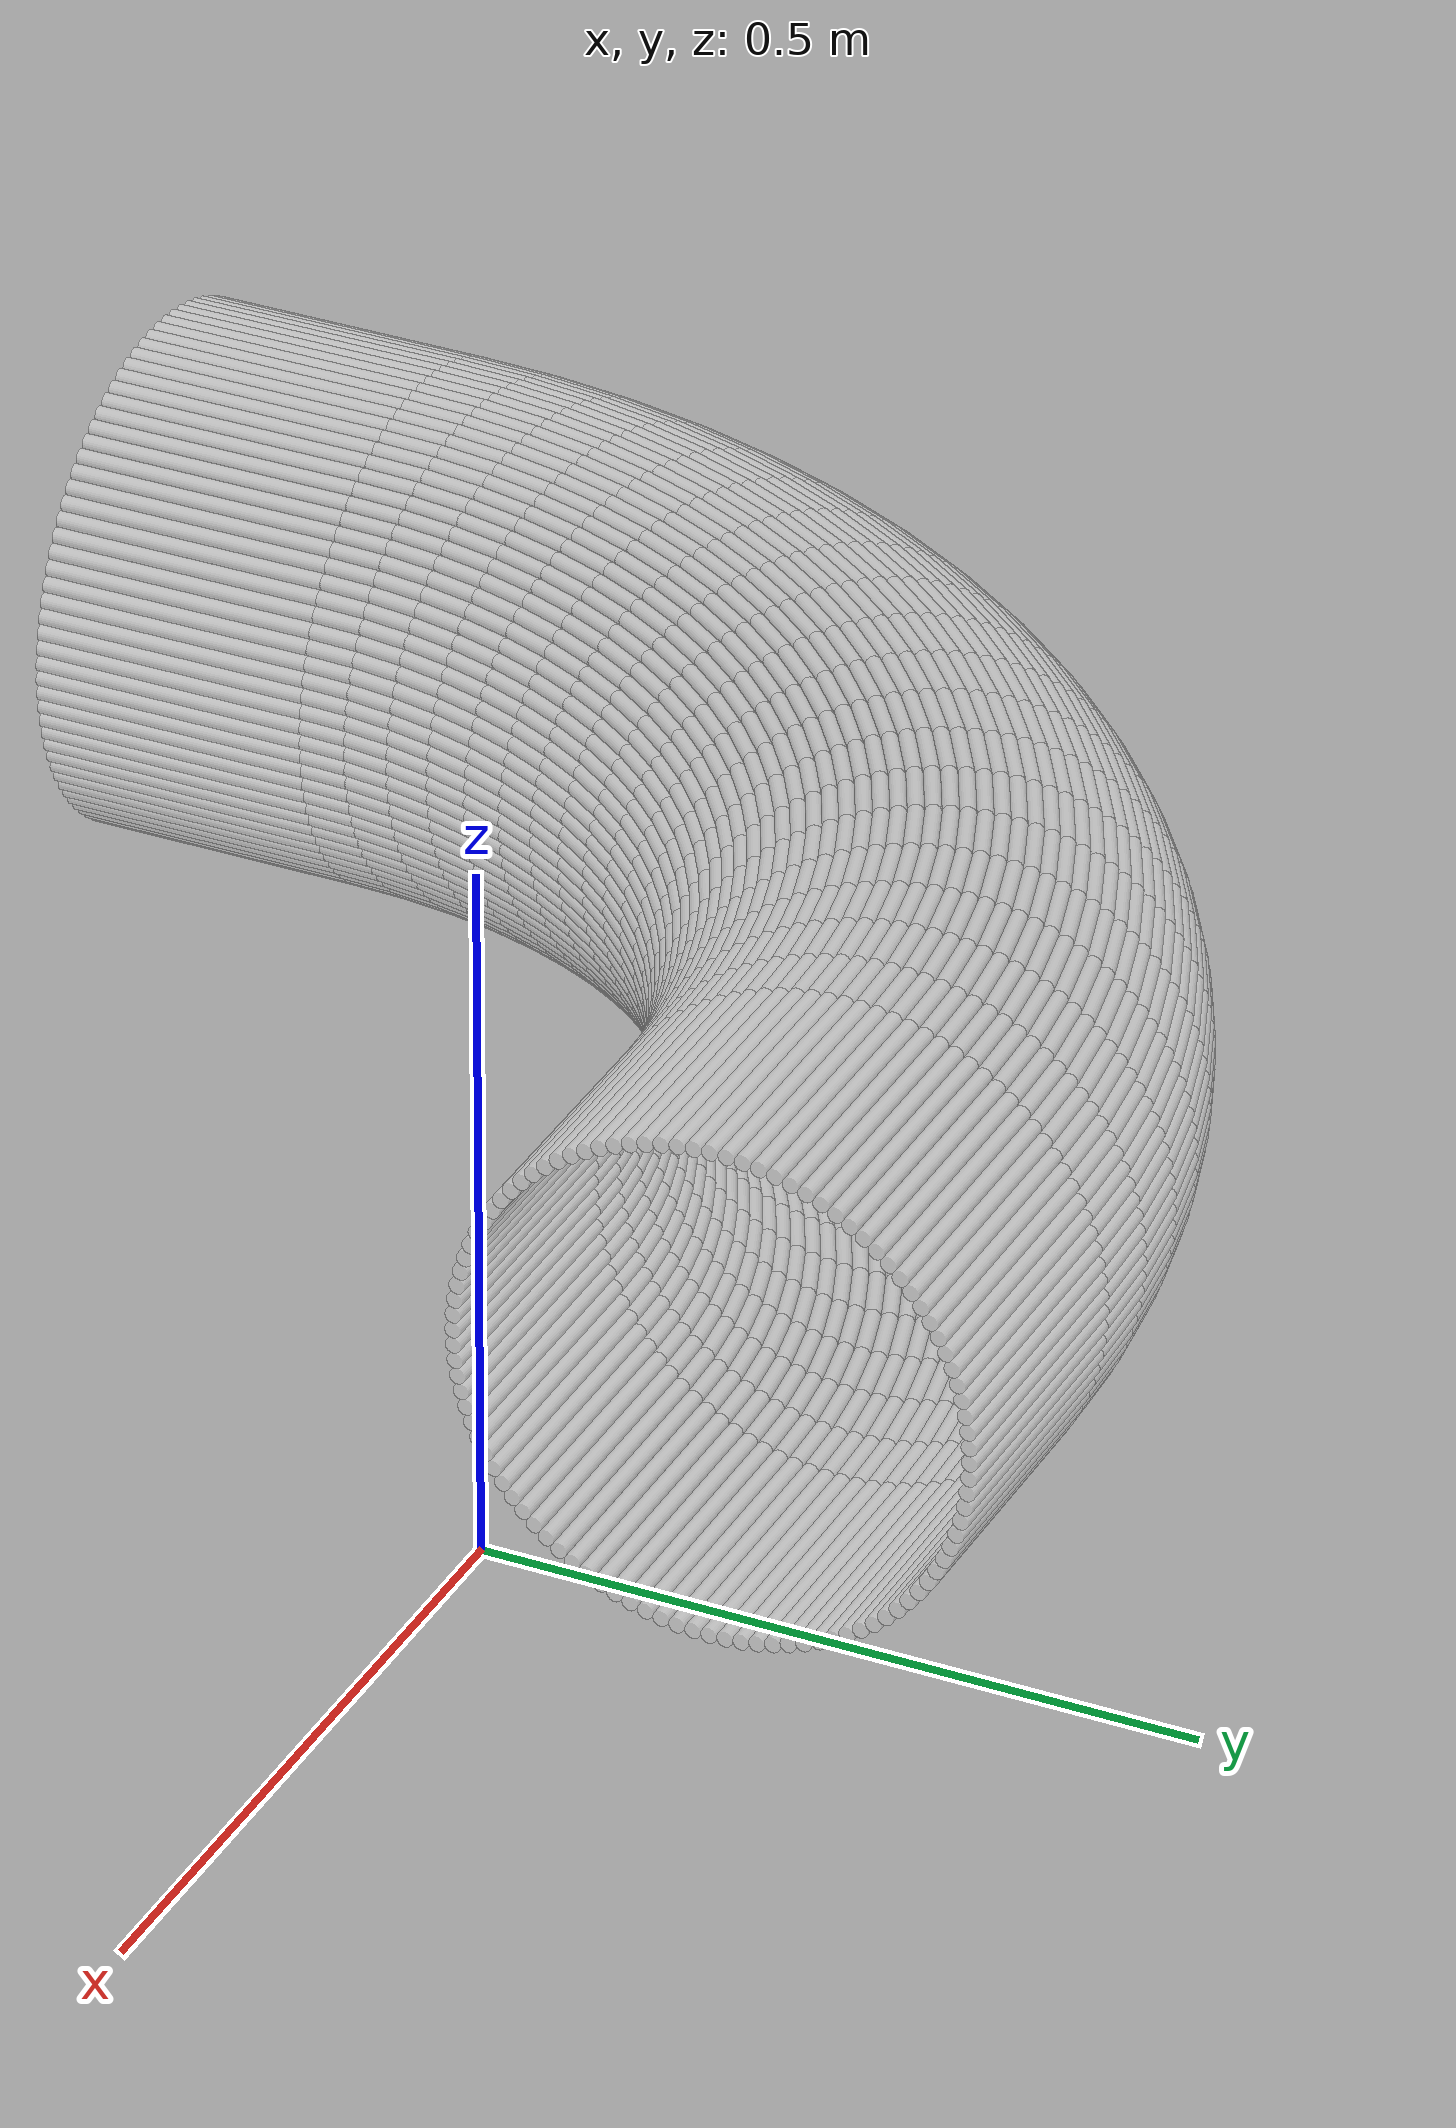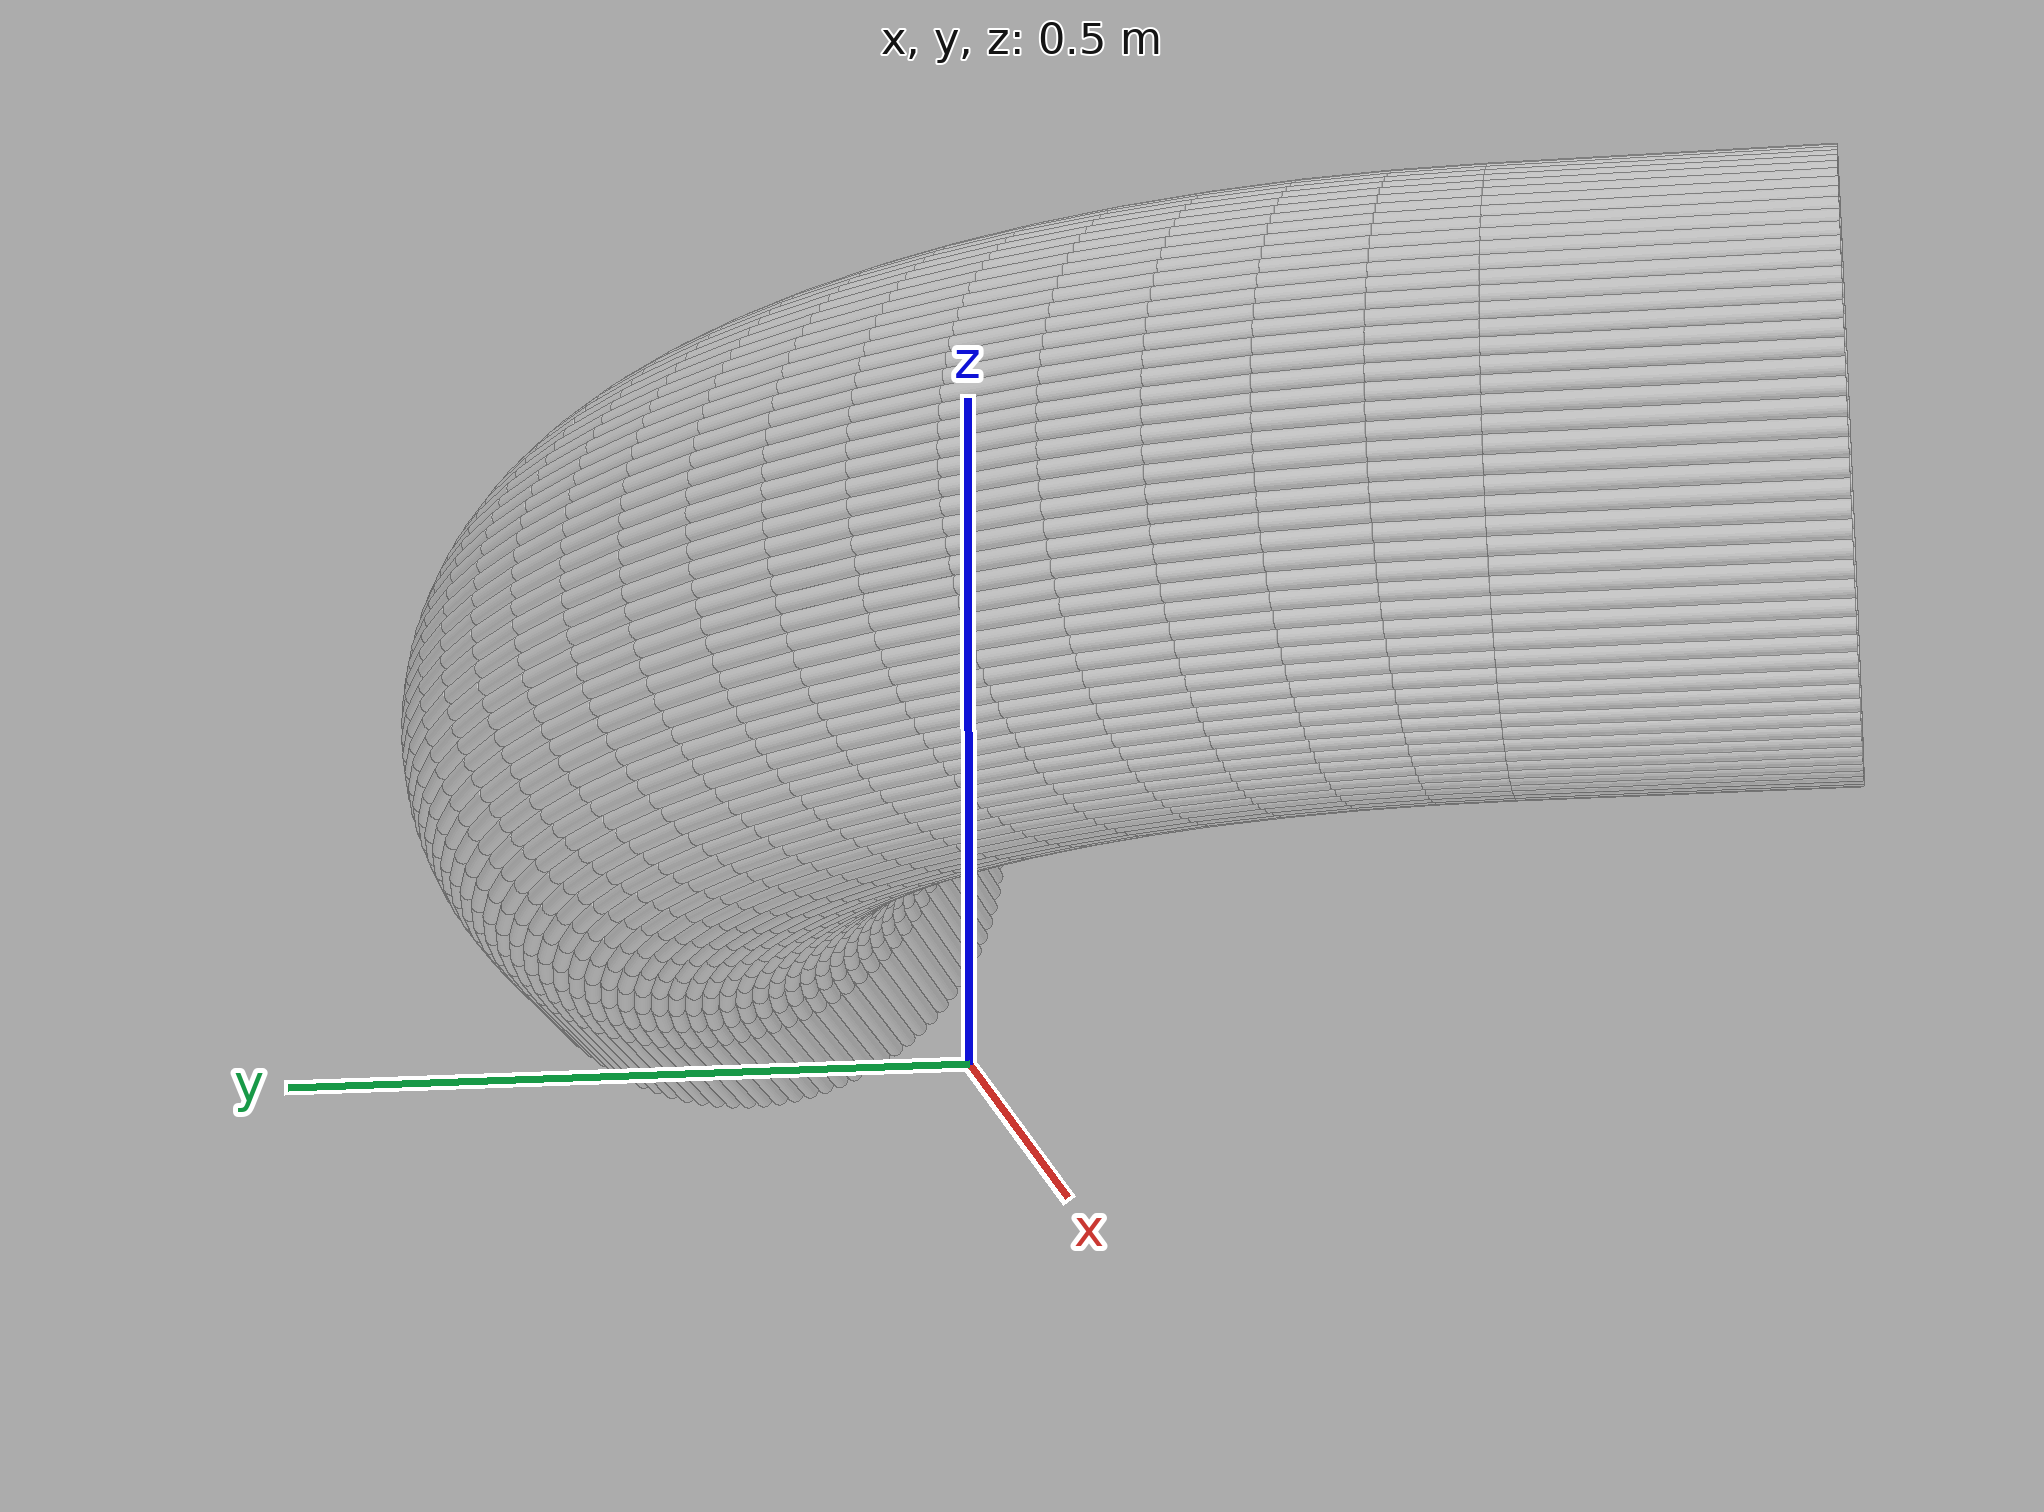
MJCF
<?xml version="1.0" encoding="utf-8"?>
<mujoco>
   <worldbody>
   <body pos="-0.2 -0.44 -0.02" euler="0 0 90">
      <geom euler=" 0 10 0 " fromto="0.78 -0.2 0.18 0.78 0 0.18" rgba="1 1 1 0.35"
            size="0.0056539"
            type="cylinder"/>
      <geom euler=" 0 20 0 " fromto="0.77964 -0.2 0.1913 0.77964 0 0.1913"
            rgba="1 1 1 0.35"
            size="0.0056539"
            type="cylinder"/>
      <geom euler=" 0 30 0 " fromto="0.77858 -0.2 0.20256 0.77858 0 0.20256"
            rgba="1 1 1 0.35"
            size="0.0056539"
            type="cylinder"/>
      <geom euler=" 0 40 0 " fromto="0.77681 -0.2 0.21373 0.77681 0 0.21373"
            rgba="1 1 1 0.35"
            size="0.0056539"
            type="cylinder"/>
      <geom euler=" 0 50 0 " fromto="0.77434 -0.2 0.22476 0.77434 0 0.22476"
            rgba="1 1 1 0.35"
            size="0.0056539"
            type="cylinder"/>
      <geom euler=" 0 60 0 " fromto="0.77119 -0.2 0.23562 0.77119 0 0.23562"
            rgba="1 1 1 0.35"
            size="0.0056539"
            type="cylinder"/>
      <geom euler=" 0 70 0 " fromto="0.76736 -0.2 0.24626 0.76736 0 0.24626"
            rgba="1 1 1 0.35"
            size="0.0056539"
            type="cylinder"/>
      <geom euler=" 0 80 0 " fromto="0.76287 -0.2 0.25664 0.76287 0 0.25664"
            rgba="1 1 1 0.35"
            size="0.0056539"
            type="cylinder"/>
      <geom euler=" 0 90 0 " fromto="0.75774 -0.2 0.26672 0.75774 0 0.26672"
            rgba="1 1 1 0.35"
            size="0.0056539"
            type="cylinder"/>
      <geom euler=" 0 100 0 " fromto="0.75198 -0.2 0.27645 0.75198 0 0.27645"
            rgba="1 1 1 0.35"
            size="0.0056539"
            type="cylinder"/>
      <geom euler=" 0 110 0 " fromto="0.74562 -0.2 0.2858 0.74562 0 0.2858"
            rgba="1 1 1 0.35"
            size="0.0056539"
            type="cylinder"/>
      <geom euler=" 0 120 0 " fromto="0.73869 -0.2 0.29474 0.73869 0 0.29474"
            rgba="1 1 1 0.35"
            size="0.0056539"
            type="cylinder"/>
      <geom euler=" 0 130 0 " fromto="0.73121 -0.2 0.30322 0.73121 0 0.30322"
            rgba="1 1 1 0.35"
            size="0.0056539"
            type="cylinder"/>
      <geom euler=" 0 140 0 " fromto="0.72322 -0.2 0.31121 0.72322 0 0.31121"
            rgba="1 1 1 0.35"
            size="0.0056539"
            type="cylinder"/>
      <geom euler=" 0 150 0 " fromto="0.71474 -0.2 0.31869 0.71474 0 0.31869"
            rgba="1 1 1 0.35"
            size="0.0056539"
            type="cylinder"/>
      <geom euler=" 0 160 0 " fromto="0.7058 -0.2 0.32562 0.7058 0 0.32562"
            rgba="1 1 1 0.35"
            size="0.0056539"
            type="cylinder"/>
      <geom euler=" 0 170 0 " fromto="0.69645 -0.2 0.33198 0.69645 0 0.33198"
            rgba="1 1 1 0.35"
            size="0.0056539"
            type="cylinder"/>
      <geom euler=" 0 180 0 " fromto="0.68672 -0.2 0.33774 0.68672 0 0.33774"
            rgba="1 1 1 0.35"
            size="0.0056539"
            type="cylinder"/>
      <geom euler=" 0 190 0 " fromto="0.67664 -0.2 0.34287 0.67664 0 0.34287"
            rgba="1 1 1 0.35"
            size="0.0056539"
            type="cylinder"/>
      <geom euler=" 0 200 0 " fromto="0.66626 -0.2 0.34736 0.66626 0 0.34736"
            rgba="1 1 1 0.35"
            size="0.0056539"
            type="cylinder"/>
      <geom euler=" 0 210 0 " fromto="0.65562 -0.2 0.35119 0.65562 0 0.35119"
            rgba="1 1 1 0.35"
            size="0.0056539"
            type="cylinder"/>
      <geom euler=" 0 220 0 " fromto="0.64476 -0.2 0.35434 0.64476 0 0.35434"
            rgba="1 1 1 0.35"
            size="0.0056539"
            type="cylinder"/>
      <geom euler=" 0 230 0 " fromto="0.63373 -0.2 0.35681 0.63373 0 0.35681"
            rgba="1 1 1 0.35"
            size="0.0056539"
            type="cylinder"/>
      <geom euler=" 0 240 0 " fromto="0.62256 -0.2 0.35858 0.62256 0 0.35858"
            rgba="1 1 1 0.35"
            size="0.0056539"
            type="cylinder"/>
      <geom euler=" 0 250 0 " fromto="0.6113 -0.2 0.35964 0.6113 0 0.35964"
            rgba="1 1 1 0.35"
            size="0.0056539"
            type="cylinder"/>
      <geom euler=" 0 260 0 " fromto="0.6 -0.2 0.36 0.6 0 0.36" rgba="1 1 1 0.35"
            size="0.0056539"
            type="cylinder"/>
      <geom euler=" 0 270 0 " fromto="0.5887 -0.2 0.35964 0.5887 0 0.35964"
            rgba="1 1 1 0.35"
            size="0.0056539"
            type="cylinder"/>
      <geom euler=" 0 280 0 " fromto="0.57744 -0.2 0.35858 0.57744 0 0.35858"
            rgba="1 1 1 0.35"
            size="0.0056539"
            type="cylinder"/>
      <geom euler=" 0 290 0 " fromto="0.56627 -0.2 0.35681 0.56627 0 0.35681"
            rgba="1 1 1 0.35"
            size="0.0056539"
            type="cylinder"/>
      <geom euler=" 0 300 0 " fromto="0.55524 -0.2 0.35434 0.55524 0 0.35434"
            rgba="1 1 1 0.35"
            size="0.0056539"
            type="cylinder"/>
      <geom euler=" 0 310 0 " fromto="0.54438 -0.2 0.35119 0.54438 0 0.35119"
            rgba="1 1 1 0.35"
            size="0.0056539"
            type="cylinder"/>
      <geom euler=" 0 320 0 " fromto="0.53374 -0.2 0.34736 0.53374 0 0.34736"
            rgba="1 1 1 0.35"
            size="0.0056539"
            type="cylinder"/>
      <geom euler=" 0 330 0 " fromto="0.52336 -0.2 0.34287 0.52336 0 0.34287"
            rgba="1 1 1 0.35"
            size="0.0056539"
            type="cylinder"/>
      <geom euler=" 0 340 0 " fromto="0.51328 -0.2 0.33774 0.51328 0 0.33774"
            rgba="1 1 1 0.35"
            size="0.0056539"
            type="cylinder"/>
      <geom euler=" 0 350 0 " fromto="0.50355 -0.2 0.33198 0.50355 0 0.33198"
            rgba="1 1 1 0.35"
            size="0.0056539"
            type="cylinder"/>
      <geom euler=" 0 360 0 " fromto="0.4942 -0.2 0.32562 0.4942 0 0.32562"
            rgba="1 1 1 0.35"
            size="0.0056539"
            type="cylinder"/>
      <geom euler=" 0 370 0 " fromto="0.48526 -0.2 0.31869 0.48526 0 0.31869"
            rgba="1 1 1 0.35"
            size="0.0056539"
            type="cylinder"/>
      <geom euler=" 0 380 0 " fromto="0.47678 -0.2 0.31121 0.47678 0 0.31121"
            rgba="1 1 1 0.35"
            size="0.0056539"
            type="cylinder"/>
      <geom euler=" 0 390 0 " fromto="0.46879 -0.2 0.30322 0.46879 0 0.30322"
            rgba="1 1 1 0.35"
            size="0.0056539"
            type="cylinder"/>
      <geom euler=" 0 400 0 " fromto="0.46131 -0.2 0.29474 0.46131 0 0.29474"
            rgba="1 1 1 0.35"
            size="0.0056539"
            type="cylinder"/>
      <geom euler=" 0 410 0 " fromto="0.45438 -0.2 0.2858 0.45438 0 0.2858"
            rgba="1 1 1 0.35"
            size="0.0056539"
            type="cylinder"/>
      <geom euler=" 0 420 0 " fromto="0.44802 -0.2 0.27645 0.44802 0 0.27645"
            rgba="1 1 1 0.35"
            size="0.0056539"
            type="cylinder"/>
      <geom euler=" 0 430 0 " fromto="0.44226 -0.2 0.26672 0.44226 0 0.26672"
            rgba="1 1 1 0.35"
            size="0.0056539"
            type="cylinder"/>
      <geom euler=" 0 440 0 " fromto="0.43713 -0.2 0.25664 0.43713 0 0.25664"
            rgba="1 1 1 0.35"
            size="0.0056539"
            type="cylinder"/>
      <geom euler=" 0 450 0 " fromto="0.43264 -0.2 0.24626 0.43264 0 0.24626"
            rgba="1 1 1 0.35"
            size="0.0056539"
            type="cylinder"/>
      <geom euler=" 0 460 0 " fromto="0.42881 -0.2 0.23562 0.42881 0 0.23562"
            rgba="1 1 1 0.35"
            size="0.0056539"
            type="cylinder"/>
      <geom euler=" 0 470 0 " fromto="0.42566 -0.2 0.22476 0.42566 0 0.22476"
            rgba="1 1 1 0.35"
            size="0.0056539"
            type="cylinder"/>
      <geom euler=" 0 480 0 " fromto="0.42319 -0.2 0.21373 0.42319 0 0.21373"
            rgba="1 1 1 0.35"
            size="0.0056539"
            type="cylinder"/>
      <geom euler=" 0 490 0 " fromto="0.42142 -0.2 0.20256 0.42142 0 0.20256"
            rgba="1 1 1 0.35"
            size="0.0056539"
            type="cylinder"/>
      <geom euler=" 0 500 0 " fromto="0.42036 -0.2 0.1913 0.42036 0 0.1913"
            rgba="1 1 1 0.35"
            size="0.0056539"
            type="cylinder"/>
      <geom euler=" 0 510 0 " fromto="0.42 -0.2 0.18 0.42 0 0.18" rgba="1 1 1 0.35"
            size="0.0056539"
            type="cylinder"/>
      <geom euler=" 0 520 0 " fromto="0.42036 -0.2 0.1687 0.42036 0 0.1687"
            rgba="1 1 1 0.35"
            size="0.0056539"
            type="cylinder"/>
      <geom euler=" 0 530 0 " fromto="0.42142 -0.2 0.15744 0.42142 0 0.15744"
            rgba="1 1 1 0.35"
            size="0.0056539"
            type="cylinder"/>
      <geom euler=" 0 540 0 " fromto="0.42319 -0.2 0.14627 0.42319 0 0.14627"
            rgba="1 1 1 0.35"
            size="0.0056539"
            type="cylinder"/>
      <geom euler=" 0 550 0 " fromto="0.42566 -0.2 0.13524 0.42566 0 0.13524"
            rgba="1 1 1 0.35"
            size="0.0056539"
            type="cylinder"/>
      <geom euler=" 0 560 0 " fromto="0.42881 -0.2 0.12438 0.42881 0 0.12438"
            rgba="1 1 1 0.35"
            size="0.0056539"
            type="cylinder"/>
      <geom euler=" 0 570 0 " fromto="0.43264 -0.2 0.11374 0.43264 0 0.11374"
            rgba="1 1 1 0.35"
            size="0.0056539"
            type="cylinder"/>
      <geom euler=" 0 580 0 " fromto="0.43713 -0.2 0.10336 0.43713 0 0.10336"
            rgba="1 1 1 0.35"
            size="0.0056539"
            type="cylinder"/>
      <geom euler=" 0 590 0 " fromto="0.44226 -0.2 0.093284 0.44226 0 0.093284"
            rgba="1 1 1 0.35"
            size="0.0056539"
            type="cylinder"/>
      <geom euler=" 0 600 0 " fromto="0.44802 -0.2 0.083551 0.44802 0 0.083551"
            rgba="1 1 1 0.35"
            size="0.0056539"
            type="cylinder"/>
      <geom euler=" 0 610 0 " fromto="0.45438 -0.2 0.074199 0.45438 0 0.074199"
            rgba="1 1 1 0.35"
            size="0.0056539"
            type="cylinder"/>
      <geom euler=" 0 620 0 " fromto="0.46131 -0.2 0.065264 0.46131 0 0.065264"
            rgba="1 1 1 0.35"
            size="0.0056539"
            type="cylinder"/>
      <geom euler=" 0 630 0 " fromto="0.46879 -0.2 0.056782 0.46879 0 0.056782"
            rgba="1 1 1 0.35"
            size="0.0056539"
            type="cylinder"/>
      <geom euler=" 0 640 0 " fromto="0.47678 -0.2 0.048786 0.47678 0 0.048786"
            rgba="1 1 1 0.35"
            size="0.0056539"
            type="cylinder"/>
      <geom euler=" 0 650 0 " fromto="0.48526 -0.2 0.041308 0.48526 0 0.041308"
            rgba="1 1 1 0.35"
            size="0.0056539"
            type="cylinder"/>
      <geom euler=" 0 660 0 " fromto="0.4942 -0.2 0.034377 0.4942 0 0.034377"
            rgba="1 1 1 0.35"
            size="0.0056539"
            type="cylinder"/>
      <geom euler=" 0 670 0 " fromto="0.50355 -0.2 0.028021 0.50355 0 0.028021"
            rgba="1 1 1 0.35"
            size="0.0056539"
            type="cylinder"/>
      <geom euler=" 0 680 0 " fromto="0.51328 -0.2 0.022265 0.51328 0 0.022265"
            rgba="1 1 1 0.35"
            size="0.0056539"
            type="cylinder"/>
      <geom euler=" 0 690 0 " fromto="0.52336 -0.2 0.017131 0.52336 0 0.017131"
            rgba="1 1 1 0.35"
            size="0.0056539"
            type="cylinder"/>
      <geom euler=" 0 700 0 " fromto="0.53374 -0.2 0.01264 0.53374 0 0.01264"
            rgba="1 1 1 0.35"
            size="0.0056539"
            type="cylinder"/>
      <geom euler=" 0 710 0 " fromto="0.54438 -0.2 0.0088098 0.54438 0 0.0088098"
            rgba="1 1 1 0.35"
            size="0.0056539"
            type="cylinder"/>
      <geom euler=" 0 720 0 " fromto="0.55524 -0.2 0.005655 0.55524 0 0.005655"
            rgba="1 1 1 0.35"
            size="0.0056539"
            type="cylinder"/>
      <geom euler=" 0 730 0 " fromto="0.56627 -0.2 0.0031883 0.56627 0 0.0031883"
            rgba="1 1 1 0.35"
            size="0.0056539"
            type="cylinder"/>
      <geom euler=" 0 740 0 " fromto="0.57744 -0.2 0.0014194 0.57744 0 0.0014194"
            rgba="1 1 1 0.35"
            size="0.0056539"
            type="cylinder"/>
      <geom euler=" 0 750 0 " fromto="0.5887 -0.2 0.00035519 0.5887 0 0.00035519"
            rgba="1 1 1 0.35"
            size="0.0056539"
            type="cylinder"/>
      <geom euler=" 0 760 0 " fromto="0.6 -0.2 0 0.6 0 0" rgba="1 1 1 0.35"
            size="0.0056539"
            type="cylinder"/>
      <geom euler=" 0 770 0 " fromto="0.6113 -0.2 0.00035519 0.6113 0 0.00035519"
            rgba="1 1 1 0.35"
            size="0.0056539"
            type="cylinder"/>
      <geom euler=" 0 780 0 " fromto="0.62256 -0.2 0.0014194 0.62256 0 0.0014194"
            rgba="1 1 1 0.35"
            size="0.0056539"
            type="cylinder"/>
      <geom euler=" 0 790 0 " fromto="0.63373 -0.2 0.0031883 0.63373 0 0.0031883"
            rgba="1 1 1 0.35"
            size="0.0056539"
            type="cylinder"/>
      <geom euler=" 0 800 0 " fromto="0.64476 -0.2 0.005655 0.64476 0 0.005655"
            rgba="1 1 1 0.35"
            size="0.0056539"
            type="cylinder"/>
      <geom euler=" 0 810 0 " fromto="0.65562 -0.2 0.0088098 0.65562 0 0.0088098"
            rgba="1 1 1 0.35"
            size="0.0056539"
            type="cylinder"/>
      <geom euler=" 0 820 0 " fromto="0.66626 -0.2 0.01264 0.66626 0 0.01264"
            rgba="1 1 1 0.35"
            size="0.0056539"
            type="cylinder"/>
      <geom euler=" 0 830 0 " fromto="0.67664 -0.2 0.017131 0.67664 0 0.017131"
            rgba="1 1 1 0.35"
            size="0.0056539"
            type="cylinder"/>
      <geom euler=" 0 840 0 " fromto="0.68672 -0.2 0.022265 0.68672 0 0.022265"
            rgba="1 1 1 0.35"
            size="0.0056539"
            type="cylinder"/>
      <geom euler=" 0 850 0 " fromto="0.69645 -0.2 0.028021 0.69645 0 0.028021"
            rgba="1 1 1 0.35"
            size="0.0056539"
            type="cylinder"/>
      <geom euler=" 0 860 0 " fromto="0.7058 -0.2 0.034377 0.7058 0 0.034377"
            rgba="1 1 1 0.35"
            size="0.0056539"
            type="cylinder"/>
      <geom euler=" 0 870 0 " fromto="0.71474 -0.2 0.041308 0.71474 0 0.041308"
            rgba="1 1 1 0.35"
            size="0.0056539"
            type="cylinder"/>
      <geom euler=" 0 880 0 " fromto="0.72322 -0.2 0.048786 0.72322 0 0.048786"
            rgba="1 1 1 0.35"
            size="0.0056539"
            type="cylinder"/>
      <geom euler=" 0 890 0 " fromto="0.73121 -0.2 0.056782 0.73121 0 0.056782"
            rgba="1 1 1 0.35"
            size="0.0056539"
            type="cylinder"/>
      <geom euler=" 0 900 0 " fromto="0.73869 -0.2 0.065264 0.73869 0 0.065264"
            rgba="1 1 1 0.35"
            size="0.0056539"
            type="cylinder"/>
      <geom euler=" 0 910 0 " fromto="0.74562 -0.2 0.074199 0.74562 0 0.074199"
            rgba="1 1 1 0.35"
            size="0.0056539"
            type="cylinder"/>
      <geom euler=" 0 920 0 " fromto="0.75198 -0.2 0.083551 0.75198 0 0.083551"
            rgba="1 1 1 0.35"
            size="0.0056539"
            type="cylinder"/>
      <geom euler=" 0 930 0 " fromto="0.75774 -0.2 0.093284 0.75774 0 0.093284"
            rgba="1 1 1 0.35"
            size="0.0056539"
            type="cylinder"/>
      <geom euler=" 0 940 0 " fromto="0.76287 -0.2 0.10336 0.76287 0 0.10336"
            rgba="1 1 1 0.35"
            size="0.0056539"
            type="cylinder"/>
      <geom euler=" 0 950 0 " fromto="0.76736 -0.2 0.11374 0.76736 0 0.11374"
            rgba="1 1 1 0.35"
            size="0.0056539"
            type="cylinder"/>
      <geom euler=" 0 960 0 " fromto="0.77119 -0.2 0.12438 0.77119 0 0.12438"
            rgba="1 1 1 0.35"
            size="0.0056539"
            type="cylinder"/>
      <geom euler=" 0 970 0 " fromto="0.77434 -0.2 0.13524 0.77434 0 0.13524"
            rgba="1 1 1 0.35"
            size="0.0056539"
            type="cylinder"/>
      <geom euler=" 0 980 0 " fromto="0.77681 -0.2 0.14627 0.77681 0 0.14627"
            rgba="1 1 1 0.35"
            size="0.0056539"
            type="cylinder"/>
      <geom euler=" 0 990 0 " fromto="0.77858 -0.2 0.15744 0.77858 0 0.15744"
            rgba="1 1 1 0.35"
            size="0.0056539"
            type="cylinder"/>
      <geom euler=" 0 1000 0 " fromto="0.77964 -0.2 0.1687 0.77964 0 0.1687"
            rgba="1 1 1 0.35"
            size="0.0056539"
            type="cylinder"/>
      <geom euler=" 0 10 0 " fromto="0.78 0 0.18 0.77734 0.064412 0.18" rgba="1 1 1 0.35"
            size="0.0056539"
            type="cylinder"/>
      <geom euler=" 0 20 0 " fromto="0.77964 0 0.1913 0.77698 0.064383 0.1913"
            rgba="1 1 1 0.35"
            size="0.0056539"
            type="cylinder"/>
      <geom euler=" 0 30 0 " fromto="0.77858 0 0.20256 0.77592 0.064295 0.20256"
            rgba="1 1 1 0.35"
            size="0.0056539"
            type="cylinder"/>
      <geom euler=" 0 40 0 " fromto="0.77681 0 0.21373 0.77416 0.064149 0.21373"
            rgba="1 1 1 0.35"
            size="0.0056539"
            type="cylinder"/>
      <geom euler=" 0 50 0 " fromto="0.77434 0 0.22476 0.7717 0.063945 0.22476"
            rgba="1 1 1 0.35"
            size="0.0056539"
            type="cylinder"/>
      <geom euler=" 0 60 0 " fromto="0.77119 0 0.23562 0.76856 0.063684 0.23562"
            rgba="1 1 1 0.35"
            size="0.0056539"
            type="cylinder"/>
      <geom euler=" 0 70 0 " fromto="0.76736 0 0.24626 0.76474 0.063368 0.24626"
            rgba="1 1 1 0.35"
            size="0.0056539"
            type="cylinder"/>
      <geom euler=" 0 80 0 " fromto="0.76287 0 0.25664 0.76026 0.062997 0.25664"
            rgba="1 1 1 0.35"
            size="0.0056539"
            type="cylinder"/>
      <geom euler=" 0 90 0 " fromto="0.75774 0 0.26672 0.75515 0.062573 0.26672"
            rgba="1 1 1 0.35"
            size="0.0056539"
            type="cylinder"/>
      <geom euler=" 0 100 0 " fromto="0.75198 0 0.27645 0.74941 0.062098 0.27645"
            rgba="1 1 1 0.35"
            size="0.0056539"
            type="cylinder"/>
      <geom euler=" 0 110 0 " fromto="0.74562 0 0.2858 0.74308 0.061573 0.2858"
            rgba="1 1 1 0.35"
            size="0.0056539"
            type="cylinder"/>
      <geom euler=" 0 120 0 " fromto="0.73869 0 0.29474 0.73617 0.061001 0.29474"
            rgba="1 1 1 0.35"
            size="0.0056539"
            type="cylinder"/>
      <geom euler=" 0 130 0 " fromto="0.73121 0 0.30322 0.72872 0.060383 0.30322"
            rgba="1 1 1 0.35"
            size="0.0056539"
            type="cylinder"/>
      <geom euler=" 0 140 0 " fromto="0.72322 0 0.31121 0.72075 0.059723 0.31121"
            rgba="1 1 1 0.35"
            size="0.0056539"
            type="cylinder"/>
      <geom euler=" 0 150 0 " fromto="0.71474 0 0.31869 0.7123 0.059022 0.31869"
            rgba="1 1 1 0.35"
            size="0.0056539"
            type="cylinder"/>
      <geom euler=" 0 160 0 " fromto="0.7058 0 0.32562 0.70339 0.058285 0.32562"
            rgba="1 1 1 0.35"
            size="0.0056539"
            type="cylinder"/>
      <geom euler=" 0 170 0 " fromto="0.69645 0 0.33198 0.69407 0.057512 0.33198"
            rgba="1 1 1 0.35"
            size="0.0056539"
            type="cylinder"/>
      <geom euler=" 0 180 0 " fromto="0.68672 0 0.33774 0.68437 0.056709 0.33774"
            rgba="1 1 1 0.35"
            size="0.0056539"
            type="cylinder"/>
      <geom euler=" 0 190 0 " fromto="0.67664 0 0.34287 0.67433 0.055877 0.34287"
            rgba="1 1 1 0.35"
            size="0.0056539"
            type="cylinder"/>
      <geom euler=" 0 200 0 " fromto="0.66626 0 0.34736 0.66399 0.05502 0.34736"
            rgba="1 1 1 0.35"
            size="0.0056539"
            type="cylinder"/>
      <geom euler=" 0 210 0 " fromto="0.65562 0 0.35119 0.65338 0.054141 0.35119"
            rgba="1 1 1 0.35"
            size="0.0056539"
            type="cylinder"/>
      <geom euler=" 0 220 0 " fromto="0.64476 0 0.35434 0.64256 0.053244 0.35434"
            rgba="1 1 1 0.35"
            size="0.0056539"
            type="cylinder"/>
      <geom euler=" 0 230 0 " fromto="0.63373 0 0.35681 0.63156 0.052333 0.35681"
            rgba="1 1 1 0.35"
            size="0.0056539"
            type="cylinder"/>
      <geom euler=" 0 240 0 " fromto="0.62256 0 0.35858 0.62043 0.051411 0.35858"
            rgba="1 1 1 0.35"
            size="0.0056539"
            type="cylinder"/>
      <geom euler=" 0 250 0 " fromto="0.6113 0 0.35964 0.60921 0.050481 0.35964"
            rgba="1 1 1 0.35"
            size="0.0056539"
            type="cylinder"/>
      <geom euler=" 0 260 0 " fromto="0.6 0 0.36 0.59795 0.049548 0.36" rgba="1 1 1 0.35"
            size="0.0056539"
            type="cylinder"/>
      <geom euler=" 0 270 0 " fromto="0.5887 0 0.35964 0.58669 0.048614 0.35964"
            rgba="1 1 1 0.35"
            size="0.0056539"
            type="cylinder"/>
      <geom euler=" 0 280 0 " fromto="0.57744 0 0.35858 0.57547 0.047685 0.35858"
            rgba="1 1 1 0.35"
            size="0.0056539"
            type="cylinder"/>
      <geom euler=" 0 290 0 " fromto="0.56627 0 0.35681 0.56434 0.046762 0.35681"
            rgba="1 1 1 0.35"
            size="0.0056539"
            type="cylinder"/>
      <geom euler=" 0 300 0 " fromto="0.55524 0 0.35434 0.55334 0.045851 0.35434"
            rgba="1 1 1 0.35"
            size="0.0056539"
            type="cylinder"/>
      <geom euler=" 0 310 0 " fromto="0.54438 0 0.35119 0.54252 0.044954 0.35119"
            rgba="1 1 1 0.35"
            size="0.0056539"
            type="cylinder"/>
      <geom euler=" 0 320 0 " fromto="0.53374 0 0.34736 0.53191 0.044076 0.34736"
            rgba="1 1 1 0.35"
            size="0.0056539"
            type="cylinder"/>
      <geom euler=" 0 330 0 " fromto="0.52336 0 0.34287 0.52157 0.043219 0.34287"
            rgba="1 1 1 0.35"
            size="0.0056539"
            type="cylinder"/>
      <geom euler=" 0 340 0 " fromto="0.51328 0 0.33774 0.51153 0.042387 0.33774"
            rgba="1 1 1 0.35"
            size="0.0056539"
            type="cylinder"/>
      <geom euler=" 0 350 0 " fromto="0.50355 0 0.33198 0.50183 0.041583 0.33198"
            rgba="1 1 1 0.35"
            size="0.0056539"
            type="cylinder"/>
      <geom euler=" 0 360 0 " fromto="0.4942 0 0.32562 0.49251 0.040811 0.32562"
            rgba="1 1 1 0.35"
            size="0.0056539"
            type="cylinder"/>
      <geom euler=" 0 370 0 " fromto="0.48526 0 0.31869 0.48361 0.040073 0.31869"
            rgba="1 1 1 0.35"
            size="0.0056539"
            type="cylinder"/>
      <geom euler=" 0 380 0 " fromto="0.47678 0 0.31121 0.47515 0.039372 0.31121"
            rgba="1 1 1 0.35"
            size="0.0056539"
            type="cylinder"/>
      <geom euler=" 0 390 0 " fromto="0.46879 0 0.30322 0.46718 0.038712 0.30322"
            rgba="1 1 1 0.35"
            size="0.0056539"
            type="cylinder"/>
      <geom euler=" 0 400 0 " fromto="0.46131 0 0.29474 0.45973 0.038094 0.29474"
            rgba="1 1 1 0.35"
            size="0.0056539"
            type="cylinder"/>
      <geom euler=" 0 410 0 " fromto="0.45438 0 0.2858 0.45283 0.037522 0.2858"
            rgba="1 1 1 0.35"
            size="0.0056539"
            type="cylinder"/>
      <geom euler=" 0 420 0 " fromto="0.44802 0 0.27645 0.44649 0.036997 0.27645"
            rgba="1 1 1 0.35"
            size="0.0056539"
            type="cylinder"/>
      <geom euler=" 0 430 0 " fromto="0.44226 0 0.26672 0.44075 0.036522 0.26672"
            rgba="1 1 1 0.35"
            size="0.0056539"
            type="cylinder"/>
      <geom euler=" 0 440 0 " fromto="0.43713 0 0.25664 0.43564 0.036098 0.25664"
            rgba="1 1 1 0.35"
            size="0.0056539"
            type="cylinder"/>
      <geom euler=" 0 450 0 " fromto="0.43264 0 0.24626 0.43116 0.035727 0.24626"
            rgba="1 1 1 0.35"
            size="0.0056539"
            type="cylinder"/>
      <geom euler=" 0 460 0 " fromto="0.42881 0 0.23562 0.42735 0.035411 0.23562"
            rgba="1 1 1 0.35"
            size="0.0056539"
            type="cylinder"/>
      <geom euler=" 0 470 0 " fromto="0.42566 0 0.22476 0.4242 0.03515 0.22476"
            rgba="1 1 1 0.35"
            size="0.0056539"
            type="cylinder"/>
      <geom euler=" 0 480 0 " fromto="0.42319 0 0.21373 0.42174 0.034947 0.21373"
            rgba="1 1 1 0.35"
            size="0.0056539"
            type="cylinder"/>
      <geom euler=" 0 490 0 " fromto="0.42142 0 0.20256 0.41998 0.034801 0.20256"
            rgba="1 1 1 0.35"
            size="0.0056539"
            type="cylinder"/>
      <geom euler=" 0 500 0 " fromto="0.42036 0 0.1913 0.41892 0.034713 0.1913"
            rgba="1 1 1 0.35"
            size="0.0056539"
            type="cylinder"/>
      <geom euler=" 0 510 0 " fromto="0.42 0 0.18 0.41857 0.034683 0.18" rgba="1 1 1 0.35"
            size="0.0056539"
            type="cylinder"/>
      <geom euler=" 0 520 0 " fromto="0.42036 0 0.1687 0.41892 0.034713 0.1687"
            rgba="1 1 1 0.35"
            size="0.0056539"
            type="cylinder"/>
      <geom euler=" 0 530 0 " fromto="0.42142 0 0.15744 0.41998 0.034801 0.15744"
            rgba="1 1 1 0.35"
            size="0.0056539"
            type="cylinder"/>
      <geom euler=" 0 540 0 " fromto="0.42319 0 0.14627 0.42174 0.034947 0.14627"
            rgba="1 1 1 0.35"
            size="0.0056539"
            type="cylinder"/>
      <geom euler=" 0 550 0 " fromto="0.42566 0 0.13524 0.4242 0.03515 0.13524"
            rgba="1 1 1 0.35"
            size="0.0056539"
            type="cylinder"/>
      <geom euler=" 0 560 0 " fromto="0.42881 0 0.12438 0.42735 0.035411 0.12438"
            rgba="1 1 1 0.35"
            size="0.0056539"
            type="cylinder"/>
      <geom euler=" 0 570 0 " fromto="0.43264 0 0.11374 0.43116 0.035727 0.11374"
            rgba="1 1 1 0.35"
            size="0.0056539"
            type="cylinder"/>
      <geom euler=" 0 580 0 " fromto="0.43713 0 0.10336 0.43564 0.036098 0.10336"
            rgba="1 1 1 0.35"
            size="0.0056539"
            type="cylinder"/>
      <geom euler=" 0 590 0 " fromto="0.44226 0 0.093284 0.44075 0.036522 0.093284"
            rgba="1 1 1 0.35"
            size="0.0056539"
            type="cylinder"/>
      <geom euler=" 0 600 0 " fromto="0.44802 0 0.083551 0.44649 0.036997 0.083551"
            rgba="1 1 1 0.35"
            size="0.0056539"
            type="cylinder"/>
      <geom euler=" 0 610 0 " fromto="0.45438 0 0.074199 0.45283 0.037522 0.074199"
            rgba="1 1 1 0.35"
            size="0.0056539"
            type="cylinder"/>
      <geom euler=" 0 620 0 " fromto="0.46131 0 0.065264 0.45973 0.038094 0.065264"
            rgba="1 1 1 0.35"
            size="0.0056539"
            type="cylinder"/>
      <geom euler=" 0 630 0 " fromto="0.46879 0 0.056782 0.46718 0.038712 0.056782"
            rgba="1 1 1 0.35"
            size="0.0056539"
            type="cylinder"/>
      <geom euler=" 0 640 0 " fromto="0.47678 0 0.048786 0.47515 0.039372 0.048786"
            rgba="1 1 1 0.35"
            size="0.0056539"
            type="cylinder"/>
      <geom euler=" 0 650 0 " fromto="0.48526 0 0.041308 0.48361 0.040073 0.041308"
            rgba="1 1 1 0.35"
            size="0.0056539"
            type="cylinder"/>
      <geom euler=" 0 660 0 " fromto="0.4942 0 0.034377 0.49251 0.040811 0.034377"
            rgba="1 1 1 0.35"
            size="0.0056539"
            type="cylinder"/>
      <geom euler=" 0 670 0 " fromto="0.50355 0 0.028021 0.50183 0.041583 0.028021"
            rgba="1 1 1 0.35"
            size="0.0056539"
            type="cylinder"/>
      <geom euler=" 0 680 0 " fromto="0.51328 0 0.022265 0.51153 0.042387 0.022265"
            rgba="1 1 1 0.35"
            size="0.0056539"
            type="cylinder"/>
      <geom euler=" 0 690 0 " fromto="0.52336 0 0.017131 0.52157 0.043219 0.017131"
            rgba="1 1 1 0.35"
            size="0.0056539"
            type="cylinder"/>
      <geom euler=" 0 700 0 " fromto="0.53374 0 0.01264 0.53191 0.044076 0.01264"
            rgba="1 1 1 0.35"
            size="0.0056539"
            type="cylinder"/>
      <geom euler=" 0 710 0 " fromto="0.54438 0 0.0088098 0.54252 0.044954 0.0088098"
            rgba="1 1 1 0.35"
            size="0.0056539"
            type="cylinder"/>
      <geom euler=" 0 720 0 " fromto="0.55524 0 0.005655 0.55334 0.045851 0.005655"
            rgba="1 1 1 0.35"
            size="0.0056539"
            type="cylinder"/>
      <geom euler=" 0 730 0 " fromto="0.56627 0 0.0031883 0.56434 0.046762 0.0031883"
            rgba="1 1 1 0.35"
            size="0.0056539"
            type="cylinder"/>
      <geom euler=" 0 740 0 " fromto="0.57744 0 0.0014194 0.57547 0.047685 0.0014194"
            rgba="1 1 1 0.35"
            size="0.0056539"
            type="cylinder"/>
      <geom euler=" 0 750 0 " fromto="0.5887 0 0.00035519 0.58669 0.048614 0.00035519"
            rgba="1 1 1 0.35"
            size="0.0056539"
            type="cylinder"/>
      <geom euler=" 0 760 0 " fromto="0.6 0 0 0.59795 0.049548 0" rgba="1 1 1 0.35"
            size="0.0056539"
            type="cylinder"/>
      <geom euler=" 0 770 0 " fromto="0.6113 0 0.00035519 0.60921 0.050481 0.00035519"
            rgba="1 1 1 0.35"
            size="0.0056539"
            type="cylinder"/>
      <geom euler=" 0 780 0 " fromto="0.62256 0 0.0014194 0.62043 0.051411 0.0014194"
            rgba="1 1 1 0.35"
            size="0.0056539"
            type="cylinder"/>
      <geom euler=" 0 790 0 " fromto="0.63373 0 0.0031883 0.63156 0.052333 0.0031883"
            rgba="1 1 1 0.35"
            size="0.0056539"
            type="cylinder"/>
      <geom euler=" 0 800 0 " fromto="0.64476 0 0.005655 0.64256 0.053244 0.005655"
            rgba="1 1 1 0.35"
            size="0.0056539"
            type="cylinder"/>
      <geom euler=" 0 810 0 " fromto="0.65562 0 0.0088098 0.65338 0.054141 0.0088098"
            rgba="1 1 1 0.35"
            size="0.0056539"
            type="cylinder"/>
      <geom euler=" 0 820 0 " fromto="0.66626 0 0.01264 0.66399 0.05502 0.01264"
            rgba="1 1 1 0.35"
            size="0.0056539"
            type="cylinder"/>
      <geom euler=" 0 830 0 " fromto="0.67664 0 0.017131 0.67433 0.055877 0.017131"
            rgba="1 1 1 0.35"
            size="0.0056539"
            type="cylinder"/>
      <geom euler=" 0 840 0 " fromto="0.68672 0 0.022265 0.68437 0.056709 0.022265"
            rgba="1 1 1 0.35"
            size="0.0056539"
            type="cylinder"/>
      <geom euler=" 0 850 0 " fromto="0.69645 0 0.028021 0.69407 0.057512 0.028021"
            rgba="1 1 1 0.35"
            size="0.0056539"
            type="cylinder"/>
      <geom euler=" 0 860 0 " fromto="0.7058 0 0.034377 0.70339 0.058285 0.034377"
            rgba="1 1 1 0.35"
            size="0.0056539"
            type="cylinder"/>
      <geom euler=" 0 870 0 " fromto="0.71474 0 0.041308 0.7123 0.059022 0.041308"
            rgba="1 1 1 0.35"
            size="0.0056539"
            type="cylinder"/>
      <geom euler=" 0 880 0 " fromto="0.72322 0 0.048786 0.72075 0.059723 0.048786"
            rgba="1 1 1 0.35"
            size="0.0056539"
            type="cylinder"/>
      <geom euler=" 0 890 0 " fromto="0.73121 0 0.056782 0.72872 0.060383 0.056782"
            rgba="1 1 1 0.35"
            size="0.0056539"
            type="cylinder"/>
      <geom euler=" 0 900 0 " fromto="0.73869 0 0.065264 0.73617 0.061001 0.065264"
            rgba="1 1 1 0.35"
            size="0.0056539"
            type="cylinder"/>
      <geom euler=" 0 910 0 " fromto="0.74562 0 0.074199 0.74308 0.061573 0.074199"
            rgba="1 1 1 0.35"
            size="0.0056539"
            type="cylinder"/>
      <geom euler=" 0 920 0 " fromto="0.75198 0 0.083551 0.74941 0.062098 0.083551"
            rgba="1 1 1 0.35"
            size="0.0056539"
            type="cylinder"/>
      <geom euler=" 0 930 0 " fromto="0.75774 0 0.093284 0.75515 0.062573 0.093284"
            rgba="1 1 1 0.35"
            size="0.0056539"
            type="cylinder"/>
      <geom euler=" 0 940 0 " fromto="0.76287 0 0.10336 0.76026 0.062997 0.10336"
            rgba="1 1 1 0.35"
            size="0.0056539"
            type="cylinder"/>
      <geom euler=" 0 950 0 " fromto="0.76736 0 0.11374 0.76474 0.063368 0.11374"
            rgba="1 1 1 0.35"
            size="0.0056539"
            type="cylinder"/>
      <geom euler=" 0 960 0 " fromto="0.77119 0 0.12438 0.76856 0.063684 0.12438"
            rgba="1 1 1 0.35"
            size="0.0056539"
            type="cylinder"/>
      <geom euler=" 0 970 0 " fromto="0.77434 0 0.13524 0.7717 0.063945 0.13524"
            rgba="1 1 1 0.35"
            size="0.0056539"
            type="cylinder"/>
      <geom euler=" 0 980 0 " fromto="0.77681 0 0.14627 0.77416 0.064149 0.14627"
            rgba="1 1 1 0.35"
            size="0.0056539"
            type="cylinder"/>
      <geom euler=" 0 990 0 " fromto="0.77858 0 0.15744 0.77592 0.064295 0.15744"
            rgba="1 1 1 0.35"
            size="0.0056539"
            type="cylinder"/>
      <geom euler=" 0 1000 0 " fromto="0.77964 0 0.1687 0.77698 0.064383 0.1687"
            rgba="1 1 1 0.35"
            size="0.0056539"
            type="cylinder"/>
      <geom euler=" 0 10 0 " fromto="0.77734 0.064412 0.18 0.76936 0.12838 0.18"
            rgba="1 1 1 0.35"
            size="0.0056539"
            type="cylinder"/>
      <geom euler=" 0 20 0 " fromto="0.77698 0.064383 0.1913 0.76901 0.12833 0.1913"
            rgba="1 1 1 0.35"
            size="0.0056539"
            type="cylinder"/>
      <geom euler=" 0 30 0 " fromto="0.77592 0.064295 0.20256 0.76796 0.12815 0.20256"
            rgba="1 1 1 0.35"
            size="0.0056539"
            type="cylinder"/>
      <geom euler=" 0 40 0 " fromto="0.77416 0.064149 0.21373 0.76622 0.12786 0.21373"
            rgba="1 1 1 0.35"
            size="0.0056539"
            type="cylinder"/>
      <geom euler=" 0 50 0 " fromto="0.7717 0.063945 0.22476 0.76378 0.12745 0.22476"
            rgba="1 1 1 0.35"
            size="0.0056539"
            type="cylinder"/>
      <geom euler=" 0 60 0 " fromto="0.76856 0.063684 0.23562 0.76067 0.12693 0.23562"
            rgba="1 1 1 0.35"
            size="0.0056539"
            type="cylinder"/>
      <geom euler=" 0 70 0 " fromto="0.76474 0.063368 0.24626 0.75689 0.1263 0.24626"
            rgba="1 1 1 0.35"
            size="0.0056539"
            type="cylinder"/>
      <geom euler=" 0 80 0 " fromto="0.76026 0.062997 0.25664 0.75246 0.12556 0.25664"
            rgba="1 1 1 0.35"
            size="0.0056539"
            type="cylinder"/>
      <geom euler=" 0 90 0 " fromto="0.75515 0.062573 0.26672 0.7474 0.12472 0.26672"
            rgba="1 1 1 0.35"
            size="0.0056539"
            type="cylinder"/>
      <geom euler=" 0 100 0 " fromto="0.74941 0.062098 0.27645 0.74172 0.12377 0.27645"
            rgba="1 1 1 0.35"
            size="0.0056539"
            type="cylinder"/>
      <geom euler=" 0 110 0 " fromto="0.74308 0.061573 0.2858 0.73545 0.12273 0.2858"
            rgba="1 1 1 0.35"
            size="0.0056539"
            type="cylinder"/>
      <geom euler=" 0 120 0 " fromto="0.73617 0.061001 0.29474 0.72862 0.12158 0.29474"
            rgba="1 1 1 0.35"
            size="0.0056539"
            type="cylinder"/>
      <geom euler=" 0 130 0 " fromto="0.72872 0.060383 0.30322 0.72124 0.12035 0.30322"
            rgba="1 1 1 0.35"
            size="0.0056539"
            type="cylinder"/>
      <geom euler=" 0 140 0 " fromto="0.72075 0.059723 0.31121 0.71335 0.11904 0.31121"
            rgba="1 1 1 0.35"
            size="0.0056539"
            type="cylinder"/>
      <geom euler=" 0 150 0 " fromto="0.7123 0.059022 0.31869 0.70499 0.11764 0.31869"
            rgba="1 1 1 0.35"
            size="0.0056539"
            type="cylinder"/>
      <geom euler=" 0 160 0 " fromto="0.70339 0.058285 0.32562 0.69618 0.11617 0.32562"
            rgba="1 1 1 0.35"
            size="0.0056539"
            type="cylinder"/>
      <geom euler=" 0 170 0 " fromto="0.69407 0.057512 0.33198 0.68695 0.11463 0.33198"
            rgba="1 1 1 0.35"
            size="0.0056539"
            type="cylinder"/>
      <geom euler=" 0 180 0 " fromto="0.68437 0.056709 0.33774 0.67735 0.11303 0.33774"
            rgba="1 1 1 0.35"
            size="0.0056539"
            type="cylinder"/>
      <geom euler=" 0 190 0 " fromto="0.67433 0.055877 0.34287 0.66741 0.11137 0.34287"
            rgba="1 1 1 0.35"
            size="0.0056539"
            type="cylinder"/>
      <geom euler=" 0 200 0 " fromto="0.66399 0.05502 0.34736 0.65718 0.10966 0.34736"
            rgba="1 1 1 0.35"
            size="0.0056539"
            type="cylinder"/>
      <geom euler=" 0 210 0 " fromto="0.65338 0.054141 0.35119 0.64668 0.10791 0.35119"
            rgba="1 1 1 0.35"
            size="0.0056539"
            type="cylinder"/>
      <geom euler=" 0 220 0 " fromto="0.64256 0.053244 0.35434 0.63597 0.10612 0.35434"
            rgba="1 1 1 0.35"
            size="0.0056539"
            type="cylinder"/>
      <geom euler=" 0 230 0 " fromto="0.63156 0.052333 0.35681 0.62509 0.10431 0.35681"
            rgba="1 1 1 0.35"
            size="0.0056539"
            type="cylinder"/>
      <geom euler=" 0 240 0 " fromto="0.62043 0.051411 0.35858 0.61407 0.10247 0.35858"
            rgba="1 1 1 0.35"
            size="0.0056539"
            type="cylinder"/>
      <geom euler=" 0 250 0 " fromto="0.60921 0.050481 0.35964 0.60296 0.10062 0.35964"
            rgba="1 1 1 0.35"
            size="0.0056539"
            type="cylinder"/>
      <geom euler=" 0 260 0 " fromto="0.59795 0.049548 0.36 0.59182 0.098757 0.36"
            rgba="1 1 1 0.35"
            size="0.0056539"
            type="cylinder"/>
      <geom euler=" 0 270 0 " fromto="0.58669 0.048614 0.35964 0.58067 0.096896 0.35964"
            rgba="1 1 1 0.35"
            size="0.0056539"
            type="cylinder"/>
      <geom euler=" 0 280 0 " fromto="0.57547 0.047685 0.35858 0.56956 0.095044 0.35858"
            rgba="1 1 1 0.35"
            size="0.0056539"
            type="cylinder"/>
      <geom euler=" 0 290 0 " fromto="0.56434 0.046762 0.35681 0.55855 0.093205 0.35681"
            rgba="1 1 1 0.35"
            size="0.0056539"
            type="cylinder"/>
      <geom euler=" 0 300 0 " fromto="0.55334 0.045851 0.35434 0.54766 0.091389 0.35434"
            rgba="1 1 1 0.35"
            size="0.0056539"
            type="cylinder"/>
      <geom euler=" 0 310 0 " fromto="0.54252 0.044954 0.35119 0.53695 0.089601 0.35119"
            rgba="1 1 1 0.35"
            size="0.0056539"
            type="cylinder"/>
      <geom euler=" 0 320 0 " fromto="0.53191 0.044076 0.34736 0.52646 0.08785 0.34736"
            rgba="1 1 1 0.35"
            size="0.0056539"
            type="cylinder"/>
      <geom euler=" 0 330 0 " fromto="0.52157 0.043219 0.34287 0.51622 0.086142 0.34287"
            rgba="1 1 1 0.35"
            size="0.0056539"
            type="cylinder"/>
      <geom euler=" 0 340 0 " fromto="0.51153 0.042387 0.33774 0.50628 0.084484 0.33774"
            rgba="1 1 1 0.35"
            size="0.0056539"
            type="cylinder"/>
      <geom euler=" 0 350 0 " fromto="0.50183 0.041583 0.33198 0.49668 0.082882 0.33198"
            rgba="1 1 1 0.35"
            size="0.0056539"
            type="cylinder"/>
      <geom euler=" 0 360 0 " fromto="0.49251 0.040811 0.32562 0.48746 0.081342 0.32562"
            rgba="1 1 1 0.35"
            size="0.0056539"
            type="cylinder"/>
      <geom euler=" 0 370 0 " fromto="0.48361 0.040073 0.31869 0.47865 0.079872 0.31869"
            rgba="1 1 1 0.35"
            size="0.0056539"
            type="cylinder"/>
      <geom euler=" 0 380 0 " fromto="0.47515 0.039372 0.31121 0.47028 0.078476 0.31121"
            rgba="1 1 1 0.35"
            size="0.0056539"
            type="cylinder"/>
      <geom euler=" 0 390 0 " fromto="0.46718 0.038712 0.30322 0.46239 0.07716 0.30322"
            rgba="1 1 1 0.35"
            size="0.0056539"
            type="cylinder"/>
      <geom euler=" 0 400 0 " fromto="0.45973 0.038094 0.29474 0.45502 0.075929 0.29474"
            rgba="1 1 1 0.35"
            size="0.0056539"
            type="cylinder"/>
      <geom euler=" 0 410 0 " fromto="0.45283 0.037522 0.2858 0.44818 0.074788 0.2858"
            rgba="1 1 1 0.35"
            size="0.0056539"
            type="cylinder"/>
      <geom euler=" 0 420 0 " fromto="0.44649 0.036997 0.27645 0.44191 0.073742 0.27645"
            rgba="1 1 1 0.35"
            size="0.0056539"
            type="cylinder"/>
      <geom euler=" 0 430 0 " fromto="0.44075 0.036522 0.26672 0.43623 0.072794 0.26672"
            rgba="1 1 1 0.35"
            size="0.0056539"
            type="cylinder"/>
      <geom euler=" 0 440 0 " fromto="0.43564 0.036098 0.25664 0.43117 0.071949 0.25664"
            rgba="1 1 1 0.35"
            size="0.0056539"
            type="cylinder"/>
      <geom euler=" 0 450 0 " fromto="0.43116 0.035727 0.24626 0.42674 0.07121 0.24626"
            rgba="1 1 1 0.35"
            size="0.0056539"
            type="cylinder"/>
      <geom euler=" 0 460 0 " fromto="0.42735 0.035411 0.23562 0.42296 0.07058 0.23562"
            rgba="1 1 1 0.35"
            size="0.0056539"
            type="cylinder"/>
      <geom euler=" 0 470 0 " fromto="0.4242 0.03515 0.22476 0.41985 0.070061 0.22476"
            rgba="1 1 1 0.35"
            size="0.0056539"
            type="cylinder"/>
      <geom euler=" 0 480 0 " fromto="0.42174 0.034947 0.21373 0.41742 0.069655 0.21373"
            rgba="1 1 1 0.35"
            size="0.0056539"
            type="cylinder"/>
      <geom euler=" 0 490 0 " fromto="0.41998 0.034801 0.20256 0.41567 0.069363 0.20256"
            rgba="1 1 1 0.35"
            size="0.0056539"
            type="cylinder"/>
      <geom euler=" 0 500 0 " fromto="0.41892 0.034713 0.1913 0.41462 0.069188 0.1913"
            rgba="1 1 1 0.35"
            size="0.0056539"
            type="cylinder"/>
      <geom euler=" 0 510 0 " fromto="0.41857 0.034683 0.18 0.41427 0.06913 0.18"
            rgba="1 1 1 0.35"
            size="0.0056539"
            type="cylinder"/>
      <geom euler=" 0 520 0 " fromto="0.41892 0.034713 0.1687 0.41462 0.069188 0.1687"
            rgba="1 1 1 0.35"
            size="0.0056539"
            type="cylinder"/>
      <geom euler=" 0 530 0 " fromto="0.41998 0.034801 0.15744 0.41567 0.069363 0.15744"
            rgba="1 1 1 0.35"
            size="0.0056539"
            type="cylinder"/>
      <geom euler=" 0 540 0 " fromto="0.42174 0.034947 0.14627 0.41742 0.069655 0.14627"
            rgba="1 1 1 0.35"
            size="0.0056539"
            type="cylinder"/>
      <geom euler=" 0 550 0 " fromto="0.4242 0.03515 0.13524 0.41985 0.070061 0.13524"
            rgba="1 1 1 0.35"
            size="0.0056539"
            type="cylinder"/>
      <geom euler=" 0 560 0 " fromto="0.42735 0.035411 0.12438 0.42296 0.07058 0.12438"
            rgba="1 1 1 0.35"
            size="0.0056539"
            type="cylinder"/>
      <geom euler=" 0 570 0 " fromto="0.43116 0.035727 0.11374 0.42674 0.07121 0.11374"
            rgba="1 1 1 0.35"
            size="0.0056539"
            type="cylinder"/>
      <geom euler=" 0 580 0 " fromto="0.43564 0.036098 0.10336 0.43117 0.071949 0.10336"
            rgba="1 1 1 0.35"
            size="0.0056539"
            type="cylinder"/>
      <geom euler=" 0 590 0 " fromto="0.44075 0.036522 0.093284 0.43623 0.072794 0.093284"
            rgba="1 1 1 0.35"
            size="0.0056539"
            type="cylinder"/>
      <geom euler=" 0 600 0 " fromto="0.44649 0.036997 0.083551 0.44191 0.073742 0.083551"
            rgba="1 1 1 0.35"
            size="0.0056539"
            type="cylinder"/>
      <geom euler=" 0 610 0 " fromto="0.45283 0.037522 0.074199 0.44818 0.074788 0.074199"
            rgba="1 1 1 0.35"
            size="0.0056539"
            type="cylinder"/>
      <geom euler=" 0 620 0 " fromto="0.45973 0.038094 0.065264 0.45502 0.075929 0.065264"
            rgba="1 1 1 0.35"
            size="0.0056539"
            type="cylinder"/>
      <geom euler=" 0 630 0 " fromto="0.46718 0.038712 0.056782 0.46239 0.07716 0.056782"
            rgba="1 1 1 0.35"
            size="0.0056539"
            type="cylinder"/>
      <geom euler=" 0 640 0 " fromto="0.47515 0.039372 0.048786 0.47028 0.078476 0.048786"
            rgba="1 1 1 0.35"
            size="0.0056539"
            type="cylinder"/>
      <geom euler=" 0 650 0 " fromto="0.48361 0.040073 0.041308 0.47865 0.079872 0.041308"
            rgba="1 1 1 0.35"
            size="0.0056539"
            type="cylinder"/>
      <geom euler=" 0 660 0 " fromto="0.49251 0.040811 0.034377 0.48746 0.081342 0.034377"
            rgba="1 1 1 0.35"
            size="0.0056539"
            type="cylinder"/>
      <geom euler=" 0 670 0 " fromto="0.50183 0.041583 0.028021 0.49668 0.082882 0.028021"
            rgba="1 1 1 0.35"
            size="0.0056539"
            type="cylinder"/>
      <geom euler=" 0 680 0 " fromto="0.51153 0.042387 0.022265 0.50628 0.084484 0.022265"
            rgba="1 1 1 0.35"
            size="0.0056539"
            type="cylinder"/>
      <geom euler=" 0 690 0 " fromto="0.52157 0.043219 0.017131 0.51622 0.086142 0.017131"
            rgba="1 1 1 0.35"
            size="0.0056539"
            type="cylinder"/>
      <geom euler=" 0 700 0 " fromto="0.53191 0.044076 0.01264 0.52646 0.08785 0.01264"
            rgba="1 1 1 0.35"
            size="0.0056539"
            type="cylinder"/>
      <geom euler=" 0 710 0 "
            fromto="0.54252 0.044954 0.0088098 0.53695 0.089601 0.0088098"
            rgba="1 1 1 0.35"
            size="0.0056539"
            type="cylinder"/>
      <geom euler=" 0 720 0 " fromto="0.55334 0.045851 0.005655 0.54766 0.091389 0.005655"
            rgba="1 1 1 0.35"
            size="0.0056539"
            type="cylinder"/>
      <geom euler=" 0 730 0 "
            fromto="0.56434 0.046762 0.0031883 0.55855 0.093205 0.0031883"
            rgba="1 1 1 0.35"
            size="0.0056539"
            type="cylinder"/>
      <geom euler=" 0 740 0 "
            fromto="0.57547 0.047685 0.0014194 0.56956 0.095044 0.0014194"
            rgba="1 1 1 0.35"
            size="0.0056539"
            type="cylinder"/>
      <geom euler=" 0 750 0 "
            fromto="0.58669 0.048614 0.00035519 0.58067 0.096896 0.00035519"
            rgba="1 1 1 0.35"
            size="0.0056539"
            type="cylinder"/>
      <geom euler=" 0 760 0 " fromto="0.59795 0.049548 0 0.59182 0.098757 0"
            rgba="1 1 1 0.35"
            size="0.0056539"
            type="cylinder"/>
      <geom euler=" 0 770 0 "
            fromto="0.60921 0.050481 0.00035519 0.60296 0.10062 0.00035519"
            rgba="1 1 1 0.35"
            size="0.0056539"
            type="cylinder"/>
      <geom euler=" 0 780 0 " fromto="0.62043 0.051411 0.0014194 0.61407 0.10247 0.0014194"
            rgba="1 1 1 0.35"
            size="0.0056539"
            type="cylinder"/>
      <geom euler=" 0 790 0 " fromto="0.63156 0.052333 0.0031883 0.62509 0.10431 0.0031883"
            rgba="1 1 1 0.35"
            size="0.0056539"
            type="cylinder"/>
      <geom euler=" 0 800 0 " fromto="0.64256 0.053244 0.005655 0.63597 0.10612 0.005655"
            rgba="1 1 1 0.35"
            size="0.0056539"
            type="cylinder"/>
      <geom euler=" 0 810 0 " fromto="0.65338 0.054141 0.0088098 0.64668 0.10791 0.0088098"
            rgba="1 1 1 0.35"
            size="0.0056539"
            type="cylinder"/>
      <geom euler=" 0 820 0 " fromto="0.66399 0.05502 0.01264 0.65718 0.10966 0.01264"
            rgba="1 1 1 0.35"
            size="0.0056539"
            type="cylinder"/>
      <geom euler=" 0 830 0 " fromto="0.67433 0.055877 0.017131 0.66741 0.11137 0.017131"
            rgba="1 1 1 0.35"
            size="0.0056539"
            type="cylinder"/>
      <geom euler=" 0 840 0 " fromto="0.68437 0.056709 0.022265 0.67735 0.11303 0.022265"
            rgba="1 1 1 0.35"
            size="0.0056539"
            type="cylinder"/>
      <geom euler=" 0 850 0 " fromto="0.69407 0.057512 0.028021 0.68695 0.11463 0.028021"
            rgba="1 1 1 0.35"
            size="0.0056539"
            type="cylinder"/>
      <geom euler=" 0 860 0 " fromto="0.70339 0.058285 0.034377 0.69618 0.11617 0.034377"
            rgba="1 1 1 0.35"
            size="0.0056539"
            type="cylinder"/>
      <geom euler=" 0 870 0 " fromto="0.7123 0.059022 0.041308 0.70499 0.11764 0.041308"
            rgba="1 1 1 0.35"
            size="0.0056539"
            type="cylinder"/>
      <geom euler=" 0 880 0 " fromto="0.72075 0.059723 0.048786 0.71335 0.11904 0.048786"
            rgba="1 1 1 0.35"
            size="0.0056539"
            type="cylinder"/>
      <geom euler=" 0 890 0 " fromto="0.72872 0.060383 0.056782 0.72124 0.12035 0.056782"
            rgba="1 1 1 0.35"
            size="0.0056539"
            type="cylinder"/>
      <geom euler=" 0 900 0 " fromto="0.73617 0.061001 0.065264 0.72862 0.12158 0.065264"
            rgba="1 1 1 0.35"
            size="0.0056539"
            type="cylinder"/>
      <geom euler=" 0 910 0 " fromto="0.74308 0.061573 0.074199 0.73545 0.12273 0.074199"
            rgba="1 1 1 0.35"
            size="0.0056539"
            type="cylinder"/>
      <geom euler=" 0 920 0 " fromto="0.74941 0.062098 0.083551 0.74172 0.12377 0.083551"
            rgba="1 1 1 0.35"
            size="0.0056539"
            type="cylinder"/>
      <geom euler=" 0 930 0 " fromto="0.75515 0.062573 0.093284 0.7474 0.12472 0.093284"
            rgba="1 1 1 0.35"
            size="0.0056539"
            type="cylinder"/>
      <geom euler=" 0 940 0 " fromto="0.76026 0.062997 0.10336 0.75246 0.12556 0.10336"
            rgba="1 1 1 0.35"
            size="0.0056539"
            type="cylinder"/>
      <geom euler=" 0 950 0 " fromto="0.76474 0.063368 0.11374 0.75689 0.1263 0.11374"
            rgba="1 1 1 0.35"
            size="0.0056539"
            type="cylinder"/>
      <geom euler=" 0 960 0 " fromto="0.76856 0.063684 0.12438 0.76067 0.12693 0.12438"
            rgba="1 1 1 0.35"
            size="0.0056539"
            type="cylinder"/>
      <geom euler=" 0 970 0 " fromto="0.7717 0.063945 0.13524 0.76378 0.12745 0.13524"
            rgba="1 1 1 0.35"
            size="0.0056539"
            type="cylinder"/>
      <geom euler=" 0 980 0 " fromto="0.77416 0.064149 0.14627 0.76622 0.12786 0.14627"
            rgba="1 1 1 0.35"
            size="0.0056539"
            type="cylinder"/>
      <geom euler=" 0 990 0 " fromto="0.77592 0.064295 0.15744 0.76796 0.12815 0.15744"
            rgba="1 1 1 0.35"
            size="0.0056539"
            type="cylinder"/>
      <geom euler=" 0 1000 0 " fromto="0.77698 0.064383 0.1687 0.76901 0.12833 0.1687"
            rgba="1 1 1 0.35"
            size="0.0056539"
            type="cylinder"/>
      <geom euler=" 0 10 0 " fromto="0.76936 0.12838 0.18 0.75613 0.19148 0.18"
            rgba="1 1 1 0.35"
            size="0.0056539"
            type="cylinder"/>
      <geom euler=" 0 20 0 " fromto="0.76901 0.12833 0.1913 0.75579 0.19139 0.1913"
            rgba="1 1 1 0.35"
            size="0.0056539"
            type="cylinder"/>
      <geom euler=" 0 30 0 " fromto="0.76796 0.12815 0.20256 0.75476 0.19113 0.20256"
            rgba="1 1 1 0.35"
            size="0.0056539"
            type="cylinder"/>
      <geom euler=" 0 40 0 " fromto="0.76622 0.12786 0.21373 0.75304 0.1907 0.21373"
            rgba="1 1 1 0.35"
            size="0.0056539"
            type="cylinder"/>
      <geom euler=" 0 50 0 " fromto="0.76378 0.12745 0.22476 0.75065 0.19009 0.22476"
            rgba="1 1 1 0.35"
            size="0.0056539"
            type="cylinder"/>
      <geom euler=" 0 60 0 " fromto="0.76067 0.12693 0.23562 0.74759 0.18932 0.23562"
            rgba="1 1 1 0.35"
            size="0.0056539"
            type="cylinder"/>
      <geom euler=" 0 70 0 " fromto="0.75689 0.1263 0.24626 0.74388 0.18838 0.24626"
            rgba="1 1 1 0.35"
            size="0.0056539"
            type="cylinder"/>
      <geom euler=" 0 80 0 " fromto="0.75246 0.12556 0.25664 0.73953 0.18727 0.25664"
            rgba="1 1 1 0.35"
            size="0.0056539"
            type="cylinder"/>
      <geom euler=" 0 90 0 " fromto="0.7474 0.12472 0.26672 0.73455 0.18601 0.26672"
            rgba="1 1 1 0.35"
            size="0.0056539"
            type="cylinder"/>
      <geom euler=" 0 100 0 " fromto="0.74172 0.12377 0.27645 0.72897 0.1846 0.27645"
            rgba="1 1 1 0.35"
            size="0.0056539"
            type="cylinder"/>
      <geom euler=" 0 110 0 " fromto="0.73545 0.12273 0.2858 0.72281 0.18304 0.2858"
            rgba="1 1 1 0.35"
            size="0.0056539"
            type="cylinder"/>
      <geom euler=" 0 120 0 " fromto="0.72862 0.12158 0.29474 0.71609 0.18134 0.29474"
            rgba="1 1 1 0.35"
            size="0.0056539"
            type="cylinder"/>
      <geom euler=" 0 130 0 " fromto="0.72124 0.12035 0.30322 0.70884 0.1795 0.30322"
            rgba="1 1 1 0.35"
            size="0.0056539"
            type="cylinder"/>
      <geom euler=" 0 140 0 " fromto="0.71335 0.11904 0.31121 0.70109 0.17754 0.31121"
            rgba="1 1 1 0.35"
            size="0.0056539"
            type="cylinder"/>
      <geom euler=" 0 150 0 " fromto="0.70499 0.11764 0.31869 0.69287 0.17546 0.31869"
            rgba="1 1 1 0.35"
            size="0.0056539"
            type="cylinder"/>
      <geom euler=" 0 160 0 " fromto="0.69618 0.11617 0.32562 0.6842 0.17326 0.32562"
            rgba="1 1 1 0.35"
            size="0.0056539"
            type="cylinder"/>
      <geom euler=" 0 170 0 " fromto="0.68695 0.11463 0.33198 0.67514 0.17097 0.33198"
            rgba="1 1 1 0.35"
            size="0.0056539"
            type="cylinder"/>
      <geom euler=" 0 180 0 " fromto="0.67735 0.11303 0.33774 0.6657 0.16858 0.33774"
            rgba="1 1 1 0.35"
            size="0.0056539"
            type="cylinder"/>
      <geom euler=" 0 190 0 " fromto="0.66741 0.11137 0.34287 0.65594 0.16611 0.34287"
            rgba="1 1 1 0.35"
            size="0.0056539"
            type="cylinder"/>
      <geom euler=" 0 200 0 " fromto="0.65718 0.10966 0.34736 0.64587 0.16356 0.34736"
            rgba="1 1 1 0.35"
            size="0.0056539"
            type="cylinder"/>
      <geom euler=" 0 210 0 " fromto="0.64668 0.10791 0.35119 0.63556 0.16095 0.35119"
            rgba="1 1 1 0.35"
            size="0.0056539"
            type="cylinder"/>
      <geom euler=" 0 220 0 " fromto="0.63597 0.10612 0.35434 0.62503 0.15828 0.35434"
            rgba="1 1 1 0.35"
            size="0.0056539"
            type="cylinder"/>
      <geom euler=" 0 230 0 " fromto="0.62509 0.10431 0.35681 0.61434 0.15557 0.35681"
            rgba="1 1 1 0.35"
            size="0.0056539"
            type="cylinder"/>
      <geom euler=" 0 240 0 " fromto="0.61407 0.10247 0.35858 0.60351 0.15283 0.35858"
            rgba="1 1 1 0.35"
            size="0.0056539"
            type="cylinder"/>
      <geom euler=" 0 250 0 " fromto="0.60296 0.10062 0.35964 0.5926 0.15007 0.35964"
            rgba="1 1 1 0.35"
            size="0.0056539"
            type="cylinder"/>
      <geom euler=" 0 260 0 " fromto="0.59182 0.098757 0.36 0.58164 0.14729 0.36"
            rgba="1 1 1 0.35"
            size="0.0056539"
            type="cylinder"/>
      <geom euler=" 0 270 0 " fromto="0.58067 0.096896 0.35964 0.57068 0.14452 0.35964"
            rgba="1 1 1 0.35"
            size="0.0056539"
            type="cylinder"/>
      <geom euler=" 0 280 0 " fromto="0.56956 0.095044 0.35858 0.55977 0.14175 0.35858"
            rgba="1 1 1 0.35"
            size="0.0056539"
            type="cylinder"/>
      <geom euler=" 0 290 0 " fromto="0.55855 0.093205 0.35681 0.54894 0.13901 0.35681"
            rgba="1 1 1 0.35"
            size="0.0056539"
            type="cylinder"/>
      <geom euler=" 0 300 0 " fromto="0.54766 0.091389 0.35434 0.53825 0.1363 0.35434"
            rgba="1 1 1 0.35"
            size="0.0056539"
            type="cylinder"/>
      <geom euler=" 0 310 0 " fromto="0.53695 0.089601 0.35119 0.52772 0.13364 0.35119"
            rgba="1 1 1 0.35"
            size="0.0056539"
            type="cylinder"/>
      <geom euler=" 0 320 0 " fromto="0.52646 0.08785 0.34736 0.51741 0.13102 0.34736"
            rgba="1 1 1 0.35"
            size="0.0056539"
            type="cylinder"/>
      <geom euler=" 0 330 0 " fromto="0.51622 0.086142 0.34287 0.50735 0.12848 0.34287"
            rgba="1 1 1 0.35"
            size="0.0056539"
            type="cylinder"/>
      <geom euler=" 0 340 0 " fromto="0.50628 0.084484 0.33774 0.49758 0.126 0.33774"
            rgba="1 1 1 0.35"
            size="0.0056539"
            type="cylinder"/>
      <geom euler=" 0 350 0 " fromto="0.49668 0.082882 0.33198 0.48814 0.12361 0.33198"
            rgba="1 1 1 0.35"
            size="0.0056539"
            type="cylinder"/>
      <geom euler=" 0 360 0 " fromto="0.48746 0.081342 0.32562 0.47908 0.12132 0.32562"
            rgba="1 1 1 0.35"
            size="0.0056539"
            type="cylinder"/>
      <geom euler=" 0 370 0 " fromto="0.47865 0.079872 0.31869 0.47041 0.11913 0.31869"
            rgba="1 1 1 0.35"
            size="0.0056539"
            type="cylinder"/>
      <geom euler=" 0 380 0 " fromto="0.47028 0.078476 0.31121 0.46219 0.11704 0.31121"
            rgba="1 1 1 0.35"
            size="0.0056539"
            type="cylinder"/>
      <geom euler=" 0 390 0 " fromto="0.46239 0.07716 0.30322 0.45444 0.11508 0.30322"
            rgba="1 1 1 0.35"
            size="0.0056539"
            type="cylinder"/>
      <geom euler=" 0 400 0 " fromto="0.45502 0.075929 0.29474 0.44719 0.11324 0.29474"
            rgba="1 1 1 0.35"
            size="0.0056539"
            type="cylinder"/>
      <geom euler=" 0 410 0 " fromto="0.44818 0.074788 0.2858 0.44047 0.11154 0.2858"
            rgba="1 1 1 0.35"
            size="0.0056539"
            type="cylinder"/>
      <geom euler=" 0 420 0 " fromto="0.44191 0.073742 0.27645 0.43431 0.10998 0.27645"
            rgba="1 1 1 0.35"
            size="0.0056539"
            type="cylinder"/>
      <geom euler=" 0 430 0 " fromto="0.43623 0.072794 0.26672 0.42873 0.10857 0.26672"
            rgba="1 1 1 0.35"
            size="0.0056539"
            type="cylinder"/>
      <geom euler=" 0 440 0 " fromto="0.43117 0.071949 0.25664 0.42376 0.10731 0.25664"
            rgba="1 1 1 0.35"
            size="0.0056539"
            type="cylinder"/>
      <geom euler=" 0 450 0 " fromto="0.42674 0.07121 0.24626 0.4194 0.10621 0.24626"
            rgba="1 1 1 0.35"
            size="0.0056539"
            type="cylinder"/>
      <geom euler=" 0 460 0 " fromto="0.42296 0.07058 0.23562 0.41569 0.10527 0.23562"
            rgba="1 1 1 0.35"
            size="0.0056539"
            type="cylinder"/>
      <geom euler=" 0 470 0 " fromto="0.41985 0.070061 0.22476 0.41263 0.10449 0.22476"
            rgba="1 1 1 0.35"
            size="0.0056539"
            type="cylinder"/>
      <geom euler=" 0 480 0 " fromto="0.41742 0.069655 0.21373 0.41024 0.10389 0.21373"
            rgba="1 1 1 0.35"
            size="0.0056539"
            type="cylinder"/>
      <geom euler=" 0 490 0 " fromto="0.41567 0.069363 0.20256 0.40852 0.10345 0.20256"
            rgba="1 1 1 0.35"
            size="0.0056539"
            type="cylinder"/>
      <geom euler=" 0 500 0 " fromto="0.41462 0.069188 0.1913 0.40749 0.10319 0.1913"
            rgba="1 1 1 0.35"
            size="0.0056539"
            type="cylinder"/>
      <geom euler=" 0 510 0 " fromto="0.41427 0.06913 0.18 0.40715 0.1031 0.18"
            rgba="1 1 1 0.35"
            size="0.0056539"
            type="cylinder"/>
      <geom euler=" 0 520 0 " fromto="0.41462 0.069188 0.1687 0.40749 0.10319 0.1687"
            rgba="1 1 1 0.35"
            size="0.0056539"
            type="cylinder"/>
      <geom euler=" 0 530 0 " fromto="0.41567 0.069363 0.15744 0.40852 0.10345 0.15744"
            rgba="1 1 1 0.35"
            size="0.0056539"
            type="cylinder"/>
      <geom euler=" 0 540 0 " fromto="0.41742 0.069655 0.14627 0.41024 0.10389 0.14627"
            rgba="1 1 1 0.35"
            size="0.0056539"
            type="cylinder"/>
      <geom euler=" 0 550 0 " fromto="0.41985 0.070061 0.13524 0.41263 0.10449 0.13524"
            rgba="1 1 1 0.35"
            size="0.0056539"
            type="cylinder"/>
      <geom euler=" 0 560 0 " fromto="0.42296 0.07058 0.12438 0.41569 0.10527 0.12438"
            rgba="1 1 1 0.35"
            size="0.0056539"
            type="cylinder"/>
      <geom euler=" 0 570 0 " fromto="0.42674 0.07121 0.11374 0.4194 0.10621 0.11374"
            rgba="1 1 1 0.35"
            size="0.0056539"
            type="cylinder"/>
      <geom euler=" 0 580 0 " fromto="0.43117 0.071949 0.10336 0.42376 0.10731 0.10336"
            rgba="1 1 1 0.35"
            size="0.0056539"
            type="cylinder"/>
      <geom euler=" 0 590 0 " fromto="0.43623 0.072794 0.093284 0.42873 0.10857 0.093284"
            rgba="1 1 1 0.35"
            size="0.0056539"
            type="cylinder"/>
      <geom euler=" 0 600 0 " fromto="0.44191 0.073742 0.083551 0.43431 0.10998 0.083551"
            rgba="1 1 1 0.35"
            size="0.0056539"
            type="cylinder"/>
      <geom euler=" 0 610 0 " fromto="0.44818 0.074788 0.074199 0.44047 0.11154 0.074199"
            rgba="1 1 1 0.35"
            size="0.0056539"
            type="cylinder"/>
      <geom euler=" 0 620 0 " fromto="0.45502 0.075929 0.065264 0.44719 0.11324 0.065264"
            rgba="1 1 1 0.35"
            size="0.0056539"
            type="cylinder"/>
      <geom euler=" 0 630 0 " fromto="0.46239 0.07716 0.056782 0.45444 0.11508 0.056782"
            rgba="1 1 1 0.35"
            size="0.0056539"
            type="cylinder"/>
      <geom euler=" 0 640 0 " fromto="0.47028 0.078476 0.048786 0.46219 0.11704 0.048786"
            rgba="1 1 1 0.35"
            size="0.0056539"
            type="cylinder"/>
      <geom euler=" 0 650 0 " fromto="0.47865 0.079872 0.041308 0.47041 0.11913 0.041308"
            rgba="1 1 1 0.35"
            size="0.0056539"
            type="cylinder"/>
      <geom euler=" 0 660 0 " fromto="0.48746 0.081342 0.034377 0.47908 0.12132 0.034377"
            rgba="1 1 1 0.35"
            size="0.0056539"
            type="cylinder"/>
      <geom euler=" 0 670 0 " fromto="0.49668 0.082882 0.028021 0.48814 0.12361 0.028021"
            rgba="1 1 1 0.35"
            size="0.0056539"
            type="cylinder"/>
      <geom euler=" 0 680 0 " fromto="0.50628 0.084484 0.022265 0.49758 0.126 0.022265"
            rgba="1 1 1 0.35"
            size="0.0056539"
            type="cylinder"/>
      <geom euler=" 0 690 0 " fromto="0.51622 0.086142 0.017131 0.50735 0.12848 0.017131"
            rgba="1 1 1 0.35"
            size="0.0056539"
            type="cylinder"/>
      <geom euler=" 0 700 0 " fromto="0.52646 0.08785 0.01264 0.51741 0.13102 0.01264"
            rgba="1 1 1 0.35"
            size="0.0056539"
            type="cylinder"/>
      <geom euler=" 0 710 0 " fromto="0.53695 0.089601 0.0088098 0.52772 0.13364 0.0088098"
            rgba="1 1 1 0.35"
            size="0.0056539"
            type="cylinder"/>
      <geom euler=" 0 720 0 " fromto="0.54766 0.091389 0.005655 0.53825 0.1363 0.005655"
            rgba="1 1 1 0.35"
            size="0.0056539"
            type="cylinder"/>
      <geom euler=" 0 730 0 " fromto="0.55855 0.093205 0.0031883 0.54894 0.13901 0.0031883"
            rgba="1 1 1 0.35"
            size="0.0056539"
            type="cylinder"/>
      <geom euler=" 0 740 0 " fromto="0.56956 0.095044 0.0014194 0.55977 0.14175 0.0014194"
            rgba="1 1 1 0.35"
            size="0.0056539"
            type="cylinder"/>
      <geom euler=" 0 750 0 "
            fromto="0.58067 0.096896 0.00035519 0.57068 0.14452 0.00035519"
            rgba="1 1 1 0.35"
            size="0.0056539"
            type="cylinder"/>
      <geom euler=" 0 760 0 " fromto="0.59182 0.098757 0 0.58164 0.14729 0"
            rgba="1 1 1 0.35"
            size="0.0056539"
            type="cylinder"/>
      <geom euler=" 0 770 0 " fromto="0.60296 0.10062 0.00035519 0.5926 0.15007 0.00035519"
            rgba="1 1 1 0.35"
            size="0.0056539"
            type="cylinder"/>
      <geom euler=" 0 780 0 " fromto="0.61407 0.10247 0.0014194 0.60351 0.15283 0.0014194"
            rgba="1 1 1 0.35"
            size="0.0056539"
            type="cylinder"/>
      <geom euler=" 0 790 0 " fromto="0.62509 0.10431 0.0031883 0.61434 0.15557 0.0031883"
            rgba="1 1 1 0.35"
            size="0.0056539"
            type="cylinder"/>
      <geom euler=" 0 800 0 " fromto="0.63597 0.10612 0.005655 0.62503 0.15828 0.005655"
            rgba="1 1 1 0.35"
            size="0.0056539"
            type="cylinder"/>
      <geom euler=" 0 810 0 " fromto="0.64668 0.10791 0.0088098 0.63556 0.16095 0.0088098"
            rgba="1 1 1 0.35"
            size="0.0056539"
            type="cylinder"/>
      <geom euler=" 0 820 0 " fromto="0.65718 0.10966 0.01264 0.64587 0.16356 0.01264"
            rgba="1 1 1 0.35"
            size="0.0056539"
            type="cylinder"/>
      <geom euler=" 0 830 0 " fromto="0.66741 0.11137 0.017131 0.65594 0.16611 0.017131"
            rgba="1 1 1 0.35"
            size="0.0056539"
            type="cylinder"/>
      <geom euler=" 0 840 0 " fromto="0.67735 0.11303 0.022265 0.6657 0.16858 0.022265"
            rgba="1 1 1 0.35"
            size="0.0056539"
            type="cylinder"/>
      <geom euler=" 0 850 0 " fromto="0.68695 0.11463 0.028021 0.67514 0.17097 0.028021"
            rgba="1 1 1 0.35"
            size="0.0056539"
            type="cylinder"/>
      <geom euler=" 0 860 0 " fromto="0.69618 0.11617 0.034377 0.6842 0.17326 0.034377"
            rgba="1 1 1 0.35"
            size="0.0056539"
            type="cylinder"/>
      <geom euler=" 0 870 0 " fromto="0.70499 0.11764 0.041308 0.69287 0.17546 0.041308"
            rgba="1 1 1 0.35"
            size="0.0056539"
            type="cylinder"/>
      <geom euler=" 0 880 0 " fromto="0.71335 0.11904 0.048786 0.70109 0.17754 0.048786"
            rgba="1 1 1 0.35"
            size="0.0056539"
            type="cylinder"/>
      <geom euler=" 0 890 0 " fromto="0.72124 0.12035 0.056782 0.70884 0.1795 0.056782"
            rgba="1 1 1 0.35"
            size="0.0056539"
            type="cylinder"/>
      <geom euler=" 0 900 0 " fromto="0.72862 0.12158 0.065264 0.71609 0.18134 0.065264"
            rgba="1 1 1 0.35"
            size="0.0056539"
            type="cylinder"/>
      <geom euler=" 0 910 0 " fromto="0.73545 0.12273 0.074199 0.72281 0.18304 0.074199"
            rgba="1 1 1 0.35"
            size="0.0056539"
            type="cylinder"/>
      <geom euler=" 0 920 0 " fromto="0.74172 0.12377 0.083551 0.72897 0.1846 0.083551"
            rgba="1 1 1 0.35"
            size="0.0056539"
            type="cylinder"/>
      <geom euler=" 0 930 0 " fromto="0.7474 0.12472 0.093284 0.73455 0.18601 0.093284"
            rgba="1 1 1 0.35"
            size="0.0056539"
            type="cylinder"/>
      <geom euler=" 0 940 0 " fromto="0.75246 0.12556 0.10336 0.73953 0.18727 0.10336"
            rgba="1 1 1 0.35"
            size="0.0056539"
            type="cylinder"/>
      <geom euler=" 0 950 0 " fromto="0.75689 0.1263 0.11374 0.74388 0.18838 0.11374"
            rgba="1 1 1 0.35"
            size="0.0056539"
            type="cylinder"/>
      <geom euler=" 0 960 0 " fromto="0.76067 0.12693 0.12438 0.74759 0.18932 0.12438"
            rgba="1 1 1 0.35"
            size="0.0056539"
            type="cylinder"/>
      <geom euler=" 0 970 0 " fromto="0.76378 0.12745 0.13524 0.75065 0.19009 0.13524"
            rgba="1 1 1 0.35"
            size="0.0056539"
            type="cylinder"/>
      <geom euler=" 0 980 0 " fromto="0.76622 0.12786 0.14627 0.75304 0.1907 0.14627"
            rgba="1 1 1 0.35"
            size="0.0056539"
            type="cylinder"/>
      <geom euler=" 0 990 0 " fromto="0.76796 0.12815 0.15744 0.75476 0.19113 0.15744"
            rgba="1 1 1 0.35"
            size="0.0056539"
            type="cylinder"/>
      <geom euler=" 0 1000 0 " fromto="0.76901 0.12833 0.1687 0.75579 0.19139 0.1687"
            rgba="1 1 1 0.35"
            size="0.0056539"
            type="cylinder"/>
      <geom euler=" 0 10 0 " fromto="0.75613 0.19148 0.18 0.73774 0.25327 0.18"
            rgba="1 1 1 0.35"
            size="0.0056539"
            type="cylinder"/>
      <geom euler=" 0 20 0 " fromto="0.75579 0.19139 0.1913 0.7374 0.25315 0.1913"
            rgba="1 1 1 0.35"
            size="0.0056539"
            type="cylinder"/>
      <geom euler=" 0 30 0 " fromto="0.75476 0.19113 0.20256 0.73639 0.2528 0.20256"
            rgba="1 1 1 0.35"
            size="0.0056539"
            type="cylinder"/>
      <geom euler=" 0 40 0 " fromto="0.75304 0.1907 0.21373 0.73472 0.25223 0.21373"
            rgba="1 1 1 0.35"
            size="0.0056539"
            type="cylinder"/>
      <geom euler=" 0 50 0 " fromto="0.75065 0.19009 0.22476 0.73239 0.25143 0.22476"
            rgba="1 1 1 0.35"
            size="0.0056539"
            type="cylinder"/>
      <geom euler=" 0 60 0 " fromto="0.74759 0.18932 0.23562 0.7294 0.25041 0.23562"
            rgba="1 1 1 0.35"
            size="0.0056539"
            type="cylinder"/>
      <geom euler=" 0 70 0 " fromto="0.74388 0.18838 0.24626 0.72578 0.24916 0.24626"
            rgba="1 1 1 0.35"
            size="0.0056539"
            type="cylinder"/>
      <geom euler=" 0 80 0 " fromto="0.73953 0.18727 0.25664 0.72153 0.2477 0.25664"
            rgba="1 1 1 0.35"
            size="0.0056539"
            type="cylinder"/>
      <geom euler=" 0 90 0 " fromto="0.73455 0.18601 0.26672 0.71668 0.24604 0.26672"
            rgba="1 1 1 0.35"
            size="0.0056539"
            type="cylinder"/>
      <geom euler=" 0 100 0 " fromto="0.72897 0.1846 0.27645 0.71123 0.24417 0.27645"
            rgba="1 1 1 0.35"
            size="0.0056539"
            type="cylinder"/>
      <geom euler=" 0 110 0 " fromto="0.72281 0.18304 0.2858 0.70522 0.2421 0.2858"
            rgba="1 1 1 0.35"
            size="0.0056539"
            type="cylinder"/>
      <geom euler=" 0 120 0 " fromto="0.71609 0.18134 0.29474 0.69867 0.23985 0.29474"
            rgba="1 1 1 0.35"
            size="0.0056539"
            type="cylinder"/>
      <geom euler=" 0 130 0 " fromto="0.70884 0.1795 0.30322 0.6916 0.23742 0.30322"
            rgba="1 1 1 0.35"
            size="0.0056539"
            type="cylinder"/>
      <geom euler=" 0 140 0 " fromto="0.70109 0.17754 0.31121 0.68403 0.23483 0.31121"
            rgba="1 1 1 0.35"
            size="0.0056539"
            type="cylinder"/>
      <geom euler=" 0 150 0 " fromto="0.69287 0.17546 0.31869 0.67601 0.23207 0.31869"
            rgba="1 1 1 0.35"
            size="0.0056539"
            type="cylinder"/>
      <geom euler=" 0 160 0 " fromto="0.6842 0.17326 0.32562 0.66756 0.22917 0.32562"
            rgba="1 1 1 0.35"
            size="0.0056539"
            type="cylinder"/>
      <geom euler=" 0 170 0 " fromto="0.67514 0.17097 0.33198 0.65871 0.22614 0.33198"
            rgba="1 1 1 0.35"
            size="0.0056539"
            type="cylinder"/>
      <geom euler=" 0 180 0 " fromto="0.6657 0.16858 0.33774 0.64951 0.22298 0.33774"
            rgba="1 1 1 0.35"
            size="0.0056539"
            type="cylinder"/>
      <geom euler=" 0 190 0 " fromto="0.65594 0.16611 0.34287 0.63998 0.2197 0.34287"
            rgba="1 1 1 0.35"
            size="0.0056539"
            type="cylinder"/>
      <geom euler=" 0 200 0 " fromto="0.64587 0.16356 0.34736 0.63016 0.21634 0.34736"
            rgba="1 1 1 0.35"
            size="0.0056539"
            type="cylinder"/>
      <geom euler=" 0 210 0 " fromto="0.63556 0.16095 0.35119 0.6201 0.21288 0.35119"
            rgba="1 1 1 0.35"
            size="0.0056539"
            type="cylinder"/>
      <geom euler=" 0 220 0 " fromto="0.62503 0.15828 0.35434 0.60983 0.20935 0.35434"
            rgba="1 1 1 0.35"
            size="0.0056539"
            type="cylinder"/>
      <geom euler=" 0 230 0 " fromto="0.61434 0.15557 0.35681 0.59939 0.20577 0.35681"
            rgba="1 1 1 0.35"
            size="0.0056539"
            type="cylinder"/>
      <geom euler=" 0 240 0 " fromto="0.60351 0.15283 0.35858 0.58883 0.20214 0.35858"
            rgba="1 1 1 0.35"
            size="0.0056539"
            type="cylinder"/>
      <geom euler=" 0 250 0 " fromto="0.5926 0.15007 0.35964 0.57818 0.19849 0.35964"
            rgba="1 1 1 0.35"
            size="0.0056539"
            type="cylinder"/>
      <geom euler=" 0 260 0 " fromto="0.58164 0.14729 0.36 0.56749 0.19482 0.36"
            rgba="1 1 1 0.35"
            size="0.0056539"
            type="cylinder"/>
      <geom euler=" 0 270 0 " fromto="0.57068 0.14452 0.35964 0.5568 0.19115 0.35964"
            rgba="1 1 1 0.35"
            size="0.0056539"
            type="cylinder"/>
      <geom euler=" 0 280 0 " fromto="0.55977 0.14175 0.35858 0.54615 0.18749 0.35858"
            rgba="1 1 1 0.35"
            size="0.0056539"
            type="cylinder"/>
      <geom euler=" 0 290 0 " fromto="0.54894 0.13901 0.35681 0.53559 0.18387 0.35681"
            rgba="1 1 1 0.35"
            size="0.0056539"
            type="cylinder"/>
      <geom euler=" 0 300 0 " fromto="0.53825 0.1363 0.35434 0.52515 0.18028 0.35434"
            rgba="1 1 1 0.35"
            size="0.0056539"
            type="cylinder"/>
      <geom euler=" 0 310 0 " fromto="0.52772 0.13364 0.35119 0.51488 0.17676 0.35119"
            rgba="1 1 1 0.35"
            size="0.0056539"
            type="cylinder"/>
      <geom euler=" 0 320 0 " fromto="0.51741 0.13102 0.34736 0.50482 0.1733 0.34736"
            rgba="1 1 1 0.35"
            size="0.0056539"
            type="cylinder"/>
      <geom euler=" 0 330 0 " fromto="0.50735 0.12848 0.34287 0.495 0.16993 0.34287"
            rgba="1 1 1 0.35"
            size="0.0056539"
            type="cylinder"/>
      <geom euler=" 0 340 0 " fromto="0.49758 0.126 0.33774 0.48547 0.16666 0.33774"
            rgba="1 1 1 0.35"
            size="0.0056539"
            type="cylinder"/>
      <geom euler=" 0 350 0 " fromto="0.48814 0.12361 0.33198 0.47627 0.1635 0.33198"
            rgba="1 1 1 0.35"
            size="0.0056539"
            type="cylinder"/>
      <geom euler=" 0 360 0 " fromto="0.47908 0.12132 0.32562 0.46742 0.16047 0.32562"
            rgba="1 1 1 0.35"
            size="0.0056539"
            type="cylinder"/>
      <geom euler=" 0 370 0 " fromto="0.47041 0.11913 0.31869 0.45897 0.15756 0.31869"
            rgba="1 1 1 0.35"
            size="0.0056539"
            type="cylinder"/>
      <geom euler=" 0 380 0 " fromto="0.46219 0.11704 0.31121 0.45095 0.15481 0.31121"
            rgba="1 1 1 0.35"
            size="0.0056539"
            type="cylinder"/>
      <geom euler=" 0 390 0 " fromto="0.45444 0.11508 0.30322 0.44339 0.15221 0.30322"
            rgba="1 1 1 0.35"
            size="0.0056539"
            type="cylinder"/>
      <geom euler=" 0 400 0 " fromto="0.44719 0.11324 0.29474 0.43631 0.14979 0.29474"
            rgba="1 1 1 0.35"
            size="0.0056539"
            type="cylinder"/>
      <geom euler=" 0 410 0 " fromto="0.44047 0.11154 0.2858 0.42976 0.14754 0.2858"
            rgba="1 1 1 0.35"
            size="0.0056539"
            type="cylinder"/>
      <geom euler=" 0 420 0 " fromto="0.43431 0.10998 0.27645 0.42375 0.14547 0.27645"
            rgba="1 1 1 0.35"
            size="0.0056539"
            type="cylinder"/>
      <geom euler=" 0 430 0 " fromto="0.42873 0.10857 0.26672 0.4183 0.1436 0.26672"
            rgba="1 1 1 0.35"
            size="0.0056539"
            type="cylinder"/>
      <geom euler=" 0 440 0 " fromto="0.42376 0.10731 0.25664 0.41345 0.14194 0.25664"
            rgba="1 1 1 0.35"
            size="0.0056539"
            type="cylinder"/>
      <geom euler=" 0 450 0 " fromto="0.4194 0.10621 0.24626 0.4092 0.14048 0.24626"
            rgba="1 1 1 0.35"
            size="0.0056539"
            type="cylinder"/>
      <geom euler=" 0 460 0 " fromto="0.41569 0.10527 0.23562 0.40558 0.13923 0.23562"
            rgba="1 1 1 0.35"
            size="0.0056539"
            type="cylinder"/>
      <geom euler=" 0 470 0 " fromto="0.41263 0.10449 0.22476 0.40259 0.13821 0.22476"
            rgba="1 1 1 0.35"
            size="0.0056539"
            type="cylinder"/>
      <geom euler=" 0 480 0 " fromto="0.41024 0.10389 0.21373 0.40026 0.13741 0.21373"
            rgba="1 1 1 0.35"
            size="0.0056539"
            type="cylinder"/>
      <geom euler=" 0 490 0 " fromto="0.40852 0.10345 0.20256 0.39859 0.13683 0.20256"
            rgba="1 1 1 0.35"
            size="0.0056539"
            type="cylinder"/>
      <geom euler=" 0 500 0 " fromto="0.40749 0.10319 0.1913 0.39758 0.13649 0.1913"
            rgba="1 1 1 0.35"
            size="0.0056539"
            type="cylinder"/>
      <geom euler=" 0 510 0 " fromto="0.40715 0.1031 0.18 0.39724 0.13637 0.18"
            rgba="1 1 1 0.35"
            size="0.0056539"
            type="cylinder"/>
      <geom euler=" 0 520 0 " fromto="0.40749 0.10319 0.1687 0.39758 0.13649 0.1687"
            rgba="1 1 1 0.35"
            size="0.0056539"
            type="cylinder"/>
      <geom euler=" 0 530 0 " fromto="0.40852 0.10345 0.15744 0.39859 0.13683 0.15744"
            rgba="1 1 1 0.35"
            size="0.0056539"
            type="cylinder"/>
      <geom euler=" 0 540 0 " fromto="0.41024 0.10389 0.14627 0.40026 0.13741 0.14627"
            rgba="1 1 1 0.35"
            size="0.0056539"
            type="cylinder"/>
      <geom euler=" 0 550 0 " fromto="0.41263 0.10449 0.13524 0.40259 0.13821 0.13524"
            rgba="1 1 1 0.35"
            size="0.0056539"
            type="cylinder"/>
      <geom euler=" 0 560 0 " fromto="0.41569 0.10527 0.12438 0.40558 0.13923 0.12438"
            rgba="1 1 1 0.35"
            size="0.0056539"
            type="cylinder"/>
      <geom euler=" 0 570 0 " fromto="0.4194 0.10621 0.11374 0.4092 0.14048 0.11374"
            rgba="1 1 1 0.35"
            size="0.0056539"
            type="cylinder"/>
      <geom euler=" 0 580 0 " fromto="0.42376 0.10731 0.10336 0.41345 0.14194 0.10336"
            rgba="1 1 1 0.35"
            size="0.0056539"
            type="cylinder"/>
      <geom euler=" 0 590 0 " fromto="0.42873 0.10857 0.093284 0.4183 0.1436 0.093284"
            rgba="1 1 1 0.35"
            size="0.0056539"
            type="cylinder"/>
      <geom euler=" 0 600 0 " fromto="0.43431 0.10998 0.083551 0.42375 0.14547 0.083551"
            rgba="1 1 1 0.35"
            size="0.0056539"
            type="cylinder"/>
      <geom euler=" 0 610 0 " fromto="0.44047 0.11154 0.074199 0.42976 0.14754 0.074199"
            rgba="1 1 1 0.35"
            size="0.0056539"
            type="cylinder"/>
      <geom euler=" 0 620 0 " fromto="0.44719 0.11324 0.065264 0.43631 0.14979 0.065264"
            rgba="1 1 1 0.35"
            size="0.0056539"
            type="cylinder"/>
      <geom euler=" 0 630 0 " fromto="0.45444 0.11508 0.056782 0.44339 0.15221 0.056782"
            rgba="1 1 1 0.35"
            size="0.0056539"
            type="cylinder"/>
      <geom euler=" 0 640 0 " fromto="0.46219 0.11704 0.048786 0.45095 0.15481 0.048786"
            rgba="1 1 1 0.35"
            size="0.0056539"
            type="cylinder"/>
      <geom euler=" 0 650 0 " fromto="0.47041 0.11913 0.041308 0.45897 0.15756 0.041308"
            rgba="1 1 1 0.35"
            size="0.0056539"
            type="cylinder"/>
      <geom euler=" 0 660 0 " fromto="0.47908 0.12132 0.034377 0.46742 0.16047 0.034377"
            rgba="1 1 1 0.35"
            size="0.0056539"
            type="cylinder"/>
      <geom euler=" 0 670 0 " fromto="0.48814 0.12361 0.028021 0.47627 0.1635 0.028021"
            rgba="1 1 1 0.35"
            size="0.0056539"
            type="cylinder"/>
      <geom euler=" 0 680 0 " fromto="0.49758 0.126 0.022265 0.48547 0.16666 0.022265"
            rgba="1 1 1 0.35"
            size="0.0056539"
            type="cylinder"/>
      <geom euler=" 0 690 0 " fromto="0.50735 0.12848 0.017131 0.495 0.16993 0.017131"
            rgba="1 1 1 0.35"
            size="0.0056539"
            type="cylinder"/>
      <geom euler=" 0 700 0 " fromto="0.51741 0.13102 0.01264 0.50482 0.1733 0.01264"
            rgba="1 1 1 0.35"
            size="0.0056539"
            type="cylinder"/>
      <geom euler=" 0 710 0 " fromto="0.52772 0.13364 0.0088098 0.51488 0.17676 0.0088098"
            rgba="1 1 1 0.35"
            size="0.0056539"
            type="cylinder"/>
      <geom euler=" 0 720 0 " fromto="0.53825 0.1363 0.005655 0.52515 0.18028 0.005655"
            rgba="1 1 1 0.35"
            size="0.0056539"
            type="cylinder"/>
      <geom euler=" 0 730 0 " fromto="0.54894 0.13901 0.0031883 0.53559 0.18387 0.0031883"
            rgba="1 1 1 0.35"
            size="0.0056539"
            type="cylinder"/>
      <geom euler=" 0 740 0 " fromto="0.55977 0.14175 0.0014194 0.54615 0.18749 0.0014194"
            rgba="1 1 1 0.35"
            size="0.0056539"
            type="cylinder"/>
      <geom euler=" 0 750 0 " fromto="0.57068 0.14452 0.00035519 0.5568 0.19115 0.00035519"
            rgba="1 1 1 0.35"
            size="0.0056539"
            type="cylinder"/>
      <geom euler=" 0 760 0 " fromto="0.58164 0.14729 0 0.56749 0.19482 0"
            rgba="1 1 1 0.35"
            size="0.0056539"
            type="cylinder"/>
      <geom euler=" 0 770 0 " fromto="0.5926 0.15007 0.00035519 0.57818 0.19849 0.00035519"
            rgba="1 1 1 0.35"
            size="0.0056539"
            type="cylinder"/>
      <geom euler=" 0 780 0 " fromto="0.60351 0.15283 0.0014194 0.58883 0.20214 0.0014194"
            rgba="1 1 1 0.35"
            size="0.0056539"
            type="cylinder"/>
      <geom euler=" 0 790 0 " fromto="0.61434 0.15557 0.0031883 0.59939 0.20577 0.0031883"
            rgba="1 1 1 0.35"
            size="0.0056539"
            type="cylinder"/>
      <geom euler=" 0 800 0 " fromto="0.62503 0.15828 0.005655 0.60983 0.20935 0.005655"
            rgba="1 1 1 0.35"
            size="0.0056539"
            type="cylinder"/>
      <geom euler=" 0 810 0 " fromto="0.63556 0.16095 0.0088098 0.6201 0.21288 0.0088098"
            rgba="1 1 1 0.35"
            size="0.0056539"
            type="cylinder"/>
      <geom euler=" 0 820 0 " fromto="0.64587 0.16356 0.01264 0.63016 0.21634 0.01264"
            rgba="1 1 1 0.35"
            size="0.0056539"
            type="cylinder"/>
      <geom euler=" 0 830 0 " fromto="0.65594 0.16611 0.017131 0.63998 0.2197 0.017131"
            rgba="1 1 1 0.35"
            size="0.0056539"
            type="cylinder"/>
      <geom euler=" 0 840 0 " fromto="0.6657 0.16858 0.022265 0.64951 0.22298 0.022265"
            rgba="1 1 1 0.35"
            size="0.0056539"
            type="cylinder"/>
      <geom euler=" 0 850 0 " fromto="0.67514 0.17097 0.028021 0.65871 0.22614 0.028021"
            rgba="1 1 1 0.35"
            size="0.0056539"
            type="cylinder"/>
      <geom euler=" 0 860 0 " fromto="0.6842 0.17326 0.034377 0.66756 0.22917 0.034377"
            rgba="1 1 1 0.35"
            size="0.0056539"
            type="cylinder"/>
      <geom euler=" 0 870 0 " fromto="0.69287 0.17546 0.041308 0.67601 0.23207 0.041308"
            rgba="1 1 1 0.35"
            size="0.0056539"
            type="cylinder"/>
      <geom euler=" 0 880 0 " fromto="0.70109 0.17754 0.048786 0.68403 0.23483 0.048786"
            rgba="1 1 1 0.35"
            size="0.0056539"
            type="cylinder"/>
      <geom euler=" 0 890 0 " fromto="0.70884 0.1795 0.056782 0.6916 0.23742 0.056782"
            rgba="1 1 1 0.35"
            size="0.0056539"
            type="cylinder"/>
      <geom euler=" 0 900 0 " fromto="0.71609 0.18134 0.065264 0.69867 0.23985 0.065264"
            rgba="1 1 1 0.35"
            size="0.0056539"
            type="cylinder"/>
      <geom euler=" 0 910 0 " fromto="0.72281 0.18304 0.074199 0.70522 0.2421 0.074199"
            rgba="1 1 1 0.35"
            size="0.0056539"
            type="cylinder"/>
      <geom euler=" 0 920 0 " fromto="0.72897 0.1846 0.083551 0.71123 0.24417 0.083551"
            rgba="1 1 1 0.35"
            size="0.0056539"
            type="cylinder"/>
      <geom euler=" 0 930 0 " fromto="0.73455 0.18601 0.093284 0.71668 0.24604 0.093284"
            rgba="1 1 1 0.35"
            size="0.0056539"
            type="cylinder"/>
      <geom euler=" 0 940 0 " fromto="0.73953 0.18727 0.10336 0.72153 0.2477 0.10336"
            rgba="1 1 1 0.35"
            size="0.0056539"
            type="cylinder"/>
      <geom euler=" 0 950 0 " fromto="0.74388 0.18838 0.11374 0.72578 0.24916 0.11374"
            rgba="1 1 1 0.35"
            size="0.0056539"
            type="cylinder"/>
      <geom euler=" 0 960 0 " fromto="0.74759 0.18932 0.12438 0.7294 0.25041 0.12438"
            rgba="1 1 1 0.35"
            size="0.0056539"
            type="cylinder"/>
      <geom euler=" 0 970 0 " fromto="0.75065 0.19009 0.13524 0.73239 0.25143 0.13524"
            rgba="1 1 1 0.35"
            size="0.0056539"
            type="cylinder"/>
      <geom euler=" 0 980 0 " fromto="0.75304 0.1907 0.14627 0.73472 0.25223 0.14627"
            rgba="1 1 1 0.35"
            size="0.0056539"
            type="cylinder"/>
      <geom euler=" 0 990 0 " fromto="0.75476 0.19113 0.15744 0.73639 0.2528 0.15744"
            rgba="1 1 1 0.35"
            size="0.0056539"
            type="cylinder"/>
      <geom euler=" 0 1000 0 " fromto="0.75579 0.19139 0.1687 0.7374 0.25315 0.1687"
            rgba="1 1 1 0.35"
            size="0.0056539"
            type="cylinder"/>
      <geom euler=" 0 10 0 " fromto="0.73774 0.25327 0.18 0.7143 0.31332 0.18"
            rgba="1 1 1 0.35"
            size="0.0056539"
            type="cylinder"/>
      <geom euler=" 0 20 0 " fromto="0.7374 0.25315 0.1913 0.71398 0.31318 0.1913"
            rgba="1 1 1 0.35"
            size="0.0056539"
            type="cylinder"/>
      <geom euler=" 0 30 0 " fromto="0.73639 0.2528 0.20256 0.713 0.31275 0.20256"
            rgba="1 1 1 0.35"
            size="0.0056539"
            type="cylinder"/>
      <geom euler=" 0 40 0 " fromto="0.73472 0.25223 0.21373 0.71138 0.31204 0.21373"
            rgba="1 1 1 0.35"
            size="0.0056539"
            type="cylinder"/>
      <geom euler=" 0 50 0 " fromto="0.73239 0.25143 0.22476 0.70912 0.31105 0.22476"
            rgba="1 1 1 0.35"
            size="0.0056539"
            type="cylinder"/>
      <geom euler=" 0 60 0 " fromto="0.7294 0.25041 0.23562 0.70624 0.30978 0.23562"
            rgba="1 1 1 0.35"
            size="0.0056539"
            type="cylinder"/>
      <geom euler=" 0 70 0 " fromto="0.72578 0.24916 0.24626 0.70273 0.30824 0.24626"
            rgba="1 1 1 0.35"
            size="0.0056539"
            type="cylinder"/>
      <geom euler=" 0 80 0 " fromto="0.72153 0.2477 0.25664 0.69861 0.30644 0.25664"
            rgba="1 1 1 0.35"
            size="0.0056539"
            type="cylinder"/>
      <geom euler=" 0 90 0 " fromto="0.71668 0.24604 0.26672 0.69391 0.30438 0.26672"
            rgba="1 1 1 0.35"
            size="0.0056539"
            type="cylinder"/>
      <geom euler=" 0 100 0 " fromto="0.71123 0.24417 0.27645 0.68864 0.30207 0.27645"
            rgba="1 1 1 0.35"
            size="0.0056539"
            type="cylinder"/>
      <geom euler=" 0 110 0 " fromto="0.70522 0.2421 0.2858 0.68282 0.29951 0.2858"
            rgba="1 1 1 0.35"
            size="0.0056539"
            type="cylinder"/>
      <geom euler=" 0 120 0 " fromto="0.69867 0.23985 0.29474 0.67647 0.29673 0.29474"
            rgba="1 1 1 0.35"
            size="0.0056539"
            type="cylinder"/>
      <geom euler=" 0 130 0 " fromto="0.6916 0.23742 0.30322 0.66963 0.29373 0.30322"
            rgba="1 1 1 0.35"
            size="0.0056539"
            type="cylinder"/>
      <geom euler=" 0 140 0 " fromto="0.68403 0.23483 0.31121 0.6623 0.29051 0.31121"
            rgba="1 1 1 0.35"
            size="0.0056539"
            type="cylinder"/>
      <geom euler=" 0 150 0 " fromto="0.67601 0.23207 0.31869 0.65454 0.28711 0.31869"
            rgba="1 1 1 0.35"
            size="0.0056539"
            type="cylinder"/>
      <geom euler=" 0 160 0 " fromto="0.66756 0.22917 0.32562 0.64635 0.28352 0.32562"
            rgba="1 1 1 0.35"
            size="0.0056539"
            type="cylinder"/>
      <geom euler=" 0 170 0 " fromto="0.65871 0.22614 0.33198 0.63779 0.27976 0.33198"
            rgba="1 1 1 0.35"
            size="0.0056539"
            type="cylinder"/>
      <geom euler=" 0 180 0 " fromto="0.64951 0.22298 0.33774 0.62888 0.27585 0.33774"
            rgba="1 1 1 0.35"
            size="0.0056539"
            type="cylinder"/>
      <geom euler=" 0 190 0 " fromto="0.63998 0.2197 0.34287 0.61965 0.2718 0.34287"
            rgba="1 1 1 0.35"
            size="0.0056539"
            type="cylinder"/>
      <geom euler=" 0 200 0 " fromto="0.63016 0.21634 0.34736 0.61015 0.26763 0.34736"
            rgba="1 1 1 0.35"
            size="0.0056539"
            type="cylinder"/>
      <geom euler=" 0 210 0 " fromto="0.6201 0.21288 0.35119 0.6004 0.26336 0.35119"
            rgba="1 1 1 0.35"
            size="0.0056539"
            type="cylinder"/>
      <geom euler=" 0 220 0 " fromto="0.60983 0.20935 0.35434 0.59046 0.259 0.35434"
            rgba="1 1 1 0.35"
            size="0.0056539"
            type="cylinder"/>
      <geom euler=" 0 230 0 " fromto="0.59939 0.20577 0.35681 0.58035 0.25457 0.35681"
            rgba="1 1 1 0.35"
            size="0.0056539"
            type="cylinder"/>
      <geom euler=" 0 240 0 " fromto="0.58883 0.20214 0.35858 0.57012 0.25008 0.35858"
            rgba="1 1 1 0.35"
            size="0.0056539"
            type="cylinder"/>
      <geom euler=" 0 250 0 " fromto="0.57818 0.19849 0.35964 0.55981 0.24556 0.35964"
            rgba="1 1 1 0.35"
            size="0.0056539"
            type="cylinder"/>
      <geom euler=" 0 260 0 " fromto="0.56749 0.19482 0.36 0.54946 0.24102 0.36"
            rgba="1 1 1 0.35"
            size="0.0056539"
            type="cylinder"/>
      <geom euler=" 0 270 0 " fromto="0.5568 0.19115 0.35964 0.53911 0.23648 0.35964"
            rgba="1 1 1 0.35"
            size="0.0056539"
            type="cylinder"/>
      <geom euler=" 0 280 0 " fromto="0.54615 0.18749 0.35858 0.5288 0.23196 0.35858"
            rgba="1 1 1 0.35"
            size="0.0056539"
            type="cylinder"/>
      <geom euler=" 0 290 0 " fromto="0.53559 0.18387 0.35681 0.51858 0.22747 0.35681"
            rgba="1 1 1 0.35"
            size="0.0056539"
            type="cylinder"/>
      <geom euler=" 0 300 0 " fromto="0.52515 0.18028 0.35434 0.50847 0.22304 0.35434"
            rgba="1 1 1 0.35"
            size="0.0056539"
            type="cylinder"/>
      <geom euler=" 0 310 0 " fromto="0.51488 0.17676 0.35119 0.49853 0.21867 0.35119"
            rgba="1 1 1 0.35"
            size="0.0056539"
            type="cylinder"/>
      <geom euler=" 0 320 0 " fromto="0.50482 0.1733 0.34736 0.48878 0.2144 0.34736"
            rgba="1 1 1 0.35"
            size="0.0056539"
            type="cylinder"/>
      <geom euler=" 0 330 0 " fromto="0.495 0.16993 0.34287 0.47928 0.21023 0.34287"
            rgba="1 1 1 0.35"
            size="0.0056539"
            type="cylinder"/>
      <geom euler=" 0 340 0 " fromto="0.48547 0.16666 0.33774 0.47005 0.20618 0.33774"
            rgba="1 1 1 0.35"
            size="0.0056539"
            type="cylinder"/>
      <geom euler=" 0 350 0 " fromto="0.47627 0.1635 0.33198 0.46114 0.20227 0.33198"
            rgba="1 1 1 0.35"
            size="0.0056539"
            type="cylinder"/>
      <geom euler=" 0 360 0 " fromto="0.46742 0.16047 0.32562 0.45257 0.19852 0.32562"
            rgba="1 1 1 0.35"
            size="0.0056539"
            type="cylinder"/>
      <geom euler=" 0 370 0 " fromto="0.45897 0.15756 0.31869 0.44439 0.19493 0.31869"
            rgba="1 1 1 0.35"
            size="0.0056539"
            type="cylinder"/>
      <geom euler=" 0 380 0 " fromto="0.45095 0.15481 0.31121 0.43662 0.19152 0.31121"
            rgba="1 1 1 0.35"
            size="0.0056539"
            type="cylinder"/>
      <geom euler=" 0 390 0 " fromto="0.44339 0.15221 0.30322 0.4293 0.18831 0.30322"
            rgba="1 1 1 0.35"
            size="0.0056539"
            type="cylinder"/>
      <geom euler=" 0 400 0 " fromto="0.43631 0.14979 0.29474 0.42245 0.18531 0.29474"
            rgba="1 1 1 0.35"
            size="0.0056539"
            type="cylinder"/>
      <geom euler=" 0 410 0 " fromto="0.42976 0.14754 0.2858 0.41611 0.18252 0.2858"
            rgba="1 1 1 0.35"
            size="0.0056539"
            type="cylinder"/>
      <geom euler=" 0 420 0 " fromto="0.42375 0.14547 0.27645 0.41029 0.17997 0.27645"
            rgba="1 1 1 0.35"
            size="0.0056539"
            type="cylinder"/>
      <geom euler=" 0 430 0 " fromto="0.4183 0.1436 0.26672 0.40501 0.17766 0.26672"
            rgba="1 1 1 0.35"
            size="0.0056539"
            type="cylinder"/>
      <geom euler=" 0 440 0 " fromto="0.41345 0.14194 0.25664 0.40031 0.17559 0.25664"
            rgba="1 1 1 0.35"
            size="0.0056539"
            type="cylinder"/>
      <geom euler=" 0 450 0 " fromto="0.4092 0.14048 0.24626 0.3962 0.17379 0.24626"
            rgba="1 1 1 0.35"
            size="0.0056539"
            type="cylinder"/>
      <geom euler=" 0 460 0 " fromto="0.40558 0.13923 0.23562 0.39269 0.17225 0.23562"
            rgba="1 1 1 0.35"
            size="0.0056539"
            type="cylinder"/>
      <geom euler=" 0 470 0 " fromto="0.40259 0.13821 0.22476 0.3898 0.17098 0.22476"
            rgba="1 1 1 0.35"
            size="0.0056539"
            type="cylinder"/>
      <geom euler=" 0 480 0 " fromto="0.40026 0.13741 0.21373 0.38754 0.16999 0.21373"
            rgba="1 1 1 0.35"
            size="0.0056539"
            type="cylinder"/>
      <geom euler=" 0 490 0 " fromto="0.39859 0.13683 0.20256 0.38592 0.16928 0.20256"
            rgba="1 1 1 0.35"
            size="0.0056539"
            type="cylinder"/>
      <geom euler=" 0 500 0 " fromto="0.39758 0.13649 0.1913 0.38495 0.16885 0.1913"
            rgba="1 1 1 0.35"
            size="0.0056539"
            type="cylinder"/>
      <geom euler=" 0 510 0 " fromto="0.39724 0.13637 0.18 0.38462 0.16871 0.18"
            rgba="1 1 1 0.35"
            size="0.0056539"
            type="cylinder"/>
      <geom euler=" 0 520 0 " fromto="0.39758 0.13649 0.1687 0.38495 0.16885 0.1687"
            rgba="1 1 1 0.35"
            size="0.0056539"
            type="cylinder"/>
      <geom euler=" 0 530 0 " fromto="0.39859 0.13683 0.15744 0.38592 0.16928 0.15744"
            rgba="1 1 1 0.35"
            size="0.0056539"
            type="cylinder"/>
      <geom euler=" 0 540 0 " fromto="0.40026 0.13741 0.14627 0.38754 0.16999 0.14627"
            rgba="1 1 1 0.35"
            size="0.0056539"
            type="cylinder"/>
      <geom euler=" 0 550 0 " fromto="0.40259 0.13821 0.13524 0.3898 0.17098 0.13524"
            rgba="1 1 1 0.35"
            size="0.0056539"
            type="cylinder"/>
      <geom euler=" 0 560 0 " fromto="0.40558 0.13923 0.12438 0.39269 0.17225 0.12438"
            rgba="1 1 1 0.35"
            size="0.0056539"
            type="cylinder"/>
      <geom euler=" 0 570 0 " fromto="0.4092 0.14048 0.11374 0.3962 0.17379 0.11374"
            rgba="1 1 1 0.35"
            size="0.0056539"
            type="cylinder"/>
      <geom euler=" 0 580 0 " fromto="0.41345 0.14194 0.10336 0.40031 0.17559 0.10336"
            rgba="1 1 1 0.35"
            size="0.0056539"
            type="cylinder"/>
      <geom euler=" 0 590 0 " fromto="0.4183 0.1436 0.093284 0.40501 0.17766 0.093284"
            rgba="1 1 1 0.35"
            size="0.0056539"
            type="cylinder"/>
      <geom euler=" 0 600 0 " fromto="0.42375 0.14547 0.083551 0.41029 0.17997 0.083551"
            rgba="1 1 1 0.35"
            size="0.0056539"
            type="cylinder"/>
      <geom euler=" 0 610 0 " fromto="0.42976 0.14754 0.074199 0.41611 0.18252 0.074199"
            rgba="1 1 1 0.35"
            size="0.0056539"
            type="cylinder"/>
      <geom euler=" 0 620 0 " fromto="0.43631 0.14979 0.065264 0.42245 0.18531 0.065264"
            rgba="1 1 1 0.35"
            size="0.0056539"
            type="cylinder"/>
      <geom euler=" 0 630 0 " fromto="0.44339 0.15221 0.056782 0.4293 0.18831 0.056782"
            rgba="1 1 1 0.35"
            size="0.0056539"
            type="cylinder"/>
      <geom euler=" 0 640 0 " fromto="0.45095 0.15481 0.048786 0.43662 0.19152 0.048786"
            rgba="1 1 1 0.35"
            size="0.0056539"
            type="cylinder"/>
      <geom euler=" 0 650 0 " fromto="0.45897 0.15756 0.041308 0.44439 0.19493 0.041308"
            rgba="1 1 1 0.35"
            size="0.0056539"
            type="cylinder"/>
      <geom euler=" 0 660 0 " fromto="0.46742 0.16047 0.034377 0.45257 0.19852 0.034377"
            rgba="1 1 1 0.35"
            size="0.0056539"
            type="cylinder"/>
      <geom euler=" 0 670 0 " fromto="0.47627 0.1635 0.028021 0.46114 0.20227 0.028021"
            rgba="1 1 1 0.35"
            size="0.0056539"
            type="cylinder"/>
      <geom euler=" 0 680 0 " fromto="0.48547 0.16666 0.022265 0.47005 0.20618 0.022265"
            rgba="1 1 1 0.35"
            size="0.0056539"
            type="cylinder"/>
      <geom euler=" 0 690 0 " fromto="0.495 0.16993 0.017131 0.47928 0.21023 0.017131"
            rgba="1 1 1 0.35"
            size="0.0056539"
            type="cylinder"/>
      <geom euler=" 0 700 0 " fromto="0.50482 0.1733 0.01264 0.48878 0.2144 0.01264"
            rgba="1 1 1 0.35"
            size="0.0056539"
            type="cylinder"/>
      <geom euler=" 0 710 0 " fromto="0.51488 0.17676 0.0088098 0.49853 0.21867 0.0088098"
            rgba="1 1 1 0.35"
            size="0.0056539"
            type="cylinder"/>
      <geom euler=" 0 720 0 " fromto="0.52515 0.18028 0.005655 0.50847 0.22304 0.005655"
            rgba="1 1 1 0.35"
            size="0.0056539"
            type="cylinder"/>
      <geom euler=" 0 730 0 " fromto="0.53559 0.18387 0.0031883 0.51858 0.22747 0.0031883"
            rgba="1 1 1 0.35"
            size="0.0056539"
            type="cylinder"/>
      <geom euler=" 0 740 0 " fromto="0.54615 0.18749 0.0014194 0.5288 0.23196 0.0014194"
            rgba="1 1 1 0.35"
            size="0.0056539"
            type="cylinder"/>
      <geom euler=" 0 750 0 " fromto="0.5568 0.19115 0.00035519 0.53911 0.23648 0.00035519"
            rgba="1 1 1 0.35"
            size="0.0056539"
            type="cylinder"/>
      <geom euler=" 0 760 0 " fromto="0.56749 0.19482 0 0.54946 0.24102 0"
            rgba="1 1 1 0.35"
            size="0.0056539"
            type="cylinder"/>
      <geom euler=" 0 770 0 "
            fromto="0.57818 0.19849 0.00035519 0.55981 0.24556 0.00035519"
            rgba="1 1 1 0.35"
            size="0.0056539"
            type="cylinder"/>
      <geom euler=" 0 780 0 " fromto="0.58883 0.20214 0.0014194 0.57012 0.25008 0.0014194"
            rgba="1 1 1 0.35"
            size="0.0056539"
            type="cylinder"/>
      <geom euler=" 0 790 0 " fromto="0.59939 0.20577 0.0031883 0.58035 0.25457 0.0031883"
            rgba="1 1 1 0.35"
            size="0.0056539"
            type="cylinder"/>
      <geom euler=" 0 800 0 " fromto="0.60983 0.20935 0.005655 0.59046 0.259 0.005655"
            rgba="1 1 1 0.35"
            size="0.0056539"
            type="cylinder"/>
      <geom euler=" 0 810 0 " fromto="0.6201 0.21288 0.0088098 0.6004 0.26336 0.0088098"
            rgba="1 1 1 0.35"
            size="0.0056539"
            type="cylinder"/>
      <geom euler=" 0 820 0 " fromto="0.63016 0.21634 0.01264 0.61015 0.26763 0.01264"
            rgba="1 1 1 0.35"
            size="0.0056539"
            type="cylinder"/>
      <geom euler=" 0 830 0 " fromto="0.63998 0.2197 0.017131 0.61965 0.2718 0.017131"
            rgba="1 1 1 0.35"
            size="0.0056539"
            type="cylinder"/>
      <geom euler=" 0 840 0 " fromto="0.64951 0.22298 0.022265 0.62888 0.27585 0.022265"
            rgba="1 1 1 0.35"
            size="0.0056539"
            type="cylinder"/>
      <geom euler=" 0 850 0 " fromto="0.65871 0.22614 0.028021 0.63779 0.27976 0.028021"
            rgba="1 1 1 0.35"
            size="0.0056539"
            type="cylinder"/>
      <geom euler=" 0 860 0 " fromto="0.66756 0.22917 0.034377 0.64635 0.28352 0.034377"
            rgba="1 1 1 0.35"
            size="0.0056539"
            type="cylinder"/>
      <geom euler=" 0 870 0 " fromto="0.67601 0.23207 0.041308 0.65454 0.28711 0.041308"
            rgba="1 1 1 0.35"
            size="0.0056539"
            type="cylinder"/>
      <geom euler=" 0 880 0 " fromto="0.68403 0.23483 0.048786 0.6623 0.29051 0.048786"
            rgba="1 1 1 0.35"
            size="0.0056539"
            type="cylinder"/>
      <geom euler=" 0 890 0 " fromto="0.6916 0.23742 0.056782 0.66963 0.29373 0.056782"
            rgba="1 1 1 0.35"
            size="0.0056539"
            type="cylinder"/>
      <geom euler=" 0 900 0 " fromto="0.69867 0.23985 0.065264 0.67647 0.29673 0.065264"
            rgba="1 1 1 0.35"
            size="0.0056539"
            type="cylinder"/>
      <geom euler=" 0 910 0 " fromto="0.70522 0.2421 0.074199 0.68282 0.29951 0.074199"
            rgba="1 1 1 0.35"
            size="0.0056539"
            type="cylinder"/>
      <geom euler=" 0 920 0 " fromto="0.71123 0.24417 0.083551 0.68864 0.30207 0.083551"
            rgba="1 1 1 0.35"
            size="0.0056539"
            type="cylinder"/>
      <geom euler=" 0 930 0 " fromto="0.71668 0.24604 0.093284 0.69391 0.30438 0.093284"
            rgba="1 1 1 0.35"
            size="0.0056539"
            type="cylinder"/>
      <geom euler=" 0 940 0 " fromto="0.72153 0.2477 0.10336 0.69861 0.30644 0.10336"
            rgba="1 1 1 0.35"
            size="0.0056539"
            type="cylinder"/>
      <geom euler=" 0 950 0 " fromto="0.72578 0.24916 0.11374 0.70273 0.30824 0.11374"
            rgba="1 1 1 0.35"
            size="0.0056539"
            type="cylinder"/>
      <geom euler=" 0 960 0 " fromto="0.7294 0.25041 0.12438 0.70624 0.30978 0.12438"
            rgba="1 1 1 0.35"
            size="0.0056539"
            type="cylinder"/>
      <geom euler=" 0 970 0 " fromto="0.73239 0.25143 0.13524 0.70912 0.31105 0.13524"
            rgba="1 1 1 0.35"
            size="0.0056539"
            type="cylinder"/>
      <geom euler=" 0 980 0 " fromto="0.73472 0.25223 0.14627 0.71138 0.31204 0.14627"
            rgba="1 1 1 0.35"
            size="0.0056539"
            type="cylinder"/>
      <geom euler=" 0 990 0 " fromto="0.73639 0.2528 0.15744 0.713 0.31275 0.15744"
            rgba="1 1 1 0.35"
            size="0.0056539"
            type="cylinder"/>
      <geom euler=" 0 1000 0 " fromto="0.7374 0.25315 0.1687 0.71398 0.31318 0.1687"
            rgba="1 1 1 0.35"
            size="0.0056539"
            type="cylinder"/>
      <geom euler=" 0 10 0 " fromto="0.7143 0.31332 0.18 0.68599 0.37124 0.18"
            rgba="1 1 1 0.35"
            size="0.0056539"
            type="cylinder"/>
      <geom euler=" 0 20 0 " fromto="0.71398 0.31318 0.1913 0.68568 0.37107 0.1913"
            rgba="1 1 1 0.35"
            size="0.0056539"
            type="cylinder"/>
      <geom euler=" 0 30 0 " fromto="0.713 0.31275 0.20256 0.68474 0.37056 0.20256"
            rgba="1 1 1 0.35"
            size="0.0056539"
            type="cylinder"/>
      <geom euler=" 0 40 0 " fromto="0.71138 0.31204 0.21373 0.68319 0.36972 0.21373"
            rgba="1 1 1 0.35"
            size="0.0056539"
            type="cylinder"/>
      <geom euler=" 0 50 0 " fromto="0.70912 0.31105 0.22476 0.68102 0.36855 0.22476"
            rgba="1 1 1 0.35"
            size="0.0056539"
            type="cylinder"/>
      <geom euler=" 0 60 0 " fromto="0.70624 0.30978 0.23562 0.67824 0.36705 0.23562"
            rgba="1 1 1 0.35"
            size="0.0056539"
            type="cylinder"/>
      <geom euler=" 0 70 0 " fromto="0.70273 0.30824 0.24626 0.67487 0.36522 0.24626"
            rgba="1 1 1 0.35"
            size="0.0056539"
            type="cylinder"/>
      <geom euler=" 0 80 0 " fromto="0.69861 0.30644 0.25664 0.67092 0.36309 0.25664"
            rgba="1 1 1 0.35"
            size="0.0056539"
            type="cylinder"/>
      <geom euler=" 0 90 0 " fromto="0.69391 0.30438 0.26672 0.66641 0.36064 0.26672"
            rgba="1 1 1 0.35"
            size="0.0056539"
            type="cylinder"/>
      <geom euler=" 0 100 0 " fromto="0.68864 0.30207 0.27645 0.66135 0.3579 0.27645"
            rgba="1 1 1 0.35"
            size="0.0056539"
            type="cylinder"/>
      <geom euler=" 0 110 0 " fromto="0.68282 0.29951 0.2858 0.65576 0.35488 0.2858"
            rgba="1 1 1 0.35"
            size="0.0056539"
            type="cylinder"/>
      <geom euler=" 0 120 0 " fromto="0.67647 0.29673 0.29474 0.64966 0.35158 0.29474"
            rgba="1 1 1 0.35"
            size="0.0056539"
            type="cylinder"/>
      <geom euler=" 0 130 0 " fromto="0.66963 0.29373 0.30322 0.64308 0.34802 0.30322"
            rgba="1 1 1 0.35"
            size="0.0056539"
            type="cylinder"/>
      <geom euler=" 0 140 0 " fromto="0.6623 0.29051 0.31121 0.63605 0.34421 0.31121"
            rgba="1 1 1 0.35"
            size="0.0056539"
            type="cylinder"/>
      <geom euler=" 0 150 0 " fromto="0.65454 0.28711 0.31869 0.62859 0.34018 0.31869"
            rgba="1 1 1 0.35"
            size="0.0056539"
            type="cylinder"/>
      <geom euler=" 0 160 0 " fromto="0.64635 0.28352 0.32562 0.62073 0.33592 0.32562"
            rgba="1 1 1 0.35"
            size="0.0056539"
            type="cylinder"/>
      <geom euler=" 0 170 0 " fromto="0.63779 0.27976 0.33198 0.61251 0.33147 0.33198"
            rgba="1 1 1 0.35"
            size="0.0056539"
            type="cylinder"/>
      <geom euler=" 0 180 0 " fromto="0.62888 0.27585 0.33774 0.60395 0.32684 0.33774"
            rgba="1 1 1 0.35"
            size="0.0056539"
            type="cylinder"/>
      <geom euler=" 0 190 0 " fromto="0.61965 0.2718 0.34287 0.59509 0.32205 0.34287"
            rgba="1 1 1 0.35"
            size="0.0056539"
            type="cylinder"/>
      <geom euler=" 0 200 0 " fromto="0.61015 0.26763 0.34736 0.58596 0.31711 0.34736"
            rgba="1 1 1 0.35"
            size="0.0056539"
            type="cylinder"/>
      <geom euler=" 0 210 0 " fromto="0.6004 0.26336 0.35119 0.5766 0.31204 0.35119"
            rgba="1 1 1 0.35"
            size="0.0056539"
            type="cylinder"/>
      <geom euler=" 0 220 0 " fromto="0.59046 0.259 0.35434 0.56705 0.30687 0.35434"
            rgba="1 1 1 0.35"
            size="0.0056539"
            type="cylinder"/>
      <geom euler=" 0 230 0 " fromto="0.58035 0.25457 0.35681 0.55735 0.30162 0.35681"
            rgba="1 1 1 0.35"
            size="0.0056539"
            type="cylinder"/>
      <geom euler=" 0 240 0 " fromto="0.57012 0.25008 0.35858 0.54753 0.29631 0.35858"
            rgba="1 1 1 0.35"
            size="0.0056539"
            type="cylinder"/>
      <geom euler=" 0 250 0 " fromto="0.55981 0.24556 0.35964 0.53762 0.29095 0.35964"
            rgba="1 1 1 0.35"
            size="0.0056539"
            type="cylinder"/>
      <geom euler=" 0 260 0 " fromto="0.54946 0.24102 0.36 0.52768 0.28557 0.36"
            rgba="1 1 1 0.35"
            size="0.0056539"
            type="cylinder"/>
      <geom euler=" 0 270 0 " fromto="0.53911 0.23648 0.35964 0.51774 0.28019 0.35964"
            rgba="1 1 1 0.35"
            size="0.0056539"
            type="cylinder"/>
      <geom euler=" 0 280 0 " fromto="0.5288 0.23196 0.35858 0.50784 0.27483 0.35858"
            rgba="1 1 1 0.35"
            size="0.0056539"
            type="cylinder"/>
      <geom euler=" 0 290 0 " fromto="0.51858 0.22747 0.35681 0.49802 0.26952 0.35681"
            rgba="1 1 1 0.35"
            size="0.0056539"
            type="cylinder"/>
      <geom euler=" 0 300 0 " fromto="0.50847 0.22304 0.35434 0.48832 0.26426 0.35434"
            rgba="1 1 1 0.35"
            size="0.0056539"
            type="cylinder"/>
      <geom euler=" 0 310 0 " fromto="0.49853 0.21867 0.35119 0.47877 0.25909 0.35119"
            rgba="1 1 1 0.35"
            size="0.0056539"
            type="cylinder"/>
      <geom euler=" 0 320 0 " fromto="0.48878 0.2144 0.34736 0.46941 0.25403 0.34736"
            rgba="1 1 1 0.35"
            size="0.0056539"
            type="cylinder"/>
      <geom euler=" 0 330 0 " fromto="0.47928 0.21023 0.34287 0.46028 0.24909 0.34287"
            rgba="1 1 1 0.35"
            size="0.0056539"
            type="cylinder"/>
      <geom euler=" 0 340 0 " fromto="0.47005 0.20618 0.33774 0.45142 0.2443 0.33774"
            rgba="1 1 1 0.35"
            size="0.0056539"
            type="cylinder"/>
      <geom euler=" 0 350 0 " fromto="0.46114 0.20227 0.33198 0.44286 0.23966 0.33198"
            rgba="1 1 1 0.35"
            size="0.0056539"
            type="cylinder"/>
      <geom euler=" 0 360 0 " fromto="0.45257 0.19852 0.32562 0.43463 0.23521 0.32562"
            rgba="1 1 1 0.35"
            size="0.0056539"
            type="cylinder"/>
      <geom euler=" 0 370 0 " fromto="0.44439 0.19493 0.31869 0.42678 0.23096 0.31869"
            rgba="1 1 1 0.35"
            size="0.0056539"
            type="cylinder"/>
      <geom euler=" 0 380 0 " fromto="0.43662 0.19152 0.31121 0.41932 0.22692 0.31121"
            rgba="1 1 1 0.35"
            size="0.0056539"
            type="cylinder"/>
      <geom euler=" 0 390 0 " fromto="0.4293 0.18831 0.30322 0.41228 0.22312 0.30322"
            rgba="1 1 1 0.35"
            size="0.0056539"
            type="cylinder"/>
      <geom euler=" 0 400 0 " fromto="0.42245 0.18531 0.29474 0.40571 0.21956 0.29474"
            rgba="1 1 1 0.35"
            size="0.0056539"
            type="cylinder"/>
      <geom euler=" 0 410 0 " fromto="0.41611 0.18252 0.2858 0.39961 0.21626 0.2858"
            rgba="1 1 1 0.35"
            size="0.0056539"
            type="cylinder"/>
      <geom euler=" 0 420 0 " fromto="0.41029 0.17997 0.27645 0.39402 0.21323 0.27645"
            rgba="1 1 1 0.35"
            size="0.0056539"
            type="cylinder"/>
      <geom euler=" 0 430 0 " fromto="0.40501 0.17766 0.26672 0.38896 0.21049 0.26672"
            rgba="1 1 1 0.35"
            size="0.0056539"
            type="cylinder"/>
      <geom euler=" 0 440 0 " fromto="0.40031 0.17559 0.25664 0.38445 0.20805 0.25664"
            rgba="1 1 1 0.35"
            size="0.0056539"
            type="cylinder"/>
      <geom euler=" 0 450 0 " fromto="0.3962 0.17379 0.24626 0.3805 0.20591 0.24626"
            rgba="1 1 1 0.35"
            size="0.0056539"
            type="cylinder"/>
      <geom euler=" 0 460 0 " fromto="0.39269 0.17225 0.23562 0.37713 0.20409 0.23562"
            rgba="1 1 1 0.35"
            size="0.0056539"
            type="cylinder"/>
      <geom euler=" 0 470 0 " fromto="0.3898 0.17098 0.22476 0.37435 0.20259 0.22476"
            rgba="1 1 1 0.35"
            size="0.0056539"
            type="cylinder"/>
      <geom euler=" 0 480 0 " fromto="0.38754 0.16999 0.21373 0.37218 0.20142 0.21373"
            rgba="1 1 1 0.35"
            size="0.0056539"
            type="cylinder"/>
      <geom euler=" 0 490 0 " fromto="0.38592 0.16928 0.20256 0.37063 0.20057 0.20256"
            rgba="1 1 1 0.35"
            size="0.0056539"
            type="cylinder"/>
      <geom euler=" 0 500 0 " fromto="0.38495 0.16885 0.1913 0.36969 0.20007 0.1913"
            rgba="1 1 1 0.35"
            size="0.0056539"
            type="cylinder"/>
      <geom euler=" 0 510 0 " fromto="0.38462 0.16871 0.18 0.36938 0.1999 0.18"
            rgba="1 1 1 0.35"
            size="0.0056539"
            type="cylinder"/>
      <geom euler=" 0 520 0 " fromto="0.38495 0.16885 0.1687 0.36969 0.20007 0.1687"
            rgba="1 1 1 0.35"
            size="0.0056539"
            type="cylinder"/>
      <geom euler=" 0 530 0 " fromto="0.38592 0.16928 0.15744 0.37063 0.20057 0.15744"
            rgba="1 1 1 0.35"
            size="0.0056539"
            type="cylinder"/>
      <geom euler=" 0 540 0 " fromto="0.38754 0.16999 0.14627 0.37218 0.20142 0.14627"
            rgba="1 1 1 0.35"
            size="0.0056539"
            type="cylinder"/>
      <geom euler=" 0 550 0 " fromto="0.3898 0.17098 0.13524 0.37435 0.20259 0.13524"
            rgba="1 1 1 0.35"
            size="0.0056539"
            type="cylinder"/>
      <geom euler=" 0 560 0 " fromto="0.39269 0.17225 0.12438 0.37713 0.20409 0.12438"
            rgba="1 1 1 0.35"
            size="0.0056539"
            type="cylinder"/>
      <geom euler=" 0 570 0 " fromto="0.3962 0.17379 0.11374 0.3805 0.20591 0.11374"
            rgba="1 1 1 0.35"
            size="0.0056539"
            type="cylinder"/>
      <geom euler=" 0 580 0 " fromto="0.40031 0.17559 0.10336 0.38445 0.20805 0.10336"
            rgba="1 1 1 0.35"
            size="0.0056539"
            type="cylinder"/>
      <geom euler=" 0 590 0 " fromto="0.40501 0.17766 0.093284 0.38896 0.21049 0.093284"
            rgba="1 1 1 0.35"
            size="0.0056539"
            type="cylinder"/>
      <geom euler=" 0 600 0 " fromto="0.41029 0.17997 0.083551 0.39402 0.21323 0.083551"
            rgba="1 1 1 0.35"
            size="0.0056539"
            type="cylinder"/>
      <geom euler=" 0 610 0 " fromto="0.41611 0.18252 0.074199 0.39961 0.21626 0.074199"
            rgba="1 1 1 0.35"
            size="0.0056539"
            type="cylinder"/>
      <geom euler=" 0 620 0 " fromto="0.42245 0.18531 0.065264 0.40571 0.21956 0.065264"
            rgba="1 1 1 0.35"
            size="0.0056539"
            type="cylinder"/>
      <geom euler=" 0 630 0 " fromto="0.4293 0.18831 0.056782 0.41228 0.22312 0.056782"
            rgba="1 1 1 0.35"
            size="0.0056539"
            type="cylinder"/>
      <geom euler=" 0 640 0 " fromto="0.43662 0.19152 0.048786 0.41932 0.22692 0.048786"
            rgba="1 1 1 0.35"
            size="0.0056539"
            type="cylinder"/>
      <geom euler=" 0 650 0 " fromto="0.44439 0.19493 0.041308 0.42678 0.23096 0.041308"
            rgba="1 1 1 0.35"
            size="0.0056539"
            type="cylinder"/>
      <geom euler=" 0 660 0 " fromto="0.45257 0.19852 0.034377 0.43463 0.23521 0.034377"
            rgba="1 1 1 0.35"
            size="0.0056539"
            type="cylinder"/>
      <geom euler=" 0 670 0 " fromto="0.46114 0.20227 0.028021 0.44286 0.23966 0.028021"
            rgba="1 1 1 0.35"
            size="0.0056539"
            type="cylinder"/>
      <geom euler=" 0 680 0 " fromto="0.47005 0.20618 0.022265 0.45142 0.2443 0.022265"
            rgba="1 1 1 0.35"
            size="0.0056539"
            type="cylinder"/>
      <geom euler=" 0 690 0 " fromto="0.47928 0.21023 0.017131 0.46028 0.24909 0.017131"
            rgba="1 1 1 0.35"
            size="0.0056539"
            type="cylinder"/>
      <geom euler=" 0 700 0 " fromto="0.48878 0.2144 0.01264 0.46941 0.25403 0.01264"
            rgba="1 1 1 0.35"
            size="0.0056539"
            type="cylinder"/>
      <geom euler=" 0 710 0 " fromto="0.49853 0.21867 0.0088098 0.47877 0.25909 0.0088098"
            rgba="1 1 1 0.35"
            size="0.0056539"
            type="cylinder"/>
      <geom euler=" 0 720 0 " fromto="0.50847 0.22304 0.005655 0.48832 0.26426 0.005655"
            rgba="1 1 1 0.35"
            size="0.0056539"
            type="cylinder"/>
      <geom euler=" 0 730 0 " fromto="0.51858 0.22747 0.0031883 0.49802 0.26952 0.0031883"
            rgba="1 1 1 0.35"
            size="0.0056539"
            type="cylinder"/>
      <geom euler=" 0 740 0 " fromto="0.5288 0.23196 0.0014194 0.50784 0.27483 0.0014194"
            rgba="1 1 1 0.35"
            size="0.0056539"
            type="cylinder"/>
      <geom euler=" 0 750 0 "
            fromto="0.53911 0.23648 0.00035519 0.51774 0.28019 0.00035519"
            rgba="1 1 1 0.35"
            size="0.0056539"
            type="cylinder"/>
      <geom euler=" 0 760 0 " fromto="0.54946 0.24102 0 0.52768 0.28557 0"
            rgba="1 1 1 0.35"
            size="0.0056539"
            type="cylinder"/>
      <geom euler=" 0 770 0 "
            fromto="0.55981 0.24556 0.00035519 0.53762 0.29095 0.00035519"
            rgba="1 1 1 0.35"
            size="0.0056539"
            type="cylinder"/>
      <geom euler=" 0 780 0 " fromto="0.57012 0.25008 0.0014194 0.54753 0.29631 0.0014194"
            rgba="1 1 1 0.35"
            size="0.0056539"
            type="cylinder"/>
      <geom euler=" 0 790 0 " fromto="0.58035 0.25457 0.0031883 0.55735 0.30162 0.0031883"
            rgba="1 1 1 0.35"
            size="0.0056539"
            type="cylinder"/>
      <geom euler=" 0 800 0 " fromto="0.59046 0.259 0.005655 0.56705 0.30687 0.005655"
            rgba="1 1 1 0.35"
            size="0.0056539"
            type="cylinder"/>
      <geom euler=" 0 810 0 " fromto="0.6004 0.26336 0.0088098 0.5766 0.31204 0.0088098"
            rgba="1 1 1 0.35"
            size="0.0056539"
            type="cylinder"/>
      <geom euler=" 0 820 0 " fromto="0.61015 0.26763 0.01264 0.58596 0.31711 0.01264"
            rgba="1 1 1 0.35"
            size="0.0056539"
            type="cylinder"/>
      <geom euler=" 0 830 0 " fromto="0.61965 0.2718 0.017131 0.59509 0.32205 0.017131"
            rgba="1 1 1 0.35"
            size="0.0056539"
            type="cylinder"/>
      <geom euler=" 0 840 0 " fromto="0.62888 0.27585 0.022265 0.60395 0.32684 0.022265"
            rgba="1 1 1 0.35"
            size="0.0056539"
            type="cylinder"/>
      <geom euler=" 0 850 0 " fromto="0.63779 0.27976 0.028021 0.61251 0.33147 0.028021"
            rgba="1 1 1 0.35"
            size="0.0056539"
            type="cylinder"/>
      <geom euler=" 0 860 0 " fromto="0.64635 0.28352 0.034377 0.62073 0.33592 0.034377"
            rgba="1 1 1 0.35"
            size="0.0056539"
            type="cylinder"/>
      <geom euler=" 0 870 0 " fromto="0.65454 0.28711 0.041308 0.62859 0.34018 0.041308"
            rgba="1 1 1 0.35"
            size="0.0056539"
            type="cylinder"/>
      <geom euler=" 0 880 0 " fromto="0.6623 0.29051 0.048786 0.63605 0.34421 0.048786"
            rgba="1 1 1 0.35"
            size="0.0056539"
            type="cylinder"/>
      <geom euler=" 0 890 0 " fromto="0.66963 0.29373 0.056782 0.64308 0.34802 0.056782"
            rgba="1 1 1 0.35"
            size="0.0056539"
            type="cylinder"/>
      <geom euler=" 0 900 0 " fromto="0.67647 0.29673 0.065264 0.64966 0.35158 0.065264"
            rgba="1 1 1 0.35"
            size="0.0056539"
            type="cylinder"/>
      <geom euler=" 0 910 0 " fromto="0.68282 0.29951 0.074199 0.65576 0.35488 0.074199"
            rgba="1 1 1 0.35"
            size="0.0056539"
            type="cylinder"/>
      <geom euler=" 0 920 0 " fromto="0.68864 0.30207 0.083551 0.66135 0.3579 0.083551"
            rgba="1 1 1 0.35"
            size="0.0056539"
            type="cylinder"/>
      <geom euler=" 0 930 0 " fromto="0.69391 0.30438 0.093284 0.66641 0.36064 0.093284"
            rgba="1 1 1 0.35"
            size="0.0056539"
            type="cylinder"/>
      <geom euler=" 0 940 0 " fromto="0.69861 0.30644 0.10336 0.67092 0.36309 0.10336"
            rgba="1 1 1 0.35"
            size="0.0056539"
            type="cylinder"/>
      <geom euler=" 0 950 0 " fromto="0.70273 0.30824 0.11374 0.67487 0.36522 0.11374"
            rgba="1 1 1 0.35"
            size="0.0056539"
            type="cylinder"/>
      <geom euler=" 0 960 0 " fromto="0.70624 0.30978 0.12438 0.67824 0.36705 0.12438"
            rgba="1 1 1 0.35"
            size="0.0056539"
            type="cylinder"/>
      <geom euler=" 0 970 0 " fromto="0.70912 0.31105 0.13524 0.68102 0.36855 0.13524"
            rgba="1 1 1 0.35"
            size="0.0056539"
            type="cylinder"/>
      <geom euler=" 0 980 0 " fromto="0.71138 0.31204 0.14627 0.68319 0.36972 0.14627"
            rgba="1 1 1 0.35"
            size="0.0056539"
            type="cylinder"/>
      <geom euler=" 0 990 0 " fromto="0.713 0.31275 0.15744 0.68474 0.37056 0.15744"
            rgba="1 1 1 0.35"
            size="0.0056539"
            type="cylinder"/>
      <geom euler=" 0 1000 0 " fromto="0.71398 0.31318 0.1687 0.68568 0.37107 0.1687"
            rgba="1 1 1 0.35"
            size="0.0056539"
            type="cylinder"/>
      <geom euler=" 0 10 0 " fromto="0.68599 0.37124 0.18 0.65299 0.42662 0.18"
            rgba="1 1 1 0.35"
            size="0.0056539"
            type="cylinder"/>
      <geom euler=" 0 20 0 " fromto="0.68568 0.37107 0.1913 0.65269 0.42643 0.1913"
            rgba="1 1 1 0.35"
            size="0.0056539"
            type="cylinder"/>
      <geom euler=" 0 30 0 " fromto="0.68474 0.37056 0.20256 0.6518 0.42584 0.20256"
            rgba="1 1 1 0.35"
            size="0.0056539"
            type="cylinder"/>
      <geom euler=" 0 40 0 " fromto="0.68319 0.36972 0.21373 0.65032 0.42488 0.21373"
            rgba="1 1 1 0.35"
            size="0.0056539"
            type="cylinder"/>
      <geom euler=" 0 50 0 " fromto="0.68102 0.36855 0.22476 0.64826 0.42353 0.22476"
            rgba="1 1 1 0.35"
            size="0.0056539"
            type="cylinder"/>
      <geom euler=" 0 60 0 " fromto="0.67824 0.36705 0.23562 0.64561 0.4218 0.23562"
            rgba="1 1 1 0.35"
            size="0.0056539"
            type="cylinder"/>
      <geom euler=" 0 70 0 " fromto="0.67487 0.36522 0.24626 0.64241 0.41971 0.24626"
            rgba="1 1 1 0.35"
            size="0.0056539"
            type="cylinder"/>
      <geom euler=" 0 80 0 " fromto="0.67092 0.36309 0.25664 0.63865 0.41725 0.25664"
            rgba="1 1 1 0.35"
            size="0.0056539"
            type="cylinder"/>
      <geom euler=" 0 90 0 " fromto="0.66641 0.36064 0.26672 0.63435 0.41444 0.26672"
            rgba="1 1 1 0.35"
            size="0.0056539"
            type="cylinder"/>
      <geom euler=" 0 100 0 " fromto="0.66135 0.3579 0.27645 0.62953 0.41129 0.27645"
            rgba="1 1 1 0.35"
            size="0.0056539"
            type="cylinder"/>
      <geom euler=" 0 110 0 " fromto="0.65576 0.35488 0.2858 0.62421 0.40782 0.2858"
            rgba="1 1 1 0.35"
            size="0.0056539"
            type="cylinder"/>
      <geom euler=" 0 120 0 " fromto="0.64966 0.35158 0.29474 0.61841 0.40403 0.29474"
            rgba="1 1 1 0.35"
            size="0.0056539"
            type="cylinder"/>
      <geom euler=" 0 130 0 " fromto="0.64308 0.34802 0.30322 0.61215 0.39994 0.30322"
            rgba="1 1 1 0.35"
            size="0.0056539"
            type="cylinder"/>
      <geom euler=" 0 140 0 " fromto="0.63605 0.34421 0.31121 0.60545 0.39556 0.31121"
            rgba="1 1 1 0.35"
            size="0.0056539"
            type="cylinder"/>
      <geom euler=" 0 150 0 " fromto="0.62859 0.34018 0.31869 0.59835 0.39092 0.31869"
            rgba="1 1 1 0.35"
            size="0.0056539"
            type="cylinder"/>
      <geom euler=" 0 160 0 " fromto="0.62073 0.33592 0.32562 0.59087 0.38604 0.32562"
            rgba="1 1 1 0.35"
            size="0.0056539"
            type="cylinder"/>
      <geom euler=" 0 170 0 " fromto="0.61251 0.33147 0.33198 0.58304 0.38092 0.33198"
            rgba="1 1 1 0.35"
            size="0.0056539"
            type="cylinder"/>
      <geom euler=" 0 180 0 " fromto="0.60395 0.32684 0.33774 0.5749 0.3756 0.33774"
            rgba="1 1 1 0.35"
            size="0.0056539"
            type="cylinder"/>
      <geom euler=" 0 190 0 " fromto="0.59509 0.32205 0.34287 0.56646 0.37009 0.34287"
            rgba="1 1 1 0.35"
            size="0.0056539"
            type="cylinder"/>
      <geom euler=" 0 200 0 " fromto="0.58596 0.31711 0.34736 0.55777 0.36441 0.34736"
            rgba="1 1 1 0.35"
            size="0.0056539"
            type="cylinder"/>
      <geom euler=" 0 210 0 " fromto="0.5766 0.31204 0.35119 0.54887 0.35859 0.35119"
            rgba="1 1 1 0.35"
            size="0.0056539"
            type="cylinder"/>
      <geom euler=" 0 220 0 " fromto="0.56705 0.30687 0.35434 0.53977 0.35265 0.35434"
            rgba="1 1 1 0.35"
            size="0.0056539"
            type="cylinder"/>
      <geom euler=" 0 230 0 " fromto="0.55735 0.30162 0.35681 0.53054 0.34662 0.35681"
            rgba="1 1 1 0.35"
            size="0.0056539"
            type="cylinder"/>
      <geom euler=" 0 240 0 " fromto="0.54753 0.29631 0.35858 0.52119 0.34051 0.35858"
            rgba="1 1 1 0.35"
            size="0.0056539"
            type="cylinder"/>
      <geom euler=" 0 250 0 " fromto="0.53762 0.29095 0.35964 0.51176 0.33435 0.35964"
            rgba="1 1 1 0.35"
            size="0.0056539"
            type="cylinder"/>
      <geom euler=" 0 260 0 " fromto="0.52768 0.28557 0.36 0.5023 0.32817 0.36"
            rgba="1 1 1 0.35"
            size="0.0056539"
            type="cylinder"/>
      <geom euler=" 0 270 0 " fromto="0.51774 0.28019 0.35964 0.49284 0.32199 0.35964"
            rgba="1 1 1 0.35"
            size="0.0056539"
            type="cylinder"/>
      <geom euler=" 0 280 0 " fromto="0.50784 0.27483 0.35858 0.48341 0.31583 0.35858"
            rgba="1 1 1 0.35"
            size="0.0056539"
            type="cylinder"/>
      <geom euler=" 0 290 0 " fromto="0.49802 0.26952 0.35681 0.47406 0.30972 0.35681"
            rgba="1 1 1 0.35"
            size="0.0056539"
            type="cylinder"/>
      <geom euler=" 0 300 0 " fromto="0.48832 0.26426 0.35434 0.46482 0.30369 0.35434"
            rgba="1 1 1 0.35"
            size="0.0056539"
            type="cylinder"/>
      <geom euler=" 0 310 0 " fromto="0.47877 0.25909 0.35119 0.45573 0.29775 0.35119"
            rgba="1 1 1 0.35"
            size="0.0056539"
            type="cylinder"/>
      <geom euler=" 0 320 0 " fromto="0.46941 0.25403 0.34736 0.44683 0.29193 0.34736"
            rgba="1 1 1 0.35"
            size="0.0056539"
            type="cylinder"/>
      <geom euler=" 0 330 0 " fromto="0.46028 0.24909 0.34287 0.43814 0.28625 0.34287"
            rgba="1 1 1 0.35"
            size="0.0056539"
            type="cylinder"/>
      <geom euler=" 0 340 0 " fromto="0.45142 0.2443 0.33774 0.4297 0.28074 0.33774"
            rgba="1 1 1 0.35"
            size="0.0056539"
            type="cylinder"/>
      <geom euler=" 0 350 0 " fromto="0.44286 0.23966 0.33198 0.42156 0.27542 0.33198"
            rgba="1 1 1 0.35"
            size="0.0056539"
            type="cylinder"/>
      <geom euler=" 0 360 0 " fromto="0.43463 0.23521 0.32562 0.41373 0.2703 0.32562"
            rgba="1 1 1 0.35"
            size="0.0056539"
            type="cylinder"/>
      <geom euler=" 0 370 0 " fromto="0.42678 0.23096 0.31869 0.40625 0.26541 0.31869"
            rgba="1 1 1 0.35"
            size="0.0056539"
            type="cylinder"/>
      <geom euler=" 0 380 0 " fromto="0.41932 0.22692 0.31121 0.39915 0.26077 0.31121"
            rgba="1 1 1 0.35"
            size="0.0056539"
            type="cylinder"/>
      <geom euler=" 0 390 0 " fromto="0.41228 0.22312 0.30322 0.39245 0.2564 0.30322"
            rgba="1 1 1 0.35"
            size="0.0056539"
            type="cylinder"/>
      <geom euler=" 0 400 0 " fromto="0.40571 0.21956 0.29474 0.38619 0.25231 0.29474"
            rgba="1 1 1 0.35"
            size="0.0056539"
            type="cylinder"/>
      <geom euler=" 0 410 0 " fromto="0.39961 0.21626 0.2858 0.38039 0.24852 0.2858"
            rgba="1 1 1 0.35"
            size="0.0056539"
            type="cylinder"/>
      <geom euler=" 0 420 0 " fromto="0.39402 0.21323 0.27645 0.37507 0.24504 0.27645"
            rgba="1 1 1 0.35"
            size="0.0056539"
            type="cylinder"/>
      <geom euler=" 0 430 0 " fromto="0.38896 0.21049 0.26672 0.37025 0.2419 0.26672"
            rgba="1 1 1 0.35"
            size="0.0056539"
            type="cylinder"/>
      <geom euler=" 0 440 0 " fromto="0.38445 0.20805 0.25664 0.36595 0.23909 0.25664"
            rgba="1 1 1 0.35"
            size="0.0056539"
            type="cylinder"/>
      <geom euler=" 0 450 0 " fromto="0.3805 0.20591 0.24626 0.36219 0.23663 0.24626"
            rgba="1 1 1 0.35"
            size="0.0056539"
            type="cylinder"/>
      <geom euler=" 0 460 0 " fromto="0.37713 0.20409 0.23562 0.35899 0.23454 0.23562"
            rgba="1 1 1 0.35"
            size="0.0056539"
            type="cylinder"/>
      <geom euler=" 0 470 0 " fromto="0.37435 0.20259 0.22476 0.35634 0.23281 0.22476"
            rgba="1 1 1 0.35"
            size="0.0056539"
            type="cylinder"/>
      <geom euler=" 0 480 0 " fromto="0.37218 0.20142 0.21373 0.35428 0.23146 0.21373"
            rgba="1 1 1 0.35"
            size="0.0056539"
            type="cylinder"/>
      <geom euler=" 0 490 0 " fromto="0.37063 0.20057 0.20256 0.3528 0.23049 0.20256"
            rgba="1 1 1 0.35"
            size="0.0056539"
            type="cylinder"/>
      <geom euler=" 0 500 0 " fromto="0.36969 0.20007 0.1913 0.35191 0.22991 0.1913"
            rgba="1 1 1 0.35"
            size="0.0056539"
            type="cylinder"/>
      <geom euler=" 0 510 0 " fromto="0.36938 0.1999 0.18 0.35161 0.22972 0.18"
            rgba="1 1 1 0.35"
            size="0.0056539"
            type="cylinder"/>
      <geom euler=" 0 520 0 " fromto="0.36969 0.20007 0.1687 0.35191 0.22991 0.1687"
            rgba="1 1 1 0.35"
            size="0.0056539"
            type="cylinder"/>
      <geom euler=" 0 530 0 " fromto="0.37063 0.20057 0.15744 0.3528 0.23049 0.15744"
            rgba="1 1 1 0.35"
            size="0.0056539"
            type="cylinder"/>
      <geom euler=" 0 540 0 " fromto="0.37218 0.20142 0.14627 0.35428 0.23146 0.14627"
            rgba="1 1 1 0.35"
            size="0.0056539"
            type="cylinder"/>
      <geom euler=" 0 550 0 " fromto="0.37435 0.20259 0.13524 0.35634 0.23281 0.13524"
            rgba="1 1 1 0.35"
            size="0.0056539"
            type="cylinder"/>
      <geom euler=" 0 560 0 " fromto="0.37713 0.20409 0.12438 0.35899 0.23454 0.12438"
            rgba="1 1 1 0.35"
            size="0.0056539"
            type="cylinder"/>
      <geom euler=" 0 570 0 " fromto="0.3805 0.20591 0.11374 0.36219 0.23663 0.11374"
            rgba="1 1 1 0.35"
            size="0.0056539"
            type="cylinder"/>
      <geom euler=" 0 580 0 " fromto="0.38445 0.20805 0.10336 0.36595 0.23909 0.10336"
            rgba="1 1 1 0.35"
            size="0.0056539"
            type="cylinder"/>
      <geom euler=" 0 590 0 " fromto="0.38896 0.21049 0.093284 0.37025 0.2419 0.093284"
            rgba="1 1 1 0.35"
            size="0.0056539"
            type="cylinder"/>
      <geom euler=" 0 600 0 " fromto="0.39402 0.21323 0.083551 0.37507 0.24504 0.083551"
            rgba="1 1 1 0.35"
            size="0.0056539"
            type="cylinder"/>
      <geom euler=" 0 610 0 " fromto="0.39961 0.21626 0.074199 0.38039 0.24852 0.074199"
            rgba="1 1 1 0.35"
            size="0.0056539"
            type="cylinder"/>
      <geom euler=" 0 620 0 " fromto="0.40571 0.21956 0.065264 0.38619 0.25231 0.065264"
            rgba="1 1 1 0.35"
            size="0.0056539"
            type="cylinder"/>
      <geom euler=" 0 630 0 " fromto="0.41228 0.22312 0.056782 0.39245 0.2564 0.056782"
            rgba="1 1 1 0.35"
            size="0.0056539"
            type="cylinder"/>
      <geom euler=" 0 640 0 " fromto="0.41932 0.22692 0.048786 0.39915 0.26077 0.048786"
            rgba="1 1 1 0.35"
            size="0.0056539"
            type="cylinder"/>
      <geom euler=" 0 650 0 " fromto="0.42678 0.23096 0.041308 0.40625 0.26541 0.041308"
            rgba="1 1 1 0.35"
            size="0.0056539"
            type="cylinder"/>
      <geom euler=" 0 660 0 " fromto="0.43463 0.23521 0.034377 0.41373 0.2703 0.034377"
            rgba="1 1 1 0.35"
            size="0.0056539"
            type="cylinder"/>
      <geom euler=" 0 670 0 " fromto="0.44286 0.23966 0.028021 0.42156 0.27542 0.028021"
            rgba="1 1 1 0.35"
            size="0.0056539"
            type="cylinder"/>
      <geom euler=" 0 680 0 " fromto="0.45142 0.2443 0.022265 0.4297 0.28074 0.022265"
            rgba="1 1 1 0.35"
            size="0.0056539"
            type="cylinder"/>
      <geom euler=" 0 690 0 " fromto="0.46028 0.24909 0.017131 0.43814 0.28625 0.017131"
            rgba="1 1 1 0.35"
            size="0.0056539"
            type="cylinder"/>
      <geom euler=" 0 700 0 " fromto="0.46941 0.25403 0.01264 0.44683 0.29193 0.01264"
            rgba="1 1 1 0.35"
            size="0.0056539"
            type="cylinder"/>
      <geom euler=" 0 710 0 " fromto="0.47877 0.25909 0.0088098 0.45573 0.29775 0.0088098"
            rgba="1 1 1 0.35"
            size="0.0056539"
            type="cylinder"/>
      <geom euler=" 0 720 0 " fromto="0.48832 0.26426 0.005655 0.46482 0.30369 0.005655"
            rgba="1 1 1 0.35"
            size="0.0056539"
            type="cylinder"/>
      <geom euler=" 0 730 0 " fromto="0.49802 0.26952 0.0031883 0.47406 0.30972 0.0031883"
            rgba="1 1 1 0.35"
            size="0.0056539"
            type="cylinder"/>
      <geom euler=" 0 740 0 " fromto="0.50784 0.27483 0.0014194 0.48341 0.31583 0.0014194"
            rgba="1 1 1 0.35"
            size="0.0056539"
            type="cylinder"/>
      <geom euler=" 0 750 0 "
            fromto="0.51774 0.28019 0.00035519 0.49284 0.32199 0.00035519"
            rgba="1 1 1 0.35"
            size="0.0056539"
            type="cylinder"/>
      <geom euler=" 0 760 0 " fromto="0.52768 0.28557 0 0.5023 0.32817 0" rgba="1 1 1 0.35"
            size="0.0056539"
            type="cylinder"/>
      <geom euler=" 0 770 0 "
            fromto="0.53762 0.29095 0.00035519 0.51176 0.33435 0.00035519"
            rgba="1 1 1 0.35"
            size="0.0056539"
            type="cylinder"/>
      <geom euler=" 0 780 0 " fromto="0.54753 0.29631 0.0014194 0.52119 0.34051 0.0014194"
            rgba="1 1 1 0.35"
            size="0.0056539"
            type="cylinder"/>
      <geom euler=" 0 790 0 " fromto="0.55735 0.30162 0.0031883 0.53054 0.34662 0.0031883"
            rgba="1 1 1 0.35"
            size="0.0056539"
            type="cylinder"/>
      <geom euler=" 0 800 0 " fromto="0.56705 0.30687 0.005655 0.53977 0.35265 0.005655"
            rgba="1 1 1 0.35"
            size="0.0056539"
            type="cylinder"/>
      <geom euler=" 0 810 0 " fromto="0.5766 0.31204 0.0088098 0.54887 0.35859 0.0088098"
            rgba="1 1 1 0.35"
            size="0.0056539"
            type="cylinder"/>
      <geom euler=" 0 820 0 " fromto="0.58596 0.31711 0.01264 0.55777 0.36441 0.01264"
            rgba="1 1 1 0.35"
            size="0.0056539"
            type="cylinder"/>
      <geom euler=" 0 830 0 " fromto="0.59509 0.32205 0.017131 0.56646 0.37009 0.017131"
            rgba="1 1 1 0.35"
            size="0.0056539"
            type="cylinder"/>
      <geom euler=" 0 840 0 " fromto="0.60395 0.32684 0.022265 0.5749 0.3756 0.022265"
            rgba="1 1 1 0.35"
            size="0.0056539"
            type="cylinder"/>
      <geom euler=" 0 850 0 " fromto="0.61251 0.33147 0.028021 0.58304 0.38092 0.028021"
            rgba="1 1 1 0.35"
            size="0.0056539"
            type="cylinder"/>
      <geom euler=" 0 860 0 " fromto="0.62073 0.33592 0.034377 0.59087 0.38604 0.034377"
            rgba="1 1 1 0.35"
            size="0.0056539"
            type="cylinder"/>
      <geom euler=" 0 870 0 " fromto="0.62859 0.34018 0.041308 0.59835 0.39092 0.041308"
            rgba="1 1 1 0.35"
            size="0.0056539"
            type="cylinder"/>
      <geom euler=" 0 880 0 " fromto="0.63605 0.34421 0.048786 0.60545 0.39556 0.048786"
            rgba="1 1 1 0.35"
            size="0.0056539"
            type="cylinder"/>
      <geom euler=" 0 890 0 " fromto="0.64308 0.34802 0.056782 0.61215 0.39994 0.056782"
            rgba="1 1 1 0.35"
            size="0.0056539"
            type="cylinder"/>
      <geom euler=" 0 900 0 " fromto="0.64966 0.35158 0.065264 0.61841 0.40403 0.065264"
            rgba="1 1 1 0.35"
            size="0.0056539"
            type="cylinder"/>
      <geom euler=" 0 910 0 " fromto="0.65576 0.35488 0.074199 0.62421 0.40782 0.074199"
            rgba="1 1 1 0.35"
            size="0.0056539"
            type="cylinder"/>
      <geom euler=" 0 920 0 " fromto="0.66135 0.3579 0.083551 0.62953 0.41129 0.083551"
            rgba="1 1 1 0.35"
            size="0.0056539"
            type="cylinder"/>
      <geom euler=" 0 930 0 " fromto="0.66641 0.36064 0.093284 0.63435 0.41444 0.093284"
            rgba="1 1 1 0.35"
            size="0.0056539"
            type="cylinder"/>
      <geom euler=" 0 940 0 " fromto="0.67092 0.36309 0.10336 0.63865 0.41725 0.10336"
            rgba="1 1 1 0.35"
            size="0.0056539"
            type="cylinder"/>
      <geom euler=" 0 950 0 " fromto="0.67487 0.36522 0.11374 0.64241 0.41971 0.11374"
            rgba="1 1 1 0.35"
            size="0.0056539"
            type="cylinder"/>
      <geom euler=" 0 960 0 " fromto="0.67824 0.36705 0.12438 0.64561 0.4218 0.12438"
            rgba="1 1 1 0.35"
            size="0.0056539"
            type="cylinder"/>
      <geom euler=" 0 970 0 " fromto="0.68102 0.36855 0.13524 0.64826 0.42353 0.13524"
            rgba="1 1 1 0.35"
            size="0.0056539"
            type="cylinder"/>
      <geom euler=" 0 980 0 " fromto="0.68319 0.36972 0.14627 0.65032 0.42488 0.14627"
            rgba="1 1 1 0.35"
            size="0.0056539"
            type="cylinder"/>
      <geom euler=" 0 990 0 " fromto="0.68474 0.37056 0.15744 0.6518 0.42584 0.15744"
            rgba="1 1 1 0.35"
            size="0.0056539"
            type="cylinder"/>
      <geom euler=" 0 1000 0 " fromto="0.68568 0.37107 0.1687 0.65269 0.42643 0.1687"
            rgba="1 1 1 0.35"
            size="0.0056539"
            type="cylinder"/>
      <geom euler=" 0 10 0 " fromto="0.65299 0.42662 0.18 0.61553 0.47909 0.18"
            rgba="1 1 1 0.35"
            size="0.0056539"
            type="cylinder"/>
      <geom euler=" 0 20 0 " fromto="0.65269 0.42643 0.1913 0.61525 0.47887 0.1913"
            rgba="1 1 1 0.35"
            size="0.0056539"
            type="cylinder"/>
      <geom euler=" 0 30 0 " fromto="0.6518 0.42584 0.20256 0.61441 0.47821 0.20256"
            rgba="1 1 1 0.35"
            size="0.0056539"
            type="cylinder"/>
      <geom euler=" 0 40 0 " fromto="0.65032 0.42488 0.21373 0.61301 0.47713 0.21373"
            rgba="1 1 1 0.35"
            size="0.0056539"
            type="cylinder"/>
      <geom euler=" 0 50 0 " fromto="0.64826 0.42353 0.22476 0.61107 0.47561 0.22476"
            rgba="1 1 1 0.35"
            size="0.0056539"
            type="cylinder"/>
      <geom euler=" 0 60 0 " fromto="0.64561 0.4218 0.23562 0.60858 0.47367 0.23562"
            rgba="1 1 1 0.35"
            size="0.0056539"
            type="cylinder"/>
      <geom euler=" 0 70 0 " fromto="0.64241 0.41971 0.24626 0.60555 0.47132 0.24626"
            rgba="1 1 1 0.35"
            size="0.0056539"
            type="cylinder"/>
      <geom euler=" 0 80 0 " fromto="0.63865 0.41725 0.25664 0.60201 0.46856 0.25664"
            rgba="1 1 1 0.35"
            size="0.0056539"
            type="cylinder"/>
      <geom euler=" 0 90 0 " fromto="0.63435 0.41444 0.26672 0.59796 0.46541 0.26672"
            rgba="1 1 1 0.35"
            size="0.0056539"
            type="cylinder"/>
      <geom euler=" 0 100 0 " fromto="0.62953 0.41129 0.27645 0.59342 0.46188 0.27645"
            rgba="1 1 1 0.35"
            size="0.0056539"
            type="cylinder"/>
      <geom euler=" 0 110 0 " fromto="0.62421 0.40782 0.2858 0.5884 0.45797 0.2858"
            rgba="1 1 1 0.35"
            size="0.0056539"
            type="cylinder"/>
      <geom euler=" 0 120 0 " fromto="0.61841 0.40403 0.29474 0.58293 0.45371 0.29474"
            rgba="1 1 1 0.35"
            size="0.0056539"
            type="cylinder"/>
      <geom euler=" 0 130 0 " fromto="0.61215 0.39994 0.30322 0.57703 0.44912 0.30322"
            rgba="1 1 1 0.35"
            size="0.0056539"
            type="cylinder"/>
      <geom euler=" 0 140 0 " fromto="0.60545 0.39556 0.31121 0.57072 0.44421 0.31121"
            rgba="1 1 1 0.35"
            size="0.0056539"
            type="cylinder"/>
      <geom euler=" 0 150 0 " fromto="0.59835 0.39092 0.31869 0.56403 0.439 0.31869"
            rgba="1 1 1 0.35"
            size="0.0056539"
            type="cylinder"/>
      <geom euler=" 0 160 0 " fromto="0.59087 0.38604 0.32562 0.55698 0.43351 0.32562"
            rgba="1 1 1 0.35"
            size="0.0056539"
            type="cylinder"/>
      <geom euler=" 0 170 0 " fromto="0.58304 0.38092 0.33198 0.5496 0.42777 0.33198"
            rgba="1 1 1 0.35"
            size="0.0056539"
            type="cylinder"/>
      <geom euler=" 0 180 0 " fromto="0.5749 0.3756 0.33774 0.54192 0.42179 0.33774"
            rgba="1 1 1 0.35"
            size="0.0056539"
            type="cylinder"/>
      <geom euler=" 0 190 0 " fromto="0.56646 0.37009 0.34287 0.53396 0.4156 0.34287"
            rgba="1 1 1 0.35"
            size="0.0056539"
            type="cylinder"/>
      <geom euler=" 0 200 0 " fromto="0.55777 0.36441 0.34736 0.52577 0.40923 0.34736"
            rgba="1 1 1 0.35"
            size="0.0056539"
            type="cylinder"/>
      <geom euler=" 0 210 0 " fromto="0.54887 0.35859 0.35119 0.51738 0.40269 0.35119"
            rgba="1 1 1 0.35"
            size="0.0056539"
            type="cylinder"/>
      <geom euler=" 0 220 0 " fromto="0.53977 0.35265 0.35434 0.50881 0.39602 0.35434"
            rgba="1 1 1 0.35"
            size="0.0056539"
            type="cylinder"/>
      <geom euler=" 0 230 0 " fromto="0.53054 0.34662 0.35681 0.5001 0.38924 0.35681"
            rgba="1 1 1 0.35"
            size="0.0056539"
            type="cylinder"/>
      <geom euler=" 0 240 0 " fromto="0.52119 0.34051 0.35858 0.49129 0.38238 0.35858"
            rgba="1 1 1 0.35"
            size="0.0056539"
            type="cylinder"/>
      <geom euler=" 0 250 0 " fromto="0.51176 0.33435 0.35964 0.4824 0.37547 0.35964"
            rgba="1 1 1 0.35"
            size="0.0056539"
            type="cylinder"/>
      <geom euler=" 0 260 0 " fromto="0.5023 0.32817 0.36 0.47348 0.36853 0.36"
            rgba="1 1 1 0.35"
            size="0.0056539"
            type="cylinder"/>
      <geom euler=" 0 270 0 " fromto="0.49284 0.32199 0.35964 0.46457 0.36159 0.35964"
            rgba="1 1 1 0.35"
            size="0.0056539"
            type="cylinder"/>
      <geom euler=" 0 280 0 " fromto="0.48341 0.31583 0.35858 0.45568 0.35467 0.35858"
            rgba="1 1 1 0.35"
            size="0.0056539"
            type="cylinder"/>
      <geom euler=" 0 290 0 " fromto="0.47406 0.30972 0.35681 0.44687 0.34781 0.35681"
            rgba="1 1 1 0.35"
            size="0.0056539"
            type="cylinder"/>
      <geom euler=" 0 300 0 " fromto="0.46482 0.30369 0.35434 0.43816 0.34103 0.35434"
            rgba="1 1 1 0.35"
            size="0.0056539"
            type="cylinder"/>
      <geom euler=" 0 310 0 " fromto="0.45573 0.29775 0.35119 0.42959 0.33436 0.35119"
            rgba="1 1 1 0.35"
            size="0.0056539"
            type="cylinder"/>
      <geom euler=" 0 320 0 " fromto="0.44683 0.29193 0.34736 0.42119 0.32783 0.34736"
            rgba="1 1 1 0.35"
            size="0.0056539"
            type="cylinder"/>
      <geom euler=" 0 330 0 " fromto="0.43814 0.28625 0.34287 0.413 0.32145 0.34287"
            rgba="1 1 1 0.35"
            size="0.0056539"
            type="cylinder"/>
      <geom euler=" 0 340 0 " fromto="0.4297 0.28074 0.33774 0.40505 0.31527 0.33774"
            rgba="1 1 1 0.35"
            size="0.0056539"
            type="cylinder"/>
      <geom euler=" 0 350 0 " fromto="0.42156 0.27542 0.33198 0.39737 0.30929 0.33198"
            rgba="1 1 1 0.35"
            size="0.0056539"
            type="cylinder"/>
      <geom euler=" 0 360 0 " fromto="0.41373 0.2703 0.32562 0.38999 0.30354 0.32562"
            rgba="1 1 1 0.35"
            size="0.0056539"
            type="cylinder"/>
      <geom euler=" 0 370 0 " fromto="0.40625 0.26541 0.31869 0.38294 0.29806 0.31869"
            rgba="1 1 1 0.35"
            size="0.0056539"
            type="cylinder"/>
      <geom euler=" 0 380 0 " fromto="0.39915 0.26077 0.31121 0.37625 0.29285 0.31121"
            rgba="1 1 1 0.35"
            size="0.0056539"
            type="cylinder"/>
      <geom euler=" 0 390 0 " fromto="0.39245 0.2564 0.30322 0.36994 0.28793 0.30322"
            rgba="1 1 1 0.35"
            size="0.0056539"
            type="cylinder"/>
      <geom euler=" 0 400 0 " fromto="0.38619 0.25231 0.29474 0.36404 0.28334 0.29474"
            rgba="1 1 1 0.35"
            size="0.0056539"
            type="cylinder"/>
      <geom euler=" 0 410 0 " fromto="0.38039 0.24852 0.2858 0.35857 0.27908 0.2858"
            rgba="1 1 1 0.35"
            size="0.0056539"
            type="cylinder"/>
      <geom euler=" 0 420 0 " fromto="0.37507 0.24504 0.27645 0.35355 0.27518 0.27645"
            rgba="1 1 1 0.35"
            size="0.0056539"
            type="cylinder"/>
      <geom euler=" 0 430 0 " fromto="0.37025 0.2419 0.26672 0.34901 0.27164 0.26672"
            rgba="1 1 1 0.35"
            size="0.0056539"
            type="cylinder"/>
      <geom euler=" 0 440 0 " fromto="0.36595 0.23909 0.25664 0.34496 0.26849 0.25664"
            rgba="1 1 1 0.35"
            size="0.0056539"
            type="cylinder"/>
      <geom euler=" 0 450 0 " fromto="0.36219 0.23663 0.24626 0.34141 0.26573 0.24626"
            rgba="1 1 1 0.35"
            size="0.0056539"
            type="cylinder"/>
      <geom euler=" 0 460 0 " fromto="0.35899 0.23454 0.23562 0.33839 0.26338 0.23562"
            rgba="1 1 1 0.35"
            size="0.0056539"
            type="cylinder"/>
      <geom euler=" 0 470 0 " fromto="0.35634 0.23281 0.22476 0.3359 0.26144 0.22476"
            rgba="1 1 1 0.35"
            size="0.0056539"
            type="cylinder"/>
      <geom euler=" 0 480 0 " fromto="0.35428 0.23146 0.21373 0.33396 0.25993 0.21373"
            rgba="1 1 1 0.35"
            size="0.0056539"
            type="cylinder"/>
      <geom euler=" 0 490 0 " fromto="0.3528 0.23049 0.20256 0.33256 0.25884 0.20256"
            rgba="1 1 1 0.35"
            size="0.0056539"
            type="cylinder"/>
      <geom euler=" 0 500 0 " fromto="0.35191 0.22991 0.1913 0.33172 0.25819 0.1913"
            rgba="1 1 1 0.35"
            size="0.0056539"
            type="cylinder"/>
      <geom euler=" 0 510 0 " fromto="0.35161 0.22972 0.18 0.33144 0.25797 0.18"
            rgba="1 1 1 0.35"
            size="0.0056539"
            type="cylinder"/>
      <geom euler=" 0 520 0 " fromto="0.35191 0.22991 0.1687 0.33172 0.25819 0.1687"
            rgba="1 1 1 0.35"
            size="0.0056539"
            type="cylinder"/>
      <geom euler=" 0 530 0 " fromto="0.3528 0.23049 0.15744 0.33256 0.25884 0.15744"
            rgba="1 1 1 0.35"
            size="0.0056539"
            type="cylinder"/>
      <geom euler=" 0 540 0 " fromto="0.35428 0.23146 0.14627 0.33396 0.25993 0.14627"
            rgba="1 1 1 0.35"
            size="0.0056539"
            type="cylinder"/>
      <geom euler=" 0 550 0 " fromto="0.35634 0.23281 0.13524 0.3359 0.26144 0.13524"
            rgba="1 1 1 0.35"
            size="0.0056539"
            type="cylinder"/>
      <geom euler=" 0 560 0 " fromto="0.35899 0.23454 0.12438 0.33839 0.26338 0.12438"
            rgba="1 1 1 0.35"
            size="0.0056539"
            type="cylinder"/>
      <geom euler=" 0 570 0 " fromto="0.36219 0.23663 0.11374 0.34141 0.26573 0.11374"
            rgba="1 1 1 0.35"
            size="0.0056539"
            type="cylinder"/>
      <geom euler=" 0 580 0 " fromto="0.36595 0.23909 0.10336 0.34496 0.26849 0.10336"
            rgba="1 1 1 0.35"
            size="0.0056539"
            type="cylinder"/>
      <geom euler=" 0 590 0 " fromto="0.37025 0.2419 0.093284 0.34901 0.27164 0.093284"
            rgba="1 1 1 0.35"
            size="0.0056539"
            type="cylinder"/>
      <geom euler=" 0 600 0 " fromto="0.37507 0.24504 0.083551 0.35355 0.27518 0.083551"
            rgba="1 1 1 0.35"
            size="0.0056539"
            type="cylinder"/>
      <geom euler=" 0 610 0 " fromto="0.38039 0.24852 0.074199 0.35857 0.27908 0.074199"
            rgba="1 1 1 0.35"
            size="0.0056539"
            type="cylinder"/>
      <geom euler=" 0 620 0 " fromto="0.38619 0.25231 0.065264 0.36404 0.28334 0.065264"
            rgba="1 1 1 0.35"
            size="0.0056539"
            type="cylinder"/>
      <geom euler=" 0 630 0 " fromto="0.39245 0.2564 0.056782 0.36994 0.28793 0.056782"
            rgba="1 1 1 0.35"
            size="0.0056539"
            type="cylinder"/>
      <geom euler=" 0 640 0 " fromto="0.39915 0.26077 0.048786 0.37625 0.29285 0.048786"
            rgba="1 1 1 0.35"
            size="0.0056539"
            type="cylinder"/>
      <geom euler=" 0 650 0 " fromto="0.40625 0.26541 0.041308 0.38294 0.29806 0.041308"
            rgba="1 1 1 0.35"
            size="0.0056539"
            type="cylinder"/>
      <geom euler=" 0 660 0 " fromto="0.41373 0.2703 0.034377 0.38999 0.30354 0.034377"
            rgba="1 1 1 0.35"
            size="0.0056539"
            type="cylinder"/>
      <geom euler=" 0 670 0 " fromto="0.42156 0.27542 0.028021 0.39737 0.30929 0.028021"
            rgba="1 1 1 0.35"
            size="0.0056539"
            type="cylinder"/>
      <geom euler=" 0 680 0 " fromto="0.4297 0.28074 0.022265 0.40505 0.31527 0.022265"
            rgba="1 1 1 0.35"
            size="0.0056539"
            type="cylinder"/>
      <geom euler=" 0 690 0 " fromto="0.43814 0.28625 0.017131 0.413 0.32145 0.017131"
            rgba="1 1 1 0.35"
            size="0.0056539"
            type="cylinder"/>
      <geom euler=" 0 700 0 " fromto="0.44683 0.29193 0.01264 0.42119 0.32783 0.01264"
            rgba="1 1 1 0.35"
            size="0.0056539"
            type="cylinder"/>
      <geom euler=" 0 710 0 " fromto="0.45573 0.29775 0.0088098 0.42959 0.33436 0.0088098"
            rgba="1 1 1 0.35"
            size="0.0056539"
            type="cylinder"/>
      <geom euler=" 0 720 0 " fromto="0.46482 0.30369 0.005655 0.43816 0.34103 0.005655"
            rgba="1 1 1 0.35"
            size="0.0056539"
            type="cylinder"/>
      <geom euler=" 0 730 0 " fromto="0.47406 0.30972 0.0031883 0.44687 0.34781 0.0031883"
            rgba="1 1 1 0.35"
            size="0.0056539"
            type="cylinder"/>
      <geom euler=" 0 740 0 " fromto="0.48341 0.31583 0.0014194 0.45568 0.35467 0.0014194"
            rgba="1 1 1 0.35"
            size="0.0056539"
            type="cylinder"/>
      <geom euler=" 0 750 0 "
            fromto="0.49284 0.32199 0.00035519 0.46457 0.36159 0.00035519"
            rgba="1 1 1 0.35"
            size="0.0056539"
            type="cylinder"/>
      <geom euler=" 0 760 0 " fromto="0.5023 0.32817 0 0.47348 0.36853 0" rgba="1 1 1 0.35"
            size="0.0056539"
            type="cylinder"/>
      <geom euler=" 0 770 0 " fromto="0.51176 0.33435 0.00035519 0.4824 0.37547 0.00035519"
            rgba="1 1 1 0.35"
            size="0.0056539"
            type="cylinder"/>
      <geom euler=" 0 780 0 " fromto="0.52119 0.34051 0.0014194 0.49129 0.38238 0.0014194"
            rgba="1 1 1 0.35"
            size="0.0056539"
            type="cylinder"/>
      <geom euler=" 0 790 0 " fromto="0.53054 0.34662 0.0031883 0.5001 0.38924 0.0031883"
            rgba="1 1 1 0.35"
            size="0.0056539"
            type="cylinder"/>
      <geom euler=" 0 800 0 " fromto="0.53977 0.35265 0.005655 0.50881 0.39602 0.005655"
            rgba="1 1 1 0.35"
            size="0.0056539"
            type="cylinder"/>
      <geom euler=" 0 810 0 " fromto="0.54887 0.35859 0.0088098 0.51738 0.40269 0.0088098"
            rgba="1 1 1 0.35"
            size="0.0056539"
            type="cylinder"/>
      <geom euler=" 0 820 0 " fromto="0.55777 0.36441 0.01264 0.52577 0.40923 0.01264"
            rgba="1 1 1 0.35"
            size="0.0056539"
            type="cylinder"/>
      <geom euler=" 0 830 0 " fromto="0.56646 0.37009 0.017131 0.53396 0.4156 0.017131"
            rgba="1 1 1 0.35"
            size="0.0056539"
            type="cylinder"/>
      <geom euler=" 0 840 0 " fromto="0.5749 0.3756 0.022265 0.54192 0.42179 0.022265"
            rgba="1 1 1 0.35"
            size="0.0056539"
            type="cylinder"/>
      <geom euler=" 0 850 0 " fromto="0.58304 0.38092 0.028021 0.5496 0.42777 0.028021"
            rgba="1 1 1 0.35"
            size="0.0056539"
            type="cylinder"/>
      <geom euler=" 0 860 0 " fromto="0.59087 0.38604 0.034377 0.55698 0.43351 0.034377"
            rgba="1 1 1 0.35"
            size="0.0056539"
            type="cylinder"/>
      <geom euler=" 0 870 0 " fromto="0.59835 0.39092 0.041308 0.56403 0.439 0.041308"
            rgba="1 1 1 0.35"
            size="0.0056539"
            type="cylinder"/>
      <geom euler=" 0 880 0 " fromto="0.60545 0.39556 0.048786 0.57072 0.44421 0.048786"
            rgba="1 1 1 0.35"
            size="0.0056539"
            type="cylinder"/>
      <geom euler=" 0 890 0 " fromto="0.61215 0.39994 0.056782 0.57703 0.44912 0.056782"
            rgba="1 1 1 0.35"
            size="0.0056539"
            type="cylinder"/>
      <geom euler=" 0 900 0 " fromto="0.61841 0.40403 0.065264 0.58293 0.45371 0.065264"
            rgba="1 1 1 0.35"
            size="0.0056539"
            type="cylinder"/>
      <geom euler=" 0 910 0 " fromto="0.62421 0.40782 0.074199 0.5884 0.45797 0.074199"
            rgba="1 1 1 0.35"
            size="0.0056539"
            type="cylinder"/>
      <geom euler=" 0 920 0 " fromto="0.62953 0.41129 0.083551 0.59342 0.46188 0.083551"
            rgba="1 1 1 0.35"
            size="0.0056539"
            type="cylinder"/>
      <geom euler=" 0 930 0 " fromto="0.63435 0.41444 0.093284 0.59796 0.46541 0.093284"
            rgba="1 1 1 0.35"
            size="0.0056539"
            type="cylinder"/>
      <geom euler=" 0 940 0 " fromto="0.63865 0.41725 0.10336 0.60201 0.46856 0.10336"
            rgba="1 1 1 0.35"
            size="0.0056539"
            type="cylinder"/>
      <geom euler=" 0 950 0 " fromto="0.64241 0.41971 0.11374 0.60555 0.47132 0.11374"
            rgba="1 1 1 0.35"
            size="0.0056539"
            type="cylinder"/>
      <geom euler=" 0 960 0 " fromto="0.64561 0.4218 0.12438 0.60858 0.47367 0.12438"
            rgba="1 1 1 0.35"
            size="0.0056539"
            type="cylinder"/>
      <geom euler=" 0 970 0 " fromto="0.64826 0.42353 0.13524 0.61107 0.47561 0.13524"
            rgba="1 1 1 0.35"
            size="0.0056539"
            type="cylinder"/>
      <geom euler=" 0 980 0 " fromto="0.65032 0.42488 0.14627 0.61301 0.47713 0.14627"
            rgba="1 1 1 0.35"
            size="0.0056539"
            type="cylinder"/>
      <geom euler=" 0 990 0 " fromto="0.6518 0.42584 0.15744 0.61441 0.47821 0.15744"
            rgba="1 1 1 0.35"
            size="0.0056539"
            type="cylinder"/>
      <geom euler=" 0 1000 0 " fromto="0.65269 0.42643 0.1687 0.61525 0.47887 0.1687"
            rgba="1 1 1 0.35"
            size="0.0056539"
            type="cylinder"/>
      <geom euler=" 0 10 0 " fromto="0.61553 0.47909 0.18 0.57386 0.52828 0.18"
            rgba="1 1 1 0.35"
            size="0.0056539"
            type="cylinder"/>
      <geom euler=" 0 20 0 " fromto="0.61525 0.47887 0.1913 0.5736 0.52804 0.1913"
            rgba="1 1 1 0.35"
            size="0.0056539"
            type="cylinder"/>
      <geom euler=" 0 30 0 " fromto="0.61441 0.47821 0.20256 0.57282 0.52732 0.20256"
            rgba="1 1 1 0.35"
            size="0.0056539"
            type="cylinder"/>
      <geom euler=" 0 40 0 " fromto="0.61301 0.47713 0.21373 0.57152 0.52612 0.21373"
            rgba="1 1 1 0.35"
            size="0.0056539"
            type="cylinder"/>
      <geom euler=" 0 50 0 " fromto="0.61107 0.47561 0.22476 0.5697 0.52445 0.22476"
            rgba="1 1 1 0.35"
            size="0.0056539"
            type="cylinder"/>
      <geom euler=" 0 60 0 " fromto="0.60858 0.47367 0.23562 0.56738 0.52231 0.23562"
            rgba="1 1 1 0.35"
            size="0.0056539"
            type="cylinder"/>
      <geom euler=" 0 70 0 " fromto="0.60555 0.47132 0.24626 0.56456 0.51972 0.24626"
            rgba="1 1 1 0.35"
            size="0.0056539"
            type="cylinder"/>
      <geom euler=" 0 80 0 " fromto="0.60201 0.46856 0.25664 0.56126 0.51668 0.25664"
            rgba="1 1 1 0.35"
            size="0.0056539"
            type="cylinder"/>
      <geom euler=" 0 90 0 " fromto="0.59796 0.46541 0.26672 0.55748 0.5132 0.26672"
            rgba="1 1 1 0.35"
            size="0.0056539"
            type="cylinder"/>
      <geom euler=" 0 100 0 " fromto="0.59342 0.46188 0.27645 0.55325 0.5093 0.27645"
            rgba="1 1 1 0.35"
            size="0.0056539"
            type="cylinder"/>
      <geom euler=" 0 110 0 " fromto="0.5884 0.45797 0.2858 0.54857 0.505 0.2858"
            rgba="1 1 1 0.35"
            size="0.0056539"
            type="cylinder"/>
      <geom euler=" 0 120 0 " fromto="0.58293 0.45371 0.29474 0.54347 0.5003 0.29474"
            rgba="1 1 1 0.35"
            size="0.0056539"
            type="cylinder"/>
      <geom euler=" 0 130 0 " fromto="0.57703 0.44912 0.30322 0.53797 0.49524 0.30322"
            rgba="1 1 1 0.35"
            size="0.0056539"
            type="cylinder"/>
      <geom euler=" 0 140 0 " fromto="0.57072 0.44421 0.31121 0.53209 0.48982 0.31121"
            rgba="1 1 1 0.35"
            size="0.0056539"
            type="cylinder"/>
      <geom euler=" 0 150 0 " fromto="0.56403 0.439 0.31869 0.52585 0.48408 0.31869"
            rgba="1 1 1 0.35"
            size="0.0056539"
            type="cylinder"/>
      <geom euler=" 0 160 0 " fromto="0.55698 0.43351 0.32562 0.51927 0.47803 0.32562"
            rgba="1 1 1 0.35"
            size="0.0056539"
            type="cylinder"/>
      <geom euler=" 0 170 0 " fromto="0.5496 0.42777 0.33198 0.51239 0.47169 0.33198"
            rgba="1 1 1 0.35"
            size="0.0056539"
            type="cylinder"/>
      <geom euler=" 0 180 0 " fromto="0.54192 0.42179 0.33774 0.50523 0.4651 0.33774"
            rgba="1 1 1 0.35"
            size="0.0056539"
            type="cylinder"/>
      <geom euler=" 0 190 0 " fromto="0.53396 0.4156 0.34287 0.49782 0.45828 0.34287"
            rgba="1 1 1 0.35"
            size="0.0056539"
            type="cylinder"/>
      <geom euler=" 0 200 0 " fromto="0.52577 0.40923 0.34736 0.49019 0.45125 0.34736"
            rgba="1 1 1 0.35"
            size="0.0056539"
            type="cylinder"/>
      <geom euler=" 0 210 0 " fromto="0.51738 0.40269 0.35119 0.48236 0.44404 0.35119"
            rgba="1 1 1 0.35"
            size="0.0056539"
            type="cylinder"/>
      <geom euler=" 0 220 0 " fromto="0.50881 0.39602 0.35434 0.47437 0.43669 0.35434"
            rgba="1 1 1 0.35"
            size="0.0056539"
            type="cylinder"/>
      <geom euler=" 0 230 0 " fromto="0.5001 0.38924 0.35681 0.46625 0.42921 0.35681"
            rgba="1 1 1 0.35"
            size="0.0056539"
            type="cylinder"/>
      <geom euler=" 0 240 0 " fromto="0.49129 0.38238 0.35858 0.45803 0.42165 0.35858"
            rgba="1 1 1 0.35"
            size="0.0056539"
            type="cylinder"/>
      <geom euler=" 0 250 0 " fromto="0.4824 0.37547 0.35964 0.44975 0.41402 0.35964"
            rgba="1 1 1 0.35"
            size="0.0056539"
            type="cylinder"/>
      <geom euler=" 0 260 0 " fromto="0.47348 0.36853 0.36 0.44143 0.40637 0.36"
            rgba="1 1 1 0.35"
            size="0.0056539"
            type="cylinder"/>
      <geom euler=" 0 270 0 " fromto="0.46457 0.36159 0.35964 0.43312 0.39871 0.35964"
            rgba="1 1 1 0.35"
            size="0.0056539"
            type="cylinder"/>
      <geom euler=" 0 280 0 " fromto="0.45568 0.35467 0.35858 0.42484 0.39109 0.35858"
            rgba="1 1 1 0.35"
            size="0.0056539"
            type="cylinder"/>
      <geom euler=" 0 290 0 " fromto="0.44687 0.34781 0.35681 0.41662 0.38353 0.35681"
            rgba="1 1 1 0.35"
            size="0.0056539"
            type="cylinder"/>
      <geom euler=" 0 300 0 " fromto="0.43816 0.34103 0.35434 0.4085 0.37605 0.35434"
            rgba="1 1 1 0.35"
            size="0.0056539"
            type="cylinder"/>
      <geom euler=" 0 310 0 " fromto="0.42959 0.33436 0.35119 0.40051 0.3687 0.35119"
            rgba="1 1 1 0.35"
            size="0.0056539"
            type="cylinder"/>
      <geom euler=" 0 320 0 " fromto="0.42119 0.32783 0.34736 0.39268 0.36149 0.34736"
            rgba="1 1 1 0.35"
            size="0.0056539"
            type="cylinder"/>
      <geom euler=" 0 330 0 " fromto="0.413 0.32145 0.34287 0.38505 0.35446 0.34287"
            rgba="1 1 1 0.35"
            size="0.0056539"
            type="cylinder"/>
      <geom euler=" 0 340 0 " fromto="0.40505 0.31527 0.33774 0.37764 0.34764 0.33774"
            rgba="1 1 1 0.35"
            size="0.0056539"
            type="cylinder"/>
      <geom euler=" 0 350 0 " fromto="0.39737 0.30929 0.33198 0.37047 0.34105 0.33198"
            rgba="1 1 1 0.35"
            size="0.0056539"
            type="cylinder"/>
      <geom euler=" 0 360 0 " fromto="0.38999 0.30354 0.32562 0.36359 0.33471 0.32562"
            rgba="1 1 1 0.35"
            size="0.0056539"
            type="cylinder"/>
      <geom euler=" 0 370 0 " fromto="0.38294 0.29806 0.31869 0.35702 0.32866 0.31869"
            rgba="1 1 1 0.35"
            size="0.0056539"
            type="cylinder"/>
      <geom euler=" 0 380 0 " fromto="0.37625 0.29285 0.31121 0.35078 0.32292 0.31121"
            rgba="1 1 1 0.35"
            size="0.0056539"
            type="cylinder"/>
      <geom euler=" 0 390 0 " fromto="0.36994 0.28793 0.30322 0.3449 0.3175 0.30322"
            rgba="1 1 1 0.35"
            size="0.0056539"
            type="cylinder"/>
      <geom euler=" 0 400 0 " fromto="0.36404 0.28334 0.29474 0.3394 0.31244 0.29474"
            rgba="1 1 1 0.35"
            size="0.0056539"
            type="cylinder"/>
      <geom euler=" 0 410 0 " fromto="0.35857 0.27908 0.2858 0.3343 0.30774 0.2858"
            rgba="1 1 1 0.35"
            size="0.0056539"
            type="cylinder"/>
      <geom euler=" 0 420 0 " fromto="0.35355 0.27518 0.27645 0.32962 0.30344 0.27645"
            rgba="1 1 1 0.35"
            size="0.0056539"
            type="cylinder"/>
      <geom euler=" 0 430 0 " fromto="0.34901 0.27164 0.26672 0.32538 0.29954 0.26672"
            rgba="1 1 1 0.35"
            size="0.0056539"
            type="cylinder"/>
      <geom euler=" 0 440 0 " fromto="0.34496 0.26849 0.25664 0.32161 0.29606 0.25664"
            rgba="1 1 1 0.35"
            size="0.0056539"
            type="cylinder"/>
      <geom euler=" 0 450 0 " fromto="0.34141 0.26573 0.24626 0.3183 0.29302 0.24626"
            rgba="1 1 1 0.35"
            size="0.0056539"
            type="cylinder"/>
      <geom euler=" 0 460 0 " fromto="0.33839 0.26338 0.23562 0.31549 0.29042 0.23562"
            rgba="1 1 1 0.35"
            size="0.0056539"
            type="cylinder"/>
      <geom euler=" 0 470 0 " fromto="0.3359 0.26144 0.22476 0.31316 0.28829 0.22476"
            rgba="1 1 1 0.35"
            size="0.0056539"
            type="cylinder"/>
      <geom euler=" 0 480 0 " fromto="0.33396 0.25993 0.21373 0.31135 0.28662 0.21373"
            rgba="1 1 1 0.35"
            size="0.0056539"
            type="cylinder"/>
      <geom euler=" 0 490 0 " fromto="0.33256 0.25884 0.20256 0.31005 0.28542 0.20256"
            rgba="1 1 1 0.35"
            size="0.0056539"
            type="cylinder"/>
      <geom euler=" 0 500 0 " fromto="0.33172 0.25819 0.1913 0.30927 0.2847 0.1913"
            rgba="1 1 1 0.35"
            size="0.0056539"
            type="cylinder"/>
      <geom euler=" 0 510 0 " fromto="0.33144 0.25797 0.18 0.309 0.28446 0.18"
            rgba="1 1 1 0.35"
            size="0.0056539"
            type="cylinder"/>
      <geom euler=" 0 520 0 " fromto="0.33172 0.25819 0.1687 0.30927 0.2847 0.1687"
            rgba="1 1 1 0.35"
            size="0.0056539"
            type="cylinder"/>
      <geom euler=" 0 530 0 " fromto="0.33256 0.25884 0.15744 0.31005 0.28542 0.15744"
            rgba="1 1 1 0.35"
            size="0.0056539"
            type="cylinder"/>
      <geom euler=" 0 540 0 " fromto="0.33396 0.25993 0.14627 0.31135 0.28662 0.14627"
            rgba="1 1 1 0.35"
            size="0.0056539"
            type="cylinder"/>
      <geom euler=" 0 550 0 " fromto="0.3359 0.26144 0.13524 0.31316 0.28829 0.13524"
            rgba="1 1 1 0.35"
            size="0.0056539"
            type="cylinder"/>
      <geom euler=" 0 560 0 " fromto="0.33839 0.26338 0.12438 0.31549 0.29042 0.12438"
            rgba="1 1 1 0.35"
            size="0.0056539"
            type="cylinder"/>
      <geom euler=" 0 570 0 " fromto="0.34141 0.26573 0.11374 0.3183 0.29302 0.11374"
            rgba="1 1 1 0.35"
            size="0.0056539"
            type="cylinder"/>
      <geom euler=" 0 580 0 " fromto="0.34496 0.26849 0.10336 0.32161 0.29606 0.10336"
            rgba="1 1 1 0.35"
            size="0.0056539"
            type="cylinder"/>
      <geom euler=" 0 590 0 " fromto="0.34901 0.27164 0.093284 0.32538 0.29954 0.093284"
            rgba="1 1 1 0.35"
            size="0.0056539"
            type="cylinder"/>
      <geom euler=" 0 600 0 " fromto="0.35355 0.27518 0.083551 0.32962 0.30344 0.083551"
            rgba="1 1 1 0.35"
            size="0.0056539"
            type="cylinder"/>
      <geom euler=" 0 610 0 " fromto="0.35857 0.27908 0.074199 0.3343 0.30774 0.074199"
            rgba="1 1 1 0.35"
            size="0.0056539"
            type="cylinder"/>
      <geom euler=" 0 620 0 " fromto="0.36404 0.28334 0.065264 0.3394 0.31244 0.065264"
            rgba="1 1 1 0.35"
            size="0.0056539"
            type="cylinder"/>
      <geom euler=" 0 630 0 " fromto="0.36994 0.28793 0.056782 0.3449 0.3175 0.056782"
            rgba="1 1 1 0.35"
            size="0.0056539"
            type="cylinder"/>
      <geom euler=" 0 640 0 " fromto="0.37625 0.29285 0.048786 0.35078 0.32292 0.048786"
            rgba="1 1 1 0.35"
            size="0.0056539"
            type="cylinder"/>
      <geom euler=" 0 650 0 " fromto="0.38294 0.29806 0.041308 0.35702 0.32866 0.041308"
            rgba="1 1 1 0.35"
            size="0.0056539"
            type="cylinder"/>
      <geom euler=" 0 660 0 " fromto="0.38999 0.30354 0.034377 0.36359 0.33471 0.034377"
            rgba="1 1 1 0.35"
            size="0.0056539"
            type="cylinder"/>
      <geom euler=" 0 670 0 " fromto="0.39737 0.30929 0.028021 0.37047 0.34105 0.028021"
            rgba="1 1 1 0.35"
            size="0.0056539"
            type="cylinder"/>
      <geom euler=" 0 680 0 " fromto="0.40505 0.31527 0.022265 0.37764 0.34764 0.022265"
            rgba="1 1 1 0.35"
            size="0.0056539"
            type="cylinder"/>
      <geom euler=" 0 690 0 " fromto="0.413 0.32145 0.017131 0.38505 0.35446 0.017131"
            rgba="1 1 1 0.35"
            size="0.0056539"
            type="cylinder"/>
      <geom euler=" 0 700 0 " fromto="0.42119 0.32783 0.01264 0.39268 0.36149 0.01264"
            rgba="1 1 1 0.35"
            size="0.0056539"
            type="cylinder"/>
      <geom euler=" 0 710 0 " fromto="0.42959 0.33436 0.0088098 0.40051 0.3687 0.0088098"
            rgba="1 1 1 0.35"
            size="0.0056539"
            type="cylinder"/>
      <geom euler=" 0 720 0 " fromto="0.43816 0.34103 0.005655 0.4085 0.37605 0.005655"
            rgba="1 1 1 0.35"
            size="0.0056539"
            type="cylinder"/>
      <geom euler=" 0 730 0 " fromto="0.44687 0.34781 0.0031883 0.41662 0.38353 0.0031883"
            rgba="1 1 1 0.35"
            size="0.0056539"
            type="cylinder"/>
      <geom euler=" 0 740 0 " fromto="0.45568 0.35467 0.0014194 0.42484 0.39109 0.0014194"
            rgba="1 1 1 0.35"
            size="0.0056539"
            type="cylinder"/>
      <geom euler=" 0 750 0 "
            fromto="0.46457 0.36159 0.00035519 0.43312 0.39871 0.00035519"
            rgba="1 1 1 0.35"
            size="0.0056539"
            type="cylinder"/>
      <geom euler=" 0 760 0 " fromto="0.47348 0.36853 0 0.44143 0.40637 0"
            rgba="1 1 1 0.35"
            size="0.0056539"
            type="cylinder"/>
      <geom euler=" 0 770 0 " fromto="0.4824 0.37547 0.00035519 0.44975 0.41402 0.00035519"
            rgba="1 1 1 0.35"
            size="0.0056539"
            type="cylinder"/>
      <geom euler=" 0 780 0 " fromto="0.49129 0.38238 0.0014194 0.45803 0.42165 0.0014194"
            rgba="1 1 1 0.35"
            size="0.0056539"
            type="cylinder"/>
      <geom euler=" 0 790 0 " fromto="0.5001 0.38924 0.0031883 0.46625 0.42921 0.0031883"
            rgba="1 1 1 0.35"
            size="0.0056539"
            type="cylinder"/>
      <geom euler=" 0 800 0 " fromto="0.50881 0.39602 0.005655 0.47437 0.43669 0.005655"
            rgba="1 1 1 0.35"
            size="0.0056539"
            type="cylinder"/>
      <geom euler=" 0 810 0 " fromto="0.51738 0.40269 0.0088098 0.48236 0.44404 0.0088098"
            rgba="1 1 1 0.35"
            size="0.0056539"
            type="cylinder"/>
      <geom euler=" 0 820 0 " fromto="0.52577 0.40923 0.01264 0.49019 0.45125 0.01264"
            rgba="1 1 1 0.35"
            size="0.0056539"
            type="cylinder"/>
      <geom euler=" 0 830 0 " fromto="0.53396 0.4156 0.017131 0.49782 0.45828 0.017131"
            rgba="1 1 1 0.35"
            size="0.0056539"
            type="cylinder"/>
      <geom euler=" 0 840 0 " fromto="0.54192 0.42179 0.022265 0.50523 0.4651 0.022265"
            rgba="1 1 1 0.35"
            size="0.0056539"
            type="cylinder"/>
      <geom euler=" 0 850 0 " fromto="0.5496 0.42777 0.028021 0.51239 0.47169 0.028021"
            rgba="1 1 1 0.35"
            size="0.0056539"
            type="cylinder"/>
      <geom euler=" 0 860 0 " fromto="0.55698 0.43351 0.034377 0.51927 0.47803 0.034377"
            rgba="1 1 1 0.35"
            size="0.0056539"
            type="cylinder"/>
      <geom euler=" 0 870 0 " fromto="0.56403 0.439 0.041308 0.52585 0.48408 0.041308"
            rgba="1 1 1 0.35"
            size="0.0056539"
            type="cylinder"/>
      <geom euler=" 0 880 0 " fromto="0.57072 0.44421 0.048786 0.53209 0.48982 0.048786"
            rgba="1 1 1 0.35"
            size="0.0056539"
            type="cylinder"/>
      <geom euler=" 0 890 0 " fromto="0.57703 0.44912 0.056782 0.53797 0.49524 0.056782"
            rgba="1 1 1 0.35"
            size="0.0056539"
            type="cylinder"/>
      <geom euler=" 0 900 0 " fromto="0.58293 0.45371 0.065264 0.54347 0.5003 0.065264"
            rgba="1 1 1 0.35"
            size="0.0056539"
            type="cylinder"/>
      <geom euler=" 0 910 0 " fromto="0.5884 0.45797 0.074199 0.54857 0.505 0.074199"
            rgba="1 1 1 0.35"
            size="0.0056539"
            type="cylinder"/>
      <geom euler=" 0 920 0 " fromto="0.59342 0.46188 0.083551 0.55325 0.5093 0.083551"
            rgba="1 1 1 0.35"
            size="0.0056539"
            type="cylinder"/>
      <geom euler=" 0 930 0 " fromto="0.59796 0.46541 0.093284 0.55748 0.5132 0.093284"
            rgba="1 1 1 0.35"
            size="0.0056539"
            type="cylinder"/>
      <geom euler=" 0 940 0 " fromto="0.60201 0.46856 0.10336 0.56126 0.51668 0.10336"
            rgba="1 1 1 0.35"
            size="0.0056539"
            type="cylinder"/>
      <geom euler=" 0 950 0 " fromto="0.60555 0.47132 0.11374 0.56456 0.51972 0.11374"
            rgba="1 1 1 0.35"
            size="0.0056539"
            type="cylinder"/>
      <geom euler=" 0 960 0 " fromto="0.60858 0.47367 0.12438 0.56738 0.52231 0.12438"
            rgba="1 1 1 0.35"
            size="0.0056539"
            type="cylinder"/>
      <geom euler=" 0 970 0 " fromto="0.61107 0.47561 0.13524 0.5697 0.52445 0.13524"
            rgba="1 1 1 0.35"
            size="0.0056539"
            type="cylinder"/>
      <geom euler=" 0 980 0 " fromto="0.61301 0.47713 0.14627 0.57152 0.52612 0.14627"
            rgba="1 1 1 0.35"
            size="0.0056539"
            type="cylinder"/>
      <geom euler=" 0 990 0 " fromto="0.61441 0.47821 0.15744 0.57282 0.52732 0.15744"
            rgba="1 1 1 0.35"
            size="0.0056539"
            type="cylinder"/>
      <geom euler=" 0 1000 0 " fromto="0.61525 0.47887 0.1687 0.5736 0.52804 0.1687"
            rgba="1 1 1 0.35"
            size="0.0056539"
            type="cylinder"/>
      <geom euler=" 0 10 0 " fromto="0.57386 0.52828 0.18 0.52828 0.57386 0.18"
            rgba="1 1 1 0.35"
            size="0.0056539"
            type="cylinder"/>
      <geom euler=" 0 20 0 " fromto="0.5736 0.52804 0.1913 0.52804 0.5736 0.1913"
            rgba="1 1 1 0.35"
            size="0.0056539"
            type="cylinder"/>
      <geom euler=" 0 30 0 " fromto="0.57282 0.52732 0.20256 0.52732 0.57282 0.20256"
            rgba="1 1 1 0.35"
            size="0.0056539"
            type="cylinder"/>
      <geom euler=" 0 40 0 " fromto="0.57152 0.52612 0.21373 0.52612 0.57152 0.21373"
            rgba="1 1 1 0.35"
            size="0.0056539"
            type="cylinder"/>
      <geom euler=" 0 50 0 " fromto="0.5697 0.52445 0.22476 0.52445 0.5697 0.22476"
            rgba="1 1 1 0.35"
            size="0.0056539"
            type="cylinder"/>
      <geom euler=" 0 60 0 " fromto="0.56738 0.52231 0.23562 0.52231 0.56738 0.23562"
            rgba="1 1 1 0.35"
            size="0.0056539"
            type="cylinder"/>
      <geom euler=" 0 70 0 " fromto="0.56456 0.51972 0.24626 0.51972 0.56456 0.24626"
            rgba="1 1 1 0.35"
            size="0.0056539"
            type="cylinder"/>
      <geom euler=" 0 80 0 " fromto="0.56126 0.51668 0.25664 0.51668 0.56126 0.25664"
            rgba="1 1 1 0.35"
            size="0.0056539"
            type="cylinder"/>
      <geom euler=" 0 90 0 " fromto="0.55748 0.5132 0.26672 0.5132 0.55748 0.26672"
            rgba="1 1 1 0.35"
            size="0.0056539"
            type="cylinder"/>
      <geom euler=" 0 100 0 " fromto="0.55325 0.5093 0.27645 0.5093 0.55325 0.27645"
            rgba="1 1 1 0.35"
            size="0.0056539"
            type="cylinder"/>
      <geom euler=" 0 110 0 " fromto="0.54857 0.505 0.2858 0.505 0.54857 0.2858"
            rgba="1 1 1 0.35"
            size="0.0056539"
            type="cylinder"/>
      <geom euler=" 0 120 0 " fromto="0.54347 0.5003 0.29474 0.5003 0.54347 0.29474"
            rgba="1 1 1 0.35"
            size="0.0056539"
            type="cylinder"/>
      <geom euler=" 0 130 0 " fromto="0.53797 0.49524 0.30322 0.49524 0.53797 0.30322"
            rgba="1 1 1 0.35"
            size="0.0056539"
            type="cylinder"/>
      <geom euler=" 0 140 0 " fromto="0.53209 0.48982 0.31121 0.48982 0.53209 0.31121"
            rgba="1 1 1 0.35"
            size="0.0056539"
            type="cylinder"/>
      <geom euler=" 0 150 0 " fromto="0.52585 0.48408 0.31869 0.48408 0.52585 0.31869"
            rgba="1 1 1 0.35"
            size="0.0056539"
            type="cylinder"/>
      <geom euler=" 0 160 0 " fromto="0.51927 0.47803 0.32562 0.47803 0.51927 0.32562"
            rgba="1 1 1 0.35"
            size="0.0056539"
            type="cylinder"/>
      <geom euler=" 0 170 0 " fromto="0.51239 0.47169 0.33198 0.47169 0.51239 0.33198"
            rgba="1 1 1 0.35"
            size="0.0056539"
            type="cylinder"/>
      <geom euler=" 0 180 0 " fromto="0.50523 0.4651 0.33774 0.4651 0.50523 0.33774"
            rgba="1 1 1 0.35"
            size="0.0056539"
            type="cylinder"/>
      <geom euler=" 0 190 0 " fromto="0.49782 0.45828 0.34287 0.45828 0.49782 0.34287"
            rgba="1 1 1 0.35"
            size="0.0056539"
            type="cylinder"/>
      <geom euler=" 0 200 0 " fromto="0.49019 0.45125 0.34736 0.45125 0.49019 0.34736"
            rgba="1 1 1 0.35"
            size="0.0056539"
            type="cylinder"/>
      <geom euler=" 0 210 0 " fromto="0.48236 0.44404 0.35119 0.44404 0.48236 0.35119"
            rgba="1 1 1 0.35"
            size="0.0056539"
            type="cylinder"/>
      <geom euler=" 0 220 0 " fromto="0.47437 0.43669 0.35434 0.43669 0.47437 0.35434"
            rgba="1 1 1 0.35"
            size="0.0056539"
            type="cylinder"/>
      <geom euler=" 0 230 0 " fromto="0.46625 0.42921 0.35681 0.42921 0.46625 0.35681"
            rgba="1 1 1 0.35"
            size="0.0056539"
            type="cylinder"/>
      <geom euler=" 0 240 0 " fromto="0.45803 0.42165 0.35858 0.42165 0.45803 0.35858"
            rgba="1 1 1 0.35"
            size="0.0056539"
            type="cylinder"/>
      <geom euler=" 0 250 0 " fromto="0.44975 0.41402 0.35964 0.41402 0.44975 0.35964"
            rgba="1 1 1 0.35"
            size="0.0056539"
            type="cylinder"/>
      <geom euler=" 0 260 0 " fromto="0.44143 0.40637 0.36 0.40637 0.44143 0.36"
            rgba="1 1 1 0.35"
            size="0.0056539"
            type="cylinder"/>
      <geom euler=" 0 270 0 " fromto="0.43312 0.39871 0.35964 0.39871 0.43312 0.35964"
            rgba="1 1 1 0.35"
            size="0.0056539"
            type="cylinder"/>
      <geom euler=" 0 280 0 " fromto="0.42484 0.39109 0.35858 0.39109 0.42484 0.35858"
            rgba="1 1 1 0.35"
            size="0.0056539"
            type="cylinder"/>
      <geom euler=" 0 290 0 " fromto="0.41662 0.38353 0.35681 0.38353 0.41662 0.35681"
            rgba="1 1 1 0.35"
            size="0.0056539"
            type="cylinder"/>
      <geom euler=" 0 300 0 " fromto="0.4085 0.37605 0.35434 0.37605 0.4085 0.35434"
            rgba="1 1 1 0.35"
            size="0.0056539"
            type="cylinder"/>
      <geom euler=" 0 310 0 " fromto="0.40051 0.3687 0.35119 0.3687 0.40051 0.35119"
            rgba="1 1 1 0.35"
            size="0.0056539"
            type="cylinder"/>
      <geom euler=" 0 320 0 " fromto="0.39268 0.36149 0.34736 0.36149 0.39268 0.34736"
            rgba="1 1 1 0.35"
            size="0.0056539"
            type="cylinder"/>
      <geom euler=" 0 330 0 " fromto="0.38505 0.35446 0.34287 0.35446 0.38505 0.34287"
            rgba="1 1 1 0.35"
            size="0.0056539"
            type="cylinder"/>
      <geom euler=" 0 340 0 " fromto="0.37764 0.34764 0.33774 0.34764 0.37764 0.33774"
            rgba="1 1 1 0.35"
            size="0.0056539"
            type="cylinder"/>
      <geom euler=" 0 350 0 " fromto="0.37047 0.34105 0.33198 0.34105 0.37047 0.33198"
            rgba="1 1 1 0.35"
            size="0.0056539"
            type="cylinder"/>
      <geom euler=" 0 360 0 " fromto="0.36359 0.33471 0.32562 0.33471 0.36359 0.32562"
            rgba="1 1 1 0.35"
            size="0.0056539"
            type="cylinder"/>
      <geom euler=" 0 370 0 " fromto="0.35702 0.32866 0.31869 0.32866 0.35702 0.31869"
            rgba="1 1 1 0.35"
            size="0.0056539"
            type="cylinder"/>
      <geom euler=" 0 380 0 " fromto="0.35078 0.32292 0.31121 0.32292 0.35078 0.31121"
            rgba="1 1 1 0.35"
            size="0.0056539"
            type="cylinder"/>
      <geom euler=" 0 390 0 " fromto="0.3449 0.3175 0.30322 0.3175 0.3449 0.30322"
            rgba="1 1 1 0.35"
            size="0.0056539"
            type="cylinder"/>
      <geom euler=" 0 400 0 " fromto="0.3394 0.31244 0.29474 0.31244 0.3394 0.29474"
            rgba="1 1 1 0.35"
            size="0.0056539"
            type="cylinder"/>
      <geom euler=" 0 410 0 " fromto="0.3343 0.30774 0.2858 0.30774 0.3343 0.2858"
            rgba="1 1 1 0.35"
            size="0.0056539"
            type="cylinder"/>
      <geom euler=" 0 420 0 " fromto="0.32962 0.30344 0.27645 0.30344 0.32962 0.27645"
            rgba="1 1 1 0.35"
            size="0.0056539"
            type="cylinder"/>
      <geom euler=" 0 430 0 " fromto="0.32538 0.29954 0.26672 0.29954 0.32538 0.26672"
            rgba="1 1 1 0.35"
            size="0.0056539"
            type="cylinder"/>
      <geom euler=" 0 440 0 " fromto="0.32161 0.29606 0.25664 0.29606 0.32161 0.25664"
            rgba="1 1 1 0.35"
            size="0.0056539"
            type="cylinder"/>
      <geom euler=" 0 450 0 " fromto="0.3183 0.29302 0.24626 0.29302 0.3183 0.24626"
            rgba="1 1 1 0.35"
            size="0.0056539"
            type="cylinder"/>
      <geom euler=" 0 460 0 " fromto="0.31549 0.29042 0.23562 0.29042 0.31549 0.23562"
            rgba="1 1 1 0.35"
            size="0.0056539"
            type="cylinder"/>
      <geom euler=" 0 470 0 " fromto="0.31316 0.28829 0.22476 0.28829 0.31316 0.22476"
            rgba="1 1 1 0.35"
            size="0.0056539"
            type="cylinder"/>
      <geom euler=" 0 480 0 " fromto="0.31135 0.28662 0.21373 0.28662 0.31135 0.21373"
            rgba="1 1 1 0.35"
            size="0.0056539"
            type="cylinder"/>
      <geom euler=" 0 490 0 " fromto="0.31005 0.28542 0.20256 0.28542 0.31005 0.20256"
            rgba="1 1 1 0.35"
            size="0.0056539"
            type="cylinder"/>
      <geom euler=" 0 500 0 " fromto="0.30927 0.2847 0.1913 0.2847 0.30927 0.1913"
            rgba="1 1 1 0.35"
            size="0.0056539"
            type="cylinder"/>
      <geom euler=" 0 510 0 " fromto="0.309 0.28446 0.18 0.28446 0.309 0.18"
            rgba="1 1 1 0.35"
            size="0.0056539"
            type="cylinder"/>
      <geom euler=" 0 520 0 " fromto="0.30927 0.2847 0.1687 0.2847 0.30927 0.1687"
            rgba="1 1 1 0.35"
            size="0.0056539"
            type="cylinder"/>
      <geom euler=" 0 530 0 " fromto="0.31005 0.28542 0.15744 0.28542 0.31005 0.15744"
            rgba="1 1 1 0.35"
            size="0.0056539"
            type="cylinder"/>
      <geom euler=" 0 540 0 " fromto="0.31135 0.28662 0.14627 0.28662 0.31135 0.14627"
            rgba="1 1 1 0.35"
            size="0.0056539"
            type="cylinder"/>
      <geom euler=" 0 550 0 " fromto="0.31316 0.28829 0.13524 0.28829 0.31316 0.13524"
            rgba="1 1 1 0.35"
            size="0.0056539"
            type="cylinder"/>
      <geom euler=" 0 560 0 " fromto="0.31549 0.29042 0.12438 0.29042 0.31549 0.12438"
            rgba="1 1 1 0.35"
            size="0.0056539"
            type="cylinder"/>
      <geom euler=" 0 570 0 " fromto="0.3183 0.29302 0.11374 0.29302 0.3183 0.11374"
            rgba="1 1 1 0.35"
            size="0.0056539"
            type="cylinder"/>
      <geom euler=" 0 580 0 " fromto="0.32161 0.29606 0.10336 0.29606 0.32161 0.10336"
            rgba="1 1 1 0.35"
            size="0.0056539"
            type="cylinder"/>
      <geom euler=" 0 590 0 " fromto="0.32538 0.29954 0.093284 0.29954 0.32538 0.093284"
            rgba="1 1 1 0.35"
            size="0.0056539"
            type="cylinder"/>
      <geom euler=" 0 600 0 " fromto="0.32962 0.30344 0.083551 0.30344 0.32962 0.083551"
            rgba="1 1 1 0.35"
            size="0.0056539"
            type="cylinder"/>
      <geom euler=" 0 610 0 " fromto="0.3343 0.30774 0.074199 0.30774 0.3343 0.074199"
            rgba="1 1 1 0.35"
            size="0.0056539"
            type="cylinder"/>
      <geom euler=" 0 620 0 " fromto="0.3394 0.31244 0.065264 0.31244 0.3394 0.065264"
            rgba="1 1 1 0.35"
            size="0.0056539"
            type="cylinder"/>
      <geom euler=" 0 630 0 " fromto="0.3449 0.3175 0.056782 0.3175 0.3449 0.056782"
            rgba="1 1 1 0.35"
            size="0.0056539"
            type="cylinder"/>
      <geom euler=" 0 640 0 " fromto="0.35078 0.32292 0.048786 0.32292 0.35078 0.048786"
            rgba="1 1 1 0.35"
            size="0.0056539"
            type="cylinder"/>
      <geom euler=" 0 650 0 " fromto="0.35702 0.32866 0.041308 0.32866 0.35702 0.041308"
            rgba="1 1 1 0.35"
            size="0.0056539"
            type="cylinder"/>
      <geom euler=" 0 660 0 " fromto="0.36359 0.33471 0.034377 0.33471 0.36359 0.034377"
            rgba="1 1 1 0.35"
            size="0.0056539"
            type="cylinder"/>
      <geom euler=" 0 670 0 " fromto="0.37047 0.34105 0.028021 0.34105 0.37047 0.028021"
            rgba="1 1 1 0.35"
            size="0.0056539"
            type="cylinder"/>
      <geom euler=" 0 680 0 " fromto="0.37764 0.34764 0.022265 0.34764 0.37764 0.022265"
            rgba="1 1 1 0.35"
            size="0.0056539"
            type="cylinder"/>
      <geom euler=" 0 690 0 " fromto="0.38505 0.35446 0.017131 0.35446 0.38505 0.017131"
            rgba="1 1 1 0.35"
            size="0.0056539"
            type="cylinder"/>
      <geom euler=" 0 700 0 " fromto="0.39268 0.36149 0.01264 0.36149 0.39268 0.01264"
            rgba="1 1 1 0.35"
            size="0.0056539"
            type="cylinder"/>
      <geom euler=" 0 710 0 " fromto="0.40051 0.3687 0.0088098 0.3687 0.40051 0.0088098"
            rgba="1 1 1 0.35"
            size="0.0056539"
            type="cylinder"/>
      <geom euler=" 0 720 0 " fromto="0.4085 0.37605 0.005655 0.37605 0.4085 0.005655"
            rgba="1 1 1 0.35"
            size="0.0056539"
            type="cylinder"/>
      <geom euler=" 0 730 0 " fromto="0.41662 0.38353 0.0031883 0.38353 0.41662 0.0031883"
            rgba="1 1 1 0.35"
            size="0.0056539"
            type="cylinder"/>
      <geom euler=" 0 740 0 " fromto="0.42484 0.39109 0.0014194 0.39109 0.42484 0.0014194"
            rgba="1 1 1 0.35"
            size="0.0056539"
            type="cylinder"/>
      <geom euler=" 0 750 0 "
            fromto="0.43312 0.39871 0.00035519 0.39871 0.43312 0.00035519"
            rgba="1 1 1 0.35"
            size="0.0056539"
            type="cylinder"/>
      <geom euler=" 0 760 0 " fromto="0.44143 0.40637 0 0.40637 0.44143 0"
            rgba="1 1 1 0.35"
            size="0.0056539"
            type="cylinder"/>
      <geom euler=" 0 770 0 "
            fromto="0.44975 0.41402 0.00035519 0.41402 0.44975 0.00035519"
            rgba="1 1 1 0.35"
            size="0.0056539"
            type="cylinder"/>
      <geom euler=" 0 780 0 " fromto="0.45803 0.42165 0.0014194 0.42165 0.45803 0.0014194"
            rgba="1 1 1 0.35"
            size="0.0056539"
            type="cylinder"/>
      <geom euler=" 0 790 0 " fromto="0.46625 0.42921 0.0031883 0.42921 0.46625 0.0031883"
            rgba="1 1 1 0.35"
            size="0.0056539"
            type="cylinder"/>
      <geom euler=" 0 800 0 " fromto="0.47437 0.43669 0.005655 0.43669 0.47437 0.005655"
            rgba="1 1 1 0.35"
            size="0.0056539"
            type="cylinder"/>
      <geom euler=" 0 810 0 " fromto="0.48236 0.44404 0.0088098 0.44404 0.48236 0.0088098"
            rgba="1 1 1 0.35"
            size="0.0056539"
            type="cylinder"/>
      <geom euler=" 0 820 0 " fromto="0.49019 0.45125 0.01264 0.45125 0.49019 0.01264"
            rgba="1 1 1 0.35"
            size="0.0056539"
            type="cylinder"/>
      <geom euler=" 0 830 0 " fromto="0.49782 0.45828 0.017131 0.45828 0.49782 0.017131"
            rgba="1 1 1 0.35"
            size="0.0056539"
            type="cylinder"/>
      <geom euler=" 0 840 0 " fromto="0.50523 0.4651 0.022265 0.4651 0.50523 0.022265"
            rgba="1 1 1 0.35"
            size="0.0056539"
            type="cylinder"/>
      <geom euler=" 0 850 0 " fromto="0.51239 0.47169 0.028021 0.47169 0.51239 0.028021"
            rgba="1 1 1 0.35"
            size="0.0056539"
            type="cylinder"/>
      <geom euler=" 0 860 0 " fromto="0.51927 0.47803 0.034377 0.47803 0.51927 0.034377"
            rgba="1 1 1 0.35"
            size="0.0056539"
            type="cylinder"/>
      <geom euler=" 0 870 0 " fromto="0.52585 0.48408 0.041308 0.48408 0.52585 0.041308"
            rgba="1 1 1 0.35"
            size="0.0056539"
            type="cylinder"/>
      <geom euler=" 0 880 0 " fromto="0.53209 0.48982 0.048786 0.48982 0.53209 0.048786"
            rgba="1 1 1 0.35"
            size="0.0056539"
            type="cylinder"/>
      <geom euler=" 0 890 0 " fromto="0.53797 0.49524 0.056782 0.49524 0.53797 0.056782"
            rgba="1 1 1 0.35"
            size="0.0056539"
            type="cylinder"/>
      <geom euler=" 0 900 0 " fromto="0.54347 0.5003 0.065264 0.5003 0.54347 0.065264"
            rgba="1 1 1 0.35"
            size="0.0056539"
            type="cylinder"/>
      <geom euler=" 0 910 0 " fromto="0.54857 0.505 0.074199 0.505 0.54857 0.074199"
            rgba="1 1 1 0.35"
            size="0.0056539"
            type="cylinder"/>
      <geom euler=" 0 920 0 " fromto="0.55325 0.5093 0.083551 0.5093 0.55325 0.083551"
            rgba="1 1 1 0.35"
            size="0.0056539"
            type="cylinder"/>
      <geom euler=" 0 930 0 " fromto="0.55748 0.5132 0.093284 0.5132 0.55748 0.093284"
            rgba="1 1 1 0.35"
            size="0.0056539"
            type="cylinder"/>
      <geom euler=" 0 940 0 " fromto="0.56126 0.51668 0.10336 0.51668 0.56126 0.10336"
            rgba="1 1 1 0.35"
            size="0.0056539"
            type="cylinder"/>
      <geom euler=" 0 950 0 " fromto="0.56456 0.51972 0.11374 0.51972 0.56456 0.11374"
            rgba="1 1 1 0.35"
            size="0.0056539"
            type="cylinder"/>
      <geom euler=" 0 960 0 " fromto="0.56738 0.52231 0.12438 0.52231 0.56738 0.12438"
            rgba="1 1 1 0.35"
            size="0.0056539"
            type="cylinder"/>
      <geom euler=" 0 970 0 " fromto="0.5697 0.52445 0.13524 0.52445 0.5697 0.13524"
            rgba="1 1 1 0.35"
            size="0.0056539"
            type="cylinder"/>
      <geom euler=" 0 980 0 " fromto="0.57152 0.52612 0.14627 0.52612 0.57152 0.14627"
            rgba="1 1 1 0.35"
            size="0.0056539"
            type="cylinder"/>
      <geom euler=" 0 990 0 " fromto="0.57282 0.52732 0.15744 0.52732 0.57282 0.15744"
            rgba="1 1 1 0.35"
            size="0.0056539"
            type="cylinder"/>
      <geom euler=" 0 1000 0 " fromto="0.5736 0.52804 0.1687 0.52804 0.5736 0.1687"
            rgba="1 1 1 0.35"
            size="0.0056539"
            type="cylinder"/>
      <geom euler=" 0 10 0 " fromto="0.52828 0.57386 0.18 0.47909 0.61553 0.18"
            rgba="1 1 1 0.35"
            size="0.0056539"
            type="cylinder"/>
      <geom euler=" 0 20 0 " fromto="0.52804 0.5736 0.1913 0.47887 0.61525 0.1913"
            rgba="1 1 1 0.35"
            size="0.0056539"
            type="cylinder"/>
      <geom euler=" 0 30 0 " fromto="0.52732 0.57282 0.20256 0.47821 0.61441 0.20256"
            rgba="1 1 1 0.35"
            size="0.0056539"
            type="cylinder"/>
      <geom euler=" 0 40 0 " fromto="0.52612 0.57152 0.21373 0.47713 0.61301 0.21373"
            rgba="1 1 1 0.35"
            size="0.0056539"
            type="cylinder"/>
      <geom euler=" 0 50 0 " fromto="0.52445 0.5697 0.22476 0.47561 0.61107 0.22476"
            rgba="1 1 1 0.35"
            size="0.0056539"
            type="cylinder"/>
      <geom euler=" 0 60 0 " fromto="0.52231 0.56738 0.23562 0.47367 0.60858 0.23562"
            rgba="1 1 1 0.35"
            size="0.0056539"
            type="cylinder"/>
      <geom euler=" 0 70 0 " fromto="0.51972 0.56456 0.24626 0.47132 0.60555 0.24626"
            rgba="1 1 1 0.35"
            size="0.0056539"
            type="cylinder"/>
      <geom euler=" 0 80 0 " fromto="0.51668 0.56126 0.25664 0.46856 0.60201 0.25664"
            rgba="1 1 1 0.35"
            size="0.0056539"
            type="cylinder"/>
      <geom euler=" 0 90 0 " fromto="0.5132 0.55748 0.26672 0.46541 0.59796 0.26672"
            rgba="1 1 1 0.35"
            size="0.0056539"
            type="cylinder"/>
      <geom euler=" 0 100 0 " fromto="0.5093 0.55325 0.27645 0.46188 0.59342 0.27645"
            rgba="1 1 1 0.35"
            size="0.0056539"
            type="cylinder"/>
      <geom euler=" 0 110 0 " fromto="0.505 0.54857 0.2858 0.45797 0.5884 0.2858"
            rgba="1 1 1 0.35"
            size="0.0056539"
            type="cylinder"/>
      <geom euler=" 0 120 0 " fromto="0.5003 0.54347 0.29474 0.45371 0.58293 0.29474"
            rgba="1 1 1 0.35"
            size="0.0056539"
            type="cylinder"/>
      <geom euler=" 0 130 0 " fromto="0.49524 0.53797 0.30322 0.44912 0.57703 0.30322"
            rgba="1 1 1 0.35"
            size="0.0056539"
            type="cylinder"/>
      <geom euler=" 0 140 0 " fromto="0.48982 0.53209 0.31121 0.44421 0.57072 0.31121"
            rgba="1 1 1 0.35"
            size="0.0056539"
            type="cylinder"/>
      <geom euler=" 0 150 0 " fromto="0.48408 0.52585 0.31869 0.439 0.56403 0.31869"
            rgba="1 1 1 0.35"
            size="0.0056539"
            type="cylinder"/>
      <geom euler=" 0 160 0 " fromto="0.47803 0.51927 0.32562 0.43351 0.55698 0.32562"
            rgba="1 1 1 0.35"
            size="0.0056539"
            type="cylinder"/>
      <geom euler=" 0 170 0 " fromto="0.47169 0.51239 0.33198 0.42777 0.5496 0.33198"
            rgba="1 1 1 0.35"
            size="0.0056539"
            type="cylinder"/>
      <geom euler=" 0 180 0 " fromto="0.4651 0.50523 0.33774 0.42179 0.54192 0.33774"
            rgba="1 1 1 0.35"
            size="0.0056539"
            type="cylinder"/>
      <geom euler=" 0 190 0 " fromto="0.45828 0.49782 0.34287 0.4156 0.53396 0.34287"
            rgba="1 1 1 0.35"
            size="0.0056539"
            type="cylinder"/>
      <geom euler=" 0 200 0 " fromto="0.45125 0.49019 0.34736 0.40923 0.52577 0.34736"
            rgba="1 1 1 0.35"
            size="0.0056539"
            type="cylinder"/>
      <geom euler=" 0 210 0 " fromto="0.44404 0.48236 0.35119 0.40269 0.51738 0.35119"
            rgba="1 1 1 0.35"
            size="0.0056539"
            type="cylinder"/>
      <geom euler=" 0 220 0 " fromto="0.43669 0.47437 0.35434 0.39602 0.50881 0.35434"
            rgba="1 1 1 0.35"
            size="0.0056539"
            type="cylinder"/>
      <geom euler=" 0 230 0 " fromto="0.42921 0.46625 0.35681 0.38924 0.5001 0.35681"
            rgba="1 1 1 0.35"
            size="0.0056539"
            type="cylinder"/>
      <geom euler=" 0 240 0 " fromto="0.42165 0.45803 0.35858 0.38238 0.49129 0.35858"
            rgba="1 1 1 0.35"
            size="0.0056539"
            type="cylinder"/>
      <geom euler=" 0 250 0 " fromto="0.41402 0.44975 0.35964 0.37547 0.4824 0.35964"
            rgba="1 1 1 0.35"
            size="0.0056539"
            type="cylinder"/>
      <geom euler=" 0 260 0 " fromto="0.40637 0.44143 0.36 0.36853 0.47348 0.36"
            rgba="1 1 1 0.35"
            size="0.0056539"
            type="cylinder"/>
      <geom euler=" 0 270 0 " fromto="0.39871 0.43312 0.35964 0.36159 0.46457 0.35964"
            rgba="1 1 1 0.35"
            size="0.0056539"
            type="cylinder"/>
      <geom euler=" 0 280 0 " fromto="0.39109 0.42484 0.35858 0.35467 0.45568 0.35858"
            rgba="1 1 1 0.35"
            size="0.0056539"
            type="cylinder"/>
      <geom euler=" 0 290 0 " fromto="0.38353 0.41662 0.35681 0.34781 0.44687 0.35681"
            rgba="1 1 1 0.35"
            size="0.0056539"
            type="cylinder"/>
      <geom euler=" 0 300 0 " fromto="0.37605 0.4085 0.35434 0.34103 0.43816 0.35434"
            rgba="1 1 1 0.35"
            size="0.0056539"
            type="cylinder"/>
      <geom euler=" 0 310 0 " fromto="0.3687 0.40051 0.35119 0.33436 0.42959 0.35119"
            rgba="1 1 1 0.35"
            size="0.0056539"
            type="cylinder"/>
      <geom euler=" 0 320 0 " fromto="0.36149 0.39268 0.34736 0.32783 0.42119 0.34736"
            rgba="1 1 1 0.35"
            size="0.0056539"
            type="cylinder"/>
      <geom euler=" 0 330 0 " fromto="0.35446 0.38505 0.34287 0.32145 0.413 0.34287"
            rgba="1 1 1 0.35"
            size="0.0056539"
            type="cylinder"/>
      <geom euler=" 0 340 0 " fromto="0.34764 0.37764 0.33774 0.31527 0.40505 0.33774"
            rgba="1 1 1 0.35"
            size="0.0056539"
            type="cylinder"/>
      <geom euler=" 0 350 0 " fromto="0.34105 0.37047 0.33198 0.30929 0.39737 0.33198"
            rgba="1 1 1 0.35"
            size="0.0056539"
            type="cylinder"/>
      <geom euler=" 0 360 0 " fromto="0.33471 0.36359 0.32562 0.30354 0.38999 0.32562"
            rgba="1 1 1 0.35"
            size="0.0056539"
            type="cylinder"/>
      <geom euler=" 0 370 0 " fromto="0.32866 0.35702 0.31869 0.29806 0.38294 0.31869"
            rgba="1 1 1 0.35"
            size="0.0056539"
            type="cylinder"/>
      <geom euler=" 0 380 0 " fromto="0.32292 0.35078 0.31121 0.29285 0.37625 0.31121"
            rgba="1 1 1 0.35"
            size="0.0056539"
            type="cylinder"/>
      <geom euler=" 0 390 0 " fromto="0.3175 0.3449 0.30322 0.28793 0.36994 0.30322"
            rgba="1 1 1 0.35"
            size="0.0056539"
            type="cylinder"/>
      <geom euler=" 0 400 0 " fromto="0.31244 0.3394 0.29474 0.28334 0.36404 0.29474"
            rgba="1 1 1 0.35"
            size="0.0056539"
            type="cylinder"/>
      <geom euler=" 0 410 0 " fromto="0.30774 0.3343 0.2858 0.27908 0.35857 0.2858"
            rgba="1 1 1 0.35"
            size="0.0056539"
            type="cylinder"/>
      <geom euler=" 0 420 0 " fromto="0.30344 0.32962 0.27645 0.27518 0.35355 0.27645"
            rgba="1 1 1 0.35"
            size="0.0056539"
            type="cylinder"/>
      <geom euler=" 0 430 0 " fromto="0.29954 0.32538 0.26672 0.27164 0.34901 0.26672"
            rgba="1 1 1 0.35"
            size="0.0056539"
            type="cylinder"/>
      <geom euler=" 0 440 0 " fromto="0.29606 0.32161 0.25664 0.26849 0.34496 0.25664"
            rgba="1 1 1 0.35"
            size="0.0056539"
            type="cylinder"/>
      <geom euler=" 0 450 0 " fromto="0.29302 0.3183 0.24626 0.26573 0.34141 0.24626"
            rgba="1 1 1 0.35"
            size="0.0056539"
            type="cylinder"/>
      <geom euler=" 0 460 0 " fromto="0.29042 0.31549 0.23562 0.26338 0.33839 0.23562"
            rgba="1 1 1 0.35"
            size="0.0056539"
            type="cylinder"/>
      <geom euler=" 0 470 0 " fromto="0.28829 0.31316 0.22476 0.26144 0.3359 0.22476"
            rgba="1 1 1 0.35"
            size="0.0056539"
            type="cylinder"/>
      <geom euler=" 0 480 0 " fromto="0.28662 0.31135 0.21373 0.25993 0.33396 0.21373"
            rgba="1 1 1 0.35"
            size="0.0056539"
            type="cylinder"/>
      <geom euler=" 0 490 0 " fromto="0.28542 0.31005 0.20256 0.25884 0.33256 0.20256"
            rgba="1 1 1 0.35"
            size="0.0056539"
            type="cylinder"/>
      <geom euler=" 0 500 0 " fromto="0.2847 0.30927 0.1913 0.25819 0.33172 0.1913"
            rgba="1 1 1 0.35"
            size="0.0056539"
            type="cylinder"/>
      <geom euler=" 0 510 0 " fromto="0.28446 0.309 0.18 0.25797 0.33144 0.18"
            rgba="1 1 1 0.35"
            size="0.0056539"
            type="cylinder"/>
      <geom euler=" 0 520 0 " fromto="0.2847 0.30927 0.1687 0.25819 0.33172 0.1687"
            rgba="1 1 1 0.35"
            size="0.0056539"
            type="cylinder"/>
      <geom euler=" 0 530 0 " fromto="0.28542 0.31005 0.15744 0.25884 0.33256 0.15744"
            rgba="1 1 1 0.35"
            size="0.0056539"
            type="cylinder"/>
      <geom euler=" 0 540 0 " fromto="0.28662 0.31135 0.14627 0.25993 0.33396 0.14627"
            rgba="1 1 1 0.35"
            size="0.0056539"
            type="cylinder"/>
      <geom euler=" 0 550 0 " fromto="0.28829 0.31316 0.13524 0.26144 0.3359 0.13524"
            rgba="1 1 1 0.35"
            size="0.0056539"
            type="cylinder"/>
      <geom euler=" 0 560 0 " fromto="0.29042 0.31549 0.12438 0.26338 0.33839 0.12438"
            rgba="1 1 1 0.35"
            size="0.0056539"
            type="cylinder"/>
      <geom euler=" 0 570 0 " fromto="0.29302 0.3183 0.11374 0.26573 0.34141 0.11374"
            rgba="1 1 1 0.35"
            size="0.0056539"
            type="cylinder"/>
      <geom euler=" 0 580 0 " fromto="0.29606 0.32161 0.10336 0.26849 0.34496 0.10336"
            rgba="1 1 1 0.35"
            size="0.0056539"
            type="cylinder"/>
      <geom euler=" 0 590 0 " fromto="0.29954 0.32538 0.093284 0.27164 0.34901 0.093284"
            rgba="1 1 1 0.35"
            size="0.0056539"
            type="cylinder"/>
      <geom euler=" 0 600 0 " fromto="0.30344 0.32962 0.083551 0.27518 0.35355 0.083551"
            rgba="1 1 1 0.35"
            size="0.0056539"
            type="cylinder"/>
      <geom euler=" 0 610 0 " fromto="0.30774 0.3343 0.074199 0.27908 0.35857 0.074199"
            rgba="1 1 1 0.35"
            size="0.0056539"
            type="cylinder"/>
      <geom euler=" 0 620 0 " fromto="0.31244 0.3394 0.065264 0.28334 0.36404 0.065264"
            rgba="1 1 1 0.35"
            size="0.0056539"
            type="cylinder"/>
      <geom euler=" 0 630 0 " fromto="0.3175 0.3449 0.056782 0.28793 0.36994 0.056782"
            rgba="1 1 1 0.35"
            size="0.0056539"
            type="cylinder"/>
      <geom euler=" 0 640 0 " fromto="0.32292 0.35078 0.048786 0.29285 0.37625 0.048786"
            rgba="1 1 1 0.35"
            size="0.0056539"
            type="cylinder"/>
      <geom euler=" 0 650 0 " fromto="0.32866 0.35702 0.041308 0.29806 0.38294 0.041308"
            rgba="1 1 1 0.35"
            size="0.0056539"
            type="cylinder"/>
      <geom euler=" 0 660 0 " fromto="0.33471 0.36359 0.034377 0.30354 0.38999 0.034377"
            rgba="1 1 1 0.35"
            size="0.0056539"
            type="cylinder"/>
      <geom euler=" 0 670 0 " fromto="0.34105 0.37047 0.028021 0.30929 0.39737 0.028021"
            rgba="1 1 1 0.35"
            size="0.0056539"
            type="cylinder"/>
      <geom euler=" 0 680 0 " fromto="0.34764 0.37764 0.022265 0.31527 0.40505 0.022265"
            rgba="1 1 1 0.35"
            size="0.0056539"
            type="cylinder"/>
      <geom euler=" 0 690 0 " fromto="0.35446 0.38505 0.017131 0.32145 0.413 0.017131"
            rgba="1 1 1 0.35"
            size="0.0056539"
            type="cylinder"/>
      <geom euler=" 0 700 0 " fromto="0.36149 0.39268 0.01264 0.32783 0.42119 0.01264"
            rgba="1 1 1 0.35"
            size="0.0056539"
            type="cylinder"/>
      <geom euler=" 0 710 0 " fromto="0.3687 0.40051 0.0088098 0.33436 0.42959 0.0088098"
            rgba="1 1 1 0.35"
            size="0.0056539"
            type="cylinder"/>
      <geom euler=" 0 720 0 " fromto="0.37605 0.4085 0.005655 0.34103 0.43816 0.005655"
            rgba="1 1 1 0.35"
            size="0.0056539"
            type="cylinder"/>
      <geom euler=" 0 730 0 " fromto="0.38353 0.41662 0.0031883 0.34781 0.44687 0.0031883"
            rgba="1 1 1 0.35"
            size="0.0056539"
            type="cylinder"/>
      <geom euler=" 0 740 0 " fromto="0.39109 0.42484 0.0014194 0.35467 0.45568 0.0014194"
            rgba="1 1 1 0.35"
            size="0.0056539"
            type="cylinder"/>
      <geom euler=" 0 750 0 "
            fromto="0.39871 0.43312 0.00035519 0.36159 0.46457 0.00035519"
            rgba="1 1 1 0.35"
            size="0.0056539"
            type="cylinder"/>
      <geom euler=" 0 760 0 " fromto="0.40637 0.44143 0 0.36853 0.47348 0"
            rgba="1 1 1 0.35"
            size="0.0056539"
            type="cylinder"/>
      <geom euler=" 0 770 0 " fromto="0.41402 0.44975 0.00035519 0.37547 0.4824 0.00035519"
            rgba="1 1 1 0.35"
            size="0.0056539"
            type="cylinder"/>
      <geom euler=" 0 780 0 " fromto="0.42165 0.45803 0.0014194 0.38238 0.49129 0.0014194"
            rgba="1 1 1 0.35"
            size="0.0056539"
            type="cylinder"/>
      <geom euler=" 0 790 0 " fromto="0.42921 0.46625 0.0031883 0.38924 0.5001 0.0031883"
            rgba="1 1 1 0.35"
            size="0.0056539"
            type="cylinder"/>
      <geom euler=" 0 800 0 " fromto="0.43669 0.47437 0.005655 0.39602 0.50881 0.005655"
            rgba="1 1 1 0.35"
            size="0.0056539"
            type="cylinder"/>
      <geom euler=" 0 810 0 " fromto="0.44404 0.48236 0.0088098 0.40269 0.51738 0.0088098"
            rgba="1 1 1 0.35"
            size="0.0056539"
            type="cylinder"/>
      <geom euler=" 0 820 0 " fromto="0.45125 0.49019 0.01264 0.40923 0.52577 0.01264"
            rgba="1 1 1 0.35"
            size="0.0056539"
            type="cylinder"/>
      <geom euler=" 0 830 0 " fromto="0.45828 0.49782 0.017131 0.4156 0.53396 0.017131"
            rgba="1 1 1 0.35"
            size="0.0056539"
            type="cylinder"/>
      <geom euler=" 0 840 0 " fromto="0.4651 0.50523 0.022265 0.42179 0.54192 0.022265"
            rgba="1 1 1 0.35"
            size="0.0056539"
            type="cylinder"/>
      <geom euler=" 0 850 0 " fromto="0.47169 0.51239 0.028021 0.42777 0.5496 0.028021"
            rgba="1 1 1 0.35"
            size="0.0056539"
            type="cylinder"/>
      <geom euler=" 0 860 0 " fromto="0.47803 0.51927 0.034377 0.43351 0.55698 0.034377"
            rgba="1 1 1 0.35"
            size="0.0056539"
            type="cylinder"/>
      <geom euler=" 0 870 0 " fromto="0.48408 0.52585 0.041308 0.439 0.56403 0.041308"
            rgba="1 1 1 0.35"
            size="0.0056539"
            type="cylinder"/>
      <geom euler=" 0 880 0 " fromto="0.48982 0.53209 0.048786 0.44421 0.57072 0.048786"
            rgba="1 1 1 0.35"
            size="0.0056539"
            type="cylinder"/>
      <geom euler=" 0 890 0 " fromto="0.49524 0.53797 0.056782 0.44912 0.57703 0.056782"
            rgba="1 1 1 0.35"
            size="0.0056539"
            type="cylinder"/>
      <geom euler=" 0 900 0 " fromto="0.5003 0.54347 0.065264 0.45371 0.58293 0.065264"
            rgba="1 1 1 0.35"
            size="0.0056539"
            type="cylinder"/>
      <geom euler=" 0 910 0 " fromto="0.505 0.54857 0.074199 0.45797 0.5884 0.074199"
            rgba="1 1 1 0.35"
            size="0.0056539"
            type="cylinder"/>
      <geom euler=" 0 920 0 " fromto="0.5093 0.55325 0.083551 0.46188 0.59342 0.083551"
            rgba="1 1 1 0.35"
            size="0.0056539"
            type="cylinder"/>
      <geom euler=" 0 930 0 " fromto="0.5132 0.55748 0.093284 0.46541 0.59796 0.093284"
            rgba="1 1 1 0.35"
            size="0.0056539"
            type="cylinder"/>
      <geom euler=" 0 940 0 " fromto="0.51668 0.56126 0.10336 0.46856 0.60201 0.10336"
            rgba="1 1 1 0.35"
            size="0.0056539"
            type="cylinder"/>
      <geom euler=" 0 950 0 " fromto="0.51972 0.56456 0.11374 0.47132 0.60555 0.11374"
            rgba="1 1 1 0.35"
            size="0.0056539"
            type="cylinder"/>
      <geom euler=" 0 960 0 " fromto="0.52231 0.56738 0.12438 0.47367 0.60858 0.12438"
            rgba="1 1 1 0.35"
            size="0.0056539"
            type="cylinder"/>
      <geom euler=" 0 970 0 " fromto="0.52445 0.5697 0.13524 0.47561 0.61107 0.13524"
            rgba="1 1 1 0.35"
            size="0.0056539"
            type="cylinder"/>
      <geom euler=" 0 980 0 " fromto="0.52612 0.57152 0.14627 0.47713 0.61301 0.14627"
            rgba="1 1 1 0.35"
            size="0.0056539"
            type="cylinder"/>
      <geom euler=" 0 990 0 " fromto="0.52732 0.57282 0.15744 0.47821 0.61441 0.15744"
            rgba="1 1 1 0.35"
            size="0.0056539"
            type="cylinder"/>
      <geom euler=" 0 1000 0 " fromto="0.52804 0.5736 0.1687 0.47887 0.61525 0.1687"
            rgba="1 1 1 0.35"
            size="0.0056539"
            type="cylinder"/>
      <geom euler=" 0 10 0 " fromto="0.47909 0.61553 0.18 0.42662 0.65299 0.18"
            rgba="1 1 1 0.35"
            size="0.0056539"
            type="cylinder"/>
      <geom euler=" 0 20 0 " fromto="0.47887 0.61525 0.1913 0.42643 0.65269 0.1913"
            rgba="1 1 1 0.35"
            size="0.0056539"
            type="cylinder"/>
      <geom euler=" 0 30 0 " fromto="0.47821 0.61441 0.20256 0.42584 0.6518 0.20256"
            rgba="1 1 1 0.35"
            size="0.0056539"
            type="cylinder"/>
      <geom euler=" 0 40 0 " fromto="0.47713 0.61301 0.21373 0.42488 0.65032 0.21373"
            rgba="1 1 1 0.35"
            size="0.0056539"
            type="cylinder"/>
      <geom euler=" 0 50 0 " fromto="0.47561 0.61107 0.22476 0.42353 0.64826 0.22476"
            rgba="1 1 1 0.35"
            size="0.0056539"
            type="cylinder"/>
      <geom euler=" 0 60 0 " fromto="0.47367 0.60858 0.23562 0.4218 0.64561 0.23562"
            rgba="1 1 1 0.35"
            size="0.0056539"
            type="cylinder"/>
      <geom euler=" 0 70 0 " fromto="0.47132 0.60555 0.24626 0.41971 0.64241 0.24626"
            rgba="1 1 1 0.35"
            size="0.0056539"
            type="cylinder"/>
      <geom euler=" 0 80 0 " fromto="0.46856 0.60201 0.25664 0.41725 0.63865 0.25664"
            rgba="1 1 1 0.35"
            size="0.0056539"
            type="cylinder"/>
      <geom euler=" 0 90 0 " fromto="0.46541 0.59796 0.26672 0.41444 0.63435 0.26672"
            rgba="1 1 1 0.35"
            size="0.0056539"
            type="cylinder"/>
      <geom euler=" 0 100 0 " fromto="0.46188 0.59342 0.27645 0.41129 0.62953 0.27645"
            rgba="1 1 1 0.35"
            size="0.0056539"
            type="cylinder"/>
      <geom euler=" 0 110 0 " fromto="0.45797 0.5884 0.2858 0.40782 0.62421 0.2858"
            rgba="1 1 1 0.35"
            size="0.0056539"
            type="cylinder"/>
      <geom euler=" 0 120 0 " fromto="0.45371 0.58293 0.29474 0.40403 0.61841 0.29474"
            rgba="1 1 1 0.35"
            size="0.0056539"
            type="cylinder"/>
      <geom euler=" 0 130 0 " fromto="0.44912 0.57703 0.30322 0.39994 0.61215 0.30322"
            rgba="1 1 1 0.35"
            size="0.0056539"
            type="cylinder"/>
      <geom euler=" 0 140 0 " fromto="0.44421 0.57072 0.31121 0.39556 0.60545 0.31121"
            rgba="1 1 1 0.35"
            size="0.0056539"
            type="cylinder"/>
      <geom euler=" 0 150 0 " fromto="0.439 0.56403 0.31869 0.39092 0.59835 0.31869"
            rgba="1 1 1 0.35"
            size="0.0056539"
            type="cylinder"/>
      <geom euler=" 0 160 0 " fromto="0.43351 0.55698 0.32562 0.38604 0.59087 0.32562"
            rgba="1 1 1 0.35"
            size="0.0056539"
            type="cylinder"/>
      <geom euler=" 0 170 0 " fromto="0.42777 0.5496 0.33198 0.38092 0.58304 0.33198"
            rgba="1 1 1 0.35"
            size="0.0056539"
            type="cylinder"/>
      <geom euler=" 0 180 0 " fromto="0.42179 0.54192 0.33774 0.3756 0.5749 0.33774"
            rgba="1 1 1 0.35"
            size="0.0056539"
            type="cylinder"/>
      <geom euler=" 0 190 0 " fromto="0.4156 0.53396 0.34287 0.37009 0.56646 0.34287"
            rgba="1 1 1 0.35"
            size="0.0056539"
            type="cylinder"/>
      <geom euler=" 0 200 0 " fromto="0.40923 0.52577 0.34736 0.36441 0.55777 0.34736"
            rgba="1 1 1 0.35"
            size="0.0056539"
            type="cylinder"/>
      <geom euler=" 0 210 0 " fromto="0.40269 0.51738 0.35119 0.35859 0.54887 0.35119"
            rgba="1 1 1 0.35"
            size="0.0056539"
            type="cylinder"/>
      <geom euler=" 0 220 0 " fromto="0.39602 0.50881 0.35434 0.35265 0.53977 0.35434"
            rgba="1 1 1 0.35"
            size="0.0056539"
            type="cylinder"/>
      <geom euler=" 0 230 0 " fromto="0.38924 0.5001 0.35681 0.34662 0.53054 0.35681"
            rgba="1 1 1 0.35"
            size="0.0056539"
            type="cylinder"/>
      <geom euler=" 0 240 0 " fromto="0.38238 0.49129 0.35858 0.34051 0.52119 0.35858"
            rgba="1 1 1 0.35"
            size="0.0056539"
            type="cylinder"/>
      <geom euler=" 0 250 0 " fromto="0.37547 0.4824 0.35964 0.33435 0.51176 0.35964"
            rgba="1 1 1 0.35"
            size="0.0056539"
            type="cylinder"/>
      <geom euler=" 0 260 0 " fromto="0.36853 0.47348 0.36 0.32817 0.5023 0.36"
            rgba="1 1 1 0.35"
            size="0.0056539"
            type="cylinder"/>
      <geom euler=" 0 270 0 " fromto="0.36159 0.46457 0.35964 0.32199 0.49284 0.35964"
            rgba="1 1 1 0.35"
            size="0.0056539"
            type="cylinder"/>
      <geom euler=" 0 280 0 " fromto="0.35467 0.45568 0.35858 0.31583 0.48341 0.35858"
            rgba="1 1 1 0.35"
            size="0.0056539"
            type="cylinder"/>
      <geom euler=" 0 290 0 " fromto="0.34781 0.44687 0.35681 0.30972 0.47406 0.35681"
            rgba="1 1 1 0.35"
            size="0.0056539"
            type="cylinder"/>
      <geom euler=" 0 300 0 " fromto="0.34103 0.43816 0.35434 0.30369 0.46482 0.35434"
            rgba="1 1 1 0.35"
            size="0.0056539"
            type="cylinder"/>
      <geom euler=" 0 310 0 " fromto="0.33436 0.42959 0.35119 0.29775 0.45573 0.35119"
            rgba="1 1 1 0.35"
            size="0.0056539"
            type="cylinder"/>
      <geom euler=" 0 320 0 " fromto="0.32783 0.42119 0.34736 0.29193 0.44683 0.34736"
            rgba="1 1 1 0.35"
            size="0.0056539"
            type="cylinder"/>
      <geom euler=" 0 330 0 " fromto="0.32145 0.413 0.34287 0.28625 0.43814 0.34287"
            rgba="1 1 1 0.35"
            size="0.0056539"
            type="cylinder"/>
      <geom euler=" 0 340 0 " fromto="0.31527 0.40505 0.33774 0.28074 0.4297 0.33774"
            rgba="1 1 1 0.35"
            size="0.0056539"
            type="cylinder"/>
      <geom euler=" 0 350 0 " fromto="0.30929 0.39737 0.33198 0.27542 0.42156 0.33198"
            rgba="1 1 1 0.35"
            size="0.0056539"
            type="cylinder"/>
      <geom euler=" 0 360 0 " fromto="0.30354 0.38999 0.32562 0.2703 0.41373 0.32562"
            rgba="1 1 1 0.35"
            size="0.0056539"
            type="cylinder"/>
      <geom euler=" 0 370 0 " fromto="0.29806 0.38294 0.31869 0.26541 0.40625 0.31869"
            rgba="1 1 1 0.35"
            size="0.0056539"
            type="cylinder"/>
      <geom euler=" 0 380 0 " fromto="0.29285 0.37625 0.31121 0.26077 0.39915 0.31121"
            rgba="1 1 1 0.35"
            size="0.0056539"
            type="cylinder"/>
      <geom euler=" 0 390 0 " fromto="0.28793 0.36994 0.30322 0.2564 0.39245 0.30322"
            rgba="1 1 1 0.35"
            size="0.0056539"
            type="cylinder"/>
      <geom euler=" 0 400 0 " fromto="0.28334 0.36404 0.29474 0.25231 0.38619 0.29474"
            rgba="1 1 1 0.35"
            size="0.0056539"
            type="cylinder"/>
      <geom euler=" 0 410 0 " fromto="0.27908 0.35857 0.2858 0.24852 0.38039 0.2858"
            rgba="1 1 1 0.35"
            size="0.0056539"
            type="cylinder"/>
      <geom euler=" 0 420 0 " fromto="0.27518 0.35355 0.27645 0.24504 0.37507 0.27645"
            rgba="1 1 1 0.35"
            size="0.0056539"
            type="cylinder"/>
      <geom euler=" 0 430 0 " fromto="0.27164 0.34901 0.26672 0.2419 0.37025 0.26672"
            rgba="1 1 1 0.35"
            size="0.0056539"
            type="cylinder"/>
      <geom euler=" 0 440 0 " fromto="0.26849 0.34496 0.25664 0.23909 0.36595 0.25664"
            rgba="1 1 1 0.35"
            size="0.0056539"
            type="cylinder"/>
      <geom euler=" 0 450 0 " fromto="0.26573 0.34141 0.24626 0.23663 0.36219 0.24626"
            rgba="1 1 1 0.35"
            size="0.0056539"
            type="cylinder"/>
      <geom euler=" 0 460 0 " fromto="0.26338 0.33839 0.23562 0.23454 0.35899 0.23562"
            rgba="1 1 1 0.35"
            size="0.0056539"
            type="cylinder"/>
      <geom euler=" 0 470 0 " fromto="0.26144 0.3359 0.22476 0.23281 0.35634 0.22476"
            rgba="1 1 1 0.35"
            size="0.0056539"
            type="cylinder"/>
      <geom euler=" 0 480 0 " fromto="0.25993 0.33396 0.21373 0.23146 0.35428 0.21373"
            rgba="1 1 1 0.35"
            size="0.0056539"
            type="cylinder"/>
      <geom euler=" 0 490 0 " fromto="0.25884 0.33256 0.20256 0.23049 0.3528 0.20256"
            rgba="1 1 1 0.35"
            size="0.0056539"
            type="cylinder"/>
      <geom euler=" 0 500 0 " fromto="0.25819 0.33172 0.1913 0.22991 0.35191 0.1913"
            rgba="1 1 1 0.35"
            size="0.0056539"
            type="cylinder"/>
      <geom euler=" 0 510 0 " fromto="0.25797 0.33144 0.18 0.22972 0.35161 0.18"
            rgba="1 1 1 0.35"
            size="0.0056539"
            type="cylinder"/>
      <geom euler=" 0 520 0 " fromto="0.25819 0.33172 0.1687 0.22991 0.35191 0.1687"
            rgba="1 1 1 0.35"
            size="0.0056539"
            type="cylinder"/>
      <geom euler=" 0 530 0 " fromto="0.25884 0.33256 0.15744 0.23049 0.3528 0.15744"
            rgba="1 1 1 0.35"
            size="0.0056539"
            type="cylinder"/>
      <geom euler=" 0 540 0 " fromto="0.25993 0.33396 0.14627 0.23146 0.35428 0.14627"
            rgba="1 1 1 0.35"
            size="0.0056539"
            type="cylinder"/>
      <geom euler=" 0 550 0 " fromto="0.26144 0.3359 0.13524 0.23281 0.35634 0.13524"
            rgba="1 1 1 0.35"
            size="0.0056539"
            type="cylinder"/>
      <geom euler=" 0 560 0 " fromto="0.26338 0.33839 0.12438 0.23454 0.35899 0.12438"
            rgba="1 1 1 0.35"
            size="0.0056539"
            type="cylinder"/>
      <geom euler=" 0 570 0 " fromto="0.26573 0.34141 0.11374 0.23663 0.36219 0.11374"
            rgba="1 1 1 0.35"
            size="0.0056539"
            type="cylinder"/>
      <geom euler=" 0 580 0 " fromto="0.26849 0.34496 0.10336 0.23909 0.36595 0.10336"
            rgba="1 1 1 0.35"
            size="0.0056539"
            type="cylinder"/>
      <geom euler=" 0 590 0 " fromto="0.27164 0.34901 0.093284 0.2419 0.37025 0.093284"
            rgba="1 1 1 0.35"
            size="0.0056539"
            type="cylinder"/>
      <geom euler=" 0 600 0 " fromto="0.27518 0.35355 0.083551 0.24504 0.37507 0.083551"
            rgba="1 1 1 0.35"
            size="0.0056539"
            type="cylinder"/>
      <geom euler=" 0 610 0 " fromto="0.27908 0.35857 0.074199 0.24852 0.38039 0.074199"
            rgba="1 1 1 0.35"
            size="0.0056539"
            type="cylinder"/>
      <geom euler=" 0 620 0 " fromto="0.28334 0.36404 0.065264 0.25231 0.38619 0.065264"
            rgba="1 1 1 0.35"
            size="0.0056539"
            type="cylinder"/>
      <geom euler=" 0 630 0 " fromto="0.28793 0.36994 0.056782 0.2564 0.39245 0.056782"
            rgba="1 1 1 0.35"
            size="0.0056539"
            type="cylinder"/>
      <geom euler=" 0 640 0 " fromto="0.29285 0.37625 0.048786 0.26077 0.39915 0.048786"
            rgba="1 1 1 0.35"
            size="0.0056539"
            type="cylinder"/>
      <geom euler=" 0 650 0 " fromto="0.29806 0.38294 0.041308 0.26541 0.40625 0.041308"
            rgba="1 1 1 0.35"
            size="0.0056539"
            type="cylinder"/>
      <geom euler=" 0 660 0 " fromto="0.30354 0.38999 0.034377 0.2703 0.41373 0.034377"
            rgba="1 1 1 0.35"
            size="0.0056539"
            type="cylinder"/>
      <geom euler=" 0 670 0 " fromto="0.30929 0.39737 0.028021 0.27542 0.42156 0.028021"
            rgba="1 1 1 0.35"
            size="0.0056539"
            type="cylinder"/>
      <geom euler=" 0 680 0 " fromto="0.31527 0.40505 0.022265 0.28074 0.4297 0.022265"
            rgba="1 1 1 0.35"
            size="0.0056539"
            type="cylinder"/>
      <geom euler=" 0 690 0 " fromto="0.32145 0.413 0.017131 0.28625 0.43814 0.017131"
            rgba="1 1 1 0.35"
            size="0.0056539"
            type="cylinder"/>
      <geom euler=" 0 700 0 " fromto="0.32783 0.42119 0.01264 0.29193 0.44683 0.01264"
            rgba="1 1 1 0.35"
            size="0.0056539"
            type="cylinder"/>
      <geom euler=" 0 710 0 " fromto="0.33436 0.42959 0.0088098 0.29775 0.45573 0.0088098"
            rgba="1 1 1 0.35"
            size="0.0056539"
            type="cylinder"/>
      <geom euler=" 0 720 0 " fromto="0.34103 0.43816 0.005655 0.30369 0.46482 0.005655"
            rgba="1 1 1 0.35"
            size="0.0056539"
            type="cylinder"/>
      <geom euler=" 0 730 0 " fromto="0.34781 0.44687 0.0031883 0.30972 0.47406 0.0031883"
            rgba="1 1 1 0.35"
            size="0.0056539"
            type="cylinder"/>
      <geom euler=" 0 740 0 " fromto="0.35467 0.45568 0.0014194 0.31583 0.48341 0.0014194"
            rgba="1 1 1 0.35"
            size="0.0056539"
            type="cylinder"/>
      <geom euler=" 0 750 0 "
            fromto="0.36159 0.46457 0.00035519 0.32199 0.49284 0.00035519"
            rgba="1 1 1 0.35"
            size="0.0056539"
            type="cylinder"/>
      <geom euler=" 0 760 0 " fromto="0.36853 0.47348 0 0.32817 0.5023 0" rgba="1 1 1 0.35"
            size="0.0056539"
            type="cylinder"/>
      <geom euler=" 0 770 0 " fromto="0.37547 0.4824 0.00035519 0.33435 0.51176 0.00035519"
            rgba="1 1 1 0.35"
            size="0.0056539"
            type="cylinder"/>
      <geom euler=" 0 780 0 " fromto="0.38238 0.49129 0.0014194 0.34051 0.52119 0.0014194"
            rgba="1 1 1 0.35"
            size="0.0056539"
            type="cylinder"/>
      <geom euler=" 0 790 0 " fromto="0.38924 0.5001 0.0031883 0.34662 0.53054 0.0031883"
            rgba="1 1 1 0.35"
            size="0.0056539"
            type="cylinder"/>
      <geom euler=" 0 800 0 " fromto="0.39602 0.50881 0.005655 0.35265 0.53977 0.005655"
            rgba="1 1 1 0.35"
            size="0.0056539"
            type="cylinder"/>
      <geom euler=" 0 810 0 " fromto="0.40269 0.51738 0.0088098 0.35859 0.54887 0.0088098"
            rgba="1 1 1 0.35"
            size="0.0056539"
            type="cylinder"/>
      <geom euler=" 0 820 0 " fromto="0.40923 0.52577 0.01264 0.36441 0.55777 0.01264"
            rgba="1 1 1 0.35"
            size="0.0056539"
            type="cylinder"/>
      <geom euler=" 0 830 0 " fromto="0.4156 0.53396 0.017131 0.37009 0.56646 0.017131"
            rgba="1 1 1 0.35"
            size="0.0056539"
            type="cylinder"/>
      <geom euler=" 0 840 0 " fromto="0.42179 0.54192 0.022265 0.3756 0.5749 0.022265"
            rgba="1 1 1 0.35"
            size="0.0056539"
            type="cylinder"/>
      <geom euler=" 0 850 0 " fromto="0.42777 0.5496 0.028021 0.38092 0.58304 0.028021"
            rgba="1 1 1 0.35"
            size="0.0056539"
            type="cylinder"/>
      <geom euler=" 0 860 0 " fromto="0.43351 0.55698 0.034377 0.38604 0.59087 0.034377"
            rgba="1 1 1 0.35"
            size="0.0056539"
            type="cylinder"/>
      <geom euler=" 0 870 0 " fromto="0.439 0.56403 0.041308 0.39092 0.59835 0.041308"
            rgba="1 1 1 0.35"
            size="0.0056539"
            type="cylinder"/>
      <geom euler=" 0 880 0 " fromto="0.44421 0.57072 0.048786 0.39556 0.60545 0.048786"
            rgba="1 1 1 0.35"
            size="0.0056539"
            type="cylinder"/>
      <geom euler=" 0 890 0 " fromto="0.44912 0.57703 0.056782 0.39994 0.61215 0.056782"
            rgba="1 1 1 0.35"
            size="0.0056539"
            type="cylinder"/>
      <geom euler=" 0 900 0 " fromto="0.45371 0.58293 0.065264 0.40403 0.61841 0.065264"
            rgba="1 1 1 0.35"
            size="0.0056539"
            type="cylinder"/>
      <geom euler=" 0 910 0 " fromto="0.45797 0.5884 0.074199 0.40782 0.62421 0.074199"
            rgba="1 1 1 0.35"
            size="0.0056539"
            type="cylinder"/>
      <geom euler=" 0 920 0 " fromto="0.46188 0.59342 0.083551 0.41129 0.62953 0.083551"
            rgba="1 1 1 0.35"
            size="0.0056539"
            type="cylinder"/>
      <geom euler=" 0 930 0 " fromto="0.46541 0.59796 0.093284 0.41444 0.63435 0.093284"
            rgba="1 1 1 0.35"
            size="0.0056539"
            type="cylinder"/>
      <geom euler=" 0 940 0 " fromto="0.46856 0.60201 0.10336 0.41725 0.63865 0.10336"
            rgba="1 1 1 0.35"
            size="0.0056539"
            type="cylinder"/>
      <geom euler=" 0 950 0 " fromto="0.47132 0.60555 0.11374 0.41971 0.64241 0.11374"
            rgba="1 1 1 0.35"
            size="0.0056539"
            type="cylinder"/>
      <geom euler=" 0 960 0 " fromto="0.47367 0.60858 0.12438 0.4218 0.64561 0.12438"
            rgba="1 1 1 0.35"
            size="0.0056539"
            type="cylinder"/>
      <geom euler=" 0 970 0 " fromto="0.47561 0.61107 0.13524 0.42353 0.64826 0.13524"
            rgba="1 1 1 0.35"
            size="0.0056539"
            type="cylinder"/>
      <geom euler=" 0 980 0 " fromto="0.47713 0.61301 0.14627 0.42488 0.65032 0.14627"
            rgba="1 1 1 0.35"
            size="0.0056539"
            type="cylinder"/>
      <geom euler=" 0 990 0 " fromto="0.47821 0.61441 0.15744 0.42584 0.6518 0.15744"
            rgba="1 1 1 0.35"
            size="0.0056539"
            type="cylinder"/>
      <geom euler=" 0 1000 0 " fromto="0.47887 0.61525 0.1687 0.42643 0.65269 0.1687"
            rgba="1 1 1 0.35"
            size="0.0056539"
            type="cylinder"/>
      <geom euler=" 0 10 0 " fromto="0.42662 0.65299 0.18 0.37124 0.68599 0.18"
            rgba="1 1 1 0.35"
            size="0.0056539"
            type="cylinder"/>
      <geom euler=" 0 20 0 " fromto="0.42643 0.65269 0.1913 0.37107 0.68568 0.1913"
            rgba="1 1 1 0.35"
            size="0.0056539"
            type="cylinder"/>
      <geom euler=" 0 30 0 " fromto="0.42584 0.6518 0.20256 0.37056 0.68474 0.20256"
            rgba="1 1 1 0.35"
            size="0.0056539"
            type="cylinder"/>
      <geom euler=" 0 40 0 " fromto="0.42488 0.65032 0.21373 0.36972 0.68319 0.21373"
            rgba="1 1 1 0.35"
            size="0.0056539"
            type="cylinder"/>
      <geom euler=" 0 50 0 " fromto="0.42353 0.64826 0.22476 0.36855 0.68102 0.22476"
            rgba="1 1 1 0.35"
            size="0.0056539"
            type="cylinder"/>
      <geom euler=" 0 60 0 " fromto="0.4218 0.64561 0.23562 0.36705 0.67824 0.23562"
            rgba="1 1 1 0.35"
            size="0.0056539"
            type="cylinder"/>
      <geom euler=" 0 70 0 " fromto="0.41971 0.64241 0.24626 0.36522 0.67487 0.24626"
            rgba="1 1 1 0.35"
            size="0.0056539"
            type="cylinder"/>
      <geom euler=" 0 80 0 " fromto="0.41725 0.63865 0.25664 0.36309 0.67092 0.25664"
            rgba="1 1 1 0.35"
            size="0.0056539"
            type="cylinder"/>
      <geom euler=" 0 90 0 " fromto="0.41444 0.63435 0.26672 0.36064 0.66641 0.26672"
            rgba="1 1 1 0.35"
            size="0.0056539"
            type="cylinder"/>
      <geom euler=" 0 100 0 " fromto="0.41129 0.62953 0.27645 0.3579 0.66135 0.27645"
            rgba="1 1 1 0.35"
            size="0.0056539"
            type="cylinder"/>
      <geom euler=" 0 110 0 " fromto="0.40782 0.62421 0.2858 0.35488 0.65576 0.2858"
            rgba="1 1 1 0.35"
            size="0.0056539"
            type="cylinder"/>
      <geom euler=" 0 120 0 " fromto="0.40403 0.61841 0.29474 0.35158 0.64966 0.29474"
            rgba="1 1 1 0.35"
            size="0.0056539"
            type="cylinder"/>
      <geom euler=" 0 130 0 " fromto="0.39994 0.61215 0.30322 0.34802 0.64308 0.30322"
            rgba="1 1 1 0.35"
            size="0.0056539"
            type="cylinder"/>
      <geom euler=" 0 140 0 " fromto="0.39556 0.60545 0.31121 0.34421 0.63605 0.31121"
            rgba="1 1 1 0.35"
            size="0.0056539"
            type="cylinder"/>
      <geom euler=" 0 150 0 " fromto="0.39092 0.59835 0.31869 0.34018 0.62859 0.31869"
            rgba="1 1 1 0.35"
            size="0.0056539"
            type="cylinder"/>
      <geom euler=" 0 160 0 " fromto="0.38604 0.59087 0.32562 0.33592 0.62073 0.32562"
            rgba="1 1 1 0.35"
            size="0.0056539"
            type="cylinder"/>
      <geom euler=" 0 170 0 " fromto="0.38092 0.58304 0.33198 0.33147 0.61251 0.33198"
            rgba="1 1 1 0.35"
            size="0.0056539"
            type="cylinder"/>
      <geom euler=" 0 180 0 " fromto="0.3756 0.5749 0.33774 0.32684 0.60395 0.33774"
            rgba="1 1 1 0.35"
            size="0.0056539"
            type="cylinder"/>
      <geom euler=" 0 190 0 " fromto="0.37009 0.56646 0.34287 0.32205 0.59509 0.34287"
            rgba="1 1 1 0.35"
            size="0.0056539"
            type="cylinder"/>
      <geom euler=" 0 200 0 " fromto="0.36441 0.55777 0.34736 0.31711 0.58596 0.34736"
            rgba="1 1 1 0.35"
            size="0.0056539"
            type="cylinder"/>
      <geom euler=" 0 210 0 " fromto="0.35859 0.54887 0.35119 0.31204 0.5766 0.35119"
            rgba="1 1 1 0.35"
            size="0.0056539"
            type="cylinder"/>
      <geom euler=" 0 220 0 " fromto="0.35265 0.53977 0.35434 0.30687 0.56705 0.35434"
            rgba="1 1 1 0.35"
            size="0.0056539"
            type="cylinder"/>
      <geom euler=" 0 230 0 " fromto="0.34662 0.53054 0.35681 0.30162 0.55735 0.35681"
            rgba="1 1 1 0.35"
            size="0.0056539"
            type="cylinder"/>
      <geom euler=" 0 240 0 " fromto="0.34051 0.52119 0.35858 0.29631 0.54753 0.35858"
            rgba="1 1 1 0.35"
            size="0.0056539"
            type="cylinder"/>
      <geom euler=" 0 250 0 " fromto="0.33435 0.51176 0.35964 0.29095 0.53762 0.35964"
            rgba="1 1 1 0.35"
            size="0.0056539"
            type="cylinder"/>
      <geom euler=" 0 260 0 " fromto="0.32817 0.5023 0.36 0.28557 0.52768 0.36"
            rgba="1 1 1 0.35"
            size="0.0056539"
            type="cylinder"/>
      <geom euler=" 0 270 0 " fromto="0.32199 0.49284 0.35964 0.28019 0.51774 0.35964"
            rgba="1 1 1 0.35"
            size="0.0056539"
            type="cylinder"/>
      <geom euler=" 0 280 0 " fromto="0.31583 0.48341 0.35858 0.27483 0.50784 0.35858"
            rgba="1 1 1 0.35"
            size="0.0056539"
            type="cylinder"/>
      <geom euler=" 0 290 0 " fromto="0.30972 0.47406 0.35681 0.26952 0.49802 0.35681"
            rgba="1 1 1 0.35"
            size="0.0056539"
            type="cylinder"/>
      <geom euler=" 0 300 0 " fromto="0.30369 0.46482 0.35434 0.26426 0.48832 0.35434"
            rgba="1 1 1 0.35"
            size="0.0056539"
            type="cylinder"/>
      <geom euler=" 0 310 0 " fromto="0.29775 0.45573 0.35119 0.25909 0.47877 0.35119"
            rgba="1 1 1 0.35"
            size="0.0056539"
            type="cylinder"/>
      <geom euler=" 0 320 0 " fromto="0.29193 0.44683 0.34736 0.25403 0.46941 0.34736"
            rgba="1 1 1 0.35"
            size="0.0056539"
            type="cylinder"/>
      <geom euler=" 0 330 0 " fromto="0.28625 0.43814 0.34287 0.24909 0.46028 0.34287"
            rgba="1 1 1 0.35"
            size="0.0056539"
            type="cylinder"/>
      <geom euler=" 0 340 0 " fromto="0.28074 0.4297 0.33774 0.2443 0.45142 0.33774"
            rgba="1 1 1 0.35"
            size="0.0056539"
            type="cylinder"/>
      <geom euler=" 0 350 0 " fromto="0.27542 0.42156 0.33198 0.23966 0.44286 0.33198"
            rgba="1 1 1 0.35"
            size="0.0056539"
            type="cylinder"/>
      <geom euler=" 0 360 0 " fromto="0.2703 0.41373 0.32562 0.23521 0.43463 0.32562"
            rgba="1 1 1 0.35"
            size="0.0056539"
            type="cylinder"/>
      <geom euler=" 0 370 0 " fromto="0.26541 0.40625 0.31869 0.23096 0.42678 0.31869"
            rgba="1 1 1 0.35"
            size="0.0056539"
            type="cylinder"/>
      <geom euler=" 0 380 0 " fromto="0.26077 0.39915 0.31121 0.22692 0.41932 0.31121"
            rgba="1 1 1 0.35"
            size="0.0056539"
            type="cylinder"/>
      <geom euler=" 0 390 0 " fromto="0.2564 0.39245 0.30322 0.22312 0.41228 0.30322"
            rgba="1 1 1 0.35"
            size="0.0056539"
            type="cylinder"/>
      <geom euler=" 0 400 0 " fromto="0.25231 0.38619 0.29474 0.21956 0.40571 0.29474"
            rgba="1 1 1 0.35"
            size="0.0056539"
            type="cylinder"/>
      <geom euler=" 0 410 0 " fromto="0.24852 0.38039 0.2858 0.21626 0.39961 0.2858"
            rgba="1 1 1 0.35"
            size="0.0056539"
            type="cylinder"/>
      <geom euler=" 0 420 0 " fromto="0.24504 0.37507 0.27645 0.21323 0.39402 0.27645"
            rgba="1 1 1 0.35"
            size="0.0056539"
            type="cylinder"/>
      <geom euler=" 0 430 0 " fromto="0.2419 0.37025 0.26672 0.21049 0.38896 0.26672"
            rgba="1 1 1 0.35"
            size="0.0056539"
            type="cylinder"/>
      <geom euler=" 0 440 0 " fromto="0.23909 0.36595 0.25664 0.20805 0.38445 0.25664"
            rgba="1 1 1 0.35"
            size="0.0056539"
            type="cylinder"/>
      <geom euler=" 0 450 0 " fromto="0.23663 0.36219 0.24626 0.20591 0.3805 0.24626"
            rgba="1 1 1 0.35"
            size="0.0056539"
            type="cylinder"/>
      <geom euler=" 0 460 0 " fromto="0.23454 0.35899 0.23562 0.20409 0.37713 0.23562"
            rgba="1 1 1 0.35"
            size="0.0056539"
            type="cylinder"/>
      <geom euler=" 0 470 0 " fromto="0.23281 0.35634 0.22476 0.20259 0.37435 0.22476"
            rgba="1 1 1 0.35"
            size="0.0056539"
            type="cylinder"/>
      <geom euler=" 0 480 0 " fromto="0.23146 0.35428 0.21373 0.20142 0.37218 0.21373"
            rgba="1 1 1 0.35"
            size="0.0056539"
            type="cylinder"/>
      <geom euler=" 0 490 0 " fromto="0.23049 0.3528 0.20256 0.20057 0.37063 0.20256"
            rgba="1 1 1 0.35"
            size="0.0056539"
            type="cylinder"/>
      <geom euler=" 0 500 0 " fromto="0.22991 0.35191 0.1913 0.20007 0.36969 0.1913"
            rgba="1 1 1 0.35"
            size="0.0056539"
            type="cylinder"/>
      <geom euler=" 0 510 0 " fromto="0.22972 0.35161 0.18 0.1999 0.36938 0.18"
            rgba="1 1 1 0.35"
            size="0.0056539"
            type="cylinder"/>
      <geom euler=" 0 520 0 " fromto="0.22991 0.35191 0.1687 0.20007 0.36969 0.1687"
            rgba="1 1 1 0.35"
            size="0.0056539"
            type="cylinder"/>
      <geom euler=" 0 530 0 " fromto="0.23049 0.3528 0.15744 0.20057 0.37063 0.15744"
            rgba="1 1 1 0.35"
            size="0.0056539"
            type="cylinder"/>
      <geom euler=" 0 540 0 " fromto="0.23146 0.35428 0.14627 0.20142 0.37218 0.14627"
            rgba="1 1 1 0.35"
            size="0.0056539"
            type="cylinder"/>
      <geom euler=" 0 550 0 " fromto="0.23281 0.35634 0.13524 0.20259 0.37435 0.13524"
            rgba="1 1 1 0.35"
            size="0.0056539"
            type="cylinder"/>
      <geom euler=" 0 560 0 " fromto="0.23454 0.35899 0.12438 0.20409 0.37713 0.12438"
            rgba="1 1 1 0.35"
            size="0.0056539"
            type="cylinder"/>
      <geom euler=" 0 570 0 " fromto="0.23663 0.36219 0.11374 0.20591 0.3805 0.11374"
            rgba="1 1 1 0.35"
            size="0.0056539"
            type="cylinder"/>
      <geom euler=" 0 580 0 " fromto="0.23909 0.36595 0.10336 0.20805 0.38445 0.10336"
            rgba="1 1 1 0.35"
            size="0.0056539"
            type="cylinder"/>
      <geom euler=" 0 590 0 " fromto="0.2419 0.37025 0.093284 0.21049 0.38896 0.093284"
            rgba="1 1 1 0.35"
            size="0.0056539"
            type="cylinder"/>
      <geom euler=" 0 600 0 " fromto="0.24504 0.37507 0.083551 0.21323 0.39402 0.083551"
            rgba="1 1 1 0.35"
            size="0.0056539"
            type="cylinder"/>
      <geom euler=" 0 610 0 " fromto="0.24852 0.38039 0.074199 0.21626 0.39961 0.074199"
            rgba="1 1 1 0.35"
            size="0.0056539"
            type="cylinder"/>
      <geom euler=" 0 620 0 " fromto="0.25231 0.38619 0.065264 0.21956 0.40571 0.065264"
            rgba="1 1 1 0.35"
            size="0.0056539"
            type="cylinder"/>
      <geom euler=" 0 630 0 " fromto="0.2564 0.39245 0.056782 0.22312 0.41228 0.056782"
            rgba="1 1 1 0.35"
            size="0.0056539"
            type="cylinder"/>
      <geom euler=" 0 640 0 " fromto="0.26077 0.39915 0.048786 0.22692 0.41932 0.048786"
            rgba="1 1 1 0.35"
            size="0.0056539"
            type="cylinder"/>
      <geom euler=" 0 650 0 " fromto="0.26541 0.40625 0.041308 0.23096 0.42678 0.041308"
            rgba="1 1 1 0.35"
            size="0.0056539"
            type="cylinder"/>
      <geom euler=" 0 660 0 " fromto="0.2703 0.41373 0.034377 0.23521 0.43463 0.034377"
            rgba="1 1 1 0.35"
            size="0.0056539"
            type="cylinder"/>
      <geom euler=" 0 670 0 " fromto="0.27542 0.42156 0.028021 0.23966 0.44286 0.028021"
            rgba="1 1 1 0.35"
            size="0.0056539"
            type="cylinder"/>
      <geom euler=" 0 680 0 " fromto="0.28074 0.4297 0.022265 0.2443 0.45142 0.022265"
            rgba="1 1 1 0.35"
            size="0.0056539"
            type="cylinder"/>
      <geom euler=" 0 690 0 " fromto="0.28625 0.43814 0.017131 0.24909 0.46028 0.017131"
            rgba="1 1 1 0.35"
            size="0.0056539"
            type="cylinder"/>
      <geom euler=" 0 700 0 " fromto="0.29193 0.44683 0.01264 0.25403 0.46941 0.01264"
            rgba="1 1 1 0.35"
            size="0.0056539"
            type="cylinder"/>
      <geom euler=" 0 710 0 " fromto="0.29775 0.45573 0.0088098 0.25909 0.47877 0.0088098"
            rgba="1 1 1 0.35"
            size="0.0056539"
            type="cylinder"/>
      <geom euler=" 0 720 0 " fromto="0.30369 0.46482 0.005655 0.26426 0.48832 0.005655"
            rgba="1 1 1 0.35"
            size="0.0056539"
            type="cylinder"/>
      <geom euler=" 0 730 0 " fromto="0.30972 0.47406 0.0031883 0.26952 0.49802 0.0031883"
            rgba="1 1 1 0.35"
            size="0.0056539"
            type="cylinder"/>
      <geom euler=" 0 740 0 " fromto="0.31583 0.48341 0.0014194 0.27483 0.50784 0.0014194"
            rgba="1 1 1 0.35"
            size="0.0056539"
            type="cylinder"/>
      <geom euler=" 0 750 0 "
            fromto="0.32199 0.49284 0.00035519 0.28019 0.51774 0.00035519"
            rgba="1 1 1 0.35"
            size="0.0056539"
            type="cylinder"/>
      <geom euler=" 0 760 0 " fromto="0.32817 0.5023 0 0.28557 0.52768 0" rgba="1 1 1 0.35"
            size="0.0056539"
            type="cylinder"/>
      <geom euler=" 0 770 0 "
            fromto="0.33435 0.51176 0.00035519 0.29095 0.53762 0.00035519"
            rgba="1 1 1 0.35"
            size="0.0056539"
            type="cylinder"/>
      <geom euler=" 0 780 0 " fromto="0.34051 0.52119 0.0014194 0.29631 0.54753 0.0014194"
            rgba="1 1 1 0.35"
            size="0.0056539"
            type="cylinder"/>
      <geom euler=" 0 790 0 " fromto="0.34662 0.53054 0.0031883 0.30162 0.55735 0.0031883"
            rgba="1 1 1 0.35"
            size="0.0056539"
            type="cylinder"/>
      <geom euler=" 0 800 0 " fromto="0.35265 0.53977 0.005655 0.30687 0.56705 0.005655"
            rgba="1 1 1 0.35"
            size="0.0056539"
            type="cylinder"/>
      <geom euler=" 0 810 0 " fromto="0.35859 0.54887 0.0088098 0.31204 0.5766 0.0088098"
            rgba="1 1 1 0.35"
            size="0.0056539"
            type="cylinder"/>
      <geom euler=" 0 820 0 " fromto="0.36441 0.55777 0.01264 0.31711 0.58596 0.01264"
            rgba="1 1 1 0.35"
            size="0.0056539"
            type="cylinder"/>
      <geom euler=" 0 830 0 " fromto="0.37009 0.56646 0.017131 0.32205 0.59509 0.017131"
            rgba="1 1 1 0.35"
            size="0.0056539"
            type="cylinder"/>
      <geom euler=" 0 840 0 " fromto="0.3756 0.5749 0.022265 0.32684 0.60395 0.022265"
            rgba="1 1 1 0.35"
            size="0.0056539"
            type="cylinder"/>
      <geom euler=" 0 850 0 " fromto="0.38092 0.58304 0.028021 0.33147 0.61251 0.028021"
            rgba="1 1 1 0.35"
            size="0.0056539"
            type="cylinder"/>
      <geom euler=" 0 860 0 " fromto="0.38604 0.59087 0.034377 0.33592 0.62073 0.034377"
            rgba="1 1 1 0.35"
            size="0.0056539"
            type="cylinder"/>
      <geom euler=" 0 870 0 " fromto="0.39092 0.59835 0.041308 0.34018 0.62859 0.041308"
            rgba="1 1 1 0.35"
            size="0.0056539"
            type="cylinder"/>
      <geom euler=" 0 880 0 " fromto="0.39556 0.60545 0.048786 0.34421 0.63605 0.048786"
            rgba="1 1 1 0.35"
            size="0.0056539"
            type="cylinder"/>
      <geom euler=" 0 890 0 " fromto="0.39994 0.61215 0.056782 0.34802 0.64308 0.056782"
            rgba="1 1 1 0.35"
            size="0.0056539"
            type="cylinder"/>
      <geom euler=" 0 900 0 " fromto="0.40403 0.61841 0.065264 0.35158 0.64966 0.065264"
            rgba="1 1 1 0.35"
            size="0.0056539"
            type="cylinder"/>
      <geom euler=" 0 910 0 " fromto="0.40782 0.62421 0.074199 0.35488 0.65576 0.074199"
            rgba="1 1 1 0.35"
            size="0.0056539"
            type="cylinder"/>
      <geom euler=" 0 920 0 " fromto="0.41129 0.62953 0.083551 0.3579 0.66135 0.083551"
            rgba="1 1 1 0.35"
            size="0.0056539"
            type="cylinder"/>
      <geom euler=" 0 930 0 " fromto="0.41444 0.63435 0.093284 0.36064 0.66641 0.093284"
            rgba="1 1 1 0.35"
            size="0.0056539"
            type="cylinder"/>
      <geom euler=" 0 940 0 " fromto="0.41725 0.63865 0.10336 0.36309 0.67092 0.10336"
            rgba="1 1 1 0.35"
            size="0.0056539"
            type="cylinder"/>
      <geom euler=" 0 950 0 " fromto="0.41971 0.64241 0.11374 0.36522 0.67487 0.11374"
            rgba="1 1 1 0.35"
            size="0.0056539"
            type="cylinder"/>
      <geom euler=" 0 960 0 " fromto="0.4218 0.64561 0.12438 0.36705 0.67824 0.12438"
            rgba="1 1 1 0.35"
            size="0.0056539"
            type="cylinder"/>
      <geom euler=" 0 970 0 " fromto="0.42353 0.64826 0.13524 0.36855 0.68102 0.13524"
            rgba="1 1 1 0.35"
            size="0.0056539"
            type="cylinder"/>
      <geom euler=" 0 980 0 " fromto="0.42488 0.65032 0.14627 0.36972 0.68319 0.14627"
            rgba="1 1 1 0.35"
            size="0.0056539"
            type="cylinder"/>
      <geom euler=" 0 990 0 " fromto="0.42584 0.6518 0.15744 0.37056 0.68474 0.15744"
            rgba="1 1 1 0.35"
            size="0.0056539"
            type="cylinder"/>
      <geom euler=" 0 1000 0 " fromto="0.42643 0.65269 0.1687 0.37107 0.68568 0.1687"
            rgba="1 1 1 0.35"
            size="0.0056539"
            type="cylinder"/>
      <geom euler=" 0 10 0 " fromto="0.37124 0.68599 0.18 0.31332 0.7143 0.18"
            rgba="1 1 1 0.35"
            size="0.0056539"
            type="cylinder"/>
      <geom euler=" 0 20 0 " fromto="0.37107 0.68568 0.1913 0.31318 0.71398 0.1913"
            rgba="1 1 1 0.35"
            size="0.0056539"
            type="cylinder"/>
      <geom euler=" 0 30 0 " fromto="0.37056 0.68474 0.20256 0.31275 0.713 0.20256"
            rgba="1 1 1 0.35"
            size="0.0056539"
            type="cylinder"/>
      <geom euler=" 0 40 0 " fromto="0.36972 0.68319 0.21373 0.31204 0.71138 0.21373"
            rgba="1 1 1 0.35"
            size="0.0056539"
            type="cylinder"/>
      <geom euler=" 0 50 0 " fromto="0.36855 0.68102 0.22476 0.31105 0.70912 0.22476"
            rgba="1 1 1 0.35"
            size="0.0056539"
            type="cylinder"/>
      <geom euler=" 0 60 0 " fromto="0.36705 0.67824 0.23562 0.30978 0.70624 0.23562"
            rgba="1 1 1 0.35"
            size="0.0056539"
            type="cylinder"/>
      <geom euler=" 0 70 0 " fromto="0.36522 0.67487 0.24626 0.30824 0.70273 0.24626"
            rgba="1 1 1 0.35"
            size="0.0056539"
            type="cylinder"/>
      <geom euler=" 0 80 0 " fromto="0.36309 0.67092 0.25664 0.30644 0.69861 0.25664"
            rgba="1 1 1 0.35"
            size="0.0056539"
            type="cylinder"/>
      <geom euler=" 0 90 0 " fromto="0.36064 0.66641 0.26672 0.30438 0.69391 0.26672"
            rgba="1 1 1 0.35"
            size="0.0056539"
            type="cylinder"/>
      <geom euler=" 0 100 0 " fromto="0.3579 0.66135 0.27645 0.30207 0.68864 0.27645"
            rgba="1 1 1 0.35"
            size="0.0056539"
            type="cylinder"/>
      <geom euler=" 0 110 0 " fromto="0.35488 0.65576 0.2858 0.29951 0.68282 0.2858"
            rgba="1 1 1 0.35"
            size="0.0056539"
            type="cylinder"/>
      <geom euler=" 0 120 0 " fromto="0.35158 0.64966 0.29474 0.29673 0.67647 0.29474"
            rgba="1 1 1 0.35"
            size="0.0056539"
            type="cylinder"/>
      <geom euler=" 0 130 0 " fromto="0.34802 0.64308 0.30322 0.29373 0.66963 0.30322"
            rgba="1 1 1 0.35"
            size="0.0056539"
            type="cylinder"/>
      <geom euler=" 0 140 0 " fromto="0.34421 0.63605 0.31121 0.29051 0.6623 0.31121"
            rgba="1 1 1 0.35"
            size="0.0056539"
            type="cylinder"/>
      <geom euler=" 0 150 0 " fromto="0.34018 0.62859 0.31869 0.28711 0.65454 0.31869"
            rgba="1 1 1 0.35"
            size="0.0056539"
            type="cylinder"/>
      <geom euler=" 0 160 0 " fromto="0.33592 0.62073 0.32562 0.28352 0.64635 0.32562"
            rgba="1 1 1 0.35"
            size="0.0056539"
            type="cylinder"/>
      <geom euler=" 0 170 0 " fromto="0.33147 0.61251 0.33198 0.27976 0.63779 0.33198"
            rgba="1 1 1 0.35"
            size="0.0056539"
            type="cylinder"/>
      <geom euler=" 0 180 0 " fromto="0.32684 0.60395 0.33774 0.27585 0.62888 0.33774"
            rgba="1 1 1 0.35"
            size="0.0056539"
            type="cylinder"/>
      <geom euler=" 0 190 0 " fromto="0.32205 0.59509 0.34287 0.2718 0.61965 0.34287"
            rgba="1 1 1 0.35"
            size="0.0056539"
            type="cylinder"/>
      <geom euler=" 0 200 0 " fromto="0.31711 0.58596 0.34736 0.26763 0.61015 0.34736"
            rgba="1 1 1 0.35"
            size="0.0056539"
            type="cylinder"/>
      <geom euler=" 0 210 0 " fromto="0.31204 0.5766 0.35119 0.26336 0.6004 0.35119"
            rgba="1 1 1 0.35"
            size="0.0056539"
            type="cylinder"/>
      <geom euler=" 0 220 0 " fromto="0.30687 0.56705 0.35434 0.259 0.59046 0.35434"
            rgba="1 1 1 0.35"
            size="0.0056539"
            type="cylinder"/>
      <geom euler=" 0 230 0 " fromto="0.30162 0.55735 0.35681 0.25457 0.58035 0.35681"
            rgba="1 1 1 0.35"
            size="0.0056539"
            type="cylinder"/>
      <geom euler=" 0 240 0 " fromto="0.29631 0.54753 0.35858 0.25008 0.57012 0.35858"
            rgba="1 1 1 0.35"
            size="0.0056539"
            type="cylinder"/>
      <geom euler=" 0 250 0 " fromto="0.29095 0.53762 0.35964 0.24556 0.55981 0.35964"
            rgba="1 1 1 0.35"
            size="0.0056539"
            type="cylinder"/>
      <geom euler=" 0 260 0 " fromto="0.28557 0.52768 0.36 0.24102 0.54946 0.36"
            rgba="1 1 1 0.35"
            size="0.0056539"
            type="cylinder"/>
      <geom euler=" 0 270 0 " fromto="0.28019 0.51774 0.35964 0.23648 0.53911 0.35964"
            rgba="1 1 1 0.35"
            size="0.0056539"
            type="cylinder"/>
      <geom euler=" 0 280 0 " fromto="0.27483 0.50784 0.35858 0.23196 0.5288 0.35858"
            rgba="1 1 1 0.35"
            size="0.0056539"
            type="cylinder"/>
      <geom euler=" 0 290 0 " fromto="0.26952 0.49802 0.35681 0.22747 0.51858 0.35681"
            rgba="1 1 1 0.35"
            size="0.0056539"
            type="cylinder"/>
      <geom euler=" 0 300 0 " fromto="0.26426 0.48832 0.35434 0.22304 0.50847 0.35434"
            rgba="1 1 1 0.35"
            size="0.0056539"
            type="cylinder"/>
      <geom euler=" 0 310 0 " fromto="0.25909 0.47877 0.35119 0.21867 0.49853 0.35119"
            rgba="1 1 1 0.35"
            size="0.0056539"
            type="cylinder"/>
      <geom euler=" 0 320 0 " fromto="0.25403 0.46941 0.34736 0.2144 0.48878 0.34736"
            rgba="1 1 1 0.35"
            size="0.0056539"
            type="cylinder"/>
      <geom euler=" 0 330 0 " fromto="0.24909 0.46028 0.34287 0.21023 0.47928 0.34287"
            rgba="1 1 1 0.35"
            size="0.0056539"
            type="cylinder"/>
      <geom euler=" 0 340 0 " fromto="0.2443 0.45142 0.33774 0.20618 0.47005 0.33774"
            rgba="1 1 1 0.35"
            size="0.0056539"
            type="cylinder"/>
      <geom euler=" 0 350 0 " fromto="0.23966 0.44286 0.33198 0.20227 0.46114 0.33198"
            rgba="1 1 1 0.35"
            size="0.0056539"
            type="cylinder"/>
      <geom euler=" 0 360 0 " fromto="0.23521 0.43463 0.32562 0.19852 0.45257 0.32562"
            rgba="1 1 1 0.35"
            size="0.0056539"
            type="cylinder"/>
      <geom euler=" 0 370 0 " fromto="0.23096 0.42678 0.31869 0.19493 0.44439 0.31869"
            rgba="1 1 1 0.35"
            size="0.0056539"
            type="cylinder"/>
      <geom euler=" 0 380 0 " fromto="0.22692 0.41932 0.31121 0.19152 0.43662 0.31121"
            rgba="1 1 1 0.35"
            size="0.0056539"
            type="cylinder"/>
      <geom euler=" 0 390 0 " fromto="0.22312 0.41228 0.30322 0.18831 0.4293 0.30322"
            rgba="1 1 1 0.35"
            size="0.0056539"
            type="cylinder"/>
      <geom euler=" 0 400 0 " fromto="0.21956 0.40571 0.29474 0.18531 0.42245 0.29474"
            rgba="1 1 1 0.35"
            size="0.0056539"
            type="cylinder"/>
      <geom euler=" 0 410 0 " fromto="0.21626 0.39961 0.2858 0.18252 0.41611 0.2858"
            rgba="1 1 1 0.35"
            size="0.0056539"
            type="cylinder"/>
      <geom euler=" 0 420 0 " fromto="0.21323 0.39402 0.27645 0.17997 0.41029 0.27645"
            rgba="1 1 1 0.35"
            size="0.0056539"
            type="cylinder"/>
      <geom euler=" 0 430 0 " fromto="0.21049 0.38896 0.26672 0.17766 0.40501 0.26672"
            rgba="1 1 1 0.35"
            size="0.0056539"
            type="cylinder"/>
      <geom euler=" 0 440 0 " fromto="0.20805 0.38445 0.25664 0.17559 0.40031 0.25664"
            rgba="1 1 1 0.35"
            size="0.0056539"
            type="cylinder"/>
      <geom euler=" 0 450 0 " fromto="0.20591 0.3805 0.24626 0.17379 0.3962 0.24626"
            rgba="1 1 1 0.35"
            size="0.0056539"
            type="cylinder"/>
      <geom euler=" 0 460 0 " fromto="0.20409 0.37713 0.23562 0.17225 0.39269 0.23562"
            rgba="1 1 1 0.35"
            size="0.0056539"
            type="cylinder"/>
      <geom euler=" 0 470 0 " fromto="0.20259 0.37435 0.22476 0.17098 0.3898 0.22476"
            rgba="1 1 1 0.35"
            size="0.0056539"
            type="cylinder"/>
      <geom euler=" 0 480 0 " fromto="0.20142 0.37218 0.21373 0.16999 0.38754 0.21373"
            rgba="1 1 1 0.35"
            size="0.0056539"
            type="cylinder"/>
      <geom euler=" 0 490 0 " fromto="0.20057 0.37063 0.20256 0.16928 0.38592 0.20256"
            rgba="1 1 1 0.35"
            size="0.0056539"
            type="cylinder"/>
      <geom euler=" 0 500 0 " fromto="0.20007 0.36969 0.1913 0.16885 0.38495 0.1913"
            rgba="1 1 1 0.35"
            size="0.0056539"
            type="cylinder"/>
      <geom euler=" 0 510 0 " fromto="0.1999 0.36938 0.18 0.16871 0.38462 0.18"
            rgba="1 1 1 0.35"
            size="0.0056539"
            type="cylinder"/>
      <geom euler=" 0 520 0 " fromto="0.20007 0.36969 0.1687 0.16885 0.38495 0.1687"
            rgba="1 1 1 0.35"
            size="0.0056539"
            type="cylinder"/>
      <geom euler=" 0 530 0 " fromto="0.20057 0.37063 0.15744 0.16928 0.38592 0.15744"
            rgba="1 1 1 0.35"
            size="0.0056539"
            type="cylinder"/>
      <geom euler=" 0 540 0 " fromto="0.20142 0.37218 0.14627 0.16999 0.38754 0.14627"
            rgba="1 1 1 0.35"
            size="0.0056539"
            type="cylinder"/>
      <geom euler=" 0 550 0 " fromto="0.20259 0.37435 0.13524 0.17098 0.3898 0.13524"
            rgba="1 1 1 0.35"
            size="0.0056539"
            type="cylinder"/>
      <geom euler=" 0 560 0 " fromto="0.20409 0.37713 0.12438 0.17225 0.39269 0.12438"
            rgba="1 1 1 0.35"
            size="0.0056539"
            type="cylinder"/>
      <geom euler=" 0 570 0 " fromto="0.20591 0.3805 0.11374 0.17379 0.3962 0.11374"
            rgba="1 1 1 0.35"
            size="0.0056539"
            type="cylinder"/>
      <geom euler=" 0 580 0 " fromto="0.20805 0.38445 0.10336 0.17559 0.40031 0.10336"
            rgba="1 1 1 0.35"
            size="0.0056539"
            type="cylinder"/>
      <geom euler=" 0 590 0 " fromto="0.21049 0.38896 0.093284 0.17766 0.40501 0.093284"
            rgba="1 1 1 0.35"
            size="0.0056539"
            type="cylinder"/>
      <geom euler=" 0 600 0 " fromto="0.21323 0.39402 0.083551 0.17997 0.41029 0.083551"
            rgba="1 1 1 0.35"
            size="0.0056539"
            type="cylinder"/>
      <geom euler=" 0 610 0 " fromto="0.21626 0.39961 0.074199 0.18252 0.41611 0.074199"
            rgba="1 1 1 0.35"
            size="0.0056539"
            type="cylinder"/>
      <geom euler=" 0 620 0 " fromto="0.21956 0.40571 0.065264 0.18531 0.42245 0.065264"
            rgba="1 1 1 0.35"
            size="0.0056539"
            type="cylinder"/>
      <geom euler=" 0 630 0 " fromto="0.22312 0.41228 0.056782 0.18831 0.4293 0.056782"
            rgba="1 1 1 0.35"
            size="0.0056539"
            type="cylinder"/>
      <geom euler=" 0 640 0 " fromto="0.22692 0.41932 0.048786 0.19152 0.43662 0.048786"
            rgba="1 1 1 0.35"
            size="0.0056539"
            type="cylinder"/>
      <geom euler=" 0 650 0 " fromto="0.23096 0.42678 0.041308 0.19493 0.44439 0.041308"
            rgba="1 1 1 0.35"
            size="0.0056539"
            type="cylinder"/>
      <geom euler=" 0 660 0 " fromto="0.23521 0.43463 0.034377 0.19852 0.45257 0.034377"
            rgba="1 1 1 0.35"
            size="0.0056539"
            type="cylinder"/>
      <geom euler=" 0 670 0 " fromto="0.23966 0.44286 0.028021 0.20227 0.46114 0.028021"
            rgba="1 1 1 0.35"
            size="0.0056539"
            type="cylinder"/>
      <geom euler=" 0 680 0 " fromto="0.2443 0.45142 0.022265 0.20618 0.47005 0.022265"
            rgba="1 1 1 0.35"
            size="0.0056539"
            type="cylinder"/>
      <geom euler=" 0 690 0 " fromto="0.24909 0.46028 0.017131 0.21023 0.47928 0.017131"
            rgba="1 1 1 0.35"
            size="0.0056539"
            type="cylinder"/>
      <geom euler=" 0 700 0 " fromto="0.25403 0.46941 0.01264 0.2144 0.48878 0.01264"
            rgba="1 1 1 0.35"
            size="0.0056539"
            type="cylinder"/>
      <geom euler=" 0 710 0 " fromto="0.25909 0.47877 0.0088098 0.21867 0.49853 0.0088098"
            rgba="1 1 1 0.35"
            size="0.0056539"
            type="cylinder"/>
      <geom euler=" 0 720 0 " fromto="0.26426 0.48832 0.005655 0.22304 0.50847 0.005655"
            rgba="1 1 1 0.35"
            size="0.0056539"
            type="cylinder"/>
      <geom euler=" 0 730 0 " fromto="0.26952 0.49802 0.0031883 0.22747 0.51858 0.0031883"
            rgba="1 1 1 0.35"
            size="0.0056539"
            type="cylinder"/>
      <geom euler=" 0 740 0 " fromto="0.27483 0.50784 0.0014194 0.23196 0.5288 0.0014194"
            rgba="1 1 1 0.35"
            size="0.0056539"
            type="cylinder"/>
      <geom euler=" 0 750 0 "
            fromto="0.28019 0.51774 0.00035519 0.23648 0.53911 0.00035519"
            rgba="1 1 1 0.35"
            size="0.0056539"
            type="cylinder"/>
      <geom euler=" 0 760 0 " fromto="0.28557 0.52768 0 0.24102 0.54946 0"
            rgba="1 1 1 0.35"
            size="0.0056539"
            type="cylinder"/>
      <geom euler=" 0 770 0 "
            fromto="0.29095 0.53762 0.00035519 0.24556 0.55981 0.00035519"
            rgba="1 1 1 0.35"
            size="0.0056539"
            type="cylinder"/>
      <geom euler=" 0 780 0 " fromto="0.29631 0.54753 0.0014194 0.25008 0.57012 0.0014194"
            rgba="1 1 1 0.35"
            size="0.0056539"
            type="cylinder"/>
      <geom euler=" 0 790 0 " fromto="0.30162 0.55735 0.0031883 0.25457 0.58035 0.0031883"
            rgba="1 1 1 0.35"
            size="0.0056539"
            type="cylinder"/>
      <geom euler=" 0 800 0 " fromto="0.30687 0.56705 0.005655 0.259 0.59046 0.005655"
            rgba="1 1 1 0.35"
            size="0.0056539"
            type="cylinder"/>
      <geom euler=" 0 810 0 " fromto="0.31204 0.5766 0.0088098 0.26336 0.6004 0.0088098"
            rgba="1 1 1 0.35"
            size="0.0056539"
            type="cylinder"/>
      <geom euler=" 0 820 0 " fromto="0.31711 0.58596 0.01264 0.26763 0.61015 0.01264"
            rgba="1 1 1 0.35"
            size="0.0056539"
            type="cylinder"/>
      <geom euler=" 0 830 0 " fromto="0.32205 0.59509 0.017131 0.2718 0.61965 0.017131"
            rgba="1 1 1 0.35"
            size="0.0056539"
            type="cylinder"/>
      <geom euler=" 0 840 0 " fromto="0.32684 0.60395 0.022265 0.27585 0.62888 0.022265"
            rgba="1 1 1 0.35"
            size="0.0056539"
            type="cylinder"/>
      <geom euler=" 0 850 0 " fromto="0.33147 0.61251 0.028021 0.27976 0.63779 0.028021"
            rgba="1 1 1 0.35"
            size="0.0056539"
            type="cylinder"/>
      <geom euler=" 0 860 0 " fromto="0.33592 0.62073 0.034377 0.28352 0.64635 0.034377"
            rgba="1 1 1 0.35"
            size="0.0056539"
            type="cylinder"/>
      <geom euler=" 0 870 0 " fromto="0.34018 0.62859 0.041308 0.28711 0.65454 0.041308"
            rgba="1 1 1 0.35"
            size="0.0056539"
            type="cylinder"/>
      <geom euler=" 0 880 0 " fromto="0.34421 0.63605 0.048786 0.29051 0.6623 0.048786"
            rgba="1 1 1 0.35"
            size="0.0056539"
            type="cylinder"/>
      <geom euler=" 0 890 0 " fromto="0.34802 0.64308 0.056782 0.29373 0.66963 0.056782"
            rgba="1 1 1 0.35"
            size="0.0056539"
            type="cylinder"/>
      <geom euler=" 0 900 0 " fromto="0.35158 0.64966 0.065264 0.29673 0.67647 0.065264"
            rgba="1 1 1 0.35"
            size="0.0056539"
            type="cylinder"/>
      <geom euler=" 0 910 0 " fromto="0.35488 0.65576 0.074199 0.29951 0.68282 0.074199"
            rgba="1 1 1 0.35"
            size="0.0056539"
            type="cylinder"/>
      <geom euler=" 0 920 0 " fromto="0.3579 0.66135 0.083551 0.30207 0.68864 0.083551"
            rgba="1 1 1 0.35"
            size="0.0056539"
            type="cylinder"/>
      <geom euler=" 0 930 0 " fromto="0.36064 0.66641 0.093284 0.30438 0.69391 0.093284"
            rgba="1 1 1 0.35"
            size="0.0056539"
            type="cylinder"/>
      <geom euler=" 0 940 0 " fromto="0.36309 0.67092 0.10336 0.30644 0.69861 0.10336"
            rgba="1 1 1 0.35"
            size="0.0056539"
            type="cylinder"/>
      <geom euler=" 0 950 0 " fromto="0.36522 0.67487 0.11374 0.30824 0.70273 0.11374"
            rgba="1 1 1 0.35"
            size="0.0056539"
            type="cylinder"/>
      <geom euler=" 0 960 0 " fromto="0.36705 0.67824 0.12438 0.30978 0.70624 0.12438"
            rgba="1 1 1 0.35"
            size="0.0056539"
            type="cylinder"/>
      <geom euler=" 0 970 0 " fromto="0.36855 0.68102 0.13524 0.31105 0.70912 0.13524"
            rgba="1 1 1 0.35"
            size="0.0056539"
            type="cylinder"/>
      <geom euler=" 0 980 0 " fromto="0.36972 0.68319 0.14627 0.31204 0.71138 0.14627"
            rgba="1 1 1 0.35"
            size="0.0056539"
            type="cylinder"/>
      <geom euler=" 0 990 0 " fromto="0.37056 0.68474 0.15744 0.31275 0.713 0.15744"
            rgba="1 1 1 0.35"
            size="0.0056539"
            type="cylinder"/>
      <geom euler=" 0 1000 0 " fromto="0.37107 0.68568 0.1687 0.31318 0.71398 0.1687"
            rgba="1 1 1 0.35"
            size="0.0056539"
            type="cylinder"/>
      <geom euler=" 0 10 0 " fromto="0.31332 0.7143 0.18 0.25327 0.73774 0.18"
            rgba="1 1 1 0.35"
            size="0.0056539"
            type="cylinder"/>
      <geom euler=" 0 20 0 " fromto="0.31318 0.71398 0.1913 0.25315 0.7374 0.1913"
            rgba="1 1 1 0.35"
            size="0.0056539"
            type="cylinder"/>
      <geom euler=" 0 30 0 " fromto="0.31275 0.713 0.20256 0.2528 0.73639 0.20256"
            rgba="1 1 1 0.35"
            size="0.0056539"
            type="cylinder"/>
      <geom euler=" 0 40 0 " fromto="0.31204 0.71138 0.21373 0.25223 0.73472 0.21373"
            rgba="1 1 1 0.35"
            size="0.0056539"
            type="cylinder"/>
      <geom euler=" 0 50 0 " fromto="0.31105 0.70912 0.22476 0.25143 0.73239 0.22476"
            rgba="1 1 1 0.35"
            size="0.0056539"
            type="cylinder"/>
      <geom euler=" 0 60 0 " fromto="0.30978 0.70624 0.23562 0.25041 0.7294 0.23562"
            rgba="1 1 1 0.35"
            size="0.0056539"
            type="cylinder"/>
      <geom euler=" 0 70 0 " fromto="0.30824 0.70273 0.24626 0.24916 0.72578 0.24626"
            rgba="1 1 1 0.35"
            size="0.0056539"
            type="cylinder"/>
      <geom euler=" 0 80 0 " fromto="0.30644 0.69861 0.25664 0.2477 0.72153 0.25664"
            rgba="1 1 1 0.35"
            size="0.0056539"
            type="cylinder"/>
      <geom euler=" 0 90 0 " fromto="0.30438 0.69391 0.26672 0.24604 0.71668 0.26672"
            rgba="1 1 1 0.35"
            size="0.0056539"
            type="cylinder"/>
      <geom euler=" 0 100 0 " fromto="0.30207 0.68864 0.27645 0.24417 0.71123 0.27645"
            rgba="1 1 1 0.35"
            size="0.0056539"
            type="cylinder"/>
      <geom euler=" 0 110 0 " fromto="0.29951 0.68282 0.2858 0.2421 0.70522 0.2858"
            rgba="1 1 1 0.35"
            size="0.0056539"
            type="cylinder"/>
      <geom euler=" 0 120 0 " fromto="0.29673 0.67647 0.29474 0.23985 0.69867 0.29474"
            rgba="1 1 1 0.35"
            size="0.0056539"
            type="cylinder"/>
      <geom euler=" 0 130 0 " fromto="0.29373 0.66963 0.30322 0.23742 0.6916 0.30322"
            rgba="1 1 1 0.35"
            size="0.0056539"
            type="cylinder"/>
      <geom euler=" 0 140 0 " fromto="0.29051 0.6623 0.31121 0.23483 0.68403 0.31121"
            rgba="1 1 1 0.35"
            size="0.0056539"
            type="cylinder"/>
      <geom euler=" 0 150 0 " fromto="0.28711 0.65454 0.31869 0.23207 0.67601 0.31869"
            rgba="1 1 1 0.35"
            size="0.0056539"
            type="cylinder"/>
      <geom euler=" 0 160 0 " fromto="0.28352 0.64635 0.32562 0.22917 0.66756 0.32562"
            rgba="1 1 1 0.35"
            size="0.0056539"
            type="cylinder"/>
      <geom euler=" 0 170 0 " fromto="0.27976 0.63779 0.33198 0.22614 0.65871 0.33198"
            rgba="1 1 1 0.35"
            size="0.0056539"
            type="cylinder"/>
      <geom euler=" 0 180 0 " fromto="0.27585 0.62888 0.33774 0.22298 0.64951 0.33774"
            rgba="1 1 1 0.35"
            size="0.0056539"
            type="cylinder"/>
      <geom euler=" 0 190 0 " fromto="0.2718 0.61965 0.34287 0.2197 0.63998 0.34287"
            rgba="1 1 1 0.35"
            size="0.0056539"
            type="cylinder"/>
      <geom euler=" 0 200 0 " fromto="0.26763 0.61015 0.34736 0.21634 0.63016 0.34736"
            rgba="1 1 1 0.35"
            size="0.0056539"
            type="cylinder"/>
      <geom euler=" 0 210 0 " fromto="0.26336 0.6004 0.35119 0.21288 0.6201 0.35119"
            rgba="1 1 1 0.35"
            size="0.0056539"
            type="cylinder"/>
      <geom euler=" 0 220 0 " fromto="0.259 0.59046 0.35434 0.20935 0.60983 0.35434"
            rgba="1 1 1 0.35"
            size="0.0056539"
            type="cylinder"/>
      <geom euler=" 0 230 0 " fromto="0.25457 0.58035 0.35681 0.20577 0.59939 0.35681"
            rgba="1 1 1 0.35"
            size="0.0056539"
            type="cylinder"/>
      <geom euler=" 0 240 0 " fromto="0.25008 0.57012 0.35858 0.20214 0.58883 0.35858"
            rgba="1 1 1 0.35"
            size="0.0056539"
            type="cylinder"/>
      <geom euler=" 0 250 0 " fromto="0.24556 0.55981 0.35964 0.19849 0.57818 0.35964"
            rgba="1 1 1 0.35"
            size="0.0056539"
            type="cylinder"/>
      <geom euler=" 0 260 0 " fromto="0.24102 0.54946 0.36 0.19482 0.56749 0.36"
            rgba="1 1 1 0.35"
            size="0.0056539"
            type="cylinder"/>
      <geom euler=" 0 270 0 " fromto="0.23648 0.53911 0.35964 0.19115 0.5568 0.35964"
            rgba="1 1 1 0.35"
            size="0.0056539"
            type="cylinder"/>
      <geom euler=" 0 280 0 " fromto="0.23196 0.5288 0.35858 0.18749 0.54615 0.35858"
            rgba="1 1 1 0.35"
            size="0.0056539"
            type="cylinder"/>
      <geom euler=" 0 290 0 " fromto="0.22747 0.51858 0.35681 0.18387 0.53559 0.35681"
            rgba="1 1 1 0.35"
            size="0.0056539"
            type="cylinder"/>
      <geom euler=" 0 300 0 " fromto="0.22304 0.50847 0.35434 0.18028 0.52515 0.35434"
            rgba="1 1 1 0.35"
            size="0.0056539"
            type="cylinder"/>
      <geom euler=" 0 310 0 " fromto="0.21867 0.49853 0.35119 0.17676 0.51488 0.35119"
            rgba="1 1 1 0.35"
            size="0.0056539"
            type="cylinder"/>
      <geom euler=" 0 320 0 " fromto="0.2144 0.48878 0.34736 0.1733 0.50482 0.34736"
            rgba="1 1 1 0.35"
            size="0.0056539"
            type="cylinder"/>
      <geom euler=" 0 330 0 " fromto="0.21023 0.47928 0.34287 0.16993 0.495 0.34287"
            rgba="1 1 1 0.35"
            size="0.0056539"
            type="cylinder"/>
      <geom euler=" 0 340 0 " fromto="0.20618 0.47005 0.33774 0.16666 0.48547 0.33774"
            rgba="1 1 1 0.35"
            size="0.0056539"
            type="cylinder"/>
      <geom euler=" 0 350 0 " fromto="0.20227 0.46114 0.33198 0.1635 0.47627 0.33198"
            rgba="1 1 1 0.35"
            size="0.0056539"
            type="cylinder"/>
      <geom euler=" 0 360 0 " fromto="0.19852 0.45257 0.32562 0.16047 0.46742 0.32562"
            rgba="1 1 1 0.35"
            size="0.0056539"
            type="cylinder"/>
      <geom euler=" 0 370 0 " fromto="0.19493 0.44439 0.31869 0.15756 0.45897 0.31869"
            rgba="1 1 1 0.35"
            size="0.0056539"
            type="cylinder"/>
      <geom euler=" 0 380 0 " fromto="0.19152 0.43662 0.31121 0.15481 0.45095 0.31121"
            rgba="1 1 1 0.35"
            size="0.0056539"
            type="cylinder"/>
      <geom euler=" 0 390 0 " fromto="0.18831 0.4293 0.30322 0.15221 0.44339 0.30322"
            rgba="1 1 1 0.35"
            size="0.0056539"
            type="cylinder"/>
      <geom euler=" 0 400 0 " fromto="0.18531 0.42245 0.29474 0.14979 0.43631 0.29474"
            rgba="1 1 1 0.35"
            size="0.0056539"
            type="cylinder"/>
      <geom euler=" 0 410 0 " fromto="0.18252 0.41611 0.2858 0.14754 0.42976 0.2858"
            rgba="1 1 1 0.35"
            size="0.0056539"
            type="cylinder"/>
      <geom euler=" 0 420 0 " fromto="0.17997 0.41029 0.27645 0.14547 0.42375 0.27645"
            rgba="1 1 1 0.35"
            size="0.0056539"
            type="cylinder"/>
      <geom euler=" 0 430 0 " fromto="0.17766 0.40501 0.26672 0.1436 0.4183 0.26672"
            rgba="1 1 1 0.35"
            size="0.0056539"
            type="cylinder"/>
      <geom euler=" 0 440 0 " fromto="0.17559 0.40031 0.25664 0.14194 0.41345 0.25664"
            rgba="1 1 1 0.35"
            size="0.0056539"
            type="cylinder"/>
      <geom euler=" 0 450 0 " fromto="0.17379 0.3962 0.24626 0.14048 0.4092 0.24626"
            rgba="1 1 1 0.35"
            size="0.0056539"
            type="cylinder"/>
      <geom euler=" 0 460 0 " fromto="0.17225 0.39269 0.23562 0.13923 0.40558 0.23562"
            rgba="1 1 1 0.35"
            size="0.0056539"
            type="cylinder"/>
      <geom euler=" 0 470 0 " fromto="0.17098 0.3898 0.22476 0.13821 0.40259 0.22476"
            rgba="1 1 1 0.35"
            size="0.0056539"
            type="cylinder"/>
      <geom euler=" 0 480 0 " fromto="0.16999 0.38754 0.21373 0.13741 0.40026 0.21373"
            rgba="1 1 1 0.35"
            size="0.0056539"
            type="cylinder"/>
      <geom euler=" 0 490 0 " fromto="0.16928 0.38592 0.20256 0.13683 0.39859 0.20256"
            rgba="1 1 1 0.35"
            size="0.0056539"
            type="cylinder"/>
      <geom euler=" 0 500 0 " fromto="0.16885 0.38495 0.1913 0.13649 0.39758 0.1913"
            rgba="1 1 1 0.35"
            size="0.0056539"
            type="cylinder"/>
      <geom euler=" 0 510 0 " fromto="0.16871 0.38462 0.18 0.13637 0.39724 0.18"
            rgba="1 1 1 0.35"
            size="0.0056539"
            type="cylinder"/>
      <geom euler=" 0 520 0 " fromto="0.16885 0.38495 0.1687 0.13649 0.39758 0.1687"
            rgba="1 1 1 0.35"
            size="0.0056539"
            type="cylinder"/>
      <geom euler=" 0 530 0 " fromto="0.16928 0.38592 0.15744 0.13683 0.39859 0.15744"
            rgba="1 1 1 0.35"
            size="0.0056539"
            type="cylinder"/>
      <geom euler=" 0 540 0 " fromto="0.16999 0.38754 0.14627 0.13741 0.40026 0.14627"
            rgba="1 1 1 0.35"
            size="0.0056539"
            type="cylinder"/>
      <geom euler=" 0 550 0 " fromto="0.17098 0.3898 0.13524 0.13821 0.40259 0.13524"
            rgba="1 1 1 0.35"
            size="0.0056539"
            type="cylinder"/>
      <geom euler=" 0 560 0 " fromto="0.17225 0.39269 0.12438 0.13923 0.40558 0.12438"
            rgba="1 1 1 0.35"
            size="0.0056539"
            type="cylinder"/>
      <geom euler=" 0 570 0 " fromto="0.17379 0.3962 0.11374 0.14048 0.4092 0.11374"
            rgba="1 1 1 0.35"
            size="0.0056539"
            type="cylinder"/>
      <geom euler=" 0 580 0 " fromto="0.17559 0.40031 0.10336 0.14194 0.41345 0.10336"
            rgba="1 1 1 0.35"
            size="0.0056539"
            type="cylinder"/>
      <geom euler=" 0 590 0 " fromto="0.17766 0.40501 0.093284 0.1436 0.4183 0.093284"
            rgba="1 1 1 0.35"
            size="0.0056539"
            type="cylinder"/>
      <geom euler=" 0 600 0 " fromto="0.17997 0.41029 0.083551 0.14547 0.42375 0.083551"
            rgba="1 1 1 0.35"
            size="0.0056539"
            type="cylinder"/>
      <geom euler=" 0 610 0 " fromto="0.18252 0.41611 0.074199 0.14754 0.42976 0.074199"
            rgba="1 1 1 0.35"
            size="0.0056539"
            type="cylinder"/>
      <geom euler=" 0 620 0 " fromto="0.18531 0.42245 0.065264 0.14979 0.43631 0.065264"
            rgba="1 1 1 0.35"
            size="0.0056539"
            type="cylinder"/>
      <geom euler=" 0 630 0 " fromto="0.18831 0.4293 0.056782 0.15221 0.44339 0.056782"
            rgba="1 1 1 0.35"
            size="0.0056539"
            type="cylinder"/>
      <geom euler=" 0 640 0 " fromto="0.19152 0.43662 0.048786 0.15481 0.45095 0.048786"
            rgba="1 1 1 0.35"
            size="0.0056539"
            type="cylinder"/>
      <geom euler=" 0 650 0 " fromto="0.19493 0.44439 0.041308 0.15756 0.45897 0.041308"
            rgba="1 1 1 0.35"
            size="0.0056539"
            type="cylinder"/>
      <geom euler=" 0 660 0 " fromto="0.19852 0.45257 0.034377 0.16047 0.46742 0.034377"
            rgba="1 1 1 0.35"
            size="0.0056539"
            type="cylinder"/>
      <geom euler=" 0 670 0 " fromto="0.20227 0.46114 0.028021 0.1635 0.47627 0.028021"
            rgba="1 1 1 0.35"
            size="0.0056539"
            type="cylinder"/>
      <geom euler=" 0 680 0 " fromto="0.20618 0.47005 0.022265 0.16666 0.48547 0.022265"
            rgba="1 1 1 0.35"
            size="0.0056539"
            type="cylinder"/>
      <geom euler=" 0 690 0 " fromto="0.21023 0.47928 0.017131 0.16993 0.495 0.017131"
            rgba="1 1 1 0.35"
            size="0.0056539"
            type="cylinder"/>
      <geom euler=" 0 700 0 " fromto="0.2144 0.48878 0.01264 0.1733 0.50482 0.01264"
            rgba="1 1 1 0.35"
            size="0.0056539"
            type="cylinder"/>
      <geom euler=" 0 710 0 " fromto="0.21867 0.49853 0.0088098 0.17676 0.51488 0.0088098"
            rgba="1 1 1 0.35"
            size="0.0056539"
            type="cylinder"/>
      <geom euler=" 0 720 0 " fromto="0.22304 0.50847 0.005655 0.18028 0.52515 0.005655"
            rgba="1 1 1 0.35"
            size="0.0056539"
            type="cylinder"/>
      <geom euler=" 0 730 0 " fromto="0.22747 0.51858 0.0031883 0.18387 0.53559 0.0031883"
            rgba="1 1 1 0.35"
            size="0.0056539"
            type="cylinder"/>
      <geom euler=" 0 740 0 " fromto="0.23196 0.5288 0.0014194 0.18749 0.54615 0.0014194"
            rgba="1 1 1 0.35"
            size="0.0056539"
            type="cylinder"/>
      <geom euler=" 0 750 0 " fromto="0.23648 0.53911 0.00035519 0.19115 0.5568 0.00035519"
            rgba="1 1 1 0.35"
            size="0.0056539"
            type="cylinder"/>
      <geom euler=" 0 760 0 " fromto="0.24102 0.54946 0 0.19482 0.56749 0"
            rgba="1 1 1 0.35"
            size="0.0056539"
            type="cylinder"/>
      <geom euler=" 0 770 0 "
            fromto="0.24556 0.55981 0.00035519 0.19849 0.57818 0.00035519"
            rgba="1 1 1 0.35"
            size="0.0056539"
            type="cylinder"/>
      <geom euler=" 0 780 0 " fromto="0.25008 0.57012 0.0014194 0.20214 0.58883 0.0014194"
            rgba="1 1 1 0.35"
            size="0.0056539"
            type="cylinder"/>
      <geom euler=" 0 790 0 " fromto="0.25457 0.58035 0.0031883 0.20577 0.59939 0.0031883"
            rgba="1 1 1 0.35"
            size="0.0056539"
            type="cylinder"/>
      <geom euler=" 0 800 0 " fromto="0.259 0.59046 0.005655 0.20935 0.60983 0.005655"
            rgba="1 1 1 0.35"
            size="0.0056539"
            type="cylinder"/>
      <geom euler=" 0 810 0 " fromto="0.26336 0.6004 0.0088098 0.21288 0.6201 0.0088098"
            rgba="1 1 1 0.35"
            size="0.0056539"
            type="cylinder"/>
      <geom euler=" 0 820 0 " fromto="0.26763 0.61015 0.01264 0.21634 0.63016 0.01264"
            rgba="1 1 1 0.35"
            size="0.0056539"
            type="cylinder"/>
      <geom euler=" 0 830 0 " fromto="0.2718 0.61965 0.017131 0.2197 0.63998 0.017131"
            rgba="1 1 1 0.35"
            size="0.0056539"
            type="cylinder"/>
      <geom euler=" 0 840 0 " fromto="0.27585 0.62888 0.022265 0.22298 0.64951 0.022265"
            rgba="1 1 1 0.35"
            size="0.0056539"
            type="cylinder"/>
      <geom euler=" 0 850 0 " fromto="0.27976 0.63779 0.028021 0.22614 0.65871 0.028021"
            rgba="1 1 1 0.35"
            size="0.0056539"
            type="cylinder"/>
      <geom euler=" 0 860 0 " fromto="0.28352 0.64635 0.034377 0.22917 0.66756 0.034377"
            rgba="1 1 1 0.35"
            size="0.0056539"
            type="cylinder"/>
      <geom euler=" 0 870 0 " fromto="0.28711 0.65454 0.041308 0.23207 0.67601 0.041308"
            rgba="1 1 1 0.35"
            size="0.0056539"
            type="cylinder"/>
      <geom euler=" 0 880 0 " fromto="0.29051 0.6623 0.048786 0.23483 0.68403 0.048786"
            rgba="1 1 1 0.35"
            size="0.0056539"
            type="cylinder"/>
      <geom euler=" 0 890 0 " fromto="0.29373 0.66963 0.056782 0.23742 0.6916 0.056782"
            rgba="1 1 1 0.35"
            size="0.0056539"
            type="cylinder"/>
      <geom euler=" 0 900 0 " fromto="0.29673 0.67647 0.065264 0.23985 0.69867 0.065264"
            rgba="1 1 1 0.35"
            size="0.0056539"
            type="cylinder"/>
      <geom euler=" 0 910 0 " fromto="0.29951 0.68282 0.074199 0.2421 0.70522 0.074199"
            rgba="1 1 1 0.35"
            size="0.0056539"
            type="cylinder"/>
      <geom euler=" 0 920 0 " fromto="0.30207 0.68864 0.083551 0.24417 0.71123 0.083551"
            rgba="1 1 1 0.35"
            size="0.0056539"
            type="cylinder"/>
      <geom euler=" 0 930 0 " fromto="0.30438 0.69391 0.093284 0.24604 0.71668 0.093284"
            rgba="1 1 1 0.35"
            size="0.0056539"
            type="cylinder"/>
      <geom euler=" 0 940 0 " fromto="0.30644 0.69861 0.10336 0.2477 0.72153 0.10336"
            rgba="1 1 1 0.35"
            size="0.0056539"
            type="cylinder"/>
      <geom euler=" 0 950 0 " fromto="0.30824 0.70273 0.11374 0.24916 0.72578 0.11374"
            rgba="1 1 1 0.35"
            size="0.0056539"
            type="cylinder"/>
      <geom euler=" 0 960 0 " fromto="0.30978 0.70624 0.12438 0.25041 0.7294 0.12438"
            rgba="1 1 1 0.35"
            size="0.0056539"
            type="cylinder"/>
      <geom euler=" 0 970 0 " fromto="0.31105 0.70912 0.13524 0.25143 0.73239 0.13524"
            rgba="1 1 1 0.35"
            size="0.0056539"
            type="cylinder"/>
      <geom euler=" 0 980 0 " fromto="0.31204 0.71138 0.14627 0.25223 0.73472 0.14627"
            rgba="1 1 1 0.35"
            size="0.0056539"
            type="cylinder"/>
      <geom euler=" 0 990 0 " fromto="0.31275 0.713 0.15744 0.2528 0.73639 0.15744"
            rgba="1 1 1 0.35"
            size="0.0056539"
            type="cylinder"/>
      <geom euler=" 0 1000 0 " fromto="0.31318 0.71398 0.1687 0.25315 0.7374 0.1687"
            rgba="1 1 1 0.35"
            size="0.0056539"
            type="cylinder"/>
      <geom euler=" 0 10 0 " fromto="0.25327 0.73774 0.18 0.19148 0.75613 0.18"
            rgba="1 1 1 0.35"
            size="0.0056539"
            type="cylinder"/>
      <geom euler=" 0 20 0 " fromto="0.25315 0.7374 0.1913 0.19139 0.75579 0.1913"
            rgba="1 1 1 0.35"
            size="0.0056539"
            type="cylinder"/>
      <geom euler=" 0 30 0 " fromto="0.2528 0.73639 0.20256 0.19113 0.75476 0.20256"
            rgba="1 1 1 0.35"
            size="0.0056539"
            type="cylinder"/>
      <geom euler=" 0 40 0 " fromto="0.25223 0.73472 0.21373 0.1907 0.75304 0.21373"
            rgba="1 1 1 0.35"
            size="0.0056539"
            type="cylinder"/>
      <geom euler=" 0 50 0 " fromto="0.25143 0.73239 0.22476 0.19009 0.75065 0.22476"
            rgba="1 1 1 0.35"
            size="0.0056539"
            type="cylinder"/>
      <geom euler=" 0 60 0 " fromto="0.25041 0.7294 0.23562 0.18932 0.74759 0.23562"
            rgba="1 1 1 0.35"
            size="0.0056539"
            type="cylinder"/>
      <geom euler=" 0 70 0 " fromto="0.24916 0.72578 0.24626 0.18838 0.74388 0.24626"
            rgba="1 1 1 0.35"
            size="0.0056539"
            type="cylinder"/>
      <geom euler=" 0 80 0 " fromto="0.2477 0.72153 0.25664 0.18727 0.73953 0.25664"
            rgba="1 1 1 0.35"
            size="0.0056539"
            type="cylinder"/>
      <geom euler=" 0 90 0 " fromto="0.24604 0.71668 0.26672 0.18601 0.73455 0.26672"
            rgba="1 1 1 0.35"
            size="0.0056539"
            type="cylinder"/>
      <geom euler=" 0 100 0 " fromto="0.24417 0.71123 0.27645 0.1846 0.72897 0.27645"
            rgba="1 1 1 0.35"
            size="0.0056539"
            type="cylinder"/>
      <geom euler=" 0 110 0 " fromto="0.2421 0.70522 0.2858 0.18304 0.72281 0.2858"
            rgba="1 1 1 0.35"
            size="0.0056539"
            type="cylinder"/>
      <geom euler=" 0 120 0 " fromto="0.23985 0.69867 0.29474 0.18134 0.71609 0.29474"
            rgba="1 1 1 0.35"
            size="0.0056539"
            type="cylinder"/>
      <geom euler=" 0 130 0 " fromto="0.23742 0.6916 0.30322 0.1795 0.70884 0.30322"
            rgba="1 1 1 0.35"
            size="0.0056539"
            type="cylinder"/>
      <geom euler=" 0 140 0 " fromto="0.23483 0.68403 0.31121 0.17754 0.70109 0.31121"
            rgba="1 1 1 0.35"
            size="0.0056539"
            type="cylinder"/>
      <geom euler=" 0 150 0 " fromto="0.23207 0.67601 0.31869 0.17546 0.69287 0.31869"
            rgba="1 1 1 0.35"
            size="0.0056539"
            type="cylinder"/>
      <geom euler=" 0 160 0 " fromto="0.22917 0.66756 0.32562 0.17326 0.6842 0.32562"
            rgba="1 1 1 0.35"
            size="0.0056539"
            type="cylinder"/>
      <geom euler=" 0 170 0 " fromto="0.22614 0.65871 0.33198 0.17097 0.67514 0.33198"
            rgba="1 1 1 0.35"
            size="0.0056539"
            type="cylinder"/>
      <geom euler=" 0 180 0 " fromto="0.22298 0.64951 0.33774 0.16858 0.6657 0.33774"
            rgba="1 1 1 0.35"
            size="0.0056539"
            type="cylinder"/>
      <geom euler=" 0 190 0 " fromto="0.2197 0.63998 0.34287 0.16611 0.65594 0.34287"
            rgba="1 1 1 0.35"
            size="0.0056539"
            type="cylinder"/>
      <geom euler=" 0 200 0 " fromto="0.21634 0.63016 0.34736 0.16356 0.64587 0.34736"
            rgba="1 1 1 0.35"
            size="0.0056539"
            type="cylinder"/>
      <geom euler=" 0 210 0 " fromto="0.21288 0.6201 0.35119 0.16095 0.63556 0.35119"
            rgba="1 1 1 0.35"
            size="0.0056539"
            type="cylinder"/>
      <geom euler=" 0 220 0 " fromto="0.20935 0.60983 0.35434 0.15828 0.62503 0.35434"
            rgba="1 1 1 0.35"
            size="0.0056539"
            type="cylinder"/>
      <geom euler=" 0 230 0 " fromto="0.20577 0.59939 0.35681 0.15557 0.61434 0.35681"
            rgba="1 1 1 0.35"
            size="0.0056539"
            type="cylinder"/>
      <geom euler=" 0 240 0 " fromto="0.20214 0.58883 0.35858 0.15283 0.60351 0.35858"
            rgba="1 1 1 0.35"
            size="0.0056539"
            type="cylinder"/>
      <geom euler=" 0 250 0 " fromto="0.19849 0.57818 0.35964 0.15007 0.5926 0.35964"
            rgba="1 1 1 0.35"
            size="0.0056539"
            type="cylinder"/>
      <geom euler=" 0 260 0 " fromto="0.19482 0.56749 0.36 0.14729 0.58164 0.36"
            rgba="1 1 1 0.35"
            size="0.0056539"
            type="cylinder"/>
      <geom euler=" 0 270 0 " fromto="0.19115 0.5568 0.35964 0.14452 0.57068 0.35964"
            rgba="1 1 1 0.35"
            size="0.0056539"
            type="cylinder"/>
      <geom euler=" 0 280 0 " fromto="0.18749 0.54615 0.35858 0.14175 0.55977 0.35858"
            rgba="1 1 1 0.35"
            size="0.0056539"
            type="cylinder"/>
      <geom euler=" 0 290 0 " fromto="0.18387 0.53559 0.35681 0.13901 0.54894 0.35681"
            rgba="1 1 1 0.35"
            size="0.0056539"
            type="cylinder"/>
      <geom euler=" 0 300 0 " fromto="0.18028 0.52515 0.35434 0.1363 0.53825 0.35434"
            rgba="1 1 1 0.35"
            size="0.0056539"
            type="cylinder"/>
      <geom euler=" 0 310 0 " fromto="0.17676 0.51488 0.35119 0.13364 0.52772 0.35119"
            rgba="1 1 1 0.35"
            size="0.0056539"
            type="cylinder"/>
      <geom euler=" 0 320 0 " fromto="0.1733 0.50482 0.34736 0.13102 0.51741 0.34736"
            rgba="1 1 1 0.35"
            size="0.0056539"
            type="cylinder"/>
      <geom euler=" 0 330 0 " fromto="0.16993 0.495 0.34287 0.12848 0.50735 0.34287"
            rgba="1 1 1 0.35"
            size="0.0056539"
            type="cylinder"/>
      <geom euler=" 0 340 0 " fromto="0.16666 0.48547 0.33774 0.126 0.49758 0.33774"
            rgba="1 1 1 0.35"
            size="0.0056539"
            type="cylinder"/>
      <geom euler=" 0 350 0 " fromto="0.1635 0.47627 0.33198 0.12361 0.48814 0.33198"
            rgba="1 1 1 0.35"
            size="0.0056539"
            type="cylinder"/>
      <geom euler=" 0 360 0 " fromto="0.16047 0.46742 0.32562 0.12132 0.47908 0.32562"
            rgba="1 1 1 0.35"
            size="0.0056539"
            type="cylinder"/>
      <geom euler=" 0 370 0 " fromto="0.15756 0.45897 0.31869 0.11913 0.47041 0.31869"
            rgba="1 1 1 0.35"
            size="0.0056539"
            type="cylinder"/>
      <geom euler=" 0 380 0 " fromto="0.15481 0.45095 0.31121 0.11704 0.46219 0.31121"
            rgba="1 1 1 0.35"
            size="0.0056539"
            type="cylinder"/>
      <geom euler=" 0 390 0 " fromto="0.15221 0.44339 0.30322 0.11508 0.45444 0.30322"
            rgba="1 1 1 0.35"
            size="0.0056539"
            type="cylinder"/>
      <geom euler=" 0 400 0 " fromto="0.14979 0.43631 0.29474 0.11324 0.44719 0.29474"
            rgba="1 1 1 0.35"
            size="0.0056539"
            type="cylinder"/>
      <geom euler=" 0 410 0 " fromto="0.14754 0.42976 0.2858 0.11154 0.44047 0.2858"
            rgba="1 1 1 0.35"
            size="0.0056539"
            type="cylinder"/>
      <geom euler=" 0 420 0 " fromto="0.14547 0.42375 0.27645 0.10998 0.43431 0.27645"
            rgba="1 1 1 0.35"
            size="0.0056539"
            type="cylinder"/>
      <geom euler=" 0 430 0 " fromto="0.1436 0.4183 0.26672 0.10857 0.42873 0.26672"
            rgba="1 1 1 0.35"
            size="0.0056539"
            type="cylinder"/>
      <geom euler=" 0 440 0 " fromto="0.14194 0.41345 0.25664 0.10731 0.42376 0.25664"
            rgba="1 1 1 0.35"
            size="0.0056539"
            type="cylinder"/>
      <geom euler=" 0 450 0 " fromto="0.14048 0.4092 0.24626 0.10621 0.4194 0.24626"
            rgba="1 1 1 0.35"
            size="0.0056539"
            type="cylinder"/>
      <geom euler=" 0 460 0 " fromto="0.13923 0.40558 0.23562 0.10527 0.41569 0.23562"
            rgba="1 1 1 0.35"
            size="0.0056539"
            type="cylinder"/>
      <geom euler=" 0 470 0 " fromto="0.13821 0.40259 0.22476 0.10449 0.41263 0.22476"
            rgba="1 1 1 0.35"
            size="0.0056539"
            type="cylinder"/>
      <geom euler=" 0 480 0 " fromto="0.13741 0.40026 0.21373 0.10389 0.41024 0.21373"
            rgba="1 1 1 0.35"
            size="0.0056539"
            type="cylinder"/>
      <geom euler=" 0 490 0 " fromto="0.13683 0.39859 0.20256 0.10345 0.40852 0.20256"
            rgba="1 1 1 0.35"
            size="0.0056539"
            type="cylinder"/>
      <geom euler=" 0 500 0 " fromto="0.13649 0.39758 0.1913 0.10319 0.40749 0.1913"
            rgba="1 1 1 0.35"
            size="0.0056539"
            type="cylinder"/>
      <geom euler=" 0 510 0 " fromto="0.13637 0.39724 0.18 0.1031 0.40715 0.18"
            rgba="1 1 1 0.35"
            size="0.0056539"
            type="cylinder"/>
      <geom euler=" 0 520 0 " fromto="0.13649 0.39758 0.1687 0.10319 0.40749 0.1687"
            rgba="1 1 1 0.35"
            size="0.0056539"
            type="cylinder"/>
      <geom euler=" 0 530 0 " fromto="0.13683 0.39859 0.15744 0.10345 0.40852 0.15744"
            rgba="1 1 1 0.35"
            size="0.0056539"
            type="cylinder"/>
      <geom euler=" 0 540 0 " fromto="0.13741 0.40026 0.14627 0.10389 0.41024 0.14627"
            rgba="1 1 1 0.35"
            size="0.0056539"
            type="cylinder"/>
      <geom euler=" 0 550 0 " fromto="0.13821 0.40259 0.13524 0.10449 0.41263 0.13524"
            rgba="1 1 1 0.35"
            size="0.0056539"
            type="cylinder"/>
      <geom euler=" 0 560 0 " fromto="0.13923 0.40558 0.12438 0.10527 0.41569 0.12438"
            rgba="1 1 1 0.35"
            size="0.0056539"
            type="cylinder"/>
      <geom euler=" 0 570 0 " fromto="0.14048 0.4092 0.11374 0.10621 0.4194 0.11374"
            rgba="1 1 1 0.35"
            size="0.0056539"
            type="cylinder"/>
      <geom euler=" 0 580 0 " fromto="0.14194 0.41345 0.10336 0.10731 0.42376 0.10336"
            rgba="1 1 1 0.35"
            size="0.0056539"
            type="cylinder"/>
      <geom euler=" 0 590 0 " fromto="0.1436 0.4183 0.093284 0.10857 0.42873 0.093284"
            rgba="1 1 1 0.35"
            size="0.0056539"
            type="cylinder"/>
      <geom euler=" 0 600 0 " fromto="0.14547 0.42375 0.083551 0.10998 0.43431 0.083551"
            rgba="1 1 1 0.35"
            size="0.0056539"
            type="cylinder"/>
      <geom euler=" 0 610 0 " fromto="0.14754 0.42976 0.074199 0.11154 0.44047 0.074199"
            rgba="1 1 1 0.35"
            size="0.0056539"
            type="cylinder"/>
      <geom euler=" 0 620 0 " fromto="0.14979 0.43631 0.065264 0.11324 0.44719 0.065264"
            rgba="1 1 1 0.35"
            size="0.0056539"
            type="cylinder"/>
      <geom euler=" 0 630 0 " fromto="0.15221 0.44339 0.056782 0.11508 0.45444 0.056782"
            rgba="1 1 1 0.35"
            size="0.0056539"
            type="cylinder"/>
      <geom euler=" 0 640 0 " fromto="0.15481 0.45095 0.048786 0.11704 0.46219 0.048786"
            rgba="1 1 1 0.35"
            size="0.0056539"
            type="cylinder"/>
      <geom euler=" 0 650 0 " fromto="0.15756 0.45897 0.041308 0.11913 0.47041 0.041308"
            rgba="1 1 1 0.35"
            size="0.0056539"
            type="cylinder"/>
      <geom euler=" 0 660 0 " fromto="0.16047 0.46742 0.034377 0.12132 0.47908 0.034377"
            rgba="1 1 1 0.35"
            size="0.0056539"
            type="cylinder"/>
      <geom euler=" 0 670 0 " fromto="0.1635 0.47627 0.028021 0.12361 0.48814 0.028021"
            rgba="1 1 1 0.35"
            size="0.0056539"
            type="cylinder"/>
      <geom euler=" 0 680 0 " fromto="0.16666 0.48547 0.022265 0.126 0.49758 0.022265"
            rgba="1 1 1 0.35"
            size="0.0056539"
            type="cylinder"/>
      <geom euler=" 0 690 0 " fromto="0.16993 0.495 0.017131 0.12848 0.50735 0.017131"
            rgba="1 1 1 0.35"
            size="0.0056539"
            type="cylinder"/>
      <geom euler=" 0 700 0 " fromto="0.1733 0.50482 0.01264 0.13102 0.51741 0.01264"
            rgba="1 1 1 0.35"
            size="0.0056539"
            type="cylinder"/>
      <geom euler=" 0 710 0 " fromto="0.17676 0.51488 0.0088098 0.13364 0.52772 0.0088098"
            rgba="1 1 1 0.35"
            size="0.0056539"
            type="cylinder"/>
      <geom euler=" 0 720 0 " fromto="0.18028 0.52515 0.005655 0.1363 0.53825 0.005655"
            rgba="1 1 1 0.35"
            size="0.0056539"
            type="cylinder"/>
      <geom euler=" 0 730 0 " fromto="0.18387 0.53559 0.0031883 0.13901 0.54894 0.0031883"
            rgba="1 1 1 0.35"
            size="0.0056539"
            type="cylinder"/>
      <geom euler=" 0 740 0 " fromto="0.18749 0.54615 0.0014194 0.14175 0.55977 0.0014194"
            rgba="1 1 1 0.35"
            size="0.0056539"
            type="cylinder"/>
      <geom euler=" 0 750 0 " fromto="0.19115 0.5568 0.00035519 0.14452 0.57068 0.00035519"
            rgba="1 1 1 0.35"
            size="0.0056539"
            type="cylinder"/>
      <geom euler=" 0 760 0 " fromto="0.19482 0.56749 0 0.14729 0.58164 0"
            rgba="1 1 1 0.35"
            size="0.0056539"
            type="cylinder"/>
      <geom euler=" 0 770 0 " fromto="0.19849 0.57818 0.00035519 0.15007 0.5926 0.00035519"
            rgba="1 1 1 0.35"
            size="0.0056539"
            type="cylinder"/>
      <geom euler=" 0 780 0 " fromto="0.20214 0.58883 0.0014194 0.15283 0.60351 0.0014194"
            rgba="1 1 1 0.35"
            size="0.0056539"
            type="cylinder"/>
      <geom euler=" 0 790 0 " fromto="0.20577 0.59939 0.0031883 0.15557 0.61434 0.0031883"
            rgba="1 1 1 0.35"
            size="0.0056539"
            type="cylinder"/>
      <geom euler=" 0 800 0 " fromto="0.20935 0.60983 0.005655 0.15828 0.62503 0.005655"
            rgba="1 1 1 0.35"
            size="0.0056539"
            type="cylinder"/>
      <geom euler=" 0 810 0 " fromto="0.21288 0.6201 0.0088098 0.16095 0.63556 0.0088098"
            rgba="1 1 1 0.35"
            size="0.0056539"
            type="cylinder"/>
      <geom euler=" 0 820 0 " fromto="0.21634 0.63016 0.01264 0.16356 0.64587 0.01264"
            rgba="1 1 1 0.35"
            size="0.0056539"
            type="cylinder"/>
      <geom euler=" 0 830 0 " fromto="0.2197 0.63998 0.017131 0.16611 0.65594 0.017131"
            rgba="1 1 1 0.35"
            size="0.0056539"
            type="cylinder"/>
      <geom euler=" 0 840 0 " fromto="0.22298 0.64951 0.022265 0.16858 0.6657 0.022265"
            rgba="1 1 1 0.35"
            size="0.0056539"
            type="cylinder"/>
      <geom euler=" 0 850 0 " fromto="0.22614 0.65871 0.028021 0.17097 0.67514 0.028021"
            rgba="1 1 1 0.35"
            size="0.0056539"
            type="cylinder"/>
      <geom euler=" 0 860 0 " fromto="0.22917 0.66756 0.034377 0.17326 0.6842 0.034377"
            rgba="1 1 1 0.35"
            size="0.0056539"
            type="cylinder"/>
      <geom euler=" 0 870 0 " fromto="0.23207 0.67601 0.041308 0.17546 0.69287 0.041308"
            rgba="1 1 1 0.35"
            size="0.0056539"
            type="cylinder"/>
      <geom euler=" 0 880 0 " fromto="0.23483 0.68403 0.048786 0.17754 0.70109 0.048786"
            rgba="1 1 1 0.35"
            size="0.0056539"
            type="cylinder"/>
      <geom euler=" 0 890 0 " fromto="0.23742 0.6916 0.056782 0.1795 0.70884 0.056782"
            rgba="1 1 1 0.35"
            size="0.0056539"
            type="cylinder"/>
      <geom euler=" 0 900 0 " fromto="0.23985 0.69867 0.065264 0.18134 0.71609 0.065264"
            rgba="1 1 1 0.35"
            size="0.0056539"
            type="cylinder"/>
      <geom euler=" 0 910 0 " fromto="0.2421 0.70522 0.074199 0.18304 0.72281 0.074199"
            rgba="1 1 1 0.35"
            size="0.0056539"
            type="cylinder"/>
      <geom euler=" 0 920 0 " fromto="0.24417 0.71123 0.083551 0.1846 0.72897 0.083551"
            rgba="1 1 1 0.35"
            size="0.0056539"
            type="cylinder"/>
      <geom euler=" 0 930 0 " fromto="0.24604 0.71668 0.093284 0.18601 0.73455 0.093284"
            rgba="1 1 1 0.35"
            size="0.0056539"
            type="cylinder"/>
      <geom euler=" 0 940 0 " fromto="0.2477 0.72153 0.10336 0.18727 0.73953 0.10336"
            rgba="1 1 1 0.35"
            size="0.0056539"
            type="cylinder"/>
      <geom euler=" 0 950 0 " fromto="0.24916 0.72578 0.11374 0.18838 0.74388 0.11374"
            rgba="1 1 1 0.35"
            size="0.0056539"
            type="cylinder"/>
      <geom euler=" 0 960 0 " fromto="0.25041 0.7294 0.12438 0.18932 0.74759 0.12438"
            rgba="1 1 1 0.35"
            size="0.0056539"
            type="cylinder"/>
      <geom euler=" 0 970 0 " fromto="0.25143 0.73239 0.13524 0.19009 0.75065 0.13524"
            rgba="1 1 1 0.35"
            size="0.0056539"
            type="cylinder"/>
      <geom euler=" 0 980 0 " fromto="0.25223 0.73472 0.14627 0.1907 0.75304 0.14627"
            rgba="1 1 1 0.35"
            size="0.0056539"
            type="cylinder"/>
      <geom euler=" 0 990 0 " fromto="0.2528 0.73639 0.15744 0.19113 0.75476 0.15744"
            rgba="1 1 1 0.35"
            size="0.0056539"
            type="cylinder"/>
      <geom euler=" 0 1000 0 " fromto="0.25315 0.7374 0.1687 0.19139 0.75579 0.1687"
            rgba="1 1 1 0.35"
            size="0.0056539"
            type="cylinder"/>
      <geom euler=" 0 10 0 " fromto="0.19148 0.75613 0.18 0.12838 0.76936 0.18"
            rgba="1 1 1 0.35"
            size="0.0056539"
            type="cylinder"/>
      <geom euler=" 0 20 0 " fromto="0.19139 0.75579 0.1913 0.12833 0.76901 0.1913"
            rgba="1 1 1 0.35"
            size="0.0056539"
            type="cylinder"/>
      <geom euler=" 0 30 0 " fromto="0.19113 0.75476 0.20256 0.12815 0.76796 0.20256"
            rgba="1 1 1 0.35"
            size="0.0056539"
            type="cylinder"/>
      <geom euler=" 0 40 0 " fromto="0.1907 0.75304 0.21373 0.12786 0.76622 0.21373"
            rgba="1 1 1 0.35"
            size="0.0056539"
            type="cylinder"/>
      <geom euler=" 0 50 0 " fromto="0.19009 0.75065 0.22476 0.12745 0.76378 0.22476"
            rgba="1 1 1 0.35"
            size="0.0056539"
            type="cylinder"/>
      <geom euler=" 0 60 0 " fromto="0.18932 0.74759 0.23562 0.12693 0.76067 0.23562"
            rgba="1 1 1 0.35"
            size="0.0056539"
            type="cylinder"/>
      <geom euler=" 0 70 0 " fromto="0.18838 0.74388 0.24626 0.1263 0.75689 0.24626"
            rgba="1 1 1 0.35"
            size="0.0056539"
            type="cylinder"/>
      <geom euler=" 0 80 0 " fromto="0.18727 0.73953 0.25664 0.12556 0.75246 0.25664"
            rgba="1 1 1 0.35"
            size="0.0056539"
            type="cylinder"/>
      <geom euler=" 0 90 0 " fromto="0.18601 0.73455 0.26672 0.12472 0.7474 0.26672"
            rgba="1 1 1 0.35"
            size="0.0056539"
            type="cylinder"/>
      <geom euler=" 0 100 0 " fromto="0.1846 0.72897 0.27645 0.12377 0.74172 0.27645"
            rgba="1 1 1 0.35"
            size="0.0056539"
            type="cylinder"/>
      <geom euler=" 0 110 0 " fromto="0.18304 0.72281 0.2858 0.12273 0.73545 0.2858"
            rgba="1 1 1 0.35"
            size="0.0056539"
            type="cylinder"/>
      <geom euler=" 0 120 0 " fromto="0.18134 0.71609 0.29474 0.12158 0.72862 0.29474"
            rgba="1 1 1 0.35"
            size="0.0056539"
            type="cylinder"/>
      <geom euler=" 0 130 0 " fromto="0.1795 0.70884 0.30322 0.12035 0.72124 0.30322"
            rgba="1 1 1 0.35"
            size="0.0056539"
            type="cylinder"/>
      <geom euler=" 0 140 0 " fromto="0.17754 0.70109 0.31121 0.11904 0.71335 0.31121"
            rgba="1 1 1 0.35"
            size="0.0056539"
            type="cylinder"/>
      <geom euler=" 0 150 0 " fromto="0.17546 0.69287 0.31869 0.11764 0.70499 0.31869"
            rgba="1 1 1 0.35"
            size="0.0056539"
            type="cylinder"/>
      <geom euler=" 0 160 0 " fromto="0.17326 0.6842 0.32562 0.11617 0.69618 0.32562"
            rgba="1 1 1 0.35"
            size="0.0056539"
            type="cylinder"/>
      <geom euler=" 0 170 0 " fromto="0.17097 0.67514 0.33198 0.11463 0.68695 0.33198"
            rgba="1 1 1 0.35"
            size="0.0056539"
            type="cylinder"/>
      <geom euler=" 0 180 0 " fromto="0.16858 0.6657 0.33774 0.11303 0.67735 0.33774"
            rgba="1 1 1 0.35"
            size="0.0056539"
            type="cylinder"/>
      <geom euler=" 0 190 0 " fromto="0.16611 0.65594 0.34287 0.11137 0.66741 0.34287"
            rgba="1 1 1 0.35"
            size="0.0056539"
            type="cylinder"/>
      <geom euler=" 0 200 0 " fromto="0.16356 0.64587 0.34736 0.10966 0.65718 0.34736"
            rgba="1 1 1 0.35"
            size="0.0056539"
            type="cylinder"/>
      <geom euler=" 0 210 0 " fromto="0.16095 0.63556 0.35119 0.10791 0.64668 0.35119"
            rgba="1 1 1 0.35"
            size="0.0056539"
            type="cylinder"/>
      <geom euler=" 0 220 0 " fromto="0.15828 0.62503 0.35434 0.10612 0.63597 0.35434"
            rgba="1 1 1 0.35"
            size="0.0056539"
            type="cylinder"/>
      <geom euler=" 0 230 0 " fromto="0.15557 0.61434 0.35681 0.10431 0.62509 0.35681"
            rgba="1 1 1 0.35"
            size="0.0056539"
            type="cylinder"/>
      <geom euler=" 0 240 0 " fromto="0.15283 0.60351 0.35858 0.10247 0.61407 0.35858"
            rgba="1 1 1 0.35"
            size="0.0056539"
            type="cylinder"/>
      <geom euler=" 0 250 0 " fromto="0.15007 0.5926 0.35964 0.10062 0.60296 0.35964"
            rgba="1 1 1 0.35"
            size="0.0056539"
            type="cylinder"/>
      <geom euler=" 0 260 0 " fromto="0.14729 0.58164 0.36 0.098757 0.59182 0.36"
            rgba="1 1 1 0.35"
            size="0.0056539"
            type="cylinder"/>
      <geom euler=" 0 270 0 " fromto="0.14452 0.57068 0.35964 0.096896 0.58067 0.35964"
            rgba="1 1 1 0.35"
            size="0.0056539"
            type="cylinder"/>
      <geom euler=" 0 280 0 " fromto="0.14175 0.55977 0.35858 0.095044 0.56956 0.35858"
            rgba="1 1 1 0.35"
            size="0.0056539"
            type="cylinder"/>
      <geom euler=" 0 290 0 " fromto="0.13901 0.54894 0.35681 0.093205 0.55855 0.35681"
            rgba="1 1 1 0.35"
            size="0.0056539"
            type="cylinder"/>
      <geom euler=" 0 300 0 " fromto="0.1363 0.53825 0.35434 0.091389 0.54766 0.35434"
            rgba="1 1 1 0.35"
            size="0.0056539"
            type="cylinder"/>
      <geom euler=" 0 310 0 " fromto="0.13364 0.52772 0.35119 0.089601 0.53695 0.35119"
            rgba="1 1 1 0.35"
            size="0.0056539"
            type="cylinder"/>
      <geom euler=" 0 320 0 " fromto="0.13102 0.51741 0.34736 0.08785 0.52646 0.34736"
            rgba="1 1 1 0.35"
            size="0.0056539"
            type="cylinder"/>
      <geom euler=" 0 330 0 " fromto="0.12848 0.50735 0.34287 0.086142 0.51622 0.34287"
            rgba="1 1 1 0.35"
            size="0.0056539"
            type="cylinder"/>
      <geom euler=" 0 340 0 " fromto="0.126 0.49758 0.33774 0.084484 0.50628 0.33774"
            rgba="1 1 1 0.35"
            size="0.0056539"
            type="cylinder"/>
      <geom euler=" 0 350 0 " fromto="0.12361 0.48814 0.33198 0.082882 0.49668 0.33198"
            rgba="1 1 1 0.35"
            size="0.0056539"
            type="cylinder"/>
      <geom euler=" 0 360 0 " fromto="0.12132 0.47908 0.32562 0.081342 0.48746 0.32562"
            rgba="1 1 1 0.35"
            size="0.0056539"
            type="cylinder"/>
      <geom euler=" 0 370 0 " fromto="0.11913 0.47041 0.31869 0.079872 0.47865 0.31869"
            rgba="1 1 1 0.35"
            size="0.0056539"
            type="cylinder"/>
      <geom euler=" 0 380 0 " fromto="0.11704 0.46219 0.31121 0.078476 0.47028 0.31121"
            rgba="1 1 1 0.35"
            size="0.0056539"
            type="cylinder"/>
      <geom euler=" 0 390 0 " fromto="0.11508 0.45444 0.30322 0.07716 0.46239 0.30322"
            rgba="1 1 1 0.35"
            size="0.0056539"
            type="cylinder"/>
      <geom euler=" 0 400 0 " fromto="0.11324 0.44719 0.29474 0.075929 0.45502 0.29474"
            rgba="1 1 1 0.35"
            size="0.0056539"
            type="cylinder"/>
      <geom euler=" 0 410 0 " fromto="0.11154 0.44047 0.2858 0.074788 0.44818 0.2858"
            rgba="1 1 1 0.35"
            size="0.0056539"
            type="cylinder"/>
      <geom euler=" 0 420 0 " fromto="0.10998 0.43431 0.27645 0.073742 0.44191 0.27645"
            rgba="1 1 1 0.35"
            size="0.0056539"
            type="cylinder"/>
      <geom euler=" 0 430 0 " fromto="0.10857 0.42873 0.26672 0.072794 0.43623 0.26672"
            rgba="1 1 1 0.35"
            size="0.0056539"
            type="cylinder"/>
      <geom euler=" 0 440 0 " fromto="0.10731 0.42376 0.25664 0.071949 0.43117 0.25664"
            rgba="1 1 1 0.35"
            size="0.0056539"
            type="cylinder"/>
      <geom euler=" 0 450 0 " fromto="0.10621 0.4194 0.24626 0.07121 0.42674 0.24626"
            rgba="1 1 1 0.35"
            size="0.0056539"
            type="cylinder"/>
      <geom euler=" 0 460 0 " fromto="0.10527 0.41569 0.23562 0.07058 0.42296 0.23562"
            rgba="1 1 1 0.35"
            size="0.0056539"
            type="cylinder"/>
      <geom euler=" 0 470 0 " fromto="0.10449 0.41263 0.22476 0.070061 0.41985 0.22476"
            rgba="1 1 1 0.35"
            size="0.0056539"
            type="cylinder"/>
      <geom euler=" 0 480 0 " fromto="0.10389 0.41024 0.21373 0.069655 0.41742 0.21373"
            rgba="1 1 1 0.35"
            size="0.0056539"
            type="cylinder"/>
      <geom euler=" 0 490 0 " fromto="0.10345 0.40852 0.20256 0.069363 0.41567 0.20256"
            rgba="1 1 1 0.35"
            size="0.0056539"
            type="cylinder"/>
      <geom euler=" 0 500 0 " fromto="0.10319 0.40749 0.1913 0.069188 0.41462 0.1913"
            rgba="1 1 1 0.35"
            size="0.0056539"
            type="cylinder"/>
      <geom euler=" 0 510 0 " fromto="0.1031 0.40715 0.18 0.06913 0.41427 0.18"
            rgba="1 1 1 0.35"
            size="0.0056539"
            type="cylinder"/>
      <geom euler=" 0 520 0 " fromto="0.10319 0.40749 0.1687 0.069188 0.41462 0.1687"
            rgba="1 1 1 0.35"
            size="0.0056539"
            type="cylinder"/>
      <geom euler=" 0 530 0 " fromto="0.10345 0.40852 0.15744 0.069363 0.41567 0.15744"
            rgba="1 1 1 0.35"
            size="0.0056539"
            type="cylinder"/>
      <geom euler=" 0 540 0 " fromto="0.10389 0.41024 0.14627 0.069655 0.41742 0.14627"
            rgba="1 1 1 0.35"
            size="0.0056539"
            type="cylinder"/>
      <geom euler=" 0 550 0 " fromto="0.10449 0.41263 0.13524 0.070061 0.41985 0.13524"
            rgba="1 1 1 0.35"
            size="0.0056539"
            type="cylinder"/>
      <geom euler=" 0 560 0 " fromto="0.10527 0.41569 0.12438 0.07058 0.42296 0.12438"
            rgba="1 1 1 0.35"
            size="0.0056539"
            type="cylinder"/>
      <geom euler=" 0 570 0 " fromto="0.10621 0.4194 0.11374 0.07121 0.42674 0.11374"
            rgba="1 1 1 0.35"
            size="0.0056539"
            type="cylinder"/>
      <geom euler=" 0 580 0 " fromto="0.10731 0.42376 0.10336 0.071949 0.43117 0.10336"
            rgba="1 1 1 0.35"
            size="0.0056539"
            type="cylinder"/>
      <geom euler=" 0 590 0 " fromto="0.10857 0.42873 0.093284 0.072794 0.43623 0.093284"
            rgba="1 1 1 0.35"
            size="0.0056539"
            type="cylinder"/>
      <geom euler=" 0 600 0 " fromto="0.10998 0.43431 0.083551 0.073742 0.44191 0.083551"
            rgba="1 1 1 0.35"
            size="0.0056539"
            type="cylinder"/>
      <geom euler=" 0 610 0 " fromto="0.11154 0.44047 0.074199 0.074788 0.44818 0.074199"
            rgba="1 1 1 0.35"
            size="0.0056539"
            type="cylinder"/>
      <geom euler=" 0 620 0 " fromto="0.11324 0.44719 0.065264 0.075929 0.45502 0.065264"
            rgba="1 1 1 0.35"
            size="0.0056539"
            type="cylinder"/>
      <geom euler=" 0 630 0 " fromto="0.11508 0.45444 0.056782 0.07716 0.46239 0.056782"
            rgba="1 1 1 0.35"
            size="0.0056539"
            type="cylinder"/>
      <geom euler=" 0 640 0 " fromto="0.11704 0.46219 0.048786 0.078476 0.47028 0.048786"
            rgba="1 1 1 0.35"
            size="0.0056539"
            type="cylinder"/>
      <geom euler=" 0 650 0 " fromto="0.11913 0.47041 0.041308 0.079872 0.47865 0.041308"
            rgba="1 1 1 0.35"
            size="0.0056539"
            type="cylinder"/>
      <geom euler=" 0 660 0 " fromto="0.12132 0.47908 0.034377 0.081342 0.48746 0.034377"
            rgba="1 1 1 0.35"
            size="0.0056539"
            type="cylinder"/>
      <geom euler=" 0 670 0 " fromto="0.12361 0.48814 0.028021 0.082882 0.49668 0.028021"
            rgba="1 1 1 0.35"
            size="0.0056539"
            type="cylinder"/>
      <geom euler=" 0 680 0 " fromto="0.126 0.49758 0.022265 0.084484 0.50628 0.022265"
            rgba="1 1 1 0.35"
            size="0.0056539"
            type="cylinder"/>
      <geom euler=" 0 690 0 " fromto="0.12848 0.50735 0.017131 0.086142 0.51622 0.017131"
            rgba="1 1 1 0.35"
            size="0.0056539"
            type="cylinder"/>
      <geom euler=" 0 700 0 " fromto="0.13102 0.51741 0.01264 0.08785 0.52646 0.01264"
            rgba="1 1 1 0.35"
            size="0.0056539"
            type="cylinder"/>
      <geom euler=" 0 710 0 " fromto="0.13364 0.52772 0.0088098 0.089601 0.53695 0.0088098"
            rgba="1 1 1 0.35"
            size="0.0056539"
            type="cylinder"/>
      <geom euler=" 0 720 0 " fromto="0.1363 0.53825 0.005655 0.091389 0.54766 0.005655"
            rgba="1 1 1 0.35"
            size="0.0056539"
            type="cylinder"/>
      <geom euler=" 0 730 0 " fromto="0.13901 0.54894 0.0031883 0.093205 0.55855 0.0031883"
            rgba="1 1 1 0.35"
            size="0.0056539"
            type="cylinder"/>
      <geom euler=" 0 740 0 " fromto="0.14175 0.55977 0.0014194 0.095044 0.56956 0.0014194"
            rgba="1 1 1 0.35"
            size="0.0056539"
            type="cylinder"/>
      <geom euler=" 0 750 0 "
            fromto="0.14452 0.57068 0.00035519 0.096896 0.58067 0.00035519"
            rgba="1 1 1 0.35"
            size="0.0056539"
            type="cylinder"/>
      <geom euler=" 0 760 0 " fromto="0.14729 0.58164 0 0.098757 0.59182 0"
            rgba="1 1 1 0.35"
            size="0.0056539"
            type="cylinder"/>
      <geom euler=" 0 770 0 " fromto="0.15007 0.5926 0.00035519 0.10062 0.60296 0.00035519"
            rgba="1 1 1 0.35"
            size="0.0056539"
            type="cylinder"/>
      <geom euler=" 0 780 0 " fromto="0.15283 0.60351 0.0014194 0.10247 0.61407 0.0014194"
            rgba="1 1 1 0.35"
            size="0.0056539"
            type="cylinder"/>
      <geom euler=" 0 790 0 " fromto="0.15557 0.61434 0.0031883 0.10431 0.62509 0.0031883"
            rgba="1 1 1 0.35"
            size="0.0056539"
            type="cylinder"/>
      <geom euler=" 0 800 0 " fromto="0.15828 0.62503 0.005655 0.10612 0.63597 0.005655"
            rgba="1 1 1 0.35"
            size="0.0056539"
            type="cylinder"/>
      <geom euler=" 0 810 0 " fromto="0.16095 0.63556 0.0088098 0.10791 0.64668 0.0088098"
            rgba="1 1 1 0.35"
            size="0.0056539"
            type="cylinder"/>
      <geom euler=" 0 820 0 " fromto="0.16356 0.64587 0.01264 0.10966 0.65718 0.01264"
            rgba="1 1 1 0.35"
            size="0.0056539"
            type="cylinder"/>
      <geom euler=" 0 830 0 " fromto="0.16611 0.65594 0.017131 0.11137 0.66741 0.017131"
            rgba="1 1 1 0.35"
            size="0.0056539"
            type="cylinder"/>
      <geom euler=" 0 840 0 " fromto="0.16858 0.6657 0.022265 0.11303 0.67735 0.022265"
            rgba="1 1 1 0.35"
            size="0.0056539"
            type="cylinder"/>
      <geom euler=" 0 850 0 " fromto="0.17097 0.67514 0.028021 0.11463 0.68695 0.028021"
            rgba="1 1 1 0.35"
            size="0.0056539"
            type="cylinder"/>
      <geom euler=" 0 860 0 " fromto="0.17326 0.6842 0.034377 0.11617 0.69618 0.034377"
            rgba="1 1 1 0.35"
            size="0.0056539"
            type="cylinder"/>
      <geom euler=" 0 870 0 " fromto="0.17546 0.69287 0.041308 0.11764 0.70499 0.041308"
            rgba="1 1 1 0.35"
            size="0.0056539"
            type="cylinder"/>
      <geom euler=" 0 880 0 " fromto="0.17754 0.70109 0.048786 0.11904 0.71335 0.048786"
            rgba="1 1 1 0.35"
            size="0.0056539"
            type="cylinder"/>
      <geom euler=" 0 890 0 " fromto="0.1795 0.70884 0.056782 0.12035 0.72124 0.056782"
            rgba="1 1 1 0.35"
            size="0.0056539"
            type="cylinder"/>
      <geom euler=" 0 900 0 " fromto="0.18134 0.71609 0.065264 0.12158 0.72862 0.065264"
            rgba="1 1 1 0.35"
            size="0.0056539"
            type="cylinder"/>
      <geom euler=" 0 910 0 " fromto="0.18304 0.72281 0.074199 0.12273 0.73545 0.074199"
            rgba="1 1 1 0.35"
            size="0.0056539"
            type="cylinder"/>
      <geom euler=" 0 920 0 " fromto="0.1846 0.72897 0.083551 0.12377 0.74172 0.083551"
            rgba="1 1 1 0.35"
            size="0.0056539"
            type="cylinder"/>
      <geom euler=" 0 930 0 " fromto="0.18601 0.73455 0.093284 0.12472 0.7474 0.093284"
            rgba="1 1 1 0.35"
            size="0.0056539"
            type="cylinder"/>
      <geom euler=" 0 940 0 " fromto="0.18727 0.73953 0.10336 0.12556 0.75246 0.10336"
            rgba="1 1 1 0.35"
            size="0.0056539"
            type="cylinder"/>
      <geom euler=" 0 950 0 " fromto="0.18838 0.74388 0.11374 0.1263 0.75689 0.11374"
            rgba="1 1 1 0.35"
            size="0.0056539"
            type="cylinder"/>
      <geom euler=" 0 960 0 " fromto="0.18932 0.74759 0.12438 0.12693 0.76067 0.12438"
            rgba="1 1 1 0.35"
            size="0.0056539"
            type="cylinder"/>
      <geom euler=" 0 970 0 " fromto="0.19009 0.75065 0.13524 0.12745 0.76378 0.13524"
            rgba="1 1 1 0.35"
            size="0.0056539"
            type="cylinder"/>
      <geom euler=" 0 980 0 " fromto="0.1907 0.75304 0.14627 0.12786 0.76622 0.14627"
            rgba="1 1 1 0.35"
            size="0.0056539"
            type="cylinder"/>
      <geom euler=" 0 990 0 " fromto="0.19113 0.75476 0.15744 0.12815 0.76796 0.15744"
            rgba="1 1 1 0.35"
            size="0.0056539"
            type="cylinder"/>
      <geom euler=" 0 1000 0 " fromto="0.19139 0.75579 0.1687 0.12833 0.76901 0.1687"
            rgba="1 1 1 0.35"
            size="0.0056539"
            type="cylinder"/>
      <geom euler=" 0 10 0 " fromto="0.12838 0.76936 0.18 0.064412 0.77734 0.18"
            rgba="1 1 1 0.35"
            size="0.0056539"
            type="cylinder"/>
      <geom euler=" 0 20 0 " fromto="0.12833 0.76901 0.1913 0.064383 0.77698 0.1913"
            rgba="1 1 1 0.35"
            size="0.0056539"
            type="cylinder"/>
      <geom euler=" 0 30 0 " fromto="0.12815 0.76796 0.20256 0.064295 0.77592 0.20256"
            rgba="1 1 1 0.35"
            size="0.0056539"
            type="cylinder"/>
      <geom euler=" 0 40 0 " fromto="0.12786 0.76622 0.21373 0.064149 0.77416 0.21373"
            rgba="1 1 1 0.35"
            size="0.0056539"
            type="cylinder"/>
      <geom euler=" 0 50 0 " fromto="0.12745 0.76378 0.22476 0.063945 0.7717 0.22476"
            rgba="1 1 1 0.35"
            size="0.0056539"
            type="cylinder"/>
      <geom euler=" 0 60 0 " fromto="0.12693 0.76067 0.23562 0.063684 0.76856 0.23562"
            rgba="1 1 1 0.35"
            size="0.0056539"
            type="cylinder"/>
      <geom euler=" 0 70 0 " fromto="0.1263 0.75689 0.24626 0.063368 0.76474 0.24626"
            rgba="1 1 1 0.35"
            size="0.0056539"
            type="cylinder"/>
      <geom euler=" 0 80 0 " fromto="0.12556 0.75246 0.25664 0.062997 0.76026 0.25664"
            rgba="1 1 1 0.35"
            size="0.0056539"
            type="cylinder"/>
      <geom euler=" 0 90 0 " fromto="0.12472 0.7474 0.26672 0.062573 0.75515 0.26672"
            rgba="1 1 1 0.35"
            size="0.0056539"
            type="cylinder"/>
      <geom euler=" 0 100 0 " fromto="0.12377 0.74172 0.27645 0.062098 0.74941 0.27645"
            rgba="1 1 1 0.35"
            size="0.0056539"
            type="cylinder"/>
      <geom euler=" 0 110 0 " fromto="0.12273 0.73545 0.2858 0.061573 0.74308 0.2858"
            rgba="1 1 1 0.35"
            size="0.0056539"
            type="cylinder"/>
      <geom euler=" 0 120 0 " fromto="0.12158 0.72862 0.29474 0.061001 0.73617 0.29474"
            rgba="1 1 1 0.35"
            size="0.0056539"
            type="cylinder"/>
      <geom euler=" 0 130 0 " fromto="0.12035 0.72124 0.30322 0.060383 0.72872 0.30322"
            rgba="1 1 1 0.35"
            size="0.0056539"
            type="cylinder"/>
      <geom euler=" 0 140 0 " fromto="0.11904 0.71335 0.31121 0.059723 0.72075 0.31121"
            rgba="1 1 1 0.35"
            size="0.0056539"
            type="cylinder"/>
      <geom euler=" 0 150 0 " fromto="0.11764 0.70499 0.31869 0.059022 0.7123 0.31869"
            rgba="1 1 1 0.35"
            size="0.0056539"
            type="cylinder"/>
      <geom euler=" 0 160 0 " fromto="0.11617 0.69618 0.32562 0.058285 0.70339 0.32562"
            rgba="1 1 1 0.35"
            size="0.0056539"
            type="cylinder"/>
      <geom euler=" 0 170 0 " fromto="0.11463 0.68695 0.33198 0.057512 0.69407 0.33198"
            rgba="1 1 1 0.35"
            size="0.0056539"
            type="cylinder"/>
      <geom euler=" 0 180 0 " fromto="0.11303 0.67735 0.33774 0.056709 0.68437 0.33774"
            rgba="1 1 1 0.35"
            size="0.0056539"
            type="cylinder"/>
      <geom euler=" 0 190 0 " fromto="0.11137 0.66741 0.34287 0.055877 0.67433 0.34287"
            rgba="1 1 1 0.35"
            size="0.0056539"
            type="cylinder"/>
      <geom euler=" 0 200 0 " fromto="0.10966 0.65718 0.34736 0.05502 0.66399 0.34736"
            rgba="1 1 1 0.35"
            size="0.0056539"
            type="cylinder"/>
      <geom euler=" 0 210 0 " fromto="0.10791 0.64668 0.35119 0.054141 0.65338 0.35119"
            rgba="1 1 1 0.35"
            size="0.0056539"
            type="cylinder"/>
      <geom euler=" 0 220 0 " fromto="0.10612 0.63597 0.35434 0.053244 0.64256 0.35434"
            rgba="1 1 1 0.35"
            size="0.0056539"
            type="cylinder"/>
      <geom euler=" 0 230 0 " fromto="0.10431 0.62509 0.35681 0.052333 0.63156 0.35681"
            rgba="1 1 1 0.35"
            size="0.0056539"
            type="cylinder"/>
      <geom euler=" 0 240 0 " fromto="0.10247 0.61407 0.35858 0.051411 0.62043 0.35858"
            rgba="1 1 1 0.35"
            size="0.0056539"
            type="cylinder"/>
      <geom euler=" 0 250 0 " fromto="0.10062 0.60296 0.35964 0.050481 0.60921 0.35964"
            rgba="1 1 1 0.35"
            size="0.0056539"
            type="cylinder"/>
      <geom euler=" 0 260 0 " fromto="0.098757 0.59182 0.36 0.049548 0.59795 0.36"
            rgba="1 1 1 0.35"
            size="0.0056539"
            type="cylinder"/>
      <geom euler=" 0 270 0 " fromto="0.096896 0.58067 0.35964 0.048614 0.58669 0.35964"
            rgba="1 1 1 0.35"
            size="0.0056539"
            type="cylinder"/>
      <geom euler=" 0 280 0 " fromto="0.095044 0.56956 0.35858 0.047685 0.57547 0.35858"
            rgba="1 1 1 0.35"
            size="0.0056539"
            type="cylinder"/>
      <geom euler=" 0 290 0 " fromto="0.093205 0.55855 0.35681 0.046762 0.56434 0.35681"
            rgba="1 1 1 0.35"
            size="0.0056539"
            type="cylinder"/>
      <geom euler=" 0 300 0 " fromto="0.091389 0.54766 0.35434 0.045851 0.55334 0.35434"
            rgba="1 1 1 0.35"
            size="0.0056539"
            type="cylinder"/>
      <geom euler=" 0 310 0 " fromto="0.089601 0.53695 0.35119 0.044954 0.54252 0.35119"
            rgba="1 1 1 0.35"
            size="0.0056539"
            type="cylinder"/>
      <geom euler=" 0 320 0 " fromto="0.08785 0.52646 0.34736 0.044076 0.53191 0.34736"
            rgba="1 1 1 0.35"
            size="0.0056539"
            type="cylinder"/>
      <geom euler=" 0 330 0 " fromto="0.086142 0.51622 0.34287 0.043219 0.52157 0.34287"
            rgba="1 1 1 0.35"
            size="0.0056539"
            type="cylinder"/>
      <geom euler=" 0 340 0 " fromto="0.084484 0.50628 0.33774 0.042387 0.51153 0.33774"
            rgba="1 1 1 0.35"
            size="0.0056539"
            type="cylinder"/>
      <geom euler=" 0 350 0 " fromto="0.082882 0.49668 0.33198 0.041583 0.50183 0.33198"
            rgba="1 1 1 0.35"
            size="0.0056539"
            type="cylinder"/>
      <geom euler=" 0 360 0 " fromto="0.081342 0.48746 0.32562 0.040811 0.49251 0.32562"
            rgba="1 1 1 0.35"
            size="0.0056539"
            type="cylinder"/>
      <geom euler=" 0 370 0 " fromto="0.079872 0.47865 0.31869 0.040073 0.48361 0.31869"
            rgba="1 1 1 0.35"
            size="0.0056539"
            type="cylinder"/>
      <geom euler=" 0 380 0 " fromto="0.078476 0.47028 0.31121 0.039372 0.47515 0.31121"
            rgba="1 1 1 0.35"
            size="0.0056539"
            type="cylinder"/>
      <geom euler=" 0 390 0 " fromto="0.07716 0.46239 0.30322 0.038712 0.46718 0.30322"
            rgba="1 1 1 0.35"
            size="0.0056539"
            type="cylinder"/>
      <geom euler=" 0 400 0 " fromto="0.075929 0.45502 0.29474 0.038094 0.45973 0.29474"
            rgba="1 1 1 0.35"
            size="0.0056539"
            type="cylinder"/>
      <geom euler=" 0 410 0 " fromto="0.074788 0.44818 0.2858 0.037522 0.45283 0.2858"
            rgba="1 1 1 0.35"
            size="0.0056539"
            type="cylinder"/>
      <geom euler=" 0 420 0 " fromto="0.073742 0.44191 0.27645 0.036997 0.44649 0.27645"
            rgba="1 1 1 0.35"
            size="0.0056539"
            type="cylinder"/>
      <geom euler=" 0 430 0 " fromto="0.072794 0.43623 0.26672 0.036522 0.44075 0.26672"
            rgba="1 1 1 0.35"
            size="0.0056539"
            type="cylinder"/>
      <geom euler=" 0 440 0 " fromto="0.071949 0.43117 0.25664 0.036098 0.43564 0.25664"
            rgba="1 1 1 0.35"
            size="0.0056539"
            type="cylinder"/>
      <geom euler=" 0 450 0 " fromto="0.07121 0.42674 0.24626 0.035727 0.43116 0.24626"
            rgba="1 1 1 0.35"
            size="0.0056539"
            type="cylinder"/>
      <geom euler=" 0 460 0 " fromto="0.07058 0.42296 0.23562 0.035411 0.42735 0.23562"
            rgba="1 1 1 0.35"
            size="0.0056539"
            type="cylinder"/>
      <geom euler=" 0 470 0 " fromto="0.070061 0.41985 0.22476 0.03515 0.4242 0.22476"
            rgba="1 1 1 0.35"
            size="0.0056539"
            type="cylinder"/>
      <geom euler=" 0 480 0 " fromto="0.069655 0.41742 0.21373 0.034947 0.42174 0.21373"
            rgba="1 1 1 0.35"
            size="0.0056539"
            type="cylinder"/>
      <geom euler=" 0 490 0 " fromto="0.069363 0.41567 0.20256 0.034801 0.41998 0.20256"
            rgba="1 1 1 0.35"
            size="0.0056539"
            type="cylinder"/>
      <geom euler=" 0 500 0 " fromto="0.069188 0.41462 0.1913 0.034713 0.41892 0.1913"
            rgba="1 1 1 0.35"
            size="0.0056539"
            type="cylinder"/>
      <geom euler=" 0 510 0 " fromto="0.06913 0.41427 0.18 0.034683 0.41857 0.18"
            rgba="1 1 1 0.35"
            size="0.0056539"
            type="cylinder"/>
      <geom euler=" 0 520 0 " fromto="0.069188 0.41462 0.1687 0.034713 0.41892 0.1687"
            rgba="1 1 1 0.35"
            size="0.0056539"
            type="cylinder"/>
      <geom euler=" 0 530 0 " fromto="0.069363 0.41567 0.15744 0.034801 0.41998 0.15744"
            rgba="1 1 1 0.35"
            size="0.0056539"
            type="cylinder"/>
      <geom euler=" 0 540 0 " fromto="0.069655 0.41742 0.14627 0.034947 0.42174 0.14627"
            rgba="1 1 1 0.35"
            size="0.0056539"
            type="cylinder"/>
      <geom euler=" 0 550 0 " fromto="0.070061 0.41985 0.13524 0.03515 0.4242 0.13524"
            rgba="1 1 1 0.35"
            size="0.0056539"
            type="cylinder"/>
      <geom euler=" 0 560 0 " fromto="0.07058 0.42296 0.12438 0.035411 0.42735 0.12438"
            rgba="1 1 1 0.35"
            size="0.0056539"
            type="cylinder"/>
      <geom euler=" 0 570 0 " fromto="0.07121 0.42674 0.11374 0.035727 0.43116 0.11374"
            rgba="1 1 1 0.35"
            size="0.0056539"
            type="cylinder"/>
      <geom euler=" 0 580 0 " fromto="0.071949 0.43117 0.10336 0.036098 0.43564 0.10336"
            rgba="1 1 1 0.35"
            size="0.0056539"
            type="cylinder"/>
      <geom euler=" 0 590 0 " fromto="0.072794 0.43623 0.093284 0.036522 0.44075 0.093284"
            rgba="1 1 1 0.35"
            size="0.0056539"
            type="cylinder"/>
      <geom euler=" 0 600 0 " fromto="0.073742 0.44191 0.083551 0.036997 0.44649 0.083551"
            rgba="1 1 1 0.35"
            size="0.0056539"
            type="cylinder"/>
      <geom euler=" 0 610 0 " fromto="0.074788 0.44818 0.074199 0.037522 0.45283 0.074199"
            rgba="1 1 1 0.35"
            size="0.0056539"
            type="cylinder"/>
      <geom euler=" 0 620 0 " fromto="0.075929 0.45502 0.065264 0.038094 0.45973 0.065264"
            rgba="1 1 1 0.35"
            size="0.0056539"
            type="cylinder"/>
      <geom euler=" 0 630 0 " fromto="0.07716 0.46239 0.056782 0.038712 0.46718 0.056782"
            rgba="1 1 1 0.35"
            size="0.0056539"
            type="cylinder"/>
      <geom euler=" 0 640 0 " fromto="0.078476 0.47028 0.048786 0.039372 0.47515 0.048786"
            rgba="1 1 1 0.35"
            size="0.0056539"
            type="cylinder"/>
      <geom euler=" 0 650 0 " fromto="0.079872 0.47865 0.041308 0.040073 0.48361 0.041308"
            rgba="1 1 1 0.35"
            size="0.0056539"
            type="cylinder"/>
      <geom euler=" 0 660 0 " fromto="0.081342 0.48746 0.034377 0.040811 0.49251 0.034377"
            rgba="1 1 1 0.35"
            size="0.0056539"
            type="cylinder"/>
      <geom euler=" 0 670 0 " fromto="0.082882 0.49668 0.028021 0.041583 0.50183 0.028021"
            rgba="1 1 1 0.35"
            size="0.0056539"
            type="cylinder"/>
      <geom euler=" 0 680 0 " fromto="0.084484 0.50628 0.022265 0.042387 0.51153 0.022265"
            rgba="1 1 1 0.35"
            size="0.0056539"
            type="cylinder"/>
      <geom euler=" 0 690 0 " fromto="0.086142 0.51622 0.017131 0.043219 0.52157 0.017131"
            rgba="1 1 1 0.35"
            size="0.0056539"
            type="cylinder"/>
      <geom euler=" 0 700 0 " fromto="0.08785 0.52646 0.01264 0.044076 0.53191 0.01264"
            rgba="1 1 1 0.35"
            size="0.0056539"
            type="cylinder"/>
      <geom euler=" 0 710 0 "
            fromto="0.089601 0.53695 0.0088098 0.044954 0.54252 0.0088098"
            rgba="1 1 1 0.35"
            size="0.0056539"
            type="cylinder"/>
      <geom euler=" 0 720 0 " fromto="0.091389 0.54766 0.005655 0.045851 0.55334 0.005655"
            rgba="1 1 1 0.35"
            size="0.0056539"
            type="cylinder"/>
      <geom euler=" 0 730 0 "
            fromto="0.093205 0.55855 0.0031883 0.046762 0.56434 0.0031883"
            rgba="1 1 1 0.35"
            size="0.0056539"
            type="cylinder"/>
      <geom euler=" 0 740 0 "
            fromto="0.095044 0.56956 0.0014194 0.047685 0.57547 0.0014194"
            rgba="1 1 1 0.35"
            size="0.0056539"
            type="cylinder"/>
      <geom euler=" 0 750 0 "
            fromto="0.096896 0.58067 0.00035519 0.048614 0.58669 0.00035519"
            rgba="1 1 1 0.35"
            size="0.0056539"
            type="cylinder"/>
      <geom euler=" 0 760 0 " fromto="0.098757 0.59182 0 0.049548 0.59795 0"
            rgba="1 1 1 0.35"
            size="0.0056539"
            type="cylinder"/>
      <geom euler=" 0 770 0 "
            fromto="0.10062 0.60296 0.00035519 0.050481 0.60921 0.00035519"
            rgba="1 1 1 0.35"
            size="0.0056539"
            type="cylinder"/>
      <geom euler=" 0 780 0 " fromto="0.10247 0.61407 0.0014194 0.051411 0.62043 0.0014194"
            rgba="1 1 1 0.35"
            size="0.0056539"
            type="cylinder"/>
      <geom euler=" 0 790 0 " fromto="0.10431 0.62509 0.0031883 0.052333 0.63156 0.0031883"
            rgba="1 1 1 0.35"
            size="0.0056539"
            type="cylinder"/>
      <geom euler=" 0 800 0 " fromto="0.10612 0.63597 0.005655 0.053244 0.64256 0.005655"
            rgba="1 1 1 0.35"
            size="0.0056539"
            type="cylinder"/>
      <geom euler=" 0 810 0 " fromto="0.10791 0.64668 0.0088098 0.054141 0.65338 0.0088098"
            rgba="1 1 1 0.35"
            size="0.0056539"
            type="cylinder"/>
      <geom euler=" 0 820 0 " fromto="0.10966 0.65718 0.01264 0.05502 0.66399 0.01264"
            rgba="1 1 1 0.35"
            size="0.0056539"
            type="cylinder"/>
      <geom euler=" 0 830 0 " fromto="0.11137 0.66741 0.017131 0.055877 0.67433 0.017131"
            rgba="1 1 1 0.35"
            size="0.0056539"
            type="cylinder"/>
      <geom euler=" 0 840 0 " fromto="0.11303 0.67735 0.022265 0.056709 0.68437 0.022265"
            rgba="1 1 1 0.35"
            size="0.0056539"
            type="cylinder"/>
      <geom euler=" 0 850 0 " fromto="0.11463 0.68695 0.028021 0.057512 0.69407 0.028021"
            rgba="1 1 1 0.35"
            size="0.0056539"
            type="cylinder"/>
      <geom euler=" 0 860 0 " fromto="0.11617 0.69618 0.034377 0.058285 0.70339 0.034377"
            rgba="1 1 1 0.35"
            size="0.0056539"
            type="cylinder"/>
      <geom euler=" 0 870 0 " fromto="0.11764 0.70499 0.041308 0.059022 0.7123 0.041308"
            rgba="1 1 1 0.35"
            size="0.0056539"
            type="cylinder"/>
      <geom euler=" 0 880 0 " fromto="0.11904 0.71335 0.048786 0.059723 0.72075 0.048786"
            rgba="1 1 1 0.35"
            size="0.0056539"
            type="cylinder"/>
      <geom euler=" 0 890 0 " fromto="0.12035 0.72124 0.056782 0.060383 0.72872 0.056782"
            rgba="1 1 1 0.35"
            size="0.0056539"
            type="cylinder"/>
      <geom euler=" 0 900 0 " fromto="0.12158 0.72862 0.065264 0.061001 0.73617 0.065264"
            rgba="1 1 1 0.35"
            size="0.0056539"
            type="cylinder"/>
      <geom euler=" 0 910 0 " fromto="0.12273 0.73545 0.074199 0.061573 0.74308 0.074199"
            rgba="1 1 1 0.35"
            size="0.0056539"
            type="cylinder"/>
      <geom euler=" 0 920 0 " fromto="0.12377 0.74172 0.083551 0.062098 0.74941 0.083551"
            rgba="1 1 1 0.35"
            size="0.0056539"
            type="cylinder"/>
      <geom euler=" 0 930 0 " fromto="0.12472 0.7474 0.093284 0.062573 0.75515 0.093284"
            rgba="1 1 1 0.35"
            size="0.0056539"
            type="cylinder"/>
      <geom euler=" 0 940 0 " fromto="0.12556 0.75246 0.10336 0.062997 0.76026 0.10336"
            rgba="1 1 1 0.35"
            size="0.0056539"
            type="cylinder"/>
      <geom euler=" 0 950 0 " fromto="0.1263 0.75689 0.11374 0.063368 0.76474 0.11374"
            rgba="1 1 1 0.35"
            size="0.0056539"
            type="cylinder"/>
      <geom euler=" 0 960 0 " fromto="0.12693 0.76067 0.12438 0.063684 0.76856 0.12438"
            rgba="1 1 1 0.35"
            size="0.0056539"
            type="cylinder"/>
      <geom euler=" 0 970 0 " fromto="0.12745 0.76378 0.13524 0.063945 0.7717 0.13524"
            rgba="1 1 1 0.35"
            size="0.0056539"
            type="cylinder"/>
      <geom euler=" 0 980 0 " fromto="0.12786 0.76622 0.14627 0.064149 0.77416 0.14627"
            rgba="1 1 1 0.35"
            size="0.0056539"
            type="cylinder"/>
      <geom euler=" 0 990 0 " fromto="0.12815 0.76796 0.15744 0.064295 0.77592 0.15744"
            rgba="1 1 1 0.35"
            size="0.0056539"
            type="cylinder"/>
      <geom euler=" 0 1000 0 " fromto="0.12833 0.76901 0.1687 0.064383 0.77698 0.1687"
            rgba="1 1 1 0.35"
            size="0.0056539"
            type="cylinder"/>
      <geom euler=" 0 10 0 " fromto="0.064412 0.77734 0.18 4.7761e-17 0.78 0.18"
            rgba="1 1 1 0.35"
            size="0.0056539"
            type="cylinder"/>
      <geom euler=" 0 20 0 " fromto="0.064383 0.77698 0.1913 4.7739e-17 0.77964 0.1913"
            rgba="1 1 1 0.35"
            size="0.0056539"
            type="cylinder"/>
      <geom euler=" 0 30 0 " fromto="0.064295 0.77592 0.20256 4.7674e-17 0.77858 0.20256"
            rgba="1 1 1 0.35"
            size="0.0056539"
            type="cylinder"/>
      <geom euler=" 0 40 0 " fromto="0.064149 0.77416 0.21373 4.7566e-17 0.77681 0.21373"
            rgba="1 1 1 0.35"
            size="0.0056539"
            type="cylinder"/>
      <geom euler=" 0 50 0 " fromto="0.063945 0.7717 0.22476 4.7415e-17 0.77434 0.22476"
            rgba="1 1 1 0.35"
            size="0.0056539"
            type="cylinder"/>
      <geom euler=" 0 60 0 " fromto="0.063684 0.76856 0.23562 4.7222e-17 0.77119 0.23562"
            rgba="1 1 1 0.35"
            size="0.0056539"
            type="cylinder"/>
      <geom euler=" 0 70 0 " fromto="0.063368 0.76474 0.24626 4.6987e-17 0.76736 0.24626"
            rgba="1 1 1 0.35"
            size="0.0056539"
            type="cylinder"/>
      <geom euler=" 0 80 0 " fromto="0.062997 0.76026 0.25664 4.6712e-17 0.76287 0.25664"
            rgba="1 1 1 0.35"
            size="0.0056539"
            type="cylinder"/>
      <geom euler=" 0 90 0 " fromto="0.062573 0.75515 0.26672 4.6398e-17 0.75774 0.26672"
            rgba="1 1 1 0.35"
            size="0.0056539"
            type="cylinder"/>
      <geom euler=" 0 100 0 " fromto="0.062098 0.74941 0.27645 4.6045e-17 0.75198 0.27645"
            rgba="1 1 1 0.35"
            size="0.0056539"
            type="cylinder"/>
      <geom euler=" 0 110 0 " fromto="0.061573 0.74308 0.2858 4.5656e-17 0.74562 0.2858"
            rgba="1 1 1 0.35"
            size="0.0056539"
            type="cylinder"/>
      <geom euler=" 0 120 0 " fromto="0.061001 0.73617 0.29474 4.5232e-17 0.73869 0.29474"
            rgba="1 1 1 0.35"
            size="0.0056539"
            type="cylinder"/>
      <geom euler=" 0 130 0 " fromto="0.060383 0.72872 0.30322 4.4774e-17 0.73121 0.30322"
            rgba="1 1 1 0.35"
            size="0.0056539"
            type="cylinder"/>
      <geom euler=" 0 140 0 " fromto="0.059723 0.72075 0.31121 4.4284e-17 0.72322 0.31121"
            rgba="1 1 1 0.35"
            size="0.0056539"
            type="cylinder"/>
      <geom euler=" 0 150 0 " fromto="0.059022 0.7123 0.31869 4.3765e-17 0.71474 0.31869"
            rgba="1 1 1 0.35"
            size="0.0056539"
            type="cylinder"/>
      <geom euler=" 0 160 0 " fromto="0.058285 0.70339 0.32562 4.3218e-17 0.7058 0.32562"
            rgba="1 1 1 0.35"
            size="0.0056539"
            type="cylinder"/>
      <geom euler=" 0 170 0 " fromto="0.057512 0.69407 0.33198 4.2645e-17 0.69645 0.33198"
            rgba="1 1 1 0.35"
            size="0.0056539"
            type="cylinder"/>
      <geom euler=" 0 180 0 " fromto="0.056709 0.68437 0.33774 4.2049e-17 0.68672 0.33774"
            rgba="1 1 1 0.35"
            size="0.0056539"
            type="cylinder"/>
      <geom euler=" 0 190 0 " fromto="0.055877 0.67433 0.34287 4.1432e-17 0.67664 0.34287"
            rgba="1 1 1 0.35"
            size="0.0056539"
            type="cylinder"/>
      <geom euler=" 0 200 0 " fromto="0.05502 0.66399 0.34736 4.0797e-17 0.66626 0.34736"
            rgba="1 1 1 0.35"
            size="0.0056539"
            type="cylinder"/>
      <geom euler=" 0 210 0 " fromto="0.054141 0.65338 0.35119 4.0145e-17 0.65562 0.35119"
            rgba="1 1 1 0.35"
            size="0.0056539"
            type="cylinder"/>
      <geom euler=" 0 220 0 " fromto="0.053244 0.64256 0.35434 3.948e-17 0.64476 0.35434"
            rgba="1 1 1 0.35"
            size="0.0056539"
            type="cylinder"/>
      <geom euler=" 0 230 0 " fromto="0.052333 0.63156 0.35681 3.8805e-17 0.63373 0.35681"
            rgba="1 1 1 0.35"
            size="0.0056539"
            type="cylinder"/>
      <geom euler=" 0 240 0 " fromto="0.051411 0.62043 0.35858 3.8121e-17 0.62256 0.35858"
            rgba="1 1 1 0.35"
            size="0.0056539"
            type="cylinder"/>
      <geom euler=" 0 250 0 " fromto="0.050481 0.60921 0.35964 3.7431e-17 0.6113 0.35964"
            rgba="1 1 1 0.35"
            size="0.0056539"
            type="cylinder"/>
      <geom euler=" 0 260 0 " fromto="0.049548 0.59795 0.36 3.6739e-17 0.6 0.36"
            rgba="1 1 1 0.35"
            size="0.0056539"
            type="cylinder"/>
      <geom euler=" 0 270 0 " fromto="0.048614 0.58669 0.35964 3.6047e-17 0.5887 0.35964"
            rgba="1 1 1 0.35"
            size="0.0056539"
            type="cylinder"/>
      <geom euler=" 0 280 0 " fromto="0.047685 0.57547 0.35858 3.5358e-17 0.57744 0.35858"
            rgba="1 1 1 0.35"
            size="0.0056539"
            type="cylinder"/>
      <geom euler=" 0 290 0 " fromto="0.046762 0.56434 0.35681 3.4674e-17 0.56627 0.35681"
            rgba="1 1 1 0.35"
            size="0.0056539"
            type="cylinder"/>
      <geom euler=" 0 300 0 " fromto="0.045851 0.55334 0.35434 3.3998e-17 0.55524 0.35434"
            rgba="1 1 1 0.35"
            size="0.0056539"
            type="cylinder"/>
      <geom euler=" 0 310 0 " fromto="0.044954 0.54252 0.35119 3.3333e-17 0.54438 0.35119"
            rgba="1 1 1 0.35"
            size="0.0056539"
            type="cylinder"/>
      <geom euler=" 0 320 0 " fromto="0.044076 0.53191 0.34736 3.2682e-17 0.53374 0.34736"
            rgba="1 1 1 0.35"
            size="0.0056539"
            type="cylinder"/>
      <geom euler=" 0 330 0 " fromto="0.043219 0.52157 0.34287 3.2047e-17 0.52336 0.34287"
            rgba="1 1 1 0.35"
            size="0.0056539"
            type="cylinder"/>
      <geom euler=" 0 340 0 " fromto="0.042387 0.51153 0.33774 3.143e-17 0.51328 0.33774"
            rgba="1 1 1 0.35"
            size="0.0056539"
            type="cylinder"/>
      <geom euler=" 0 350 0 " fromto="0.041583 0.50183 0.33198 3.0834e-17 0.50355 0.33198"
            rgba="1 1 1 0.35"
            size="0.0056539"
            type="cylinder"/>
      <geom euler=" 0 360 0 " fromto="0.040811 0.49251 0.32562 3.0261e-17 0.4942 0.32562"
            rgba="1 1 1 0.35"
            size="0.0056539"
            type="cylinder"/>
      <geom euler=" 0 370 0 " fromto="0.040073 0.48361 0.31869 2.9714e-17 0.48526 0.31869"
            rgba="1 1 1 0.35"
            size="0.0056539"
            type="cylinder"/>
      <geom euler=" 0 380 0 " fromto="0.039372 0.47515 0.31121 2.9194e-17 0.47678 0.31121"
            rgba="1 1 1 0.35"
            size="0.0056539"
            type="cylinder"/>
      <geom euler=" 0 390 0 " fromto="0.038712 0.46718 0.30322 2.8705e-17 0.46879 0.30322"
            rgba="1 1 1 0.35"
            size="0.0056539"
            type="cylinder"/>
      <geom euler=" 0 400 0 " fromto="0.038094 0.45973 0.29474 2.8247e-17 0.46131 0.29474"
            rgba="1 1 1 0.35"
            size="0.0056539"
            type="cylinder"/>
      <geom euler=" 0 410 0 " fromto="0.037522 0.45283 0.2858 2.7823e-17 0.45438 0.2858"
            rgba="1 1 1 0.35"
            size="0.0056539"
            type="cylinder"/>
      <geom euler=" 0 420 0 " fromto="0.036997 0.44649 0.27645 2.7433e-17 0.44802 0.27645"
            rgba="1 1 1 0.35"
            size="0.0056539"
            type="cylinder"/>
      <geom euler=" 0 430 0 " fromto="0.036522 0.44075 0.26672 2.7081e-17 0.44226 0.26672"
            rgba="1 1 1 0.35"
            size="0.0056539"
            type="cylinder"/>
      <geom euler=" 0 440 0 " fromto="0.036098 0.43564 0.25664 2.6767e-17 0.43713 0.25664"
            rgba="1 1 1 0.35"
            size="0.0056539"
            type="cylinder"/>
      <geom euler=" 0 450 0 " fromto="0.035727 0.43116 0.24626 2.6492e-17 0.43264 0.24626"
            rgba="1 1 1 0.35"
            size="0.0056539"
            type="cylinder"/>
      <geom euler=" 0 460 0 " fromto="0.035411 0.42735 0.23562 2.6257e-17 0.42881 0.23562"
            rgba="1 1 1 0.35"
            size="0.0056539"
            type="cylinder"/>
      <geom euler=" 0 470 0 " fromto="0.03515 0.4242 0.22476 2.6064e-17 0.42566 0.22476"
            rgba="1 1 1 0.35"
            size="0.0056539"
            type="cylinder"/>
      <geom euler=" 0 480 0 " fromto="0.034947 0.42174 0.21373 2.5913e-17 0.42319 0.21373"
            rgba="1 1 1 0.35"
            size="0.0056539"
            type="cylinder"/>
      <geom euler=" 0 490 0 " fromto="0.034801 0.41998 0.20256 2.5804e-17 0.42142 0.20256"
            rgba="1 1 1 0.35"
            size="0.0056539"
            type="cylinder"/>
      <geom euler=" 0 500 0 " fromto="0.034713 0.41892 0.1913 2.5739e-17 0.42036 0.1913"
            rgba="1 1 1 0.35"
            size="0.0056539"
            type="cylinder"/>
      <geom euler=" 0 510 0 " fromto="0.034683 0.41857 0.18 2.5718e-17 0.42 0.18"
            rgba="1 1 1 0.35"
            size="0.0056539"
            type="cylinder"/>
      <geom euler=" 0 520 0 " fromto="0.034713 0.41892 0.1687 2.5739e-17 0.42036 0.1687"
            rgba="1 1 1 0.35"
            size="0.0056539"
            type="cylinder"/>
      <geom euler=" 0 530 0 " fromto="0.034801 0.41998 0.15744 2.5804e-17 0.42142 0.15744"
            rgba="1 1 1 0.35"
            size="0.0056539"
            type="cylinder"/>
      <geom euler=" 0 540 0 " fromto="0.034947 0.42174 0.14627 2.5913e-17 0.42319 0.14627"
            rgba="1 1 1 0.35"
            size="0.0056539"
            type="cylinder"/>
      <geom euler=" 0 550 0 " fromto="0.03515 0.4242 0.13524 2.6064e-17 0.42566 0.13524"
            rgba="1 1 1 0.35"
            size="0.0056539"
            type="cylinder"/>
      <geom euler=" 0 560 0 " fromto="0.035411 0.42735 0.12438 2.6257e-17 0.42881 0.12438"
            rgba="1 1 1 0.35"
            size="0.0056539"
            type="cylinder"/>
      <geom euler=" 0 570 0 " fromto="0.035727 0.43116 0.11374 2.6492e-17 0.43264 0.11374"
            rgba="1 1 1 0.35"
            size="0.0056539"
            type="cylinder"/>
      <geom euler=" 0 580 0 " fromto="0.036098 0.43564 0.10336 2.6767e-17 0.43713 0.10336"
            rgba="1 1 1 0.35"
            size="0.0056539"
            type="cylinder"/>
      <geom euler=" 0 590 0 "
            fromto="0.036522 0.44075 0.093284 2.7081e-17 0.44226 0.093284"
            rgba="1 1 1 0.35"
            size="0.0056539"
            type="cylinder"/>
      <geom euler=" 0 600 0 "
            fromto="0.036997 0.44649 0.083551 2.7433e-17 0.44802 0.083551"
            rgba="1 1 1 0.35"
            size="0.0056539"
            type="cylinder"/>
      <geom euler=" 0 610 0 "
            fromto="0.037522 0.45283 0.074199 2.7823e-17 0.45438 0.074199"
            rgba="1 1 1 0.35"
            size="0.0056539"
            type="cylinder"/>
      <geom euler=" 0 620 0 "
            fromto="0.038094 0.45973 0.065264 2.8247e-17 0.46131 0.065264"
            rgba="1 1 1 0.35"
            size="0.0056539"
            type="cylinder"/>
      <geom euler=" 0 630 0 "
            fromto="0.038712 0.46718 0.056782 2.8705e-17 0.46879 0.056782"
            rgba="1 1 1 0.35"
            size="0.0056539"
            type="cylinder"/>
      <geom euler=" 0 640 0 "
            fromto="0.039372 0.47515 0.048786 2.9194e-17 0.47678 0.048786"
            rgba="1 1 1 0.35"
            size="0.0056539"
            type="cylinder"/>
      <geom euler=" 0 650 0 "
            fromto="0.040073 0.48361 0.041308 2.9714e-17 0.48526 0.041308"
            rgba="1 1 1 0.35"
            size="0.0056539"
            type="cylinder"/>
      <geom euler=" 0 660 0 " fromto="0.040811 0.49251 0.034377 3.0261e-17 0.4942 0.034377"
            rgba="1 1 1 0.35"
            size="0.0056539"
            type="cylinder"/>
      <geom euler=" 0 670 0 "
            fromto="0.041583 0.50183 0.028021 3.0834e-17 0.50355 0.028021"
            rgba="1 1 1 0.35"
            size="0.0056539"
            type="cylinder"/>
      <geom euler=" 0 680 0 " fromto="0.042387 0.51153 0.022265 3.143e-17 0.51328 0.022265"
            rgba="1 1 1 0.35"
            size="0.0056539"
            type="cylinder"/>
      <geom euler=" 0 690 0 "
            fromto="0.043219 0.52157 0.017131 3.2047e-17 0.52336 0.017131"
            rgba="1 1 1 0.35"
            size="0.0056539"
            type="cylinder"/>
      <geom euler=" 0 700 0 " fromto="0.044076 0.53191 0.01264 3.2682e-17 0.53374 0.01264"
            rgba="1 1 1 0.35"
            size="0.0056539"
            type="cylinder"/>
      <geom euler=" 0 710 0 "
            fromto="0.044954 0.54252 0.0088098 3.3333e-17 0.54438 0.0088098"
            rgba="1 1 1 0.35"
            size="0.0056539"
            type="cylinder"/>
      <geom euler=" 0 720 0 "
            fromto="0.045851 0.55334 0.005655 3.3998e-17 0.55524 0.005655"
            rgba="1 1 1 0.35"
            size="0.0056539"
            type="cylinder"/>
      <geom euler=" 0 730 0 "
            fromto="0.046762 0.56434 0.0031883 3.4674e-17 0.56627 0.0031883"
            rgba="1 1 1 0.35"
            size="0.0056539"
            type="cylinder"/>
      <geom euler=" 0 740 0 "
            fromto="0.047685 0.57547 0.0014194 3.5358e-17 0.57744 0.0014194"
            rgba="1 1 1 0.35"
            size="0.0056539"
            type="cylinder"/>
      <geom euler=" 0 750 0 "
            fromto="0.048614 0.58669 0.00035519 3.6047e-17 0.5887 0.00035519"
            rgba="1 1 1 0.35"
            size="0.0056539"
            type="cylinder"/>
      <geom euler=" 0 760 0 " fromto="0.049548 0.59795 0 3.6739e-17 0.6 0"
            rgba="1 1 1 0.35"
            size="0.0056539"
            type="cylinder"/>
      <geom euler=" 0 770 0 "
            fromto="0.050481 0.60921 0.00035519 3.7431e-17 0.6113 0.00035519"
            rgba="1 1 1 0.35"
            size="0.0056539"
            type="cylinder"/>
      <geom euler=" 0 780 0 "
            fromto="0.051411 0.62043 0.0014194 3.8121e-17 0.62256 0.0014194"
            rgba="1 1 1 0.35"
            size="0.0056539"
            type="cylinder"/>
      <geom euler=" 0 790 0 "
            fromto="0.052333 0.63156 0.0031883 3.8805e-17 0.63373 0.0031883"
            rgba="1 1 1 0.35"
            size="0.0056539"
            type="cylinder"/>
      <geom euler=" 0 800 0 " fromto="0.053244 0.64256 0.005655 3.948e-17 0.64476 0.005655"
            rgba="1 1 1 0.35"
            size="0.0056539"
            type="cylinder"/>
      <geom euler=" 0 810 0 "
            fromto="0.054141 0.65338 0.0088098 4.0145e-17 0.65562 0.0088098"
            rgba="1 1 1 0.35"
            size="0.0056539"
            type="cylinder"/>
      <geom euler=" 0 820 0 " fromto="0.05502 0.66399 0.01264 4.0797e-17 0.66626 0.01264"
            rgba="1 1 1 0.35"
            size="0.0056539"
            type="cylinder"/>
      <geom euler=" 0 830 0 "
            fromto="0.055877 0.67433 0.017131 4.1432e-17 0.67664 0.017131"
            rgba="1 1 1 0.35"
            size="0.0056539"
            type="cylinder"/>
      <geom euler=" 0 840 0 "
            fromto="0.056709 0.68437 0.022265 4.2049e-17 0.68672 0.022265"
            rgba="1 1 1 0.35"
            size="0.0056539"
            type="cylinder"/>
      <geom euler=" 0 850 0 "
            fromto="0.057512 0.69407 0.028021 4.2645e-17 0.69645 0.028021"
            rgba="1 1 1 0.35"
            size="0.0056539"
            type="cylinder"/>
      <geom euler=" 0 860 0 " fromto="0.058285 0.70339 0.034377 4.3218e-17 0.7058 0.034377"
            rgba="1 1 1 0.35"
            size="0.0056539"
            type="cylinder"/>
      <geom euler=" 0 870 0 " fromto="0.059022 0.7123 0.041308 4.3765e-17 0.71474 0.041308"
            rgba="1 1 1 0.35"
            size="0.0056539"
            type="cylinder"/>
      <geom euler=" 0 880 0 "
            fromto="0.059723 0.72075 0.048786 4.4284e-17 0.72322 0.048786"
            rgba="1 1 1 0.35"
            size="0.0056539"
            type="cylinder"/>
      <geom euler=" 0 890 0 "
            fromto="0.060383 0.72872 0.056782 4.4774e-17 0.73121 0.056782"
            rgba="1 1 1 0.35"
            size="0.0056539"
            type="cylinder"/>
      <geom euler=" 0 900 0 "
            fromto="0.061001 0.73617 0.065264 4.5232e-17 0.73869 0.065264"
            rgba="1 1 1 0.35"
            size="0.0056539"
            type="cylinder"/>
      <geom euler=" 0 910 0 "
            fromto="0.061573 0.74308 0.074199 4.5656e-17 0.74562 0.074199"
            rgba="1 1 1 0.35"
            size="0.0056539"
            type="cylinder"/>
      <geom euler=" 0 920 0 "
            fromto="0.062098 0.74941 0.083551 4.6045e-17 0.75198 0.083551"
            rgba="1 1 1 0.35"
            size="0.0056539"
            type="cylinder"/>
      <geom euler=" 0 930 0 "
            fromto="0.062573 0.75515 0.093284 4.6398e-17 0.75774 0.093284"
            rgba="1 1 1 0.35"
            size="0.0056539"
            type="cylinder"/>
      <geom euler=" 0 940 0 " fromto="0.062997 0.76026 0.10336 4.6712e-17 0.76287 0.10336"
            rgba="1 1 1 0.35"
            size="0.0056539"
            type="cylinder"/>
      <geom euler=" 0 950 0 " fromto="0.063368 0.76474 0.11374 4.6987e-17 0.76736 0.11374"
            rgba="1 1 1 0.35"
            size="0.0056539"
            type="cylinder"/>
      <geom euler=" 0 960 0 " fromto="0.063684 0.76856 0.12438 4.7222e-17 0.77119 0.12438"
            rgba="1 1 1 0.35"
            size="0.0056539"
            type="cylinder"/>
      <geom euler=" 0 970 0 " fromto="0.063945 0.7717 0.13524 4.7415e-17 0.77434 0.13524"
            rgba="1 1 1 0.35"
            size="0.0056539"
            type="cylinder"/>
      <geom euler=" 0 980 0 " fromto="0.064149 0.77416 0.14627 4.7566e-17 0.77681 0.14627"
            rgba="1 1 1 0.35"
            size="0.0056539"
            type="cylinder"/>
      <geom euler=" 0 990 0 " fromto="0.064295 0.77592 0.15744 4.7674e-17 0.77858 0.15744"
            rgba="1 1 1 0.35"
            size="0.0056539"
            type="cylinder"/>
      <geom euler=" 0 1000 0 " fromto="0.064383 0.77698 0.1687 4.7739e-17 0.77964 0.1687"
            rgba="1 1 1 0.35"
            size="0.0056539"
            type="cylinder"/>
      <geom euler=" 0 10 0 " fromto="4.7761e-17 0.78 0.18 -0.2 0.78 0.18" rgba="1 1 1 0.35"
            size="0.0056539"
            type="cylinder"/>
      <geom euler=" 0 20 0 " fromto="4.7739e-17 0.77964 0.1913 -0.2 0.77964 0.1913"
            rgba="1 1 1 0.35"
            size="0.0056539"
            type="cylinder"/>
      <geom euler=" 0 30 0 " fromto="4.7674e-17 0.77858 0.20256 -0.2 0.77858 0.20256"
            rgba="1 1 1 0.35"
            size="0.0056539"
            type="cylinder"/>
      <geom euler=" 0 40 0 " fromto="4.7566e-17 0.77681 0.21373 -0.2 0.77681 0.21373"
            rgba="1 1 1 0.35"
            size="0.0056539"
            type="cylinder"/>
      <geom euler=" 0 50 0 " fromto="4.7415e-17 0.77434 0.22476 -0.2 0.77434 0.22476"
            rgba="1 1 1 0.35"
            size="0.0056539"
            type="cylinder"/>
      <geom euler=" 0 60 0 " fromto="4.7222e-17 0.77119 0.23562 -0.2 0.77119 0.23562"
            rgba="1 1 1 0.35"
            size="0.0056539"
            type="cylinder"/>
      <geom euler=" 0 70 0 " fromto="4.6987e-17 0.76736 0.24626 -0.2 0.76736 0.24626"
            rgba="1 1 1 0.35"
            size="0.0056539"
            type="cylinder"/>
      <geom euler=" 0 80 0 " fromto="4.6712e-17 0.76287 0.25664 -0.2 0.76287 0.25664"
            rgba="1 1 1 0.35"
            size="0.0056539"
            type="cylinder"/>
      <geom euler=" 0 90 0 " fromto="4.6398e-17 0.75774 0.26672 -0.2 0.75774 0.26672"
            rgba="1 1 1 0.35"
            size="0.0056539"
            type="cylinder"/>
      <geom euler=" 0 100 0 " fromto="4.6045e-17 0.75198 0.27645 -0.2 0.75198 0.27645"
            rgba="1 1 1 0.35"
            size="0.0056539"
            type="cylinder"/>
      <geom euler=" 0 110 0 " fromto="4.5656e-17 0.74562 0.2858 -0.2 0.74562 0.2858"
            rgba="1 1 1 0.35"
            size="0.0056539"
            type="cylinder"/>
      <geom euler=" 0 120 0 " fromto="4.5232e-17 0.73869 0.29474 -0.2 0.73869 0.29474"
            rgba="1 1 1 0.35"
            size="0.0056539"
            type="cylinder"/>
      <geom euler=" 0 130 0 " fromto="4.4774e-17 0.73121 0.30322 -0.2 0.73121 0.30322"
            rgba="1 1 1 0.35"
            size="0.0056539"
            type="cylinder"/>
      <geom euler=" 0 140 0 " fromto="4.4284e-17 0.72322 0.31121 -0.2 0.72322 0.31121"
            rgba="1 1 1 0.35"
            size="0.0056539"
            type="cylinder"/>
      <geom euler=" 0 150 0 " fromto="4.3765e-17 0.71474 0.31869 -0.2 0.71474 0.31869"
            rgba="1 1 1 0.35"
            size="0.0056539"
            type="cylinder"/>
      <geom euler=" 0 160 0 " fromto="4.3218e-17 0.7058 0.32562 -0.2 0.7058 0.32562"
            rgba="1 1 1 0.35"
            size="0.0056539"
            type="cylinder"/>
      <geom euler=" 0 170 0 " fromto="4.2645e-17 0.69645 0.33198 -0.2 0.69645 0.33198"
            rgba="1 1 1 0.35"
            size="0.0056539"
            type="cylinder"/>
      <geom euler=" 0 180 0 " fromto="4.2049e-17 0.68672 0.33774 -0.2 0.68672 0.33774"
            rgba="1 1 1 0.35"
            size="0.0056539"
            type="cylinder"/>
      <geom euler=" 0 190 0 " fromto="4.1432e-17 0.67664 0.34287 -0.2 0.67664 0.34287"
            rgba="1 1 1 0.35"
            size="0.0056539"
            type="cylinder"/>
      <geom euler=" 0 200 0 " fromto="4.0797e-17 0.66626 0.34736 -0.2 0.66626 0.34736"
            rgba="1 1 1 0.35"
            size="0.0056539"
            type="cylinder"/>
      <geom euler=" 0 210 0 " fromto="4.0145e-17 0.65562 0.35119 -0.2 0.65562 0.35119"
            rgba="1 1 1 0.35"
            size="0.0056539"
            type="cylinder"/>
      <geom euler=" 0 220 0 " fromto="3.948e-17 0.64476 0.35434 -0.2 0.64476 0.35434"
            rgba="1 1 1 0.35"
            size="0.0056539"
            type="cylinder"/>
      <geom euler=" 0 230 0 " fromto="3.8805e-17 0.63373 0.35681 -0.2 0.63373 0.35681"
            rgba="1 1 1 0.35"
            size="0.0056539"
            type="cylinder"/>
      <geom euler=" 0 240 0 " fromto="3.8121e-17 0.62256 0.35858 -0.2 0.62256 0.35858"
            rgba="1 1 1 0.35"
            size="0.0056539"
            type="cylinder"/>
      <geom euler=" 0 250 0 " fromto="3.7431e-17 0.6113 0.35964 -0.2 0.6113 0.35964"
            rgba="1 1 1 0.35"
            size="0.0056539"
            type="cylinder"/>
      <geom euler=" 0 260 0 " fromto="3.6739e-17 0.6 0.36 -0.2 0.6 0.36" rgba="1 1 1 0.35"
            size="0.0056539"
            type="cylinder"/>
      <geom euler=" 0 270 0 " fromto="3.6047e-17 0.5887 0.35964 -0.2 0.5887 0.35964"
            rgba="1 1 1 0.35"
            size="0.0056539"
            type="cylinder"/>
      <geom euler=" 0 280 0 " fromto="3.5358e-17 0.57744 0.35858 -0.2 0.57744 0.35858"
            rgba="1 1 1 0.35"
            size="0.0056539"
            type="cylinder"/>
      <geom euler=" 0 290 0 " fromto="3.4674e-17 0.56627 0.35681 -0.2 0.56627 0.35681"
            rgba="1 1 1 0.35"
            size="0.0056539"
            type="cylinder"/>
      <geom euler=" 0 300 0 " fromto="3.3998e-17 0.55524 0.35434 -0.2 0.55524 0.35434"
            rgba="1 1 1 0.35"
            size="0.0056539"
            type="cylinder"/>
      <geom euler=" 0 310 0 " fromto="3.3333e-17 0.54438 0.35119 -0.2 0.54438 0.35119"
            rgba="1 1 1 0.35"
            size="0.0056539"
            type="cylinder"/>
      <geom euler=" 0 320 0 " fromto="3.2682e-17 0.53374 0.34736 -0.2 0.53374 0.34736"
            rgba="1 1 1 0.35"
            size="0.0056539"
            type="cylinder"/>
      <geom euler=" 0 330 0 " fromto="3.2047e-17 0.52336 0.34287 -0.2 0.52336 0.34287"
            rgba="1 1 1 0.35"
            size="0.0056539"
            type="cylinder"/>
      <geom euler=" 0 340 0 " fromto="3.143e-17 0.51328 0.33774 -0.2 0.51328 0.33774"
            rgba="1 1 1 0.35"
            size="0.0056539"
            type="cylinder"/>
      <geom euler=" 0 350 0 " fromto="3.0834e-17 0.50355 0.33198 -0.2 0.50355 0.33198"
            rgba="1 1 1 0.35"
            size="0.0056539"
            type="cylinder"/>
      <geom euler=" 0 360 0 " fromto="3.0261e-17 0.4942 0.32562 -0.2 0.4942 0.32562"
            rgba="1 1 1 0.35"
            size="0.0056539"
            type="cylinder"/>
      <geom euler=" 0 370 0 " fromto="2.9714e-17 0.48526 0.31869 -0.2 0.48526 0.31869"
            rgba="1 1 1 0.35"
            size="0.0056539"
            type="cylinder"/>
      <geom euler=" 0 380 0 " fromto="2.9194e-17 0.47678 0.31121 -0.2 0.47678 0.31121"
            rgba="1 1 1 0.35"
            size="0.0056539"
            type="cylinder"/>
      <geom euler=" 0 390 0 " fromto="2.8705e-17 0.46879 0.30322 -0.2 0.46879 0.30322"
            rgba="1 1 1 0.35"
            size="0.0056539"
            type="cylinder"/>
      <geom euler=" 0 400 0 " fromto="2.8247e-17 0.46131 0.29474 -0.2 0.46131 0.29474"
            rgba="1 1 1 0.35"
            size="0.0056539"
            type="cylinder"/>
      <geom euler=" 0 410 0 " fromto="2.7823e-17 0.45438 0.2858 -0.2 0.45438 0.2858"
            rgba="1 1 1 0.35"
            size="0.0056539"
            type="cylinder"/>
      <geom euler=" 0 420 0 " fromto="2.7433e-17 0.44802 0.27645 -0.2 0.44802 0.27645"
            rgba="1 1 1 0.35"
            size="0.0056539"
            type="cylinder"/>
      <geom euler=" 0 430 0 " fromto="2.7081e-17 0.44226 0.26672 -0.2 0.44226 0.26672"
            rgba="1 1 1 0.35"
            size="0.0056539"
            type="cylinder"/>
      <geom euler=" 0 440 0 " fromto="2.6767e-17 0.43713 0.25664 -0.2 0.43713 0.25664"
            rgba="1 1 1 0.35"
            size="0.0056539"
            type="cylinder"/>
      <geom euler=" 0 450 0 " fromto="2.6492e-17 0.43264 0.24626 -0.2 0.43264 0.24626"
            rgba="1 1 1 0.35"
            size="0.0056539"
            type="cylinder"/>
      <geom euler=" 0 460 0 " fromto="2.6257e-17 0.42881 0.23562 -0.2 0.42881 0.23562"
            rgba="1 1 1 0.35"
            size="0.0056539"
            type="cylinder"/>
      <geom euler=" 0 470 0 " fromto="2.6064e-17 0.42566 0.22476 -0.2 0.42566 0.22476"
            rgba="1 1 1 0.35"
            size="0.0056539"
            type="cylinder"/>
      <geom euler=" 0 480 0 " fromto="2.5913e-17 0.42319 0.21373 -0.2 0.42319 0.21373"
            rgba="1 1 1 0.35"
            size="0.0056539"
            type="cylinder"/>
      <geom euler=" 0 490 0 " fromto="2.5804e-17 0.42142 0.20256 -0.2 0.42142 0.20256"
            rgba="1 1 1 0.35"
            size="0.0056539"
            type="cylinder"/>
      <geom euler=" 0 500 0 " fromto="2.5739e-17 0.42036 0.1913 -0.2 0.42036 0.1913"
            rgba="1 1 1 0.35"
            size="0.0056539"
            type="cylinder"/>
      <geom euler=" 0 510 0 " fromto="2.5718e-17 0.42 0.18 -0.2 0.42 0.18"
            rgba="1 1 1 0.35"
            size="0.0056539"
            type="cylinder"/>
      <geom euler=" 0 520 0 " fromto="2.5739e-17 0.42036 0.1687 -0.2 0.42036 0.1687"
            rgba="1 1 1 0.35"
            size="0.0056539"
            type="cylinder"/>
      <geom euler=" 0 530 0 " fromto="2.5804e-17 0.42142 0.15744 -0.2 0.42142 0.15744"
            rgba="1 1 1 0.35"
            size="0.0056539"
            type="cylinder"/>
      <geom euler=" 0 540 0 " fromto="2.5913e-17 0.42319 0.14627 -0.2 0.42319 0.14627"
            rgba="1 1 1 0.35"
            size="0.0056539"
            type="cylinder"/>
      <geom euler=" 0 550 0 " fromto="2.6064e-17 0.42566 0.13524 -0.2 0.42566 0.13524"
            rgba="1 1 1 0.35"
            size="0.0056539"
            type="cylinder"/>
      <geom euler=" 0 560 0 " fromto="2.6257e-17 0.42881 0.12438 -0.2 0.42881 0.12438"
            rgba="1 1 1 0.35"
            size="0.0056539"
            type="cylinder"/>
      <geom euler=" 0 570 0 " fromto="2.6492e-17 0.43264 0.11374 -0.2 0.43264 0.11374"
            rgba="1 1 1 0.35"
            size="0.0056539"
            type="cylinder"/>
      <geom euler=" 0 580 0 " fromto="2.6767e-17 0.43713 0.10336 -0.2 0.43713 0.10336"
            rgba="1 1 1 0.35"
            size="0.0056539"
            type="cylinder"/>
      <geom euler=" 0 590 0 " fromto="2.7081e-17 0.44226 0.093284 -0.2 0.44226 0.093284"
            rgba="1 1 1 0.35"
            size="0.0056539"
            type="cylinder"/>
      <geom euler=" 0 600 0 " fromto="2.7433e-17 0.44802 0.083551 -0.2 0.44802 0.083551"
            rgba="1 1 1 0.35"
            size="0.0056539"
            type="cylinder"/>
      <geom euler=" 0 610 0 " fromto="2.7823e-17 0.45438 0.074199 -0.2 0.45438 0.074199"
            rgba="1 1 1 0.35"
            size="0.0056539"
            type="cylinder"/>
      <geom euler=" 0 620 0 " fromto="2.8247e-17 0.46131 0.065264 -0.2 0.46131 0.065264"
            rgba="1 1 1 0.35"
            size="0.0056539"
            type="cylinder"/>
      <geom euler=" 0 630 0 " fromto="2.8705e-17 0.46879 0.056782 -0.2 0.46879 0.056782"
            rgba="1 1 1 0.35"
            size="0.0056539"
            type="cylinder"/>
      <geom euler=" 0 640 0 " fromto="2.9194e-17 0.47678 0.048786 -0.2 0.47678 0.048786"
            rgba="1 1 1 0.35"
            size="0.0056539"
            type="cylinder"/>
      <geom euler=" 0 650 0 " fromto="2.9714e-17 0.48526 0.041308 -0.2 0.48526 0.041308"
            rgba="1 1 1 0.35"
            size="0.0056539"
            type="cylinder"/>
      <geom euler=" 0 660 0 " fromto="3.0261e-17 0.4942 0.034377 -0.2 0.4942 0.034377"
            rgba="1 1 1 0.35"
            size="0.0056539"
            type="cylinder"/>
      <geom euler=" 0 670 0 " fromto="3.0834e-17 0.50355 0.028021 -0.2 0.50355 0.028021"
            rgba="1 1 1 0.35"
            size="0.0056539"
            type="cylinder"/>
      <geom euler=" 0 680 0 " fromto="3.143e-17 0.51328 0.022265 -0.2 0.51328 0.022265"
            rgba="1 1 1 0.35"
            size="0.0056539"
            type="cylinder"/>
      <geom euler=" 0 690 0 " fromto="3.2047e-17 0.52336 0.017131 -0.2 0.52336 0.017131"
            rgba="1 1 1 0.35"
            size="0.0056539"
            type="cylinder"/>
      <geom euler=" 0 700 0 " fromto="3.2682e-17 0.53374 0.01264 -0.2 0.53374 0.01264"
            rgba="1 1 1 0.35"
            size="0.0056539"
            type="cylinder"/>
      <geom euler=" 0 710 0 " fromto="3.3333e-17 0.54438 0.0088098 -0.2 0.54438 0.0088098"
            rgba="1 1 1 0.35"
            size="0.0056539"
            type="cylinder"/>
      <geom euler=" 0 720 0 " fromto="3.3998e-17 0.55524 0.005655 -0.2 0.55524 0.005655"
            rgba="1 1 1 0.35"
            size="0.0056539"
            type="cylinder"/>
      <geom euler=" 0 730 0 " fromto="3.4674e-17 0.56627 0.0031883 -0.2 0.56627 0.0031883"
            rgba="1 1 1 0.35"
            size="0.0056539"
            type="cylinder"/>
      <geom euler=" 0 740 0 " fromto="3.5358e-17 0.57744 0.0014194 -0.2 0.57744 0.0014194"
            rgba="1 1 1 0.35"
            size="0.0056539"
            type="cylinder"/>
      <geom euler=" 0 750 0 " fromto="3.6047e-17 0.5887 0.00035519 -0.2 0.5887 0.00035519"
            rgba="1 1 1 0.35"
            size="0.0056539"
            type="cylinder"/>
      <geom euler=" 0 760 0 " fromto="3.6739e-17 0.6 0 -0.2 0.6 0" rgba="1 1 1 0.35"
            size="0.0056539"
            type="cylinder"/>
      <geom euler=" 0 770 0 " fromto="3.7431e-17 0.6113 0.00035519 -0.2 0.6113 0.00035519"
            rgba="1 1 1 0.35"
            size="0.0056539"
            type="cylinder"/>
      <geom euler=" 0 780 0 " fromto="3.8121e-17 0.62256 0.0014194 -0.2 0.62256 0.0014194"
            rgba="1 1 1 0.35"
            size="0.0056539"
            type="cylinder"/>
      <geom euler=" 0 790 0 " fromto="3.8805e-17 0.63373 0.0031883 -0.2 0.63373 0.0031883"
            rgba="1 1 1 0.35"
            size="0.0056539"
            type="cylinder"/>
      <geom euler=" 0 800 0 " fromto="3.948e-17 0.64476 0.005655 -0.2 0.64476 0.005655"
            rgba="1 1 1 0.35"
            size="0.0056539"
            type="cylinder"/>
      <geom euler=" 0 810 0 " fromto="4.0145e-17 0.65562 0.0088098 -0.2 0.65562 0.0088098"
            rgba="1 1 1 0.35"
            size="0.0056539"
            type="cylinder"/>
      <geom euler=" 0 820 0 " fromto="4.0797e-17 0.66626 0.01264 -0.2 0.66626 0.01264"
            rgba="1 1 1 0.35"
            size="0.0056539"
            type="cylinder"/>
      <geom euler=" 0 830 0 " fromto="4.1432e-17 0.67664 0.017131 -0.2 0.67664 0.017131"
            rgba="1 1 1 0.35"
            size="0.0056539"
            type="cylinder"/>
      <geom euler=" 0 840 0 " fromto="4.2049e-17 0.68672 0.022265 -0.2 0.68672 0.022265"
            rgba="1 1 1 0.35"
            size="0.0056539"
            type="cylinder"/>
      <geom euler=" 0 850 0 " fromto="4.2645e-17 0.69645 0.028021 -0.2 0.69645 0.028021"
            rgba="1 1 1 0.35"
            size="0.0056539"
            type="cylinder"/>
      <geom euler=" 0 860 0 " fromto="4.3218e-17 0.7058 0.034377 -0.2 0.7058 0.034377"
            rgba="1 1 1 0.35"
            size="0.0056539"
            type="cylinder"/>
      <geom euler=" 0 870 0 " fromto="4.3765e-17 0.71474 0.041308 -0.2 0.71474 0.041308"
            rgba="1 1 1 0.35"
            size="0.0056539"
            type="cylinder"/>
      <geom euler=" 0 880 0 " fromto="4.4284e-17 0.72322 0.048786 -0.2 0.72322 0.048786"
            rgba="1 1 1 0.35"
            size="0.0056539"
            type="cylinder"/>
      <geom euler=" 0 890 0 " fromto="4.4774e-17 0.73121 0.056782 -0.2 0.73121 0.056782"
            rgba="1 1 1 0.35"
            size="0.0056539"
            type="cylinder"/>
      <geom euler=" 0 900 0 " fromto="4.5232e-17 0.73869 0.065264 -0.2 0.73869 0.065264"
            rgba="1 1 1 0.35"
            size="0.0056539"
            type="cylinder"/>
      <geom euler=" 0 910 0 " fromto="4.5656e-17 0.74562 0.074199 -0.2 0.74562 0.074199"
            rgba="1 1 1 0.35"
            size="0.0056539"
            type="cylinder"/>
      <geom euler=" 0 920 0 " fromto="4.6045e-17 0.75198 0.083551 -0.2 0.75198 0.083551"
            rgba="1 1 1 0.35"
            size="0.0056539"
            type="cylinder"/>
      <geom euler=" 0 930 0 " fromto="4.6398e-17 0.75774 0.093284 -0.2 0.75774 0.093284"
            rgba="1 1 1 0.35"
            size="0.0056539"
            type="cylinder"/>
      <geom euler=" 0 940 0 " fromto="4.6712e-17 0.76287 0.10336 -0.2 0.76287 0.10336"
            rgba="1 1 1 0.35"
            size="0.0056539"
            type="cylinder"/>
      <geom euler=" 0 950 0 " fromto="4.6987e-17 0.76736 0.11374 -0.2 0.76736 0.11374"
            rgba="1 1 1 0.35"
            size="0.0056539"
            type="cylinder"/>
      <geom euler=" 0 960 0 " fromto="4.7222e-17 0.77119 0.12438 -0.2 0.77119 0.12438"
            rgba="1 1 1 0.35"
            size="0.0056539"
            type="cylinder"/>
      <geom euler=" 0 970 0 " fromto="4.7415e-17 0.77434 0.13524 -0.2 0.77434 0.13524"
            rgba="1 1 1 0.35"
            size="0.0056539"
            type="cylinder"/>
      <geom euler=" 0 980 0 " fromto="4.7566e-17 0.77681 0.14627 -0.2 0.77681 0.14627"
            rgba="1 1 1 0.35"
            size="0.0056539"
            type="cylinder"/>
      <geom euler=" 0 990 0 " fromto="4.7674e-17 0.77858 0.15744 -0.2 0.77858 0.15744"
            rgba="1 1 1 0.35"
            size="0.0056539"
            type="cylinder"/>
      <geom euler=" 0 1000 0 " fromto="4.7739e-17 0.77964 0.1687 -0.2 0.77964 0.1687"
            rgba="1 1 1 0.35"
            size="0.0056539"
            type="cylinder"/>
      </body>
   </worldbody>
</mujoco>
